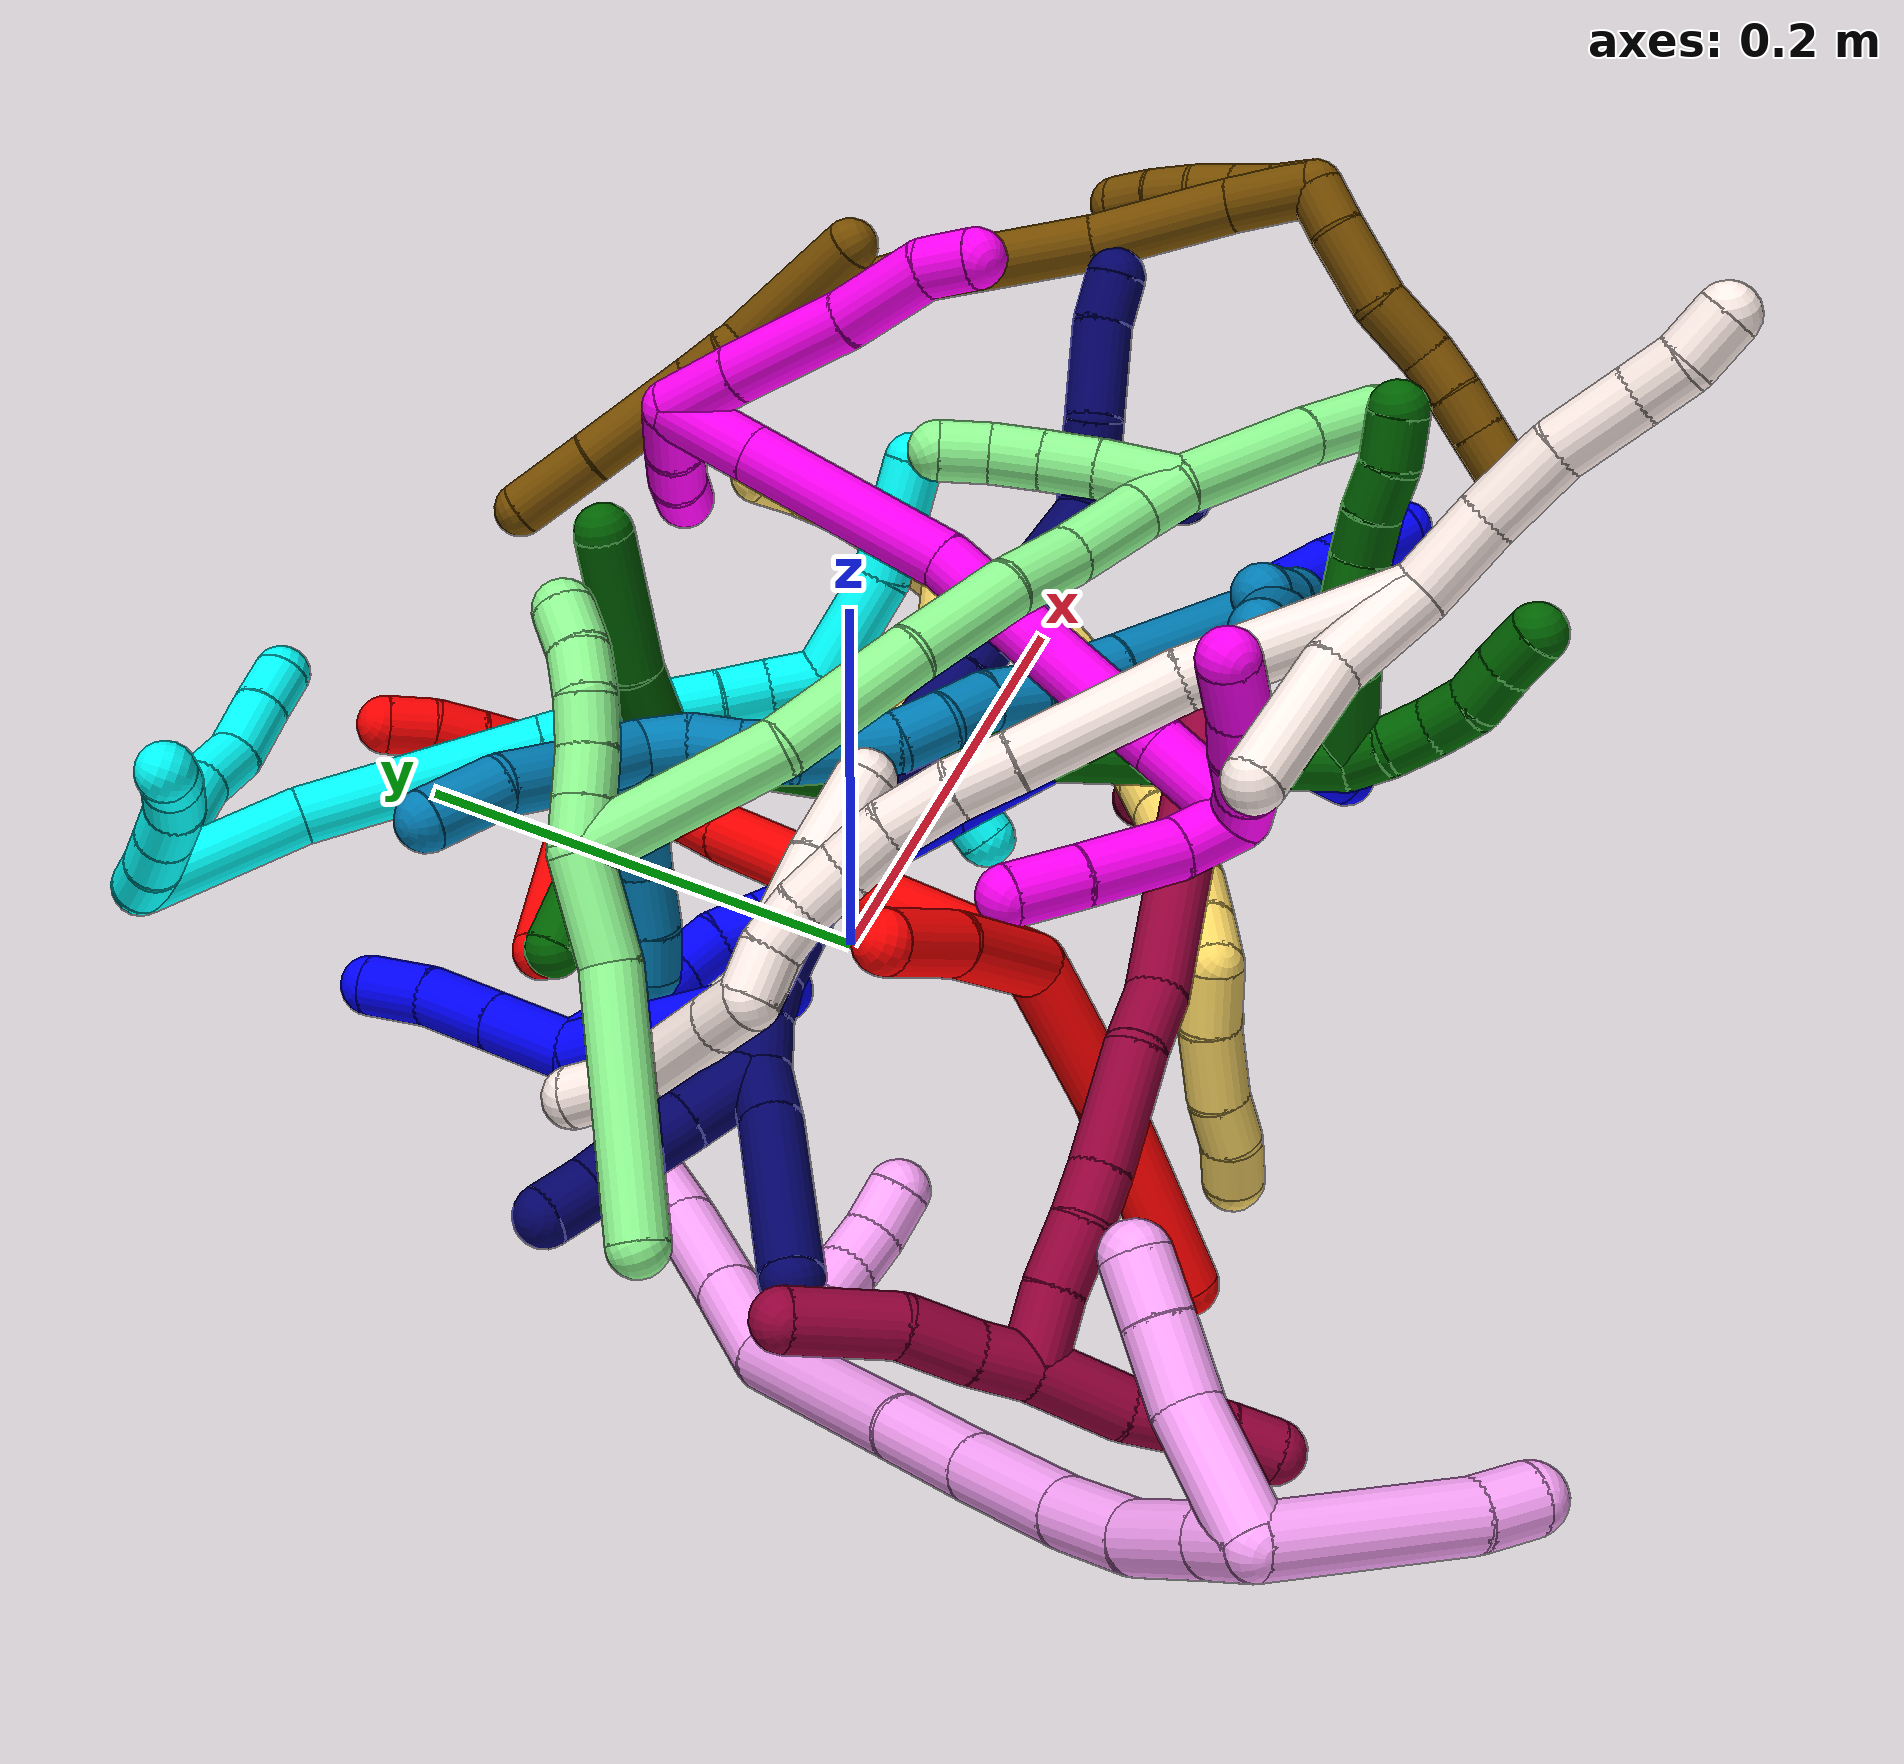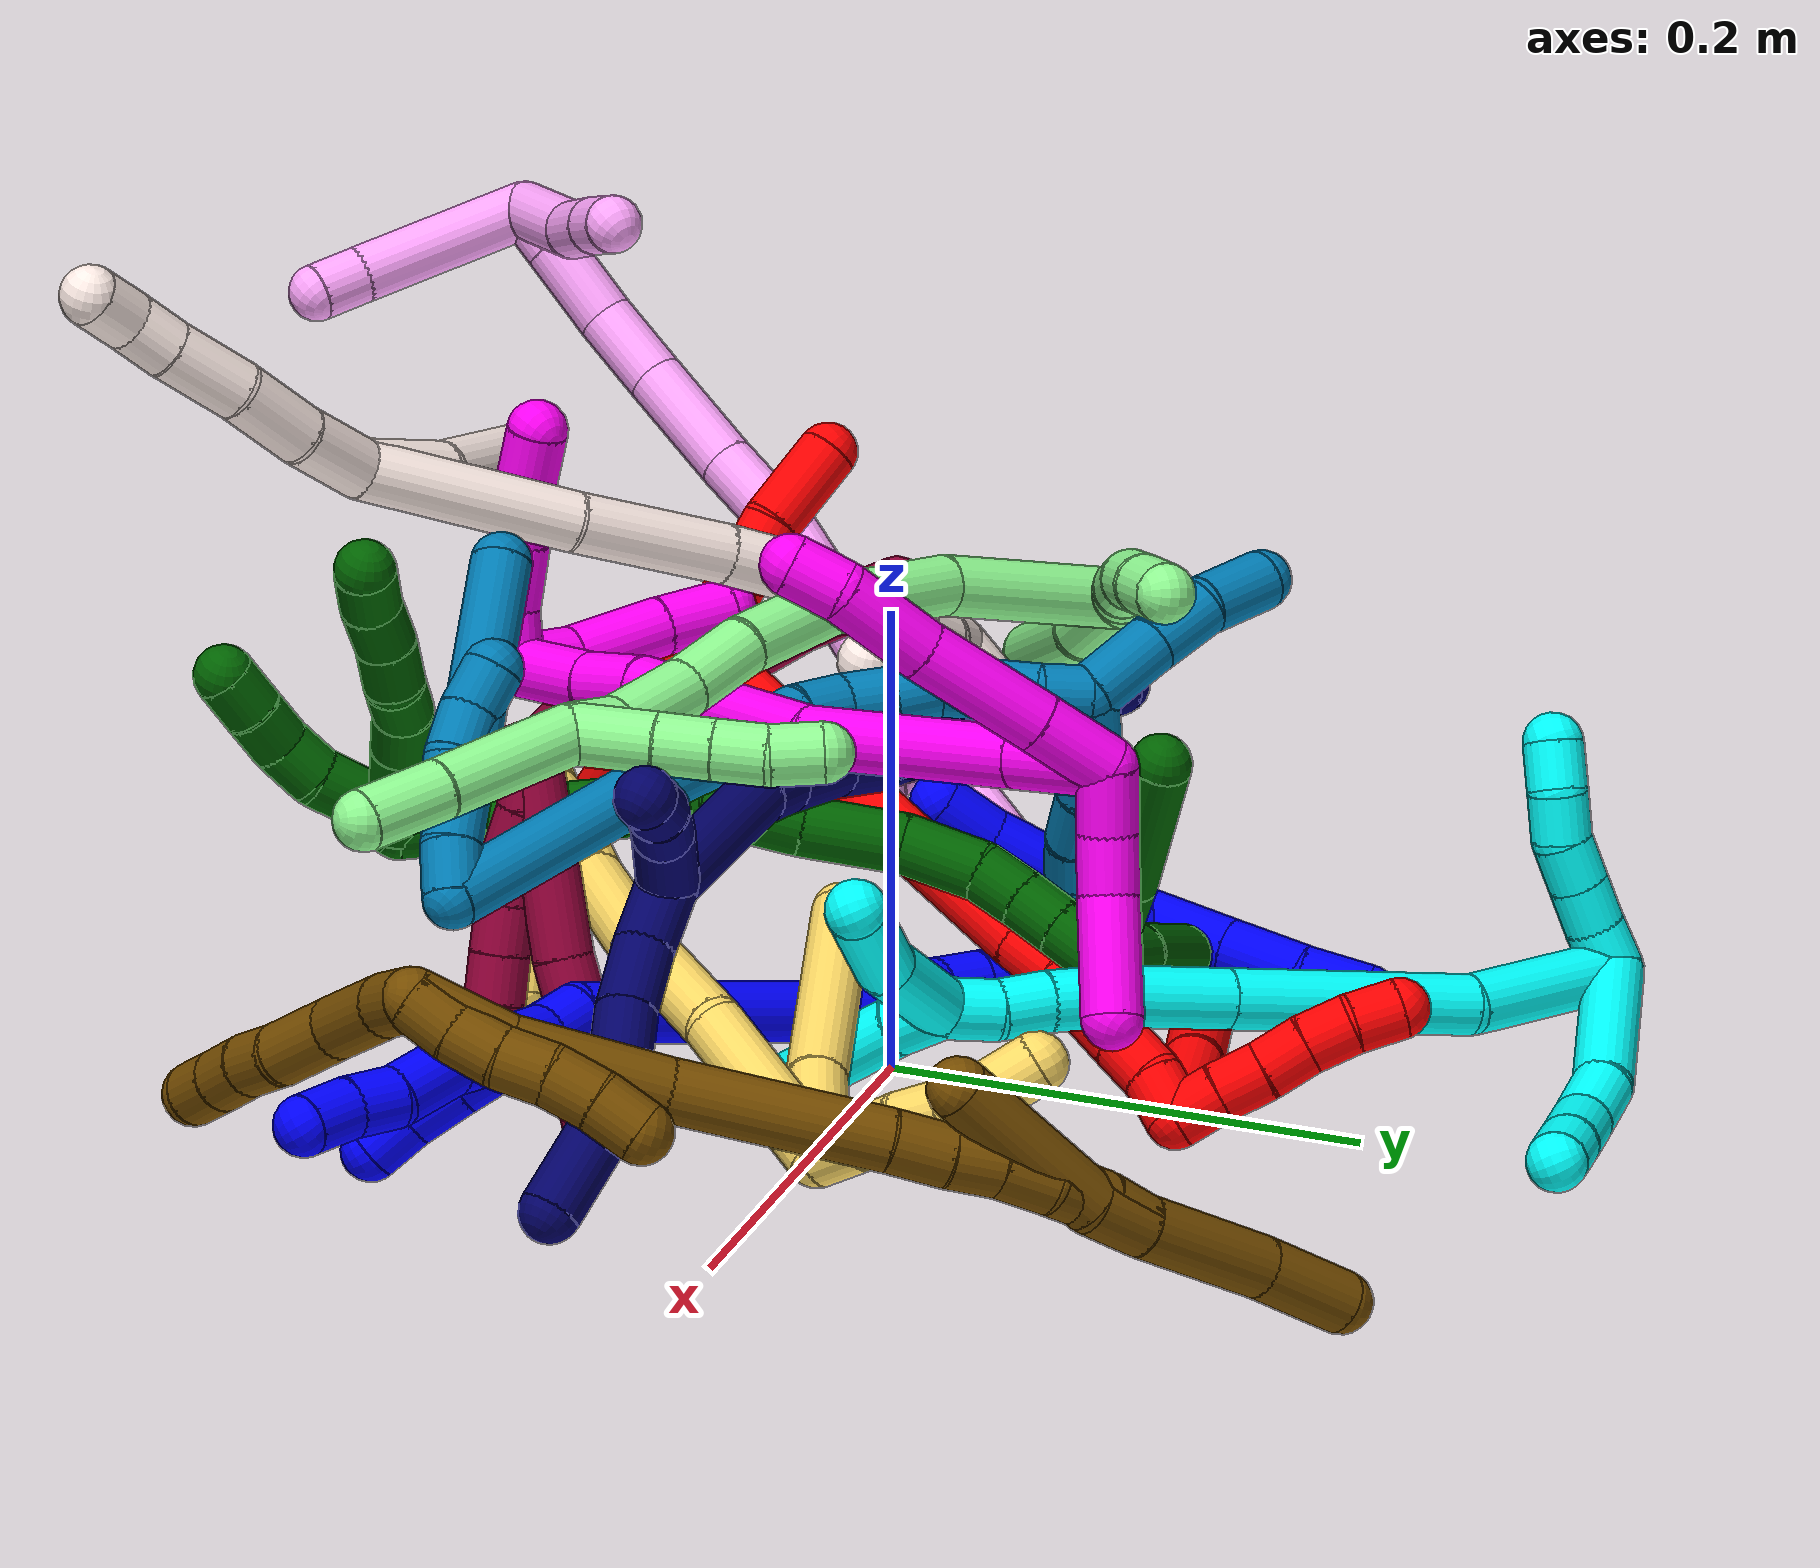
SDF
<sdf version="1.7">
 <world name="default">
  <plugin name="TubeGeneratorPlugin" filename="libtube_generator_plugin.so"/>
  <model name="photoneo_s_sensor">
   <static>1</static>
   <pose>0 0 2 1.57079 1.57079 3.14159</pose>
   <link name="link">
    <inertial><mass>0.1</mass></inertial>
    <sensor name="sensor" type="depth">
     <update_rate>30</update_rate>
     <camera>
      <horizontal_fov>1.22</horizontal_fov>
      <image><width>1920</width><height>1200</height><format>B8G8R8</format></image>
      <clip><near>0.1</near><far>4</far></clip>
      <depth_camera><output>points</output></depth_camera>
     </camera>
     <plugin name="camera_plugin" filename="libgazebo_ros_depth_camera.so">
      <baseline>0.2</baseline>
      <alwaysOn>1</alwaysOn>
      <updateRate>0.0</updateRate>
      <cameraName>camera_ir</cameraName>
      <imageTopicName>/camera/color/image_raw</imageTopicName>
      <cameraInfoTopicName>/camera/color/camera_info</cameraInfoTopicName>
      <depthImageTopicName>/camera/depth/image_raw</depthImageTopicName>
      <depthImageCameraInfoTopicName>/camera/depth/camera_info</depthImageCameraInfoTopicName>
      <pointCloudTopicName>/camera/depth/points</pointCloudTopicName>
      <frameName>fr_optical</frameName>
      <pointCloudCutoff>0.1</pointCloudCutoff>
      <pointCloudCutoffMax>2.0</pointCloudCutoffMax>
      <distortionK1>0</distortionK1>
      <distortionK2>0</distortionK2>
      <distortionK3>0</distortionK3>
      <distortionT1>0</distortionT1>
      <distortionT2>0</distortionT2>
      <CxPrime>0</CxPrime>
      <Cx>0</Cx>
      <Cy>0</Cy>
      <focalLength>0</focalLength>
      <hackBaseline>0</hackBaseline>
     </plugin>
    </sensor>
   </link>
  </model>
  <gravity>0 0 -9.8</gravity>
  <magnetic_field>6e-06 2.3e-05 -4.2e-05</magnetic_field>
  <atmosphere type="adiabatic"/>
  <physics name="default_physics" default="0" type="ode">
   <max_step_size>0.003</max_step_size>
   <real_time_factor>1</real_time_factor>
   <real_time_update_rate>1000</real_time_update_rate>
   <max_contacts>10000</max_contacts>
   <ode>
    <solver>
     <type>quick</type>
     <iters>100</iters>
     <sor>1.3</sor>
     <use_dynamic_moi_rescaling>0</use_dynamic_moi_rescaling>
    </solver>
    <constraints>
     <contact_max_correcting_vel>0</contact_max_correcting_vel>
     <contact_surface_layer>0.001</contact_surface_layer>
     <cfm>0</cfm>
     <erp>0.2</erp>
    </constraints>
   </ode>
  </physics>
  <scene><ambient>0.4 0.4 0.4 1</ambient><background>0.7 0.7 0.7 1</background><shadows>0</shadows></scene>
  <audio><device>default</device></audio>
  <spherical_coordinates>
   <surface_model>EARTH_WGS84</surface_model>
   <latitude_deg>0</latitude_deg>
   <longitude_deg>0</longitude_deg>
   <elevation>0</elevation>
   <heading_deg>0</heading_deg>
  </spherical_coordinates>
  <model name="bin">
   <static>1</static>
   <link name="bottom">
    <collision name="collision-bottom">
     <pose>0 0 -0.01 0 -0 0</pose>
     <geometry><box><size>0.8 0.6 0.02</size></box></geometry>
     <surface>
      <friction><ode><mu>100</mu><mu2>100</mu2></ode></friction>
      <contact><collide_bitmask>65535</collide_bitmask></contact>
     </surface>
    </collision>
   </link>
   <link name="west_wall">
    <collision name="collision-west_wall">
     <pose>-0.41 0 0.1 0 -0 0</pose>
     <geometry><box><size>0.02 0.6 0.2</size></box></geometry>
     <surface>
      <friction><ode><mu>100</mu><mu2>100</mu2></ode></friction>
      <contact><collide_bitmask>65535</collide_bitmask></contact>
     </surface>
    </collision>
   </link>
   <link name="east_wall">
    <collision name="collision-east_wall">
     <pose>0.41 0 0.1 0 -0 0</pose>
     <geometry><box><size>0.02 0.6 0.2</size></box></geometry>
     <surface>
      <friction><ode><mu>100</mu><mu2>100</mu2></ode></friction>
      <contact><collide_bitmask>65535</collide_bitmask></contact>
     </surface>
    </collision>
   </link>
   <link name="south_wall">
    <collision name="collision-south_wall">
     <pose>0 -0.31 0.1 0 -0 0</pose>
     <geometry><box><size>0.8 0.02 0.2</size></box></geometry>
     <surface>
      <friction><ode><mu>100</mu><mu2>100</mu2></ode></friction>
      <contact><collide_bitmask>65535</collide_bitmask></contact>
     </surface>
    </collision>
   </link>
   <link name="north_wall">
    <collision name="collision-north_wall">
     <pose>0 0.31 0.1 0 -0 0</pose>
     <geometry><box><size>0.8 0.02 0.2</size></box></geometry>
     <surface>
      <friction><ode><mu>100</mu><mu2>100</mu2></ode></friction>
      <contact><collide_bitmask>65535</collide_bitmask></contact>
     </surface>
    </collision>
   </link>
  </model>
  <model name="1">
   <static>0</static>
   <link name="1">
    <collision name="collision-cylinder-e_1_2_8">
     <pose>-0.002913 -0.007283 0.00649 0.842965 -0.290211 -0.130851</pose>
     <geometry><cylinder><radius>0.0125</radius><length>0.020362</length></cylinder></geometry>
     <surface>
      <friction><ode><mu>1.16</mu><mu2>1.16</mu2><slip1>0</slip1><slip2>0</slip2></ode></friction>
      <contact><ode><kp>1e+06</kp><kd>1</kd><max_vel>0</max_vel><min_depth>0.001</min_depth></ode></contact>
     </surface>
    </collision>
    <visual name="visual-cylinder-e_1_2_8">
     <pose>-0.002913 -0.007283 0.00649 0.842965 -0.290211 -0.130851</pose>
     <geometry><cylinder><radius>0.0125</radius><length>0.020362</length></cylinder></geometry>
     <material><ambient>0 0 1 1</ambient></material>
    </visual>
    <collision name="collision-cylinder-e_2_8_9">
     <pose>-0.008245 -0.026878 0.019595 1.07772 -0.171363 -0.102616</pose>
     <geometry><cylinder><radius>0.0125</radius><length>0.028367</length></cylinder></geometry>
     <surface>
      <friction><ode><mu>1.16</mu><mu2>1.16</mu2><slip1>0</slip1><slip2>0</slip2></ode></friction>
      <contact><ode><kp>1e+06</kp><kd>1</kd><max_vel>0</max_vel><min_depth>0.001</min_depth></ode></contact>
     </surface>
    </collision>
    <visual name="visual-cylinder-e_2_8_9">
     <pose>-0.008245 -0.026878 0.019595 1.07772 -0.171363 -0.102616</pose>
     <geometry><cylinder><radius>0.0125</radius><length>0.028367</length></cylinder></geometry>
     <material><ambient>0 0 1 1</ambient></material>
    </visual>
    <collision name="collision-cylinder-e_3_9_10">
     <pose>-0.013051 -0.051933 0.032923 1.08597 -0.164203 -0.099238</pose>
     <geometry><cylinder><radius>0.0125</radius><length>0.029202</length></cylinder></geometry>
     <surface>
      <friction><ode><mu>1.16</mu><mu2>1.16</mu2><slip1>0</slip1><slip2>0</slip2></ode></friction>
      <contact><ode><kp>1e+06</kp><kd>1</kd><max_vel>0</max_vel><min_depth>0.001</min_depth></ode></contact>
     </surface>
    </collision>
    <visual name="visual-cylinder-e_3_9_10">
     <pose>-0.013051 -0.051933 0.032923 1.08597 -0.164203 -0.099238</pose>
     <geometry><cylinder><radius>0.0125</radius><length>0.029202</length></cylinder></geometry>
     <material><ambient>0 0 1 1</ambient></material>
    </visual>
    <collision name="collision-cylinder-e_4_10_11">
     <pose>-0.018982 -0.074888 0.049337 0.811005 -0.24657 -0.106291</pose>
     <geometry><cylinder><radius>0.0125</radius><length>0.029046</length></cylinder></geometry>
     <surface>
      <friction><ode><mu>1.16</mu><mu2>1.16</mu2><slip1>0</slip1><slip2>0</slip2></ode></friction>
      <contact><ode><kp>1e+06</kp><kd>1</kd><max_vel>0</max_vel><min_depth>0.001</min_depth></ode></contact>
     </surface>
    </collision>
    <visual name="visual-cylinder-e_4_10_11">
     <pose>-0.018982 -0.074888 0.049337 0.811005 -0.24657 -0.106291</pose>
     <geometry><cylinder><radius>0.0125</radius><length>0.029046</length></cylinder></geometry>
     <material><ambient>0 0 1 1</ambient></material>
    </visual>
    <collision name="collision-cylinder-e_5_11_12">
     <pose>-0.022298 -0.092611 0.066355 0.798497 0.021772 0.009186</pose>
     <geometry><cylinder><radius>0.0125</radius><length>0.020981</length></cylinder></geometry>
     <surface>
      <friction><ode><mu>1.16</mu><mu2>1.16</mu2><slip1>0</slip1><slip2>0</slip2></ode></friction>
      <contact><ode><kp>1e+06</kp><kd>1</kd><max_vel>0</max_vel><min_depth>0.001</min_depth></ode></contact>
     </surface>
    </collision>
    <visual name="visual-cylinder-e_5_11_12">
     <pose>-0.022298 -0.092611 0.066355 0.798497 0.021772 0.009186</pose>
     <geometry><cylinder><radius>0.0125</radius><length>0.020981</length></cylinder></geometry>
     <material><ambient>0 0 1 1</ambient></material>
    </visual>
    <collision name="collision-cylinder-e_6_12_6">
     <pose>-0.023597 -0.108336 0.080864 0.851707 -0.138993 -0.06313</pose>
     <geometry><cylinder><radius>0.0125</radius><length>0.022043</length></cylinder></geometry>
     <surface>
      <friction><ode><mu>1.16</mu><mu2>1.16</mu2><slip1>0</slip1><slip2>0</slip2></ode></friction>
      <contact><ode><kp>1e+06</kp><kd>1</kd><max_vel>0</max_vel><min_depth>0.001</min_depth></ode></contact>
     </surface>
    </collision>
    <visual name="visual-cylinder-e_6_12_6">
     <pose>-0.023597 -0.108336 0.080864 0.851707 -0.138993 -0.06313</pose>
     <geometry><cylinder><radius>0.0125</radius><length>0.022043</length></cylinder></geometry>
     <material><ambient>0 0 1 1</ambient></material>
    </visual>
    <collision name="collision-cylinder-e_1_2_13">
     <pose>-7.9e-05 -0.000566 0.010878 0.051982 -0.007261 -0.000189</pose>
     <geometry><cylinder><radius>0.0125</radius><length>0.021787</length></cylinder></geometry>
     <surface>
      <friction><ode><mu>1.16</mu><mu2>1.16</mu2><slip1>0</slip1><slip2>0</slip2></ode></friction>
      <contact><ode><kp>1e+06</kp><kd>1</kd><max_vel>0</max_vel><min_depth>0.001</min_depth></ode></contact>
     </surface>
    </collision>
    <visual name="visual-cylinder-e_1_2_13">
     <pose>-7.9e-05 -0.000566 0.010878 0.051982 -0.007261 -0.000189</pose>
     <geometry><cylinder><radius>0.0125</radius><length>0.021787</length></cylinder></geometry>
     <material><ambient>0 0 1 1</ambient></material>
    </visual>
    <collision name="collision-cylinder-e_2_13_14">
     <pose>-0.000524 -0.001864 0.038762 0.04301 -0.021492 -0.000462</pose>
     <geometry><cylinder><radius>0.0125</radius><length>0.034051</length></cylinder></geometry>
     <surface>
      <friction><ode><mu>1.16</mu><mu2>1.16</mu2><slip1>0</slip1><slip2>0</slip2></ode></friction>
      <contact><ode><kp>1e+06</kp><kd>1</kd><max_vel>0</max_vel><min_depth>0.001</min_depth></ode></contact>
     </surface>
    </collision>
    <visual name="visual-cylinder-e_2_13_14">
     <pose>-0.000524 -0.001864 0.038762 0.04301 -0.021492 -0.000462</pose>
     <geometry><cylinder><radius>0.0125</radius><length>0.034051</length></cylinder></geometry>
     <material><ambient>0 0 1 1</ambient></material>
    </visual>
    <collision name="collision-cylinder-e_3_14_15">
     <pose>-0.001607 -0.003228 0.067601 0.053406 -0.060424 -0.001614</pose>
     <geometry><cylinder><radius>0.0125</radius><length>0.023743</length></cylinder></geometry>
     <surface>
      <friction><ode><mu>1.16</mu><mu2>1.16</mu2><slip1>0</slip1><slip2>0</slip2></ode></friction>
      <contact><ode><kp>1e+06</kp><kd>1</kd><max_vel>0</max_vel><min_depth>0.001</min_depth></ode></contact>
     </surface>
    </collision>
    <visual name="visual-cylinder-e_3_14_15">
     <pose>-0.001607 -0.003228 0.067601 0.053406 -0.060424 -0.001614</pose>
     <geometry><cylinder><radius>0.0125</radius><length>0.023743</length></cylinder></geometry>
     <material><ambient>0 0 1 1</ambient></material>
    </visual>
    <collision name="collision-cylinder-e_4_15_5">
     <pose>-0.004045 -0.004068 0.089495 0.020628 -0.169349 -0.001751</pose>
     <geometry><cylinder><radius>0.0125</radius><length>0.02042</length></cylinder></geometry>
     <surface>
      <friction><ode><mu>1.16</mu><mu2>1.16</mu2><slip1>0</slip1><slip2>0</slip2></ode></friction>
      <contact><ode><kp>1e+06</kp><kd>1</kd><max_vel>0</max_vel><min_depth>0.001</min_depth></ode></contact>
     </surface>
    </collision>
    <visual name="visual-cylinder-e_4_15_5">
     <pose>-0.004045 -0.004068 0.089495 0.020628 -0.169349 -0.001751</pose>
     <geometry><cylinder><radius>0.0125</radius><length>0.02042</length></cylinder></geometry>
     <material><ambient>0 0 1 1</ambient></material>
    </visual>
    <collision name="collision-cylinder-e_1_2_16">
     <pose>-0.008874 0.040572 -0.030516 -2.21567 -0.173048 0.34412</pose>
     <geometry><cylinder><radius>0.0125</radius><length>0.103074</length></cylinder></geometry>
     <surface>
      <friction><ode><mu>1.16</mu><mu2>1.16</mu2><slip1>0</slip1><slip2>0</slip2></ode></friction>
      <contact><ode><kp>1e+06</kp><kd>1</kd><max_vel>0</max_vel><min_depth>0.001</min_depth></ode></contact>
     </surface>
    </collision>
    <visual name="visual-cylinder-e_1_2_16">
     <pose>-0.008874 0.040572 -0.030516 -2.21567 -0.173048 0.34412</pose>
     <geometry><cylinder><radius>0.0125</radius><length>0.103074</length></cylinder></geometry>
     <material><ambient>0 0 1 1</ambient></material>
    </visual>
    <collision name="collision-cylinder-e_2_16_17">
     <pose>-0.020509 0.094542 -0.071236 -2.22167 -0.162504 0.325836</pose>
     <geometry><cylinder><radius>0.0125</radius><length>0.034132</length></cylinder></geometry>
     <surface>
      <friction><ode><mu>1.16</mu><mu2>1.16</mu2><slip1>0</slip1><slip2>0</slip2></ode></friction>
      <contact><ode><kp>1e+06</kp><kd>1</kd><max_vel>0</max_vel><min_depth>0.001</min_depth></ode></contact>
     </surface>
    </collision>
    <visual name="visual-cylinder-e_2_16_17">
     <pose>-0.020509 0.094542 -0.071236 -2.22167 -0.162504 0.325836</pose>
     <geometry><cylinder><radius>0.0125</radius><length>0.034132</length></cylinder></geometry>
     <material><ambient>0 0 1 1</ambient></material>
    </visual>
    <collision name="collision-cylinder-e_3_17_18">
     <pose>-0.020408 0.125329 -0.09238 -2.13241 0.138449 -0.249782</pose>
     <geometry><cylinder><radius>0.0125</radius><length>0.041485</length></cylinder></geometry>
     <surface>
      <friction><ode><mu>1.16</mu><mu2>1.16</mu2><slip1>0</slip1><slip2>0</slip2></ode></friction>
      <contact><ode><kp>1e+06</kp><kd>1</kd><max_vel>0</max_vel><min_depth>0.001</min_depth></ode></contact>
     </surface>
    </collision>
    <visual name="visual-cylinder-e_3_17_18">
     <pose>-0.020408 0.125329 -0.09238 -2.13241 0.138449 -0.249782</pose>
     <geometry><cylinder><radius>0.0125</radius><length>0.041485</length></cylinder></geometry>
     <material><ambient>0 0 1 1</ambient></material>
    </visual>
    <collision name="collision-cylinder-e_4_18_19">
     <pose>-0.018405 0.149902 -0.110306 -2.34208 -0.085612 0.202063</pose>
     <geometry><cylinder><radius>0.0125</radius><length>0.020116</length></cylinder></geometry>
     <surface>
      <friction><ode><mu>1.16</mu><mu2>1.16</mu2><slip1>0</slip1><slip2>0</slip2></ode></friction>
      <contact><ode><kp>1e+06</kp><kd>1</kd><max_vel>0</max_vel><min_depth>0.001</min_depth></ode></contact>
     </surface>
    </collision>
    <visual name="visual-cylinder-e_4_18_19">
     <pose>-0.018405 0.149902 -0.110306 -2.34208 -0.085612 0.202063</pose>
     <geometry><cylinder><radius>0.0125</radius><length>0.020116</length></cylinder></geometry>
     <material><ambient>0 0 1 1</ambient></material>
    </visual>
    <collision name="collision-cylinder-e_5_19_20">
     <pose>-0.020092 0.164316 -0.124351 -2.34434 -0.081622 0.193301</pose>
     <geometry><cylinder><radius>0.0125</radius><length>0.020275</length></cylinder></geometry>
     <surface>
      <friction><ode><mu>1.16</mu><mu2>1.16</mu2><slip1>0</slip1><slip2>0</slip2></ode></friction>
      <contact><ode><kp>1e+06</kp><kd>1</kd><max_vel>0</max_vel><min_depth>0.001</min_depth></ode></contact>
     </surface>
    </collision>
    <visual name="visual-cylinder-e_5_19_20">
     <pose>-0.020092 0.164316 -0.124351 -2.34434 -0.081622 0.193301</pose>
     <geometry><cylinder><radius>0.0125</radius><length>0.020275</length></cylinder></geometry>
     <material><ambient>0 0 1 1</ambient></material>
    </visual>
    <collision name="collision-cylinder-e_6_20_21">
     <pose>-0.02 0.180172 -0.136541 -2.10732 0.09118 -0.160081</pose>
     <geometry><cylinder><radius>0.0125</radius><length>0.020159</length></cylinder></geometry>
     <surface>
      <friction><ode><mu>1.16</mu><mu2>1.16</mu2><slip1>0</slip1><slip2>0</slip2></ode></friction>
      <contact><ode><kp>1e+06</kp><kd>1</kd><max_vel>0</max_vel><min_depth>0.001</min_depth></ode></contact>
     </surface>
    </collision>
    <visual name="visual-cylinder-e_6_20_21">
     <pose>-0.02 0.180172 -0.136541 -2.10732 0.09118 -0.160081</pose>
     <geometry><cylinder><radius>0.0125</radius><length>0.020159</length></cylinder></geometry>
     <material><ambient>0 0 1 1</ambient></material>
    </visual>
    <collision name="collision-cylinder-e_7_21_22">
     <pose>-0.016714 0.197509 -0.146569 -2.08304 0.232744 -0.3945</pose>
     <geometry><cylinder><radius>0.0125</radius><length>0.020538</length></cylinder></geometry>
     <surface>
      <friction><ode><mu>1.16</mu><mu2>1.16</mu2><slip1>0</slip1><slip2>0</slip2></ode></friction>
      <contact><ode><kp>1e+06</kp><kd>1</kd><max_vel>0</max_vel><min_depth>0.001</min_depth></ode></contact>
     </surface>
    </collision>
    <visual name="visual-cylinder-e_7_21_22">
     <pose>-0.016714 0.197509 -0.146569 -2.08304 0.232744 -0.3945</pose>
     <geometry><cylinder><radius>0.0125</radius><length>0.020538</length></cylinder></geometry>
     <material><ambient>0 0 1 1</ambient></material>
    </visual>
    <collision name="collision-cylinder-e_8_22_23">
     <pose>-0.011712 0.21426 -0.156993 -2.17285 0.263652 -0.49371</pose>
     <geometry><cylinder><radius>0.0125</radius><length>0.020212</length></cylinder></geometry>
     <surface>
      <friction><ode><mu>1.16</mu><mu2>1.16</mu2><slip1>0</slip1><slip2>0</slip2></ode></friction>
      <contact><ode><kp>1e+06</kp><kd>1</kd><max_vel>0</max_vel><min_depth>0.001</min_depth></ode></contact>
     </surface>
    </collision>
    <visual name="visual-cylinder-e_8_22_23">
     <pose>-0.011712 0.21426 -0.156993 -2.17285 0.263652 -0.49371</pose>
     <geometry><cylinder><radius>0.0125</radius><length>0.020212</length></cylinder></geometry>
     <material><ambient>0 0 1 1</ambient></material>
    </visual>
    <collision name="collision-cylinder-e_9_23_1">
     <pose>-0.007127 0.229667 -0.169001 -2.2925 0.196298 -0.42895</pose>
     <geometry><cylinder><radius>0.0125</radius><length>0.020009</length></cylinder></geometry>
     <surface>
      <friction><ode><mu>1.16</mu><mu2>1.16</mu2><slip1>0</slip1><slip2>0</slip2></ode></friction>
      <contact><ode><kp>1e+06</kp><kd>1</kd><max_vel>0</max_vel><min_depth>0.001</min_depth></ode></contact>
     </surface>
    </collision>
    <visual name="visual-cylinder-e_9_23_1">
     <pose>-0.007127 0.229667 -0.169001 -2.2925 0.196298 -0.42895</pose>
     <geometry><cylinder><radius>0.0125</radius><length>0.020009</length></cylinder></geometry>
     <material><ambient>0 0 1 1</ambient></material>
    </visual>
    <collision name="collision-cylinder-e_1_1_24">
     <pose>0.020884 0.217391 -0.157831 0.838706 0.778755 0.361845</pose>
     <geometry><cylinder><radius>0.0125</radius><length>0.074202</length></cylinder></geometry>
     <surface>
      <friction><ode><mu>1.16</mu><mu2>1.16</mu2><slip1>0</slip1><slip2>0</slip2></ode></friction>
      <contact><ode><kp>1e+06</kp><kd>1</kd><max_vel>0</max_vel><min_depth>0.001</min_depth></ode></contact>
     </surface>
    </collision>
    <visual name="visual-cylinder-e_1_1_24">
     <pose>0.020884 0.217391 -0.157831 0.838706 0.778755 0.361845</pose>
     <geometry><cylinder><radius>0.0125</radius><length>0.074202</length></cylinder></geometry>
     <material><ambient>0 0 1 1</ambient></material>
    </visual>
    <collision name="collision-cylinder-e_2_24_4">
     <pose>0.05611 0.189824 -0.13576 1.06211 0.790443 0.480574</pose>
     <geometry><cylinder><radius>0.0125</radius><length>0.025798</length></cylinder></geometry>
     <surface>
      <friction><ode><mu>1.16</mu><mu2>1.16</mu2><slip1>0</slip1><slip2>0</slip2></ode></friction>
      <contact><ode><kp>1e+06</kp><kd>1</kd><max_vel>0</max_vel><min_depth>0.001</min_depth></ode></contact>
     </surface>
    </collision>
    <visual name="visual-cylinder-e_2_24_4">
     <pose>0.05611 0.189824 -0.13576 1.06211 0.790443 0.480574</pose>
     <geometry><cylinder><radius>0.0125</radius><length>0.025798</length></cylinder></geometry>
     <material><ambient>0 0 1 1</ambient></material>
    </visual>
    <collision name="collision-cylinder-e_1_1_25">
     <pose>-0.01978 0.237699 -0.187567 -3.08655 -0.878855 3.02461</pose>
     <geometry><cylinder><radius>0.0125</radius><length>0.037934</length></cylinder></geometry>
     <surface>
      <friction><ode><mu>1.16</mu><mu2>1.16</mu2><slip1>0</slip1><slip2>0</slip2></ode></friction>
      <contact><ode><kp>1e+06</kp><kd>1</kd><max_vel>0</max_vel><min_depth>0.001</min_depth></ode></contact>
     </surface>
    </collision>
    <visual name="visual-cylinder-e_1_1_25">
     <pose>-0.01978 0.237699 -0.187567 -3.08655 -0.878855 3.02461</pose>
     <geometry><cylinder><radius>0.0125</radius><length>0.037934</length></cylinder></geometry>
     <material><ambient>0 0 1 1</ambient></material>
    </visual>
    <collision name="collision-cylinder-e_2_25_26">
     <pose>-0.047359 0.238949 -0.210486 -3.08774 -0.874237 3.02644</pose>
     <geometry><cylinder><radius>0.0125</radius><length>0.033827</length></cylinder></geometry>
     <surface>
      <friction><ode><mu>1.16</mu><mu2>1.16</mu2><slip1>0</slip1><slip2>0</slip2></ode></friction>
      <contact><ode><kp>1e+06</kp><kd>1</kd><max_vel>0</max_vel><min_depth>0.001</min_depth></ode></contact>
     </surface>
    </collision>
    <visual name="visual-cylinder-e_2_25_26">
     <pose>-0.047359 0.238949 -0.210486 -3.08774 -0.874237 3.02644</pose>
     <geometry><cylinder><radius>0.0125</radius><length>0.033827</length></cylinder></geometry>
     <material><ambient>0 0 1 1</ambient></material>
    </visual>
    <collision name="collision-cylinder-e_3_26_3">
     <pose>-0.070276 0.242446 -0.230913 -2.84671 -0.781318 2.44936</pose>
     <geometry><cylinder><radius>0.0125</radius><length>0.028238</length></cylinder></geometry>
     <surface>
      <friction><ode><mu>1.16</mu><mu2>1.16</mu2><slip1>0</slip1><slip2>0</slip2></ode></friction>
      <contact><ode><kp>1e+06</kp><kd>1</kd><max_vel>0</max_vel><min_depth>0.001</min_depth></ode></contact>
     </surface>
    </collision>
    <visual name="visual-cylinder-e_3_26_3">
     <pose>-0.070276 0.242446 -0.230913 -2.84671 -0.781318 2.44936</pose>
     <geometry><cylinder><radius>0.0125</radius><length>0.028238</length></cylinder></geometry>
     <material><ambient>0 0 1 1</ambient></material>
    </visual>
    <collision name="collision-sphere-3">
     <pose>-0.080219 0.245359 -0.240505 0 -0 0</pose>
     <geometry><sphere><radius>0.0125</radius></sphere></geometry>
     <surface>
      <friction><ode><mu>1.16</mu><mu2>1.16</mu2><slip1>0</slip1><slip2>0</slip2></ode></friction>
      <contact><ode><kp>1e+06</kp><kd>1</kd><max_vel>0</max_vel><min_depth>0.001</min_depth></ode></contact>
     </surface>
    </collision>
    <visual name="visual-sphere-3">
     <pose>-0.080219 0.245359 -0.240505 0 -0 0</pose>
     <geometry><sphere><radius>0.0125</radius></sphere></geometry>
     <material><ambient>0 0 1 1</ambient></material>
    </visual>
    <collision name="collision-sphere-26">
     <pose>-0.060333 0.239533 -0.221322 0 -0 0</pose>
     <geometry><sphere><radius>0.0125</radius></sphere></geometry>
     <surface>
      <friction><ode><mu>1.16</mu><mu2>1.16</mu2><slip1>0</slip1><slip2>0</slip2></ode></friction>
      <contact><ode><kp>1e+06</kp><kd>1</kd><max_vel>0</max_vel><min_depth>0.001</min_depth></ode></contact>
     </surface>
    </collision>
    <visual name="visual-sphere-26">
     <pose>-0.060333 0.239533 -0.221322 0 -0 0</pose>
     <geometry><sphere><radius>0.0125</radius></sphere></geometry>
     <material><ambient>0 0 1 1</ambient></material>
    </visual>
    <collision name="collision-sphere-25">
     <pose>-0.034385 0.238365 -0.19965 0 -0 0</pose>
     <geometry><sphere><radius>0.0125</radius></sphere></geometry>
     <surface>
      <friction><ode><mu>1.16</mu><mu2>1.16</mu2><slip1>0</slip1><slip2>0</slip2></ode></friction>
      <contact><ode><kp>1e+06</kp><kd>1</kd><max_vel>0</max_vel><min_depth>0.001</min_depth></ode></contact>
     </surface>
    </collision>
    <visual name="visual-sphere-25">
     <pose>-0.034385 0.238365 -0.19965 0 -0 0</pose>
     <geometry><sphere><radius>0.0125</radius></sphere></geometry>
     <material><ambient>0 0 1 1</ambient></material>
    </visual>
    <collision name="collision-sphere-4">
     <pose>0.065277 0.181898 -0.13134 0 -0 0</pose>
     <geometry><sphere><radius>0.0125</radius></sphere></geometry>
     <surface>
      <friction><ode><mu>1.16</mu><mu2>1.16</mu2><slip1>0</slip1><slip2>0</slip2></ode></friction>
      <contact><ode><kp>1e+06</kp><kd>1</kd><max_vel>0</max_vel><min_depth>0.001</min_depth></ode></contact>
     </surface>
    </collision>
    <visual name="visual-sphere-4">
     <pose>0.065277 0.181898 -0.13134 0 -0 0</pose>
     <geometry><sphere><radius>0.0125</radius></sphere></geometry>
     <material><ambient>0 0 1 1</ambient></material>
    </visual>
    <collision name="collision-sphere-24">
     <pose>0.046943 0.19775 -0.14018 0 -0 0</pose>
     <geometry><sphere><radius>0.0125</radius></sphere></geometry>
     <surface>
      <friction><ode><mu>1.16</mu><mu2>1.16</mu2><slip1>0</slip1><slip2>0</slip2></ode></friction>
      <contact><ode><kp>1e+06</kp><kd>1</kd><max_vel>0</max_vel><min_depth>0.001</min_depth></ode></contact>
     </surface>
    </collision>
    <visual name="visual-sphere-24">
     <pose>0.046943 0.19775 -0.14018 0 -0 0</pose>
     <geometry><sphere><radius>0.0125</radius></sphere></geometry>
     <material><ambient>0 0 1 1</ambient></material>
    </visual>
    <collision name="collision-sphere-1">
     <pose>-0.005175 0.237033 -0.175483 0 -0 0</pose>
     <geometry><sphere><radius>0.0125</radius></sphere></geometry>
     <surface>
      <friction><ode><mu>1.16</mu><mu2>1.16</mu2><slip1>0</slip1><slip2>0</slip2></ode></friction>
      <contact><ode><kp>1e+06</kp><kd>1</kd><max_vel>0</max_vel><min_depth>0.001</min_depth></ode></contact>
     </surface>
    </collision>
    <visual name="visual-sphere-1">
     <pose>-0.005175 0.237033 -0.175483 0 -0 0</pose>
     <geometry><sphere><radius>0.0125</radius></sphere></geometry>
     <material><ambient>0 0 1 1</ambient></material>
    </visual>
    <collision name="collision-sphere-23">
     <pose>-0.009078 0.222301 -0.162518 0 -0 0</pose>
     <geometry><sphere><radius>0.0125</radius></sphere></geometry>
     <surface>
      <friction><ode><mu>1.16</mu><mu2>1.16</mu2><slip1>0</slip1><slip2>0</slip2></ode></friction>
      <contact><ode><kp>1e+06</kp><kd>1</kd><max_vel>0</max_vel><min_depth>0.001</min_depth></ode></contact>
     </surface>
    </collision>
    <visual name="visual-sphere-23">
     <pose>-0.009078 0.222301 -0.162518 0 -0 0</pose>
     <geometry><sphere><radius>0.0125</radius></sphere></geometry>
     <material><ambient>0 0 1 1</ambient></material>
    </visual>
    <collision name="collision-sphere-22">
     <pose>-0.014345 0.206219 -0.151467 0 -0 0</pose>
     <geometry><sphere><radius>0.0125</radius></sphere></geometry>
     <surface>
      <friction><ode><mu>1.16</mu><mu2>1.16</mu2><slip1>0</slip1><slip2>0</slip2></ode></friction>
      <contact><ode><kp>1e+06</kp><kd>1</kd><max_vel>0</max_vel><min_depth>0.001</min_depth></ode></contact>
     </surface>
    </collision>
    <visual name="visual-sphere-22">
     <pose>-0.014345 0.206219 -0.151467 0 -0 0</pose>
     <geometry><sphere><radius>0.0125</radius></sphere></geometry>
     <material><ambient>0 0 1 1</ambient></material>
    </visual>
    <collision name="collision-sphere-21">
     <pose>-0.019082 0.188799 -0.141672 0 -0 0</pose>
     <geometry><sphere><radius>0.0125</radius></sphere></geometry>
     <surface>
      <friction><ode><mu>1.16</mu><mu2>1.16</mu2><slip1>0</slip1><slip2>0</slip2></ode></friction>
      <contact><ode><kp>1e+06</kp><kd>1</kd><max_vel>0</max_vel><min_depth>0.001</min_depth></ode></contact>
     </surface>
    </collision>
    <visual name="visual-sphere-21">
     <pose>-0.019082 0.188799 -0.141672 0 -0 0</pose>
     <geometry><sphere><radius>0.0125</radius></sphere></geometry>
     <material><ambient>0 0 1 1</ambient></material>
    </visual>
    <collision name="collision-sphere-12">
     <pose>-0.02207 -0.100124 0.073674 0 -0 0</pose>
     <geometry><sphere><radius>0.0125</radius></sphere></geometry>
     <surface>
      <friction><ode><mu>1.16</mu><mu2>1.16</mu2><slip1>0</slip1><slip2>0</slip2></ode></friction>
      <contact><ode><kp>1e+06</kp><kd>1</kd><max_vel>0</max_vel><min_depth>0.001</min_depth></ode></contact>
     </surface>
    </collision>
    <visual name="visual-sphere-12">
     <pose>-0.02207 -0.100124 0.073674 0 -0 0</pose>
     <geometry><sphere><radius>0.0125</radius></sphere></geometry>
     <material><ambient>0 0 1 1</ambient></material>
    </visual>
    <collision name="collision-sphere-11">
     <pose>-0.022527 -0.085098 0.059037 0 -0 0</pose>
     <geometry><sphere><radius>0.0125</radius></sphere></geometry>
     <surface>
      <friction><ode><mu>1.16</mu><mu2>1.16</mu2><slip1>0</slip1><slip2>0</slip2></ode></friction>
      <contact><ode><kp>1e+06</kp><kd>1</kd><max_vel>0</max_vel><min_depth>0.001</min_depth></ode></contact>
     </surface>
    </collision>
    <visual name="visual-sphere-11">
     <pose>-0.022527 -0.085098 0.059037 0 -0 0</pose>
     <geometry><sphere><radius>0.0125</radius></sphere></geometry>
     <material><ambient>0 0 1 1</ambient></material>
    </visual>
    <collision name="collision-sphere-10">
     <pose>-0.015437 -0.064678 0.039636 0 -0 0</pose>
     <geometry><sphere><radius>0.0125</radius></sphere></geometry>
     <surface>
      <friction><ode><mu>1.16</mu><mu2>1.16</mu2><slip1>0</slip1><slip2>0</slip2></ode></friction>
      <contact><ode><kp>1e+06</kp><kd>1</kd><max_vel>0</max_vel><min_depth>0.001</min_depth></ode></contact>
     </surface>
    </collision>
    <visual name="visual-sphere-10">
     <pose>-0.015437 -0.064678 0.039636 0 -0 0</pose>
     <geometry><sphere><radius>0.0125</radius></sphere></geometry>
     <material><ambient>0 0 1 1</ambient></material>
    </visual>
    <collision name="collision-sphere-9">
     <pose>-0.010664 -0.039188 0.02621 0 -0 0</pose>
     <geometry><sphere><radius>0.0125</radius></sphere></geometry>
     <surface>
      <friction><ode><mu>1.16</mu><mu2>1.16</mu2><slip1>0</slip1><slip2>0</slip2></ode></friction>
      <contact><ode><kp>1e+06</kp><kd>1</kd><max_vel>0</max_vel><min_depth>0.001</min_depth></ode></contact>
     </surface>
    </collision>
    <visual name="visual-sphere-9">
     <pose>-0.010664 -0.039188 0.02621 0 -0 0</pose>
     <geometry><sphere><radius>0.0125</radius></sphere></geometry>
     <material><ambient>0 0 1 1</ambient></material>
    </visual>
    <collision name="collision-sphere-2">
     <geometry><sphere><radius>0.0125</radius></sphere></geometry>
     <surface>
      <friction><ode><mu>1.16</mu><mu2>1.16</mu2><slip1>0</slip1><slip2>0</slip2></ode></friction>
      <contact><ode><kp>1e+06</kp><kd>1</kd><max_vel>0</max_vel><min_depth>0.001</min_depth></ode></contact>
     </surface>
    </collision>
    <visual name="visual-sphere-2">
     <geometry><sphere><radius>0.0125</radius></sphere></geometry>
     <material><ambient>0 0 1 1</ambient></material>
    </visual>
    <collision name="collision-sphere-19">
     <pose>-0.019265 0.157087 -0.117292 0 -0 0</pose>
     <geometry><sphere><radius>0.0125</radius></sphere></geometry>
     <surface>
      <friction><ode><mu>1.16</mu><mu2>1.16</mu2><slip1>0</slip1><slip2>0</slip2></ode></friction>
      <contact><ode><kp>1e+06</kp><kd>1</kd><max_vel>0</max_vel><min_depth>0.001</min_depth></ode></contact>
     </surface>
    </collision>
    <visual name="visual-sphere-19">
     <pose>-0.019265 0.157087 -0.117292 0 -0 0</pose>
     <geometry><sphere><radius>0.0125</radius></sphere></geometry>
     <material><ambient>0 0 1 1</ambient></material>
    </visual>
    <collision name="collision-sphere-8">
     <pose>-0.005827 -0.014567 0.012979 0 -0 0</pose>
     <geometry><sphere><radius>0.0125</radius></sphere></geometry>
     <surface>
      <friction><ode><mu>1.16</mu><mu2>1.16</mu2><slip1>0</slip1><slip2>0</slip2></ode></friction>
      <contact><ode><kp>1e+06</kp><kd>1</kd><max_vel>0</max_vel><min_depth>0.001</min_depth></ode></contact>
     </surface>
    </collision>
    <visual name="visual-sphere-8">
     <pose>-0.005827 -0.014567 0.012979 0 -0 0</pose>
     <geometry><sphere><radius>0.0125</radius></sphere></geometry>
     <material><ambient>0 0 1 1</ambient></material>
    </visual>
    <collision name="collision-sphere-6">
     <pose>-0.025124 -0.116549 0.088053 0 -0 0</pose>
     <geometry><sphere><radius>0.0125</radius></sphere></geometry>
     <surface>
      <friction><ode><mu>1.16</mu><mu2>1.16</mu2><slip1>0</slip1><slip2>0</slip2></ode></friction>
      <contact><ode><kp>1e+06</kp><kd>1</kd><max_vel>0</max_vel><min_depth>0.001</min_depth></ode></contact>
     </surface>
    </collision>
    <visual name="visual-sphere-6">
     <pose>-0.025124 -0.116549 0.088053 0 -0 0</pose>
     <geometry><sphere><radius>0.0125</radius></sphere></geometry>
     <material><ambient>0 0 1 1</ambient></material>
    </visual>
    <collision name="collision-sphere-13">
     <pose>-0.000158 -0.001132 0.021757 0 -0 0</pose>
     <geometry><sphere><radius>0.0125</radius></sphere></geometry>
     <surface>
      <friction><ode><mu>1.16</mu><mu2>1.16</mu2><slip1>0</slip1><slip2>0</slip2></ode></friction>
      <contact><ode><kp>1e+06</kp><kd>1</kd><max_vel>0</max_vel><min_depth>0.001</min_depth></ode></contact>
     </surface>
    </collision>
    <visual name="visual-sphere-13">
     <pose>-0.000158 -0.001132 0.021757 0 -0 0</pose>
     <geometry><sphere><radius>0.0125</radius></sphere></geometry>
     <material><ambient>0 0 1 1</ambient></material>
    </visual>
    <collision name="collision-sphere-14">
     <pose>-0.00089 -0.002596 0.055768 0 -0 0</pose>
     <geometry><sphere><radius>0.0125</radius></sphere></geometry>
     <surface>
      <friction><ode><mu>1.16</mu><mu2>1.16</mu2><slip1>0</slip1><slip2>0</slip2></ode></friction>
      <contact><ode><kp>1e+06</kp><kd>1</kd><max_vel>0</max_vel><min_depth>0.001</min_depth></ode></contact>
     </surface>
    </collision>
    <visual name="visual-sphere-14">
     <pose>-0.00089 -0.002596 0.055768 0 -0 0</pose>
     <geometry><sphere><radius>0.0125</radius></sphere></geometry>
     <material><ambient>0 0 1 1</ambient></material>
    </visual>
    <collision name="collision-sphere-15">
     <pose>-0.002324 -0.003861 0.079433 0 -0 0</pose>
     <geometry><sphere><radius>0.0125</radius></sphere></geometry>
     <surface>
      <friction><ode><mu>1.16</mu><mu2>1.16</mu2><slip1>0</slip1><slip2>0</slip2></ode></friction>
      <contact><ode><kp>1e+06</kp><kd>1</kd><max_vel>0</max_vel><min_depth>0.001</min_depth></ode></contact>
     </surface>
    </collision>
    <visual name="visual-sphere-15">
     <pose>-0.002324 -0.003861 0.079433 0 -0 0</pose>
     <geometry><sphere><radius>0.0125</radius></sphere></geometry>
     <material><ambient>0 0 1 1</ambient></material>
    </visual>
    <collision name="collision-sphere-5">
     <pose>-0.005765 -0.004276 0.099557 0 -0 0</pose>
     <geometry><sphere><radius>0.0125</radius></sphere></geometry>
     <surface>
      <friction><ode><mu>1.16</mu><mu2>1.16</mu2><slip1>0</slip1><slip2>0</slip2></ode></friction>
      <contact><ode><kp>1e+06</kp><kd>1</kd><max_vel>0</max_vel><min_depth>0.001</min_depth></ode></contact>
     </surface>
    </collision>
    <visual name="visual-sphere-5">
     <pose>-0.005765 -0.004276 0.099557 0 -0 0</pose>
     <geometry><sphere><radius>0.0125</radius></sphere></geometry>
     <material><ambient>0 0 1 1</ambient></material>
    </visual>
    <collision name="collision-sphere-16">
     <pose>-0.017748 0.081144 -0.061032 0 -0 0</pose>
     <geometry><sphere><radius>0.0125</radius></sphere></geometry>
     <surface>
      <friction><ode><mu>1.16</mu><mu2>1.16</mu2><slip1>0</slip1><slip2>0</slip2></ode></friction>
      <contact><ode><kp>1e+06</kp><kd>1</kd><max_vel>0</max_vel><min_depth>0.001</min_depth></ode></contact>
     </surface>
    </collision>
    <visual name="visual-sphere-16">
     <pose>-0.017748 0.081144 -0.061032 0 -0 0</pose>
     <geometry><sphere><radius>0.0125</radius></sphere></geometry>
     <material><ambient>0 0 1 1</ambient></material>
    </visual>
    <collision name="collision-sphere-17">
     <pose>-0.02327 0.107941 -0.08144 0 -0 0</pose>
     <geometry><sphere><radius>0.0125</radius></sphere></geometry>
     <surface>
      <friction><ode><mu>1.16</mu><mu2>1.16</mu2><slip1>0</slip1><slip2>0</slip2></ode></friction>
      <contact><ode><kp>1e+06</kp><kd>1</kd><max_vel>0</max_vel><min_depth>0.001</min_depth></ode></contact>
     </surface>
    </collision>
    <visual name="visual-sphere-17">
     <pose>-0.02327 0.107941 -0.08144 0 -0 0</pose>
     <geometry><sphere><radius>0.0125</radius></sphere></geometry>
     <material><ambient>0 0 1 1</ambient></material>
    </visual>
    <collision name="collision-sphere-18">
     <pose>-0.017545 0.142717 -0.103321 0 -0 0</pose>
     <geometry><sphere><radius>0.0125</radius></sphere></geometry>
     <surface>
      <friction><ode><mu>1.16</mu><mu2>1.16</mu2><slip1>0</slip1><slip2>0</slip2></ode></friction>
      <contact><ode><kp>1e+06</kp><kd>1</kd><max_vel>0</max_vel><min_depth>0.001</min_depth></ode></contact>
     </surface>
    </collision>
    <visual name="visual-sphere-18">
     <pose>-0.017545 0.142717 -0.103321 0 -0 0</pose>
     <geometry><sphere><radius>0.0125</radius></sphere></geometry>
     <material><ambient>0 0 1 1</ambient></material>
    </visual>
    <collision name="collision-sphere-20">
     <pose>-0.020918 0.171545 -0.13141 0 -0 0</pose>
     <geometry><sphere><radius>0.0125</radius></sphere></geometry>
     <surface>
      <friction><ode><mu>1.16</mu><mu2>1.16</mu2><slip1>0</slip1><slip2>0</slip2></ode></friction>
      <contact><ode><kp>1e+06</kp><kd>1</kd><max_vel>0</max_vel><min_depth>0.001</min_depth></ode></contact>
     </surface>
    </collision>
    <visual name="visual-sphere-20">
     <pose>-0.020918 0.171545 -0.13141 0 -0 0</pose>
     <geometry><sphere><radius>0.0125</radius></sphere></geometry>
     <material><ambient>0 0 1 1</ambient></material>
    </visual>
    <inertial>
     <pose>-0.010744 0.095166 -0.068253 0 -0 0</pose>
     <mass>0.75</mass>
     <inertia><ixx>0.000187</ixx><ixy>0</ixy><ixz>0</ixz><iyy>4.9e-05</iyy><iyz>0</iyz><izz>-6e-05</izz></inertia>
    </inertial>
   </link>
   <pose>0.131197 -0.082867 0.06702 -2.34659 -0.677603 -2.19586</pose>
  </model>
  <model name="2">
   <static>0</static>
   <link name="2">
    <collision name="collision-cylinder-e_1_2_8">
     <pose>-0.020184 -0.002382 -0.024292 3.04385 -0.690933 -2.87145</pose>
     <geometry><cylinder><radius>0.0125</radius><length>0.063346</length></cylinder></geometry>
     <surface>
      <friction><ode><mu>1.16</mu><mu2>1.16</mu2><slip1>0</slip1><slip2>0</slip2></ode></friction>
      <contact><ode><kp>1e+06</kp><kd>1</kd><max_vel>0</max_vel><min_depth>0.001</min_depth></ode></contact>
     </surface>
    </collision>
    <visual name="visual-cylinder-e_1_2_8">
     <pose>-0.020184 -0.002382 -0.024292 3.04385 -0.690933 -2.87145</pose>
     <geometry><cylinder><radius>0.0125</radius><length>0.063346</length></cylinder></geometry>
     <material><ambient>1 0 0 1</ambient></material>
    </visual>
    <collision name="collision-cylinder-e_2_8_6">
     <pose>-0.071332 -0.010486 -0.078345 2.95163 -0.796141 -2.69601</pose>
     <geometry><cylinder><radius>0.0125</radius><length>0.086654</length></cylinder></geometry>
     <surface>
      <friction><ode><mu>1.16</mu><mu2>1.16</mu2><slip1>0</slip1><slip2>0</slip2></ode></friction>
      <contact><ode><kp>1e+06</kp><kd>1</kd><max_vel>0</max_vel><min_depth>0.001</min_depth></ode></contact>
     </surface>
    </collision>
    <visual name="visual-cylinder-e_2_8_6">
     <pose>-0.071332 -0.010486 -0.078345 2.95163 -0.796141 -2.69601</pose>
     <geometry><cylinder><radius>0.0125</radius><length>0.086654</length></cylinder></geometry>
     <material><ambient>1 0 0 1</ambient></material>
    </visual>
    <collision name="collision-cylinder-e_1_2_9">
     <pose>0.000333 -0.010667 0.028754 0.35522 0.010859 0.001949</pose>
     <geometry><cylinder><radius>0.0125</radius><length>0.061342</length></cylinder></geometry>
     <surface>
      <friction><ode><mu>1.16</mu><mu2>1.16</mu2><slip1>0</slip1><slip2>0</slip2></ode></friction>
      <contact><ode><kp>1e+06</kp><kd>1</kd><max_vel>0</max_vel><min_depth>0.001</min_depth></ode></contact>
     </surface>
    </collision>
    <visual name="visual-cylinder-e_1_2_9">
     <pose>0.000333 -0.010667 0.028754 0.35522 0.010859 0.001949</pose>
     <geometry><cylinder><radius>0.0125</radius><length>0.061342</length></cylinder></geometry>
     <material><ambient>1 0 0 1</ambient></material>
    </visual>
    <collision name="collision-cylinder-e_2_9_5">
     <pose>-0.002104 -0.026051 0.076047 0.249213 -0.143799 -0.018042</pose>
     <geometry><cylinder><radius>0.0125</radius><length>0.038658</length></cylinder></geometry>
     <surface>
      <friction><ode><mu>1.16</mu><mu2>1.16</mu2><slip1>0</slip1><slip2>0</slip2></ode></friction>
      <contact><ode><kp>1e+06</kp><kd>1</kd><max_vel>0</max_vel><min_depth>0.001</min_depth></ode></contact>
     </surface>
    </collision>
    <visual name="visual-cylinder-e_2_9_5">
     <pose>-0.002104 -0.026051 0.076047 0.249213 -0.143799 -0.018042</pose>
     <geometry><cylinder><radius>0.0125</radius><length>0.038658</length></cylinder></geometry>
     <material><ambient>1 0 0 1</ambient></material>
    </visual>
    <collision name="collision-cylinder-e_1_2_10">
     <pose>0.003849 0.09688 0.00784 -1.49005 0.039582 -0.036509</pose>
     <geometry><cylinder><radius>0.0125</radius><length>0.194546</length></cylinder></geometry>
     <surface>
      <friction><ode><mu>1.16</mu><mu2>1.16</mu2><slip1>0</slip1><slip2>0</slip2></ode></friction>
      <contact><ode><kp>1e+06</kp><kd>1</kd><max_vel>0</max_vel><min_depth>0.001</min_depth></ode></contact>
     </surface>
    </collision>
    <visual name="visual-cylinder-e_1_2_10">
     <pose>0.003849 0.09688 0.00784 -1.49005 0.039582 -0.036509</pose>
     <geometry><cylinder><radius>0.0125</radius><length>0.194546</length></cylinder></geometry>
     <material><ambient>1 0 0 1</ambient></material>
    </visual>
    <collision name="collision-cylinder-e_2_10_11">
     <pose>0.009028 0.205326 0.017463 -1.41776 0.113147 -0.097061</pose>
     <geometry><cylinder><radius>0.0125</radius><length>0.023555</length></cylinder></geometry>
     <surface>
      <friction><ode><mu>1.16</mu><mu2>1.16</mu2><slip1>0</slip1><slip2>0</slip2></ode></friction>
      <contact><ode><kp>1e+06</kp><kd>1</kd><max_vel>0</max_vel><min_depth>0.001</min_depth></ode></contact>
     </surface>
    </collision>
    <visual name="visual-cylinder-e_2_10_11">
     <pose>0.009028 0.205326 0.017463 -1.41776 0.113147 -0.097061</pose>
     <geometry><cylinder><radius>0.0125</radius><length>0.023555</length></cylinder></geometry>
     <material><ambient>1 0 0 1</ambient></material>
    </visual>
    <collision name="collision-cylinder-e_3_11_12">
     <pose>0.010601 0.227085 0.018735 -1.62091 0.023804 -0.025027</pose>
     <geometry><cylinder><radius>0.0125</radius><length>0.020418</length></cylinder></geometry>
     <surface>
      <friction><ode><mu>1.16</mu><mu2>1.16</mu2><slip1>0</slip1><slip2>0</slip2></ode></friction>
      <contact><ode><kp>1e+06</kp><kd>1</kd><max_vel>0</max_vel><min_depth>0.001</min_depth></ode></contact>
     </surface>
    </collision>
    <visual name="visual-cylinder-e_3_11_12">
     <pose>0.010601 0.227085 0.018735 -1.62091 0.023804 -0.025027</pose>
     <geometry><cylinder><radius>0.0125</radius><length>0.020418</length></cylinder></geometry>
     <material><ambient>1 0 0 1</ambient></material>
    </visual>
    <collision name="collision-cylinder-e_4_12_13">
     <pose>0.01174 0.247801 0.018181 -1.57487 0.084912 -0.085258</pose>
     <geometry><cylinder><radius>0.0125</radius><length>0.021123</length></cylinder></geometry>
     <surface>
      <friction><ode><mu>1.16</mu><mu2>1.16</mu2><slip1>0</slip1><slip2>0</slip2></ode></friction>
      <contact><ode><kp>1e+06</kp><kd>1</kd><max_vel>0</max_vel><min_depth>0.001</min_depth></ode></contact>
     </surface>
    </collision>
    <visual name="visual-cylinder-e_4_12_13">
     <pose>0.01174 0.247801 0.018181 -1.57487 0.084912 -0.085258</pose>
     <geometry><cylinder><radius>0.0125</radius><length>0.021123</length></cylinder></geometry>
     <material><ambient>1 0 0 1</ambient></material>
    </visual>
    <collision name="collision-cylinder-e_5_13_14">
     <pose>0.013461 0.268327 0.018213 -1.56331 0.082386 -0.081773</pose>
     <geometry><cylinder><radius>0.0125</radius><length>0.020073</length></cylinder></geometry>
     <surface>
      <friction><ode><mu>1.16</mu><mu2>1.16</mu2><slip1>0</slip1><slip2>0</slip2></ode></friction>
      <contact><ode><kp>1e+06</kp><kd>1</kd><max_vel>0</max_vel><min_depth>0.001</min_depth></ode></contact>
     </surface>
    </collision>
    <visual name="visual-cylinder-e_5_13_14">
     <pose>0.013461 0.268327 0.018213 -1.56331 0.082386 -0.081773</pose>
     <geometry><cylinder><radius>0.0125</radius><length>0.020073</length></cylinder></geometry>
     <material><ambient>1 0 0 1</ambient></material>
    </visual>
    <collision name="collision-cylinder-e_6_14_1">
     <pose>0.014048 0.288218 0.016047 -1.79365 -0.023584 0.029526</pose>
     <geometry><cylinder><radius>0.0125</radius><length>0.020285</length></cylinder></geometry>
     <surface>
      <friction><ode><mu>1.16</mu><mu2>1.16</mu2><slip1>0</slip1><slip2>0</slip2></ode></friction>
      <contact><ode><kp>1e+06</kp><kd>1</kd><max_vel>0</max_vel><min_depth>0.001</min_depth></ode></contact>
     </surface>
    </collision>
    <visual name="visual-cylinder-e_6_14_1">
     <pose>0.014048 0.288218 0.016047 -1.79365 -0.023584 0.029526</pose>
     <geometry><cylinder><radius>0.0125</radius><length>0.020285</length></cylinder></geometry>
     <material><ambient>1 0 0 1</ambient></material>
    </visual>
    <collision name="collision-cylinder-e_1_1_15">
     <pose>0.013866 0.30019 0.023586 -0.209893 0.00567 -0.000597</pose>
     <geometry><cylinder><radius>0.0125</radius><length>0.02</length></cylinder></geometry>
     <surface>
      <friction><ode><mu>1.16</mu><mu2>1.16</mu2><slip1>0</slip1><slip2>0</slip2></ode></friction>
      <contact><ode><kp>1e+06</kp><kd>1</kd><max_vel>0</max_vel><min_depth>0.001</min_depth></ode></contact>
     </surface>
    </collision>
    <visual name="visual-cylinder-e_1_1_15">
     <pose>0.013866 0.30019 0.023586 -0.209893 0.00567 -0.000597</pose>
     <geometry><cylinder><radius>0.0125</radius><length>0.02</length></cylinder></geometry>
     <material><ambient>1 0 0 1</ambient></material>
    </visual>
    <collision name="collision-cylinder-e_2_15_16">
     <pose>0.013654 0.305066 0.042965 -0.283072 -0.026807 0.00382</pose>
     <geometry><cylinder><radius>0.0125</radius><length>0.02</length></cylinder></geometry>
     <surface>
      <friction><ode><mu>1.16</mu><mu2>1.16</mu2><slip1>0</slip1><slip2>0</slip2></ode></friction>
      <contact><ode><kp>1e+06</kp><kd>1</kd><max_vel>0</max_vel><min_depth>0.001</min_depth></ode></contact>
     </surface>
    </collision>
    <visual name="visual-cylinder-e_2_15_16">
     <pose>0.013654 0.305066 0.042965 -0.283072 -0.026807 0.00382</pose>
     <geometry><cylinder><radius>0.0125</radius><length>0.02</length></cylinder></geometry>
     <material><ambient>1 0 0 1</ambient></material>
    </visual>
    <collision name="collision-cylinder-e_3_16_17">
     <pose>0.013212 0.309679 0.062395 -0.183168 -0.017389 0.001597</pose>
     <geometry><cylinder><radius>0.0125</radius><length>0.02</length></cylinder></geometry>
     <surface>
      <friction><ode><mu>1.16</mu><mu2>1.16</mu2><slip1>0</slip1><slip2>0</slip2></ode></friction>
      <contact><ode><kp>1e+06</kp><kd>1</kd><max_vel>0</max_vel><min_depth>0.001</min_depth></ode></contact>
     </surface>
    </collision>
    <visual name="visual-cylinder-e_3_16_17">
     <pose>0.013212 0.309679 0.062395 -0.183168 -0.017389 0.001597</pose>
     <geometry><cylinder><radius>0.0125</radius><length>0.02</length></cylinder></geometry>
     <material><ambient>1 0 0 1</ambient></material>
    </visual>
    <collision name="collision-cylinder-e_4_17_18">
     <pose>0.012602 0.314534 0.081745 -0.308492 -0.043701 0.006796</pose>
     <geometry><cylinder><radius>0.0125</radius><length>0.02</length></cylinder></geometry>
     <surface>
      <friction><ode><mu>1.16</mu><mu2>1.16</mu2><slip1>0</slip1><slip2>0</slip2></ode></friction>
      <contact><ode><kp>1e+06</kp><kd>1</kd><max_vel>0</max_vel><min_depth>0.001</min_depth></ode></contact>
     </surface>
    </collision>
    <visual name="visual-cylinder-e_4_17_18">
     <pose>0.012602 0.314534 0.081745 -0.308492 -0.043701 0.006796</pose>
     <geometry><cylinder><radius>0.0125</radius><length>0.02</length></cylinder></geometry>
     <material><ambient>1 0 0 1</ambient></material>
    </visual>
    <collision name="collision-cylinder-e_5_18_4">
     <pose>0.009853 0.321019 0.10036 -0.362774 -0.233238 0.042965</pose>
     <geometry><cylinder><radius>0.0125</radius><length>0.02</length></cylinder></geometry>
     <surface>
      <friction><ode><mu>1.16</mu><mu2>1.16</mu2><slip1>0</slip1><slip2>0</slip2></ode></friction>
      <contact><ode><kp>1e+06</kp><kd>1</kd><max_vel>0</max_vel><min_depth>0.001</min_depth></ode></contact>
     </surface>
    </collision>
    <visual name="visual-cylinder-e_5_18_4">
     <pose>0.009853 0.321019 0.10036 -0.362774 -0.233238 0.042965</pose>
     <geometry><cylinder><radius>0.0125</radius><length>0.02</length></cylinder></geometry>
     <material><ambient>1 0 0 1</ambient></material>
    </visual>
    <collision name="collision-cylinder-e_1_1_19">
     <pose>-0.003283 0.285153 0.024596 0.87629 -0.792268 -0.387004</pose>
     <geometry><cylinder><radius>0.0125</radius><length>0.048014</length></cylinder></geometry>
     <surface>
      <friction><ode><mu>1.16</mu><mu2>1.16</mu2><slip1>0</slip1><slip2>0</slip2></ode></friction>
      <contact><ode><kp>1e+06</kp><kd>1</kd><max_vel>0</max_vel><min_depth>0.001</min_depth></ode></contact>
     </surface>
    </collision>
    <visual name="visual-cylinder-e_1_1_19">
     <pose>-0.003283 0.285153 0.024596 0.87629 -0.792268 -0.387004</pose>
     <geometry><cylinder><radius>0.0125</radius><length>0.048014</length></cylinder></geometry>
     <material><ambient>1 0 0 1</ambient></material>
    </visual>
    <collision name="collision-cylinder-e_2_19_3">
     <pose>-0.041048 0.258785 0.043648 1.01869 -0.919614 -0.539658</pose>
     <geometry><cylinder><radius>0.0125</radius><length>0.051986</length></cylinder></geometry>
     <surface>
      <friction><ode><mu>1.16</mu><mu2>1.16</mu2><slip1>0</slip1><slip2>0</slip2></ode></friction>
      <contact><ode><kp>1e+06</kp><kd>1</kd><max_vel>0</max_vel><min_depth>0.001</min_depth></ode></contact>
     </surface>
    </collision>
    <visual name="visual-cylinder-e_2_19_3">
     <pose>-0.041048 0.258785 0.043648 1.01869 -0.919614 -0.539658</pose>
     <geometry><cylinder><radius>0.0125</radius><length>0.051986</length></cylinder></geometry>
     <material><ambient>1 0 0 1</ambient></material>
    </visual>
    <collision name="collision-sphere-3">
     <pose>-0.061723 0.245371 0.051912 0 -0 0</pose>
     <geometry><sphere><radius>0.0125</radius></sphere></geometry>
     <surface>
      <friction><ode><mu>1.16</mu><mu2>1.16</mu2><slip1>0</slip1><slip2>0</slip2></ode></friction>
      <contact><ode><kp>1e+06</kp><kd>1</kd><max_vel>0</max_vel><min_depth>0.001</min_depth></ode></contact>
     </surface>
    </collision>
    <visual name="visual-sphere-3">
     <pose>-0.061723 0.245371 0.051912 0 -0 0</pose>
     <geometry><sphere><radius>0.0125</radius></sphere></geometry>
     <material><ambient>1 0 0 1</ambient></material>
    </visual>
    <collision name="collision-sphere-19">
     <pose>-0.020374 0.2722 0.035385 0 -0 0</pose>
     <geometry><sphere><radius>0.0125</radius></sphere></geometry>
     <surface>
      <friction><ode><mu>1.16</mu><mu2>1.16</mu2><slip1>0</slip1><slip2>0</slip2></ode></friction>
      <contact><ode><kp>1e+06</kp><kd>1</kd><max_vel>0</max_vel><min_depth>0.001</min_depth></ode></contact>
     </surface>
    </collision>
    <visual name="visual-sphere-19">
     <pose>-0.020374 0.2722 0.035385 0 -0 0</pose>
     <geometry><sphere><radius>0.0125</radius></sphere></geometry>
     <material><ambient>1 0 0 1</ambient></material>
    </visual>
    <collision name="collision-sphere-10">
     <pose>0.007699 0.19376 0.015679 0 -0 0</pose>
     <geometry><sphere><radius>0.0125</radius></sphere></geometry>
     <surface>
      <friction><ode><mu>1.16</mu><mu2>1.16</mu2><slip1>0</slip1><slip2>0</slip2></ode></friction>
      <contact><ode><kp>1e+06</kp><kd>1</kd><max_vel>0</max_vel><min_depth>0.001</min_depth></ode></contact>
     </surface>
    </collision>
    <visual name="visual-sphere-10">
     <pose>0.007699 0.19376 0.015679 0 -0 0</pose>
     <geometry><sphere><radius>0.0125</radius></sphere></geometry>
     <material><ambient>1 0 0 1</ambient></material>
    </visual>
    <collision name="collision-sphere-5">
     <pose>-0.004874 -0.03077 0.094586 0 -0 0</pose>
     <geometry><sphere><radius>0.0125</radius></sphere></geometry>
     <surface>
      <friction><ode><mu>1.16</mu><mu2>1.16</mu2><slip1>0</slip1><slip2>0</slip2></ode></friction>
      <contact><ode><kp>1e+06</kp><kd>1</kd><max_vel>0</max_vel><min_depth>0.001</min_depth></ode></contact>
     </surface>
    </collision>
    <visual name="visual-sphere-5">
     <pose>-0.004874 -0.03077 0.094586 0 -0 0</pose>
     <geometry><sphere><radius>0.0125</radius></sphere></geometry>
     <material><ambient>1 0 0 1</ambient></material>
    </visual>
    <collision name="collision-sphere-6">
     <pose>-0.102296 -0.016209 -0.108106 0 -0 0</pose>
     <geometry><sphere><radius>0.0125</radius></sphere></geometry>
     <surface>
      <friction><ode><mu>1.16</mu><mu2>1.16</mu2><slip1>0</slip1><slip2>0</slip2></ode></friction>
      <contact><ode><kp>1e+06</kp><kd>1</kd><max_vel>0</max_vel><min_depth>0.001</min_depth></ode></contact>
     </surface>
    </collision>
    <visual name="visual-sphere-6">
     <pose>-0.102296 -0.016209 -0.108106 0 -0 0</pose>
     <geometry><sphere><radius>0.0125</radius></sphere></geometry>
     <material><ambient>1 0 0 1</ambient></material>
    </visual>
    <collision name="collision-sphere-9">
     <pose>0.000666 -0.021333 0.057509 0 -0 0</pose>
     <geometry><sphere><radius>0.0125</radius></sphere></geometry>
     <surface>
      <friction><ode><mu>1.16</mu><mu2>1.16</mu2><slip1>0</slip1><slip2>0</slip2></ode></friction>
      <contact><ode><kp>1e+06</kp><kd>1</kd><max_vel>0</max_vel><min_depth>0.001</min_depth></ode></contact>
     </surface>
    </collision>
    <visual name="visual-sphere-9">
     <pose>0.000666 -0.021333 0.057509 0 -0 0</pose>
     <geometry><sphere><radius>0.0125</radius></sphere></geometry>
     <material><ambient>1 0 0 1</ambient></material>
    </visual>
    <collision name="collision-sphere-2">
     <geometry><sphere><radius>0.0125</radius></sphere></geometry>
     <surface>
      <friction><ode><mu>1.16</mu><mu2>1.16</mu2><slip1>0</slip1><slip2>0</slip2></ode></friction>
      <contact><ode><kp>1e+06</kp><kd>1</kd><max_vel>0</max_vel><min_depth>0.001</min_depth></ode></contact>
     </surface>
    </collision>
    <visual name="visual-sphere-2">
     <geometry><sphere><radius>0.0125</radius></sphere></geometry>
     <material><ambient>1 0 0 1</ambient></material>
    </visual>
    <collision name="collision-sphere-8">
     <pose>-0.040368 -0.004764 -0.048585 0 -0 0</pose>
     <geometry><sphere><radius>0.0125</radius></sphere></geometry>
     <surface>
      <friction><ode><mu>1.16</mu><mu2>1.16</mu2><slip1>0</slip1><slip2>0</slip2></ode></friction>
      <contact><ode><kp>1e+06</kp><kd>1</kd><max_vel>0</max_vel><min_depth>0.001</min_depth></ode></contact>
     </surface>
    </collision>
    <visual name="visual-sphere-8">
     <pose>-0.040368 -0.004764 -0.048585 0 -0 0</pose>
     <geometry><sphere><radius>0.0125</radius></sphere></geometry>
     <material><ambient>1 0 0 1</ambient></material>
    </visual>
    <collision name="collision-sphere-11">
     <pose>0.010358 0.216891 0.019247 0 -0 0</pose>
     <geometry><sphere><radius>0.0125</radius></sphere></geometry>
     <surface>
      <friction><ode><mu>1.16</mu><mu2>1.16</mu2><slip1>0</slip1><slip2>0</slip2></ode></friction>
      <contact><ode><kp>1e+06</kp><kd>1</kd><max_vel>0</max_vel><min_depth>0.001</min_depth></ode></contact>
     </surface>
    </collision>
    <visual name="visual-sphere-11">
     <pose>0.010358 0.216891 0.019247 0 -0 0</pose>
     <geometry><sphere><radius>0.0125</radius></sphere></geometry>
     <material><ambient>1 0 0 1</ambient></material>
    </visual>
    <collision name="collision-sphere-12">
     <pose>0.010844 0.237278 0.018224 0 -0 0</pose>
     <geometry><sphere><radius>0.0125</radius></sphere></geometry>
     <surface>
      <friction><ode><mu>1.16</mu><mu2>1.16</mu2><slip1>0</slip1><slip2>0</slip2></ode></friction>
      <contact><ode><kp>1e+06</kp><kd>1</kd><max_vel>0</max_vel><min_depth>0.001</min_depth></ode></contact>
     </surface>
    </collision>
    <visual name="visual-sphere-12">
     <pose>0.010844 0.237278 0.018224 0 -0 0</pose>
     <geometry><sphere><radius>0.0125</radius></sphere></geometry>
     <material><ambient>1 0 0 1</ambient></material>
    </visual>
    <collision name="collision-sphere-13">
     <pose>0.012635 0.258324 0.018139 0 -0 0</pose>
     <geometry><sphere><radius>0.0125</radius></sphere></geometry>
     <surface>
      <friction><ode><mu>1.16</mu><mu2>1.16</mu2><slip1>0</slip1><slip2>0</slip2></ode></friction>
      <contact><ode><kp>1e+06</kp><kd>1</kd><max_vel>0</max_vel><min_depth>0.001</min_depth></ode></contact>
     </surface>
    </collision>
    <visual name="visual-sphere-13">
     <pose>0.012635 0.258324 0.018139 0 -0 0</pose>
     <geometry><sphere><radius>0.0125</radius></sphere></geometry>
     <material><ambient>1 0 0 1</ambient></material>
    </visual>
    <collision name="collision-sphere-14">
     <pose>0.014287 0.278329 0.018288 0 -0 0</pose>
     <geometry><sphere><radius>0.0125</radius></sphere></geometry>
     <surface>
      <friction><ode><mu>1.16</mu><mu2>1.16</mu2><slip1>0</slip1><slip2>0</slip2></ode></friction>
      <contact><ode><kp>1e+06</kp><kd>1</kd><max_vel>0</max_vel><min_depth>0.001</min_depth></ode></contact>
     </surface>
    </collision>
    <visual name="visual-sphere-14">
     <pose>0.014287 0.278329 0.018288 0 -0 0</pose>
     <geometry><sphere><radius>0.0125</radius></sphere></geometry>
     <material><ambient>1 0 0 1</ambient></material>
    </visual>
    <collision name="collision-sphere-1">
     <pose>0.013809 0.298107 0.013806 0 -0 0</pose>
     <geometry><sphere><radius>0.0125</radius></sphere></geometry>
     <surface>
      <friction><ode><mu>1.16</mu><mu2>1.16</mu2><slip1>0</slip1><slip2>0</slip2></ode></friction>
      <contact><ode><kp>1e+06</kp><kd>1</kd><max_vel>0</max_vel><min_depth>0.001</min_depth></ode></contact>
     </surface>
    </collision>
    <visual name="visual-sphere-1">
     <pose>0.013809 0.298107 0.013806 0 -0 0</pose>
     <geometry><sphere><radius>0.0125</radius></sphere></geometry>
     <material><ambient>1 0 0 1</ambient></material>
    </visual>
    <collision name="collision-sphere-18">
     <pose>0.012165 0.317567 0.091264 0 -0 0</pose>
     <geometry><sphere><radius>0.0125</radius></sphere></geometry>
     <surface>
      <friction><ode><mu>1.16</mu><mu2>1.16</mu2><slip1>0</slip1><slip2>0</slip2></ode></friction>
      <contact><ode><kp>1e+06</kp><kd>1</kd><max_vel>0</max_vel><min_depth>0.001</min_depth></ode></contact>
     </surface>
    </collision>
    <visual name="visual-sphere-18">
     <pose>0.012165 0.317567 0.091264 0 -0 0</pose>
     <geometry><sphere><radius>0.0125</radius></sphere></geometry>
     <material><ambient>1 0 0 1</ambient></material>
    </visual>
    <collision name="collision-sphere-15">
     <pose>0.013922 0.302274 0.033367 0 -0 0</pose>
     <geometry><sphere><radius>0.0125</radius></sphere></geometry>
     <surface>
      <friction><ode><mu>1.16</mu><mu2>1.16</mu2><slip1>0</slip1><slip2>0</slip2></ode></friction>
      <contact><ode><kp>1e+06</kp><kd>1</kd><max_vel>0</max_vel><min_depth>0.001</min_depth></ode></contact>
     </surface>
    </collision>
    <visual name="visual-sphere-15">
     <pose>0.013922 0.302274 0.033367 0 -0 0</pose>
     <geometry><sphere><radius>0.0125</radius></sphere></geometry>
     <material><ambient>1 0 0 1</ambient></material>
    </visual>
    <collision name="collision-sphere-16">
     <pose>0.013386 0.307858 0.052564 0 -0 0</pose>
     <geometry><sphere><radius>0.0125</radius></sphere></geometry>
     <surface>
      <friction><ode><mu>1.16</mu><mu2>1.16</mu2><slip1>0</slip1><slip2>0</slip2></ode></friction>
      <contact><ode><kp>1e+06</kp><kd>1</kd><max_vel>0</max_vel><min_depth>0.001</min_depth></ode></contact>
     </surface>
    </collision>
    <visual name="visual-sphere-16">
     <pose>0.013386 0.307858 0.052564 0 -0 0</pose>
     <geometry><sphere><radius>0.0125</radius></sphere></geometry>
     <material><ambient>1 0 0 1</ambient></material>
    </visual>
    <collision name="collision-sphere-17">
     <pose>0.013039 0.3115 0.072226 0 -0 0</pose>
     <geometry><sphere><radius>0.0125</radius></sphere></geometry>
     <surface>
      <friction><ode><mu>1.16</mu><mu2>1.16</mu2><slip1>0</slip1><slip2>0</slip2></ode></friction>
      <contact><ode><kp>1e+06</kp><kd>1</kd><max_vel>0</max_vel><min_depth>0.001</min_depth></ode></contact>
     </surface>
    </collision>
    <visual name="visual-sphere-17">
     <pose>0.013039 0.3115 0.072226 0 -0 0</pose>
     <geometry><sphere><radius>0.0125</radius></sphere></geometry>
     <material><ambient>1 0 0 1</ambient></material>
    </visual>
    <collision name="collision-sphere-4">
     <pose>0.007542 0.324472 0.109456 0 -0 0</pose>
     <geometry><sphere><radius>0.0125</radius></sphere></geometry>
     <surface>
      <friction><ode><mu>1.16</mu><mu2>1.16</mu2><slip1>0</slip1><slip2>0</slip2></ode></friction>
      <contact><ode><kp>1e+06</kp><kd>1</kd><max_vel>0</max_vel><min_depth>0.001</min_depth></ode></contact>
     </surface>
    </collision>
    <visual name="visual-sphere-4">
     <pose>0.007542 0.324472 0.109456 0 -0 0</pose>
     <geometry><sphere><radius>0.0125</radius></sphere></geometry>
     <material><ambient>1 0 0 1</ambient></material>
    </visual>
    <inertial>
     <pose>-0.008756 0.133628 0.012588 0 -0 0</pose>
     <mass>0.75</mass>
     <inertia>
      <ixx>0.000558</ixx>
      <ixy>0</ixy>
      <ixz>0</ixz>
      <iyy>0.000147</iyy>
      <iyz>0</iyz>
      <izz>-0.000535</izz>
     </inertia>
    </inertial>
   </link>
   <pose>-0.081431 -0.115647 0.135165 -0.662009 -0.705774 0.040305</pose>
  </model>
  <model name="3">
   <static>0</static>
   <link name="3">
    <collision name="collision-cylinder-e_1_2_8">
     <pose>0.03267 0.018188 -0.007579 -1.96563 1.02808 -1.40556</pose>
     <geometry><cylinder><radius>0.0125</radius><length>0.076305</length></cylinder></geometry>
     <surface>
      <friction><ode><mu>1.16</mu><mu2>1.16</mu2><slip1>0</slip1><slip2>0</slip2></ode></friction>
      <contact><ode><kp>1e+06</kp><kd>1</kd><max_vel>0</max_vel><min_depth>0.001</min_depth></ode></contact>
     </surface>
    </collision>
    <visual name="visual-cylinder-e_1_2_8">
     <pose>0.03267 0.018188 -0.007579 -1.96563 1.02808 -1.40556</pose>
     <geometry><cylinder><radius>0.0125</radius><length>0.076305</length></cylinder></geometry>
     <material><ambient>0.003922 1 0.996078 1</ambient></material>
    </visual>
    <collision name="collision-cylinder-e_2_8_9">
     <pose>0.076108 0.040582 -0.020627 -2.48602 1.00099 -2.02909</pose>
     <geometry><cylinder><radius>0.0125</radius><length>0.025576</length></cylinder></geometry>
     <surface>
      <friction><ode><mu>1.16</mu><mu2>1.16</mu2><slip1>0</slip1><slip2>0</slip2></ode></friction>
      <contact><ode><kp>1e+06</kp><kd>1</kd><max_vel>0</max_vel><min_depth>0.001</min_depth></ode></contact>
     </surface>
    </collision>
    <visual name="visual-cylinder-e_2_8_9">
     <pose>0.076108 0.040582 -0.020627 -2.48602 1.00099 -2.02909</pose>
     <geometry><cylinder><radius>0.0125</radius><length>0.025576</length></cylinder></geometry>
     <material><ambient>0.003922 1 0.996078 1</ambient></material>
    </visual>
    <collision name="collision-cylinder-e_3_9_10">
     <pose>0.10026 0.046571 -0.028672 -2.53621 1.34086 -2.39125</pose>
     <geometry><cylinder><radius>0.0125</radius><length>0.027491</length></cylinder></geometry>
     <surface>
      <friction><ode><mu>1.16</mu><mu2>1.16</mu2><slip1>0</slip1><slip2>0</slip2></ode></friction>
      <contact><ode><kp>1e+06</kp><kd>1</kd><max_vel>0</max_vel><min_depth>0.001</min_depth></ode></contact>
     </surface>
    </collision>
    <visual name="visual-cylinder-e_3_9_10">
     <pose>0.10026 0.046571 -0.028672 -2.53621 1.34086 -2.39125</pose>
     <geometry><cylinder><radius>0.0125</radius><length>0.027491</length></cylinder></geometry>
     <material><ambient>0.003922 1 0.996078 1</ambient></material>
    </visual>
    <collision name="collision-cylinder-e_4_10_6">
     <pose>0.1236 0.049793 -0.033524 -2.57752 1.30658 -2.4178</pose>
     <geometry><cylinder><radius>0.0125</radius><length>0.020627</length></cylinder></geometry>
     <surface>
      <friction><ode><mu>1.16</mu><mu2>1.16</mu2><slip1>0</slip1><slip2>0</slip2></ode></friction>
      <contact><ode><kp>1e+06</kp><kd>1</kd><max_vel>0</max_vel><min_depth>0.001</min_depth></ode></contact>
     </surface>
    </collision>
    <visual name="visual-cylinder-e_4_10_6">
     <pose>0.1236 0.049793 -0.033524 -2.57752 1.30658 -2.4178</pose>
     <geometry><cylinder><radius>0.0125</radius><length>0.020627</length></cylinder></geometry>
     <material><ambient>0.003922 1 0.996078 1</ambient></material>
    </visual>
    <collision name="collision-cylinder-e_1_2_11">
     <pose>0.001586 -0.009873 9.8e-05 1.56086 0.159252 0.157683</pose>
     <geometry><cylinder><radius>0.0125</radius><length>0.02</length></cylinder></geometry>
     <surface>
      <friction><ode><mu>1.16</mu><mu2>1.16</mu2><slip1>0</slip1><slip2>0</slip2></ode></friction>
      <contact><ode><kp>1e+06</kp><kd>1</kd><max_vel>0</max_vel><min_depth>0.001</min_depth></ode></contact>
     </surface>
    </collision>
    <visual name="visual-cylinder-e_1_2_11">
     <pose>0.001586 -0.009873 9.8e-05 1.56086 0.159252 0.157683</pose>
     <geometry><cylinder><radius>0.0125</radius><length>0.02</length></cylinder></geometry>
     <material><ambient>0.003922 1 0.996078 1</ambient></material>
    </visual>
    <collision name="collision-cylinder-e_2_11_12">
     <pose>0.006026 -0.029303 0.00091 1.49622 0.289463 0.268902</pose>
     <geometry><cylinder><radius>0.0125</radius><length>0.02</length></cylinder></geometry>
     <surface>
      <friction><ode><mu>1.16</mu><mu2>1.16</mu2><slip1>0</slip1><slip2>0</slip2></ode></friction>
      <contact><ode><kp>1e+06</kp><kd>1</kd><max_vel>0</max_vel><min_depth>0.001</min_depth></ode></contact>
     </surface>
    </collision>
    <visual name="visual-cylinder-e_2_11_12">
     <pose>0.006026 -0.029303 0.00091 1.49622 0.289463 0.268902</pose>
     <geometry><cylinder><radius>0.0125</radius><length>0.02</length></cylinder></geometry>
     <material><ambient>0.003922 1 0.996078 1</ambient></material>
    </visual>
    <collision name="collision-cylinder-e_3_12_13">
     <pose>0.011883 -0.04837 0.002375 1.49205 0.304924 0.28213</pose>
     <geometry><cylinder><radius>0.0125</radius><length>0.02</length></cylinder></geometry>
     <surface>
      <friction><ode><mu>1.16</mu><mu2>1.16</mu2><slip1>0</slip1><slip2>0</slip2></ode></friction>
      <contact><ode><kp>1e+06</kp><kd>1</kd><max_vel>0</max_vel><min_depth>0.001</min_depth></ode></contact>
     </surface>
    </collision>
    <visual name="visual-cylinder-e_3_12_13">
     <pose>0.011883 -0.04837 0.002375 1.49205 0.304924 0.28213</pose>
     <geometry><cylinder><radius>0.0125</radius><length>0.02</length></cylinder></geometry>
     <material><ambient>0.003922 1 0.996078 1</ambient></material>
    </visual>
    <collision name="collision-cylinder-e_4_13_14">
     <pose>0.016248 -0.067248 0.006343 1.24001 0.136766 0.097714</pose>
     <geometry><cylinder><radius>0.0125</radius><length>0.02</length></cylinder></geometry>
     <surface>
      <friction><ode><mu>1.16</mu><mu2>1.16</mu2><slip1>0</slip1><slip2>0</slip2></ode></friction>
      <contact><ode><kp>1e+06</kp><kd>1</kd><max_vel>0</max_vel><min_depth>0.001</min_depth></ode></contact>
     </surface>
    </collision>
    <visual name="visual-cylinder-e_4_13_14">
     <pose>0.016248 -0.067248 0.006343 1.24001 0.136766 0.097714</pose>
     <geometry><cylinder><radius>0.0125</radius><length>0.02</length></cylinder></geometry>
     <material><ambient>0.003922 1 0.996078 1</ambient></material>
    </visual>
    <collision name="collision-cylinder-e_5_14_5">
     <pose>0.015766 -0.08601 0.012457 1.27162 -0.185608 -0.137167</pose>
     <geometry><cylinder><radius>0.0125</radius><length>0.02</length></cylinder></geometry>
     <surface>
      <friction><ode><mu>1.16</mu><mu2>1.16</mu2><slip1>0</slip1><slip2>0</slip2></ode></friction>
      <contact><ode><kp>1e+06</kp><kd>1</kd><max_vel>0</max_vel><min_depth>0.001</min_depth></ode></contact>
     </surface>
    </collision>
    <visual name="visual-cylinder-e_5_14_5">
     <pose>0.015766 -0.08601 0.012457 1.27162 -0.185608 -0.137167</pose>
     <geometry><cylinder><radius>0.0125</radius><length>0.02</length></cylinder></geometry>
     <material><ambient>0.003922 1 0.996078 1</ambient></material>
    </visual>
    <collision name="collision-cylinder-e_1_2_15">
     <pose>0.024187 -0.006352 -0.026642 2.90755 0.72341 2.53909</pose>
     <geometry><cylinder><radius>0.0125</radius><length>0.073079</length></cylinder></geometry>
     <surface>
      <friction><ode><mu>1.16</mu><mu2>1.16</mu2><slip1>0</slip1><slip2>0</slip2></ode></friction>
      <contact><ode><kp>1e+06</kp><kd>1</kd><max_vel>0</max_vel><min_depth>0.001</min_depth></ode></contact>
     </surface>
    </collision>
    <visual name="visual-cylinder-e_1_2_15">
     <pose>0.024187 -0.006352 -0.026642 2.90755 0.72341 2.53909</pose>
     <geometry><cylinder><radius>0.0125</radius><length>0.073079</length></cylinder></geometry>
     <material><ambient>0.003922 1 0.996078 1</ambient></material>
    </visual>
    <collision name="collision-cylinder-e_2_15_16">
     <pose>0.0737 -0.034369 -0.094598 2.65861 0.497368 1.60135</pose>
     <geometry><cylinder><radius>0.0125</radius><length>0.106163</length></cylinder></geometry>
     <surface>
      <friction><ode><mu>1.16</mu><mu2>1.16</mu2><slip1>0</slip1><slip2>0</slip2></ode></friction>
      <contact><ode><kp>1e+06</kp><kd>1</kd><max_vel>0</max_vel><min_depth>0.001</min_depth></ode></contact>
     </surface>
    </collision>
    <visual name="visual-cylinder-e_2_15_16">
     <pose>0.0737 -0.034369 -0.094598 2.65861 0.497368 1.60135</pose>
     <geometry><cylinder><radius>0.0125</radius><length>0.106163</length></cylinder></geometry>
     <material><ambient>0.003922 1 0.996078 1</ambient></material>
    </visual>
    <collision name="collision-cylinder-e_3_16_17">
     <pose>0.110521 -0.065861 -0.154579 2.65705 0.498896 1.60119</pose>
     <geometry><cylinder><radius>0.0125</radius><length>0.048048</length></cylinder></geometry>
     <surface>
      <friction><ode><mu>1.16</mu><mu2>1.16</mu2><slip1>0</slip1><slip2>0</slip2></ode></friction>
      <contact><ode><kp>1e+06</kp><kd>1</kd><max_vel>0</max_vel><min_depth>0.001</min_depth></ode></contact>
     </surface>
    </collision>
    <visual name="visual-cylinder-e_3_16_17">
     <pose>0.110521 -0.065861 -0.154579 2.65705 0.498896 1.60119</pose>
     <geometry><cylinder><radius>0.0125</radius><length>0.048048</length></cylinder></geometry>
     <material><ambient>0.003922 1 0.996078 1</ambient></material>
    </visual>
    <collision name="collision-cylinder-e_4_17_18">
     <pose>0.127995 -0.080283 -0.185315 2.77771 0.433628 1.7499</pose>
     <geometry><cylinder><radius>0.0125</radius><length>0.028462</length></cylinder></geometry>
     <surface>
      <friction><ode><mu>1.16</mu><mu2>1.16</mu2><slip1>0</slip1><slip2>0</slip2></ode></friction>
      <contact><ode><kp>1e+06</kp><kd>1</kd><max_vel>0</max_vel><min_depth>0.001</min_depth></ode></contact>
     </surface>
    </collision>
    <visual name="visual-cylinder-e_4_17_18">
     <pose>0.127995 -0.080283 -0.185315 2.77771 0.433628 1.7499</pose>
     <geometry><cylinder><radius>0.0125</radius><length>0.028462</length></cylinder></geometry>
     <material><ambient>0.003922 1 0.996078 1</ambient></material>
    </visual>
    <collision name="collision-cylinder-e_5_18_19">
     <pose>0.139079 -0.087397 -0.206426 2.87004 0.498088 2.15571</pose>
     <geometry><cylinder><radius>0.0125</radius><length>0.021369</length></cylinder></geometry>
     <surface>
      <friction><ode><mu>1.16</mu><mu2>1.16</mu2><slip1>0</slip1><slip2>0</slip2></ode></friction>
      <contact><ode><kp>1e+06</kp><kd>1</kd><max_vel>0</max_vel><min_depth>0.001</min_depth></ode></contact>
     </surface>
    </collision>
    <visual name="visual-cylinder-e_5_18_19">
     <pose>0.139079 -0.087397 -0.206426 2.87004 0.498088 2.15571</pose>
     <geometry><cylinder><radius>0.0125</radius><length>0.021369</length></cylinder></geometry>
     <material><ambient>0.003922 1 0.996078 1</ambient></material>
    </visual>
    <collision name="collision-cylinder-e_6_19_1">
     <pose>0.148615 -0.094804 -0.224812 2.65951 0.397846 1.37371</pose>
     <geometry><cylinder><radius>0.0125</radius><length>0.022878</length></cylinder></geometry>
     <surface>
      <friction><ode><mu>1.16</mu><mu2>1.16</mu2><slip1>0</slip1><slip2>0</slip2></ode></friction>
      <contact><ode><kp>1e+06</kp><kd>1</kd><max_vel>0</max_vel><min_depth>0.001</min_depth></ode></contact>
     </surface>
    </collision>
    <visual name="visual-cylinder-e_6_19_1">
     <pose>0.148615 -0.094804 -0.224812 2.65951 0.397846 1.37371</pose>
     <geometry><cylinder><radius>0.0125</radius><length>0.022878</length></cylinder></geometry>
     <material><ambient>0.003922 1 0.996078 1</ambient></material>
    </visual>
    <collision name="collision-cylinder-e_1_1_20">
     <pose>0.173311 -0.112872 -0.23778 1.83916 0.977392 1.21833</pose>
     <geometry><cylinder><radius>0.0125</radius><length>0.048886</length></cylinder></geometry>
     <surface>
      <friction><ode><mu>1.16</mu><mu2>1.16</mu2><slip1>0</slip1><slip2>0</slip2></ode></friction>
      <contact><ode><kp>1e+06</kp><kd>1</kd><max_vel>0</max_vel><min_depth>0.001</min_depth></ode></contact>
     </surface>
    </collision>
    <visual name="visual-cylinder-e_1_1_20">
     <pose>0.173311 -0.112872 -0.23778 1.83916 0.977392 1.21833</pose>
     <geometry><cylinder><radius>0.0125</radius><length>0.048886</length></cylinder></geometry>
     <material><ambient>0.003922 1 0.996078 1</ambient></material>
    </visual>
    <collision name="collision-cylinder-e_2_20_4">
     <pose>0.215406 -0.139002 -0.238428 1.34492 1.024 0.841532</pose>
     <geometry><cylinder><radius>0.0125</radius><length>0.051114</length></cylinder></geometry>
     <surface>
      <friction><ode><mu>1.16</mu><mu2>1.16</mu2><slip1>0</slip1><slip2>0</slip2></ode></friction>
      <contact><ode><kp>1e+06</kp><kd>1</kd><max_vel>0</max_vel><min_depth>0.001</min_depth></ode></contact>
     </surface>
    </collision>
    <visual name="visual-cylinder-e_2_20_4">
     <pose>0.215406 -0.139002 -0.238428 1.34492 1.024 0.841532</pose>
     <geometry><cylinder><radius>0.0125</radius><length>0.051114</length></cylinder></geometry>
     <material><ambient>0.003922 1 0.996078 1</ambient></material>
    </visual>
    <collision name="collision-cylinder-e_1_1_21">
     <pose>0.150217 -0.099797 -0.244779 3.1318 -0.260326 -3.06682</pose>
     <geometry><cylinder><radius>0.0125</radius><length>0.021989</length></cylinder></geometry>
     <surface>
      <friction><ode><mu>1.16</mu><mu2>1.16</mu2><slip1>0</slip1><slip2>0</slip2></ode></friction>
      <contact><ode><kp>1e+06</kp><kd>1</kd><max_vel>0</max_vel><min_depth>0.001</min_depth></ode></contact>
     </surface>
    </collision>
    <visual name="visual-cylinder-e_1_1_21">
     <pose>0.150217 -0.099797 -0.244779 3.1318 -0.260326 -3.06682</pose>
     <geometry><cylinder><radius>0.0125</radius><length>0.021989</length></cylinder></geometry>
     <material><ambient>0.003922 1 0.996078 1</ambient></material>
    </visual>
    <collision name="collision-cylinder-e_2_21_22">
     <pose>0.143029 -0.098368 -0.27105 -3.04392 -0.270424 2.45176</pose>
     <geometry><cylinder><radius>0.0125</radius><length>0.032631</length></cylinder></geometry>
     <surface>
      <friction><ode><mu>1.16</mu><mu2>1.16</mu2><slip1>0</slip1><slip2>0</slip2></ode></friction>
      <contact><ode><kp>1e+06</kp><kd>1</kd><max_vel>0</max_vel><min_depth>0.001</min_depth></ode></contact>
     </surface>
    </collision>
    <visual name="visual-cylinder-e_2_21_22">
     <pose>0.143029 -0.098368 -0.27105 -3.04392 -0.270424 2.45176</pose>
     <geometry><cylinder><radius>0.0125</radius><length>0.032631</length></cylinder></geometry>
     <material><ambient>0.003922 1 0.996078 1</ambient></material>
    </visual>
    <collision name="collision-cylinder-e_3_22_3">
     <pose>0.126115 -0.094545 -0.305459 -3.02013 -0.586355 2.74406</pose>
     <geometry><cylinder><radius>0.0125</radius><length>0.04538</length></cylinder></geometry>
     <surface>
      <friction><ode><mu>1.16</mu><mu2>1.16</mu2><slip1>0</slip1><slip2>0</slip2></ode></friction>
      <contact><ode><kp>1e+06</kp><kd>1</kd><max_vel>0</max_vel><min_depth>0.001</min_depth></ode></contact>
     </surface>
    </collision>
    <visual name="visual-cylinder-e_3_22_3">
     <pose>0.126115 -0.094545 -0.305459 -3.02013 -0.586355 2.74406</pose>
     <geometry><cylinder><radius>0.0125</radius><length>0.04538</length></cylinder></geometry>
     <material><ambient>0.003922 1 0.996078 1</ambient></material>
    </visual>
    <collision name="collision-sphere-3">
     <pose>0.11356 -0.092255 -0.324219 0 -0 0</pose>
     <geometry><sphere><radius>0.0125</radius></sphere></geometry>
     <surface>
      <friction><ode><mu>1.16</mu><mu2>1.16</mu2><slip1>0</slip1><slip2>0</slip2></ode></friction>
      <contact><ode><kp>1e+06</kp><kd>1</kd><max_vel>0</max_vel><min_depth>0.001</min_depth></ode></contact>
     </surface>
    </collision>
    <visual name="visual-sphere-3">
     <pose>0.11356 -0.092255 -0.324219 0 -0 0</pose>
     <geometry><sphere><radius>0.0125</radius></sphere></geometry>
     <material><ambient>0.003922 1 0.996078 1</ambient></material>
    </visual>
    <collision name="collision-sphere-22">
     <pose>0.13867 -0.096835 -0.286698 0 -0 0</pose>
     <geometry><sphere><radius>0.0125</radius></sphere></geometry>
     <surface>
      <friction><ode><mu>1.16</mu><mu2>1.16</mu2><slip1>0</slip1><slip2>0</slip2></ode></friction>
      <contact><ode><kp>1e+06</kp><kd>1</kd><max_vel>0</max_vel><min_depth>0.001</min_depth></ode></contact>
     </surface>
    </collision>
    <visual name="visual-sphere-22">
     <pose>0.13867 -0.096835 -0.286698 0 -0 0</pose>
     <geometry><sphere><radius>0.0125</radius></sphere></geometry>
     <material><ambient>0.003922 1 0.996078 1</ambient></material>
    </visual>
    <collision name="collision-sphere-21">
     <pose>0.147387 -0.099901 -0.255403 0 -0 0</pose>
     <geometry><sphere><radius>0.0125</radius></sphere></geometry>
     <surface>
      <friction><ode><mu>1.16</mu><mu2>1.16</mu2><slip1>0</slip1><slip2>0</slip2></ode></friction>
      <contact><ode><kp>1e+06</kp><kd>1</kd><max_vel>0</max_vel><min_depth>0.001</min_depth></ode></contact>
     </surface>
    </collision>
    <visual name="visual-sphere-21">
     <pose>0.147387 -0.099901 -0.255403 0 -0 0</pose>
     <geometry><sphere><radius>0.0125</radius></sphere></geometry>
     <material><ambient>0.003922 1 0.996078 1</ambient></material>
    </visual>
    <collision name="collision-sphere-4">
     <pose>0.237237 -0.151953 -0.235452 0 -0 0</pose>
     <geometry><sphere><radius>0.0125</radius></sphere></geometry>
     <surface>
      <friction><ode><mu>1.16</mu><mu2>1.16</mu2><slip1>0</slip1><slip2>0</slip2></ode></friction>
      <contact><ode><kp>1e+06</kp><kd>1</kd><max_vel>0</max_vel><min_depth>0.001</min_depth></ode></contact>
     </surface>
    </collision>
    <visual name="visual-sphere-4">
     <pose>0.237237 -0.151953 -0.235452 0 -0 0</pose>
     <geometry><sphere><radius>0.0125</radius></sphere></geometry>
     <material><ambient>0.003922 1 0.996078 1</ambient></material>
    </visual>
    <collision name="collision-sphere-20">
     <pose>0.193575 -0.126051 -0.241404 0 -0 0</pose>
     <geometry><sphere><radius>0.0125</radius></sphere></geometry>
     <surface>
      <friction><ode><mu>1.16</mu><mu2>1.16</mu2><slip1>0</slip1><slip2>0</slip2></ode></friction>
      <contact><ode><kp>1e+06</kp><kd>1</kd><max_vel>0</max_vel><min_depth>0.001</min_depth></ode></contact>
     </surface>
    </collision>
    <visual name="visual-sphere-20">
     <pose>0.193575 -0.126051 -0.241404 0 -0 0</pose>
     <geometry><sphere><radius>0.0125</radius></sphere></geometry>
     <material><ambient>0.003922 1 0.996078 1</ambient></material>
    </visual>
    <collision name="collision-sphere-11">
     <pose>0.003172 -0.019746 0.000196 0 -0 0</pose>
     <geometry><sphere><radius>0.0125</radius></sphere></geometry>
     <surface>
      <friction><ode><mu>1.16</mu><mu2>1.16</mu2><slip1>0</slip1><slip2>0</slip2></ode></friction>
      <contact><ode><kp>1e+06</kp><kd>1</kd><max_vel>0</max_vel><min_depth>0.001</min_depth></ode></contact>
     </surface>
    </collision>
    <visual name="visual-sphere-11">
     <pose>0.003172 -0.019746 0.000196 0 -0 0</pose>
     <geometry><sphere><radius>0.0125</radius></sphere></geometry>
     <material><ambient>0.003922 1 0.996078 1</ambient></material>
    </visual>
    <collision name="collision-sphere-6">
     <pose>0.133556 0.051233 -0.0358 0 -0 0</pose>
     <geometry><sphere><radius>0.0125</radius></sphere></geometry>
     <surface>
      <friction><ode><mu>1.16</mu><mu2>1.16</mu2><slip1>0</slip1><slip2>0</slip2></ode></friction>
      <contact><ode><kp>1e+06</kp><kd>1</kd><max_vel>0</max_vel><min_depth>0.001</min_depth></ode></contact>
     </surface>
    </collision>
    <visual name="visual-sphere-6">
     <pose>0.133556 0.051233 -0.0358 0 -0 0</pose>
     <geometry><sphere><radius>0.0125</radius></sphere></geometry>
     <material><ambient>0.003922 1 0.996078 1</ambient></material>
    </visual>
    <collision name="collision-sphere-10">
     <pose>0.113644 0.048353 -0.031248 0 -0 0</pose>
     <geometry><sphere><radius>0.0125</radius></sphere></geometry>
     <surface>
      <friction><ode><mu>1.16</mu><mu2>1.16</mu2><slip1>0</slip1><slip2>0</slip2></ode></friction>
      <contact><ode><kp>1e+06</kp><kd>1</kd><max_vel>0</max_vel><min_depth>0.001</min_depth></ode></contact>
     </surface>
    </collision>
    <visual name="visual-sphere-10">
     <pose>0.113644 0.048353 -0.031248 0 -0 0</pose>
     <geometry><sphere><radius>0.0125</radius></sphere></geometry>
     <material><ambient>0.003922 1 0.996078 1</ambient></material>
    </visual>
    <collision name="collision-sphere-9">
     <pose>0.086876 0.044788 -0.026096 0 -0 0</pose>
     <geometry><sphere><radius>0.0125</radius></sphere></geometry>
     <surface>
      <friction><ode><mu>1.16</mu><mu2>1.16</mu2><slip1>0</slip1><slip2>0</slip2></ode></friction>
      <contact><ode><kp>1e+06</kp><kd>1</kd><max_vel>0</max_vel><min_depth>0.001</min_depth></ode></contact>
     </surface>
    </collision>
    <visual name="visual-sphere-9">
     <pose>0.086876 0.044788 -0.026096 0 -0 0</pose>
     <geometry><sphere><radius>0.0125</radius></sphere></geometry>
     <material><ambient>0.003922 1 0.996078 1</ambient></material>
    </visual>
    <collision name="collision-sphere-2">
     <geometry><sphere><radius>0.0125</radius></sphere></geometry>
     <surface>
      <friction><ode><mu>1.16</mu><mu2>1.16</mu2><slip1>0</slip1><slip2>0</slip2></ode></friction>
      <contact><ode><kp>1e+06</kp><kd>1</kd><max_vel>0</max_vel><min_depth>0.001</min_depth></ode></contact>
     </surface>
    </collision>
    <visual name="visual-sphere-2">
     <geometry><sphere><radius>0.0125</radius></sphere></geometry>
     <material><ambient>0.003922 1 0.996078 1</ambient></material>
    </visual>
    <collision name="collision-sphere-19">
     <pose>0.144183 -0.089915 -0.215468 0 -0 0</pose>
     <geometry><sphere><radius>0.0125</radius></sphere></geometry>
     <surface>
      <friction><ode><mu>1.16</mu><mu2>1.16</mu2><slip1>0</slip1><slip2>0</slip2></ode></friction>
      <contact><ode><kp>1e+06</kp><kd>1</kd><max_vel>0</max_vel><min_depth>0.001</min_depth></ode></contact>
     </surface>
    </collision>
    <visual name="visual-sphere-19">
     <pose>0.144183 -0.089915 -0.215468 0 -0 0</pose>
     <geometry><sphere><radius>0.0125</radius></sphere></geometry>
     <material><ambient>0.003922 1 0.996078 1</ambient></material>
    </visual>
    <collision name="collision-sphere-8">
     <pose>0.065341 0.036376 -0.015159 0 -0 0</pose>
     <geometry><sphere><radius>0.0125</radius></sphere></geometry>
     <surface>
      <friction><ode><mu>1.16</mu><mu2>1.16</mu2><slip1>0</slip1><slip2>0</slip2></ode></friction>
      <contact><ode><kp>1e+06</kp><kd>1</kd><max_vel>0</max_vel><min_depth>0.001</min_depth></ode></contact>
     </surface>
    </collision>
    <visual name="visual-sphere-8">
     <pose>0.065341 0.036376 -0.015159 0 -0 0</pose>
     <geometry><sphere><radius>0.0125</radius></sphere></geometry>
     <material><ambient>0.003922 1 0.996078 1</ambient></material>
    </visual>
    <collision name="collision-sphere-12">
     <pose>0.00888 -0.038861 0.001624 0 -0 0</pose>
     <geometry><sphere><radius>0.0125</radius></sphere></geometry>
     <surface>
      <friction><ode><mu>1.16</mu><mu2>1.16</mu2><slip1>0</slip1><slip2>0</slip2></ode></friction>
      <contact><ode><kp>1e+06</kp><kd>1</kd><max_vel>0</max_vel><min_depth>0.001</min_depth></ode></contact>
     </surface>
    </collision>
    <visual name="visual-sphere-12">
     <pose>0.00888 -0.038861 0.001624 0 -0 0</pose>
     <geometry><sphere><radius>0.0125</radius></sphere></geometry>
     <material><ambient>0.003922 1 0.996078 1</ambient></material>
    </visual>
    <collision name="collision-sphere-13">
     <pose>0.014885 -0.057879 0.003125 0 -0 0</pose>
     <geometry><sphere><radius>0.0125</radius></sphere></geometry>
     <surface>
      <friction><ode><mu>1.16</mu><mu2>1.16</mu2><slip1>0</slip1><slip2>0</slip2></ode></friction>
      <contact><ode><kp>1e+06</kp><kd>1</kd><max_vel>0</max_vel><min_depth>0.001</min_depth></ode></contact>
     </surface>
    </collision>
    <visual name="visual-sphere-13">
     <pose>0.014885 -0.057879 0.003125 0 -0 0</pose>
     <geometry><sphere><radius>0.0125</radius></sphere></geometry>
     <material><ambient>0.003922 1 0.996078 1</ambient></material>
    </visual>
    <collision name="collision-sphere-14">
     <pose>0.017612 -0.076618 0.00956 0 -0 0</pose>
     <geometry><sphere><radius>0.0125</radius></sphere></geometry>
     <surface>
      <friction><ode><mu>1.16</mu><mu2>1.16</mu2><slip1>0</slip1><slip2>0</slip2></ode></friction>
      <contact><ode><kp>1e+06</kp><kd>1</kd><max_vel>0</max_vel><min_depth>0.001</min_depth></ode></contact>
     </surface>
    </collision>
    <visual name="visual-sphere-14">
     <pose>0.017612 -0.076618 0.00956 0 -0 0</pose>
     <geometry><sphere><radius>0.0125</radius></sphere></geometry>
     <material><ambient>0.003922 1 0.996078 1</ambient></material>
    </visual>
    <collision name="collision-sphere-5">
     <pose>0.013921 -0.095401 0.015354 0 -0 0</pose>
     <geometry><sphere><radius>0.0125</radius></sphere></geometry>
     <surface>
      <friction><ode><mu>1.16</mu><mu2>1.16</mu2><slip1>0</slip1><slip2>0</slip2></ode></friction>
      <contact><ode><kp>1e+06</kp><kd>1</kd><max_vel>0</max_vel><min_depth>0.001</min_depth></ode></contact>
     </surface>
    </collision>
    <visual name="visual-sphere-5">
     <pose>0.013921 -0.095401 0.015354 0 -0 0</pose>
     <geometry><sphere><radius>0.0125</radius></sphere></geometry>
     <material><ambient>0.003922 1 0.996078 1</ambient></material>
    </visual>
    <collision name="collision-sphere-15">
     <pose>0.048374 -0.012703 -0.053283 0 -0 0</pose>
     <geometry><sphere><radius>0.0125</radius></sphere></geometry>
     <surface>
      <friction><ode><mu>1.16</mu><mu2>1.16</mu2><slip1>0</slip1><slip2>0</slip2></ode></friction>
      <contact><ode><kp>1e+06</kp><kd>1</kd><max_vel>0</max_vel><min_depth>0.001</min_depth></ode></contact>
     </surface>
    </collision>
    <visual name="visual-sphere-15">
     <pose>0.048374 -0.012703 -0.053283 0 -0 0</pose>
     <geometry><sphere><radius>0.0125</radius></sphere></geometry>
     <material><ambient>0.003922 1 0.996078 1</ambient></material>
    </visual>
    <collision name="collision-sphere-16">
     <pose>0.099027 -0.056034 -0.135912 0 -0 0</pose>
     <geometry><sphere><radius>0.0125</radius></sphere></geometry>
     <surface>
      <friction><ode><mu>1.16</mu><mu2>1.16</mu2><slip1>0</slip1><slip2>0</slip2></ode></friction>
      <contact><ode><kp>1e+06</kp><kd>1</kd><max_vel>0</max_vel><min_depth>0.001</min_depth></ode></contact>
     </surface>
    </collision>
    <visual name="visual-sphere-16">
     <pose>0.099027 -0.056034 -0.135912 0 -0 0</pose>
     <geometry><sphere><radius>0.0125</radius></sphere></geometry>
     <material><ambient>0.003922 1 0.996078 1</ambient></material>
    </visual>
    <collision name="collision-sphere-17">
     <pose>0.122015 -0.075687 -0.173247 0 -0 0</pose>
     <geometry><sphere><radius>0.0125</radius></sphere></geometry>
     <surface>
      <friction><ode><mu>1.16</mu><mu2>1.16</mu2><slip1>0</slip1><slip2>0</slip2></ode></friction>
      <contact><ode><kp>1e+06</kp><kd>1</kd><max_vel>0</max_vel><min_depth>0.001</min_depth></ode></contact>
     </surface>
    </collision>
    <visual name="visual-sphere-17">
     <pose>0.122015 -0.075687 -0.173247 0 -0 0</pose>
     <geometry><sphere><radius>0.0125</radius></sphere></geometry>
     <material><ambient>0.003922 1 0.996078 1</ambient></material>
    </visual>
    <collision name="collision-sphere-18">
     <pose>0.133974 -0.084879 -0.197383 0 -0 0</pose>
     <geometry><sphere><radius>0.0125</radius></sphere></geometry>
     <surface>
      <friction><ode><mu>1.16</mu><mu2>1.16</mu2><slip1>0</slip1><slip2>0</slip2></ode></friction>
      <contact><ode><kp>1e+06</kp><kd>1</kd><max_vel>0</max_vel><min_depth>0.001</min_depth></ode></contact>
     </surface>
    </collision>
    <visual name="visual-sphere-18">
     <pose>0.133974 -0.084879 -0.197383 0 -0 0</pose>
     <geometry><sphere><radius>0.0125</radius></sphere></geometry>
     <material><ambient>0.003922 1 0.996078 1</ambient></material>
    </visual>
    <collision name="collision-sphere-1">
     <pose>0.153047 -0.099693 -0.234156 0 -0 0</pose>
     <geometry><sphere><radius>0.0125</radius></sphere></geometry>
     <surface>
      <friction><ode><mu>1.16</mu><mu2>1.16</mu2><slip1>0</slip1><slip2>0</slip2></ode></friction>
      <contact><ode><kp>1e+06</kp><kd>1</kd><max_vel>0</max_vel><min_depth>0.001</min_depth></ode></contact>
     </surface>
    </collision>
    <visual name="visual-sphere-1">
     <pose>0.153047 -0.099693 -0.234156 0 -0 0</pose>
     <geometry><sphere><radius>0.0125</radius></sphere></geometry>
     <material><ambient>0.003922 1 0.996078 1</ambient></material>
    </visual>
    <inertial>
     <pose>0.091825 -0.047999 -0.117717 0 -0 0</pose>
     <mass>0.75</mass>
     <inertia>
      <ixx>0.000122</ixx>
      <ixy>0</ixy>
      <ixz>0</ixz>
      <iyy>0.000232</iyy>
      <iyz>0</iyz>
      <izz>-0.00011</izz>
     </inertia>
    </inertial>
   </link>
   <pose>-0.123562 0.266845 0.034637 -1.11424 -0.305875 0.214035</pose>
  </model>
  <model name="4">
   <static>0</static>
   <link name="4">
    <collision name="collision-cylinder-e_1_2_8">
     <pose>2.7e-05 0.005183 -0.02058 -2.89486 0.001255 -0.010118</pose>
     <geometry><cylinder><radius>0.0125</radius><length>0.042446</length></cylinder></geometry>
     <surface>
      <friction><ode><mu>1.16</mu><mu2>1.16</mu2><slip1>0</slip1><slip2>0</slip2></ode></friction>
      <contact><ode><kp>1e+06</kp><kd>1</kd><max_vel>0</max_vel><min_depth>0.001</min_depth></ode></contact>
     </surface>
    </collision>
    <visual name="visual-cylinder-e_1_2_8">
     <pose>2.7e-05 0.005183 -0.02058 -2.89486 0.001255 -0.010118</pose>
     <geometry><cylinder><radius>0.0125</radius><length>0.042446</length></cylinder></geometry>
     <material><ambient>1 0.65098 0.996078 1</ambient></material>
    </visual>
    <collision name="collision-cylinder-e_2_8_9">
     <pose>-0.000276 0.015852 -0.063471 -2.90055 -0.014315 0.118068</pose>
     <geometry><cylinder><radius>0.0125</radius><length>0.045955</length></cylinder></geometry>
     <surface>
      <friction><ode><mu>1.16</mu><mu2>1.16</mu2><slip1>0</slip1><slip2>0</slip2></ode></friction>
      <contact><ode><kp>1e+06</kp><kd>1</kd><max_vel>0</max_vel><min_depth>0.001</min_depth></ode></contact>
     </surface>
    </collision>
    <visual name="visual-cylinder-e_2_8_9">
     <pose>-0.000276 0.015852 -0.063471 -2.90055 -0.014315 0.118068</pose>
     <geometry><cylinder><radius>0.0125</radius><length>0.045955</length></cylinder></geometry>
     <material><ambient>1 0.65098 0.996078 1</ambient></material>
    </visual>
    <collision name="collision-cylinder-e_3_9_10">
     <pose>-0.001887 0.025049 -0.101867 -2.91473 -0.077554 0.656467</pose>
     <geometry><cylinder><radius>0.0125</radius><length>0.033116</length></cylinder></geometry>
     <surface>
      <friction><ode><mu>1.16</mu><mu2>1.16</mu2><slip1>0</slip1><slip2>0</slip2></ode></friction>
      <contact><ode><kp>1e+06</kp><kd>1</kd><max_vel>0</max_vel><min_depth>0.001</min_depth></ode></contact>
     </surface>
    </collision>
    <visual name="visual-cylinder-e_3_9_10">
     <pose>-0.001887 0.025049 -0.101867 -2.91473 -0.077554 0.656467</pose>
     <geometry><cylinder><radius>0.0125</radius><length>0.033116</length></cylinder></geometry>
     <material><ambient>1 0.65098 0.996078 1</ambient></material>
    </visual>
    <collision name="collision-cylinder-e_4_10_6">
     <pose>-0.00368 0.03339 -0.131412 -2.81043 -0.03578 0.213319</pose>
     <geometry><cylinder><radius>0.0125</radius><length>0.028483</length></cylinder></geometry>
     <surface>
      <friction><ode><mu>1.16</mu><mu2>1.16</mu2><slip1>0</slip1><slip2>0</slip2></ode></friction>
      <contact><ode><kp>1e+06</kp><kd>1</kd><max_vel>0</max_vel><min_depth>0.001</min_depth></ode></contact>
     </surface>
    </collision>
    <visual name="visual-cylinder-e_4_10_6">
     <pose>-0.00368 0.03339 -0.131412 -2.81043 -0.03578 0.213319</pose>
     <geometry><cylinder><radius>0.0125</radius><length>0.028483</length></cylinder></geometry>
     <material><ambient>1 0.65098 0.996078 1</ambient></material>
    </visual>
    <collision name="collision-cylinder-e_1_2_11">
     <pose>0.007597 0.004076 -0.005067 -2.46426 0.862819 -1.8353</pose>
     <geometry><cylinder><radius>0.0125</radius><length>0.02</length></cylinder></geometry>
     <surface>
      <friction><ode><mu>1.16</mu><mu2>1.16</mu2><slip1>0</slip1><slip2>0</slip2></ode></friction>
      <contact><ode><kp>1e+06</kp><kd>1</kd><max_vel>0</max_vel><min_depth>0.001</min_depth></ode></contact>
     </surface>
    </collision>
    <visual name="visual-cylinder-e_1_2_11">
     <pose>0.007597 0.004076 -0.005067 -2.46426 0.862819 -1.8353</pose>
     <geometry><cylinder><radius>0.0125</radius><length>0.02</length></cylinder></geometry>
     <material><ambient>1 0.65098 0.996078 1</ambient></material>
    </visual>
    <collision name="collision-cylinder-e_2_11_12">
     <pose>0.020565 0.014797 -0.015328 -2.2341 0.567079 -1.07716</pose>
     <geometry><cylinder><radius>0.0125</radius><length>0.02</length></cylinder></geometry>
     <surface>
      <friction><ode><mu>1.16</mu><mu2>1.16</mu2><slip1>0</slip1><slip2>0</slip2></ode></friction>
      <contact><ode><kp>1e+06</kp><kd>1</kd><max_vel>0</max_vel><min_depth>0.001</min_depth></ode></contact>
     </surface>
    </collision>
    <visual name="visual-cylinder-e_2_11_12">
     <pose>0.020565 0.014797 -0.015328 -2.2341 0.567079 -1.07716</pose>
     <geometry><cylinder><radius>0.0125</radius><length>0.02</length></cylinder></geometry>
     <material><ambient>1 0.65098 0.996078 1</ambient></material>
    </visual>
    <collision name="collision-cylinder-e_3_12_13">
     <pose>0.031581 0.028203 -0.025262 -2.18238 0.599649 -1.07255</pose>
     <geometry><cylinder><radius>0.0125</radius><length>0.02</length></cylinder></geometry>
     <surface>
      <friction><ode><mu>1.16</mu><mu2>1.16</mu2><slip1>0</slip1><slip2>0</slip2></ode></friction>
      <contact><ode><kp>1e+06</kp><kd>1</kd><max_vel>0</max_vel><min_depth>0.001</min_depth></ode></contact>
     </surface>
    </collision>
    <visual name="visual-cylinder-e_3_12_13">
     <pose>0.031581 0.028203 -0.025262 -2.18238 0.599649 -1.07255</pose>
     <geometry><cylinder><radius>0.0125</radius><length>0.02</length></cylinder></geometry>
     <material><ambient>1 0.65098 0.996078 1</ambient></material>
    </visual>
    <collision name="collision-cylinder-e_4_13_14">
     <pose>0.042199 0.042729 -0.033864 -2.03223 0.520747 -0.81222</pose>
     <geometry><cylinder><radius>0.0125</radius><length>0.02</length></cylinder></geometry>
     <surface>
      <friction><ode><mu>1.16</mu><mu2>1.16</mu2><slip1>0</slip1><slip2>0</slip2></ode></friction>
      <contact><ode><kp>1e+06</kp><kd>1</kd><max_vel>0</max_vel><min_depth>0.001</min_depth></ode></contact>
     </surface>
    </collision>
    <visual name="visual-cylinder-e_4_13_14">
     <pose>0.042199 0.042729 -0.033864 -2.03223 0.520747 -0.81222</pose>
     <geometry><cylinder><radius>0.0125</radius><length>0.02</length></cylinder></geometry>
     <material><ambient>1 0.65098 0.996078 1</ambient></material>
    </visual>
    <collision name="collision-cylinder-e_5_14_5">
     <pose>0.049772 0.059895 -0.039942 -1.80231 0.262769 -0.33079</pose>
     <geometry><cylinder><radius>0.0125</radius><length>0.02</length></cylinder></geometry>
     <surface>
      <friction><ode><mu>1.16</mu><mu2>1.16</mu2><slip1>0</slip1><slip2>0</slip2></ode></friction>
      <contact><ode><kp>1e+06</kp><kd>1</kd><max_vel>0</max_vel><min_depth>0.001</min_depth></ode></contact>
     </surface>
    </collision>
    <visual name="visual-cylinder-e_5_14_5">
     <pose>0.049772 0.059895 -0.039942 -1.80231 0.262769 -0.33079</pose>
     <geometry><cylinder><radius>0.0125</radius><length>0.02</length></cylinder></geometry>
     <material><ambient>1 0.65098 0.996078 1</ambient></material>
    </visual>
    <collision name="collision-cylinder-e_1_2_15">
     <pose>-0.005922 0.007623 0.05306 -0.142684 -0.110027 0.007871</pose>
     <geometry><cylinder><radius>0.0125</radius><length>0.107861</length></cylinder></geometry>
     <surface>
      <friction><ode><mu>1.16</mu><mu2>1.16</mu2><slip1>0</slip1><slip2>0</slip2></ode></friction>
      <contact><ode><kp>1e+06</kp><kd>1</kd><max_vel>0</max_vel><min_depth>0.001</min_depth></ode></contact>
     </surface>
    </collision>
    <visual name="visual-cylinder-e_1_2_15">
     <pose>-0.005922 0.007623 0.05306 -0.142684 -0.110027 0.007871</pose>
     <geometry><cylinder><radius>0.0125</radius><length>0.107861</length></cylinder></geometry>
     <material><ambient>1 0.65098 0.996078 1</ambient></material>
    </visual>
    <collision name="collision-cylinder-e_2_15_16">
     <pose>-0.010768 0.017857 0.12814 -0.118058 0.048457 -0.002864</pose>
     <geometry><cylinder><radius>0.0125</radius><length>0.044403</length></cylinder></geometry>
     <surface>
      <friction><ode><mu>1.16</mu><mu2>1.16</mu2><slip1>0</slip1><slip2>0</slip2></ode></friction>
      <contact><ode><kp>1e+06</kp><kd>1</kd><max_vel>0</max_vel><min_depth>0.001</min_depth></ode></contact>
     </surface>
    </collision>
    <visual name="visual-cylinder-e_2_15_16">
     <pose>-0.010768 0.017857 0.12814 -0.118058 0.048457 -0.002864</pose>
     <geometry><cylinder><radius>0.0125</radius><length>0.044403</length></cylinder></geometry>
     <material><ambient>1 0.65098 0.996078 1</ambient></material>
    </visual>
    <collision name="collision-cylinder-e_3_16_17">
     <pose>-0.009463 0.024104 0.175829 -0.140678 0.008881 -0.000626</pose>
     <geometry><cylinder><radius>0.0125</radius><length>0.05185</length></cylinder></geometry>
     <surface>
      <friction><ode><mu>1.16</mu><mu2>1.16</mu2><slip1>0</slip1><slip2>0</slip2></ode></friction>
      <contact><ode><kp>1e+06</kp><kd>1</kd><max_vel>0</max_vel><min_depth>0.001</min_depth></ode></contact>
     </surface>
    </collision>
    <visual name="visual-cylinder-e_3_16_17">
     <pose>-0.009463 0.024104 0.175829 -0.140678 0.008881 -0.000626</pose>
     <geometry><cylinder><radius>0.0125</radius><length>0.05185</length></cylinder></geometry>
     <material><ambient>1 0.65098 0.996078 1</ambient></material>
    </visual>
    <collision name="collision-cylinder-e_4_17_18">
     <pose>-0.009357 0.031534 0.219216 -0.210997 -0.006873 0.000728</pose>
     <geometry><cylinder><radius>0.0125</radius><length>0.036243</length></cylinder></geometry>
     <surface>
      <friction><ode><mu>1.16</mu><mu2>1.16</mu2><slip1>0</slip1><slip2>0</slip2></ode></friction>
      <contact><ode><kp>1e+06</kp><kd>1</kd><max_vel>0</max_vel><min_depth>0.001</min_depth></ode></contact>
     </surface>
    </collision>
    <visual name="visual-cylinder-e_4_17_18">
     <pose>-0.009357 0.031534 0.219216 -0.210997 -0.006873 0.000728</pose>
     <geometry><cylinder><radius>0.0125</radius><length>0.036243</length></cylinder></geometry>
     <material><ambient>1 0.65098 0.996078 1</ambient></material>
    </visual>
    <collision name="collision-cylinder-e_5_18_19">
     <pose>-0.010815 0.042907 0.254609 -0.405026 -0.069213 0.014217</pose>
     <geometry><cylinder><radius>0.0125</radius><length>0.038553</length></cylinder></geometry>
     <surface>
      <friction><ode><mu>1.16</mu><mu2>1.16</mu2><slip1>0</slip1><slip2>0</slip2></ode></friction>
      <contact><ode><kp>1e+06</kp><kd>1</kd><max_vel>0</max_vel><min_depth>0.001</min_depth></ode></contact>
     </surface>
    </collision>
    <visual name="visual-cylinder-e_5_18_19">
     <pose>-0.010815 0.042907 0.254609 -0.405026 -0.069213 0.014217</pose>
     <geometry><cylinder><radius>0.0125</radius><length>0.038553</length></cylinder></geometry>
     <material><ambient>1 0.65098 0.996078 1</ambient></material>
    </visual>
    <collision name="collision-cylinder-e_6_19_1">
     <pose>-0.012875 0.054495 0.282009 -0.391174 -0.069009 0.013677</pose>
     <geometry><cylinder><radius>0.0125</radius><length>0.021091</length></cylinder></geometry>
     <surface>
      <friction><ode><mu>1.16</mu><mu2>1.16</mu2><slip1>0</slip1><slip2>0</slip2></ode></friction>
      <contact><ode><kp>1e+06</kp><kd>1</kd><max_vel>0</max_vel><min_depth>0.001</min_depth></ode></contact>
     </surface>
    </collision>
    <visual name="visual-cylinder-e_6_19_1">
     <pose>-0.012875 0.054495 0.282009 -0.391174 -0.069009 0.013677</pose>
     <geometry><cylinder><radius>0.0125</radius><length>0.021091</length></cylinder></geometry>
     <material><ambient>1 0.65098 0.996078 1</ambient></material>
    </visual>
    <collision name="collision-cylinder-e_1_1_20">
     <pose>-0.019963 0.070859 0.271671 -2.58973 -0.263685 0.875997</pose>
     <geometry><cylinder><radius>0.0125</radius><length>0.048812</length></cylinder></geometry>
     <surface>
      <friction><ode><mu>1.16</mu><mu2>1.16</mu2><slip1>0</slip1><slip2>0</slip2></ode></friction>
      <contact><ode><kp>1e+06</kp><kd>1</kd><max_vel>0</max_vel><min_depth>0.001</min_depth></ode></contact>
     </surface>
    </collision>
    <visual name="visual-cylinder-e_1_1_20">
     <pose>-0.019963 0.070859 0.271671 -2.58973 -0.263685 0.875997</pose>
     <geometry><cylinder><radius>0.0125</radius><length>0.048812</length></cylinder></geometry>
     <material><ambient>1 0.65098 0.996078 1</ambient></material>
    </visual>
    <collision name="collision-cylinder-e_2_20_21">
     <pose>-0.031529 0.093004 0.242259 -2.33298 -0.367085 0.818667</pose>
     <geometry><cylinder><radius>0.0125</radius><length>0.029006</length></cylinder></geometry>
     <surface>
      <friction><ode><mu>1.16</mu><mu2>1.16</mu2><slip1>0</slip1><slip2>0</slip2></ode></friction>
      <contact><ode><kp>1e+06</kp><kd>1</kd><max_vel>0</max_vel><min_depth>0.001</min_depth></ode></contact>
     </surface>
    </collision>
    <visual name="visual-cylinder-e_2_20_21">
     <pose>-0.031529 0.093004 0.242259 -2.33298 -0.367085 0.818667</pose>
     <geometry><cylinder><radius>0.0125</radius><length>0.029006</length></cylinder></geometry>
     <material><ambient>1 0.65098 0.996078 1</ambient></material>
    </visual>
    <collision name="collision-cylinder-e_3_21_4">
     <pose>-0.040474 0.110092 0.225443 -2.36787 -0.34394 0.806009</pose>
     <geometry><cylinder><radius>0.0125</radius><length>0.022183</length></cylinder></geometry>
     <surface>
      <friction><ode><mu>1.16</mu><mu2>1.16</mu2><slip1>0</slip1><slip2>0</slip2></ode></friction>
      <contact><ode><kp>1e+06</kp><kd>1</kd><max_vel>0</max_vel><min_depth>0.001</min_depth></ode></contact>
     </surface>
    </collision>
    <visual name="visual-cylinder-e_3_21_4">
     <pose>-0.040474 0.110092 0.225443 -2.36787 -0.34394 0.806009</pose>
     <geometry><cylinder><radius>0.0125</radius><length>0.022183</length></cylinder></geometry>
     <material><ambient>1 0.65098 0.996078 1</ambient></material>
    </visual>
    <collision name="collision-cylinder-e_1_1_22">
     <pose>0.021559 0.074853 0.296529 -1.2855 1.11964 -0.87755</pose>
     <geometry><cylinder><radius>0.0125</radius><length>0.078141</length></cylinder></geometry>
     <surface>
      <friction><ode><mu>1.16</mu><mu2>1.16</mu2><slip1>0</slip1><slip2>0</slip2></ode></friction>
      <contact><ode><kp>1e+06</kp><kd>1</kd><max_vel>0</max_vel><min_depth>0.001</min_depth></ode></contact>
     </surface>
    </collision>
    <visual name="visual-cylinder-e_1_1_22">
     <pose>0.021559 0.074853 0.296529 -1.2855 1.11964 -0.87755</pose>
     <geometry><cylinder><radius>0.0125</radius><length>0.078141</length></cylinder></geometry>
     <material><ambient>1 0.65098 0.996078 1</ambient></material>
    </visual>
    <collision name="collision-cylinder-e_2_22_3">
     <pose>0.066069 0.096849 0.301691 -1.50599 1.02629 -0.971768</pose>
     <geometry><cylinder><radius>0.0125</radius><length>0.021859</length></cylinder></geometry>
     <surface>
      <friction><ode><mu>1.16</mu><mu2>1.16</mu2><slip1>0</slip1><slip2>0</slip2></ode></friction>
      <contact><ode><kp>1e+06</kp><kd>1</kd><max_vel>0</max_vel><min_depth>0.001</min_depth></ode></contact>
     </surface>
    </collision>
    <visual name="visual-cylinder-e_2_22_3">
     <pose>0.066069 0.096849 0.301691 -1.50599 1.02629 -0.971768</pose>
     <geometry><cylinder><radius>0.0125</radius><length>0.021859</length></cylinder></geometry>
     <material><ambient>1 0.65098 0.996078 1</ambient></material>
    </visual>
    <collision name="collision-sphere-3">
     <pose>0.075418 0.102498 0.302057 0 -0 0</pose>
     <geometry><sphere><radius>0.0125</radius></sphere></geometry>
     <surface>
      <friction><ode><mu>1.16</mu><mu2>1.16</mu2><slip1>0</slip1><slip2>0</slip2></ode></friction>
      <contact><ode><kp>1e+06</kp><kd>1</kd><max_vel>0</max_vel><min_depth>0.001</min_depth></ode></contact>
     </surface>
    </collision>
    <visual name="visual-sphere-3">
     <pose>0.075418 0.102498 0.302057 0 -0 0</pose>
     <geometry><sphere><radius>0.0125</radius></sphere></geometry>
     <material><ambient>1 0.65098 0.996078 1</ambient></material>
    </visual>
    <collision name="collision-sphere-22">
     <pose>0.05672 0.091199 0.301324 0 -0 0</pose>
     <geometry><sphere><radius>0.0125</radius></sphere></geometry>
     <surface>
      <friction><ode><mu>1.16</mu><mu2>1.16</mu2><slip1>0</slip1><slip2>0</slip2></ode></friction>
      <contact><ode><kp>1e+06</kp><kd>1</kd><max_vel>0</max_vel><min_depth>0.001</min_depth></ode></contact>
     </surface>
    </collision>
    <visual name="visual-sphere-22">
     <pose>0.05672 0.091199 0.301324 0 -0 0</pose>
     <geometry><sphere><radius>0.0125</radius></sphere></geometry>
     <material><ambient>1 0.65098 0.996078 1</ambient></material>
    </visual>
    <collision name="collision-sphere-4">
     <pose>-0.044214 0.117389 0.217974 0 -0 0</pose>
     <geometry><sphere><radius>0.0125</radius></sphere></geometry>
     <surface>
      <friction><ode><mu>1.16</mu><mu2>1.16</mu2><slip1>0</slip1><slip2>0</slip2></ode></friction>
      <contact><ode><kp>1e+06</kp><kd>1</kd><max_vel>0</max_vel><min_depth>0.001</min_depth></ode></contact>
     </surface>
    </collision>
    <visual name="visual-sphere-4">
     <pose>-0.044214 0.117389 0.217974 0 -0 0</pose>
     <geometry><sphere><radius>0.0125</radius></sphere></geometry>
     <material><ambient>1 0.65098 0.996078 1</ambient></material>
    </visual>
    <collision name="collision-sphere-21">
     <pose>-0.036734 0.102796 0.232912 0 -0 0</pose>
     <geometry><sphere><radius>0.0125</radius></sphere></geometry>
     <surface>
      <friction><ode><mu>1.16</mu><mu2>1.16</mu2><slip1>0</slip1><slip2>0</slip2></ode></friction>
      <contact><ode><kp>1e+06</kp><kd>1</kd><max_vel>0</max_vel><min_depth>0.001</min_depth></ode></contact>
     </surface>
    </collision>
    <visual name="visual-sphere-21">
     <pose>-0.036734 0.102796 0.232912 0 -0 0</pose>
     <geometry><sphere><radius>0.0125</radius></sphere></geometry>
     <material><ambient>1 0.65098 0.996078 1</ambient></material>
    </visual>
    <collision name="collision-sphere-20">
     <pose>-0.026324 0.083213 0.251606 0 -0 0</pose>
     <geometry><sphere><radius>0.0125</radius></sphere></geometry>
     <surface>
      <friction><ode><mu>1.16</mu><mu2>1.16</mu2><slip1>0</slip1><slip2>0</slip2></ode></friction>
      <contact><ode><kp>1e+06</kp><kd>1</kd><max_vel>0</max_vel><min_depth>0.001</min_depth></ode></contact>
     </surface>
    </collision>
    <visual name="visual-sphere-20">
     <pose>-0.026324 0.083213 0.251606 0 -0 0</pose>
     <geometry><sphere><radius>0.0125</radius></sphere></geometry>
     <material><ambient>1 0.65098 0.996078 1</ambient></material>
    </visual>
    <collision name="collision-sphere-11">
     <pose>0.015194 0.008151 -0.010135 0 -0 0</pose>
     <geometry><sphere><radius>0.0125</radius></sphere></geometry>
     <surface>
      <friction><ode><mu>1.16</mu><mu2>1.16</mu2><slip1>0</slip1><slip2>0</slip2></ode></friction>
      <contact><ode><kp>1e+06</kp><kd>1</kd><max_vel>0</max_vel><min_depth>0.001</min_depth></ode></contact>
     </surface>
    </collision>
    <visual name="visual-sphere-11">
     <pose>0.015194 0.008151 -0.010135 0 -0 0</pose>
     <geometry><sphere><radius>0.0125</radius></sphere></geometry>
     <material><ambient>1 0.65098 0.996078 1</ambient></material>
    </visual>
    <collision name="collision-sphere-6">
     <pose>-0.004189 0.038018 -0.144871 0 -0 0</pose>
     <geometry><sphere><radius>0.0125</radius></sphere></geometry>
     <surface>
      <friction><ode><mu>1.16</mu><mu2>1.16</mu2><slip1>0</slip1><slip2>0</slip2></ode></friction>
      <contact><ode><kp>1e+06</kp><kd>1</kd><max_vel>0</max_vel><min_depth>0.001</min_depth></ode></contact>
     </surface>
    </collision>
    <visual name="visual-sphere-6">
     <pose>-0.004189 0.038018 -0.144871 0 -0 0</pose>
     <geometry><sphere><radius>0.0125</radius></sphere></geometry>
     <material><ambient>1 0.65098 0.996078 1</ambient></material>
    </visual>
    <collision name="collision-sphere-10">
     <pose>-0.00317 0.028762 -0.117953 0 -0 0</pose>
     <geometry><sphere><radius>0.0125</radius></sphere></geometry>
     <surface>
      <friction><ode><mu>1.16</mu><mu2>1.16</mu2><slip1>0</slip1><slip2>0</slip2></ode></friction>
      <contact><ode><kp>1e+06</kp><kd>1</kd><max_vel>0</max_vel><min_depth>0.001</min_depth></ode></contact>
     </surface>
    </collision>
    <visual name="visual-sphere-10">
     <pose>-0.00317 0.028762 -0.117953 0 -0 0</pose>
     <geometry><sphere><radius>0.0125</radius></sphere></geometry>
     <material><ambient>1 0.65098 0.996078 1</ambient></material>
    </visual>
    <collision name="collision-sphere-9">
     <pose>-0.000605 0.021336 -0.085782 0 -0 0</pose>
     <geometry><sphere><radius>0.0125</radius></sphere></geometry>
     <surface>
      <friction><ode><mu>1.16</mu><mu2>1.16</mu2><slip1>0</slip1><slip2>0</slip2></ode></friction>
      <contact><ode><kp>1e+06</kp><kd>1</kd><max_vel>0</max_vel><min_depth>0.001</min_depth></ode></contact>
     </surface>
    </collision>
    <visual name="visual-sphere-9">
     <pose>-0.000605 0.021336 -0.085782 0 -0 0</pose>
     <geometry><sphere><radius>0.0125</radius></sphere></geometry>
     <material><ambient>1 0.65098 0.996078 1</ambient></material>
    </visual>
    <collision name="collision-sphere-2">
     <geometry><sphere><radius>0.0125</radius></sphere></geometry>
     <surface>
      <friction><ode><mu>1.16</mu><mu2>1.16</mu2><slip1>0</slip1><slip2>0</slip2></ode></friction>
      <contact><ode><kp>1e+06</kp><kd>1</kd><max_vel>0</max_vel><min_depth>0.001</min_depth></ode></contact>
     </surface>
    </collision>
    <visual name="visual-sphere-2">
     <geometry><sphere><radius>0.0125</radius></sphere></geometry>
     <material><ambient>1 0.65098 0.996078 1</ambient></material>
    </visual>
    <collision name="collision-sphere-19">
     <pose>-0.012148 0.050484 0.272284 0 -0 0</pose>
     <geometry><sphere><radius>0.0125</radius></sphere></geometry>
     <surface>
      <friction><ode><mu>1.16</mu><mu2>1.16</mu2><slip1>0</slip1><slip2>0</slip2></ode></friction>
      <contact><ode><kp>1e+06</kp><kd>1</kd><max_vel>0</max_vel><min_depth>0.001</min_depth></ode></contact>
     </surface>
    </collision>
    <visual name="visual-sphere-19">
     <pose>-0.012148 0.050484 0.272284 0 -0 0</pose>
     <geometry><sphere><radius>0.0125</radius></sphere></geometry>
     <material><ambient>1 0.65098 0.996078 1</ambient></material>
    </visual>
    <collision name="collision-sphere-8">
     <pose>5.3e-05 0.010367 -0.04116 0 -0 0</pose>
     <geometry><sphere><radius>0.0125</radius></sphere></geometry>
     <surface>
      <friction><ode><mu>1.16</mu><mu2>1.16</mu2><slip1>0</slip1><slip2>0</slip2></ode></friction>
      <contact><ode><kp>1e+06</kp><kd>1</kd><max_vel>0</max_vel><min_depth>0.001</min_depth></ode></contact>
     </surface>
    </collision>
    <visual name="visual-sphere-8">
     <pose>5.3e-05 0.010367 -0.04116 0 -0 0</pose>
     <geometry><sphere><radius>0.0125</radius></sphere></geometry>
     <material><ambient>1 0.65098 0.996078 1</ambient></material>
    </visual>
    <collision name="collision-sphere-12">
     <pose>0.025937 0.021444 -0.020522 0 -0 0</pose>
     <geometry><sphere><radius>0.0125</radius></sphere></geometry>
     <surface>
      <friction><ode><mu>1.16</mu><mu2>1.16</mu2><slip1>0</slip1><slip2>0</slip2></ode></friction>
      <contact><ode><kp>1e+06</kp><kd>1</kd><max_vel>0</max_vel><min_depth>0.001</min_depth></ode></contact>
     </surface>
    </collision>
    <visual name="visual-sphere-12">
     <pose>0.025937 0.021444 -0.020522 0 -0 0</pose>
     <geometry><sphere><radius>0.0125</radius></sphere></geometry>
     <material><ambient>1 0.65098 0.996078 1</ambient></material>
    </visual>
    <collision name="collision-sphere-13">
     <pose>0.037224 0.034962 -0.030002 0 -0 0</pose>
     <geometry><sphere><radius>0.0125</radius></sphere></geometry>
     <surface>
      <friction><ode><mu>1.16</mu><mu2>1.16</mu2><slip1>0</slip1><slip2>0</slip2></ode></friction>
      <contact><ode><kp>1e+06</kp><kd>1</kd><max_vel>0</max_vel><min_depth>0.001</min_depth></ode></contact>
     </surface>
    </collision>
    <visual name="visual-sphere-13">
     <pose>0.037224 0.034962 -0.030002 0 -0 0</pose>
     <geometry><sphere><radius>0.0125</radius></sphere></geometry>
     <material><ambient>1 0.65098 0.996078 1</ambient></material>
    </visual>
    <collision name="collision-sphere-14">
     <pose>0.047175 0.050496 -0.037726 0 -0 0</pose>
     <geometry><sphere><radius>0.0125</radius></sphere></geometry>
     <surface>
      <friction><ode><mu>1.16</mu><mu2>1.16</mu2><slip1>0</slip1><slip2>0</slip2></ode></friction>
      <contact><ode><kp>1e+06</kp><kd>1</kd><max_vel>0</max_vel><min_depth>0.001</min_depth></ode></contact>
     </surface>
    </collision>
    <visual name="visual-sphere-14">
     <pose>0.047175 0.050496 -0.037726 0 -0 0</pose>
     <geometry><sphere><radius>0.0125</radius></sphere></geometry>
     <material><ambient>1 0.65098 0.996078 1</ambient></material>
    </visual>
    <collision name="collision-sphere-5">
     <pose>0.05237 0.069294 -0.042157 0 -0 0</pose>
     <geometry><sphere><radius>0.0125</radius></sphere></geometry>
     <surface>
      <friction><ode><mu>1.16</mu><mu2>1.16</mu2><slip1>0</slip1><slip2>0</slip2></ode></friction>
      <contact><ode><kp>1e+06</kp><kd>1</kd><max_vel>0</max_vel><min_depth>0.001</min_depth></ode></contact>
     </surface>
    </collision>
    <visual name="visual-sphere-5">
     <pose>0.05237 0.069294 -0.042157 0 -0 0</pose>
     <geometry><sphere><radius>0.0125</radius></sphere></geometry>
     <material><ambient>1 0.65098 0.996078 1</ambient></material>
    </visual>
    <collision name="collision-sphere-15">
     <pose>-0.011844 0.015245 0.106119 0 -0 0</pose>
     <geometry><sphere><radius>0.0125</radius></sphere></geometry>
     <surface>
      <friction><ode><mu>1.16</mu><mu2>1.16</mu2><slip1>0</slip1><slip2>0</slip2></ode></friction>
      <contact><ode><kp>1e+06</kp><kd>1</kd><max_vel>0</max_vel><min_depth>0.001</min_depth></ode></contact>
     </surface>
    </collision>
    <visual name="visual-sphere-15">
     <pose>-0.011844 0.015245 0.106119 0 -0 0</pose>
     <geometry><sphere><radius>0.0125</radius></sphere></geometry>
     <material><ambient>1 0.65098 0.996078 1</ambient></material>
    </visual>
    <collision name="collision-sphere-16">
     <pose>-0.009693 0.020469 0.150161 0 -0 0</pose>
     <geometry><sphere><radius>0.0125</radius></sphere></geometry>
     <surface>
      <friction><ode><mu>1.16</mu><mu2>1.16</mu2><slip1>0</slip1><slip2>0</slip2></ode></friction>
      <contact><ode><kp>1e+06</kp><kd>1</kd><max_vel>0</max_vel><min_depth>0.001</min_depth></ode></contact>
     </surface>
    </collision>
    <visual name="visual-sphere-16">
     <pose>-0.009693 0.020469 0.150161 0 -0 0</pose>
     <geometry><sphere><radius>0.0125</radius></sphere></geometry>
     <material><ambient>1 0.65098 0.996078 1</ambient></material>
    </visual>
    <collision name="collision-sphere-17">
     <pose>-0.009232 0.027739 0.201496 0 -0 0</pose>
     <geometry><sphere><radius>0.0125</radius></sphere></geometry>
     <surface>
      <friction><ode><mu>1.16</mu><mu2>1.16</mu2><slip1>0</slip1><slip2>0</slip2></ode></friction>
      <contact><ode><kp>1e+06</kp><kd>1</kd><max_vel>0</max_vel><min_depth>0.001</min_depth></ode></contact>
     </surface>
    </collision>
    <visual name="visual-sphere-17">
     <pose>-0.009232 0.027739 0.201496 0 -0 0</pose>
     <geometry><sphere><radius>0.0125</radius></sphere></geometry>
     <material><ambient>1 0.65098 0.996078 1</ambient></material>
    </visual>
    <collision name="collision-sphere-18">
     <pose>-0.009482 0.035329 0.236935 0 -0 0</pose>
     <geometry><sphere><radius>0.0125</radius></sphere></geometry>
     <surface>
      <friction><ode><mu>1.16</mu><mu2>1.16</mu2><slip1>0</slip1><slip2>0</slip2></ode></friction>
      <contact><ode><kp>1e+06</kp><kd>1</kd><max_vel>0</max_vel><min_depth>0.001</min_depth></ode></contact>
     </surface>
    </collision>
    <visual name="visual-sphere-18">
     <pose>-0.009482 0.035329 0.236935 0 -0 0</pose>
     <geometry><sphere><radius>0.0125</radius></sphere></geometry>
     <material><ambient>1 0.65098 0.996078 1</ambient></material>
    </visual>
    <collision name="collision-sphere-1">
     <pose>-0.013602 0.058506 0.291735 0 -0 0</pose>
     <geometry><sphere><radius>0.0125</radius></sphere></geometry>
     <surface>
      <friction><ode><mu>1.16</mu><mu2>1.16</mu2><slip1>0</slip1><slip2>0</slip2></ode></friction>
      <contact><ode><kp>1e+06</kp><kd>1</kd><max_vel>0</max_vel><min_depth>0.001</min_depth></ode></contact>
     </surface>
    </collision>
    <visual name="visual-sphere-1">
     <pose>-0.013602 0.058506 0.291735 0 -0 0</pose>
     <geometry><sphere><radius>0.0125</radius></sphere></geometry>
     <material><ambient>1 0.65098 0.996078 1</ambient></material>
    </visual>
    <inertial>
     <pose>0.00075 0.038799 0.114662 0 -0 0</pose>
     <mass>0.75</mass>
     <inertia>
      <ixx>0.000199</ixx>
      <ixy>0</ixy>
      <ixz>0</ixz>
      <iyy>0.00017</iyy>
      <iyz>0</iyz>
      <izz>-8.5e-05</izz>
     </inertia>
    </inertial>
   </link>
   <pose>-0.229733 -0.075733 0.047499 0.971144 0.69017 -0.968884</pose>
  </model>
  <model name="5">
   <static>0</static>
   <link name="5">
    <collision name="collision-cylinder-e_1_2_8">
     <pose>-0.01885 0.009121 0.007885 -0.857991 -1.00174 0.490709</pose>
     <geometry><cylinder><radius>0.0125</radius><length>0.044751</length></cylinder></geometry>
     <surface>
      <friction><ode><mu>1.16</mu><mu2>1.16</mu2><slip1>0</slip1><slip2>0</slip2></ode></friction>
      <contact><ode><kp>1e+06</kp><kd>1</kd><max_vel>0</max_vel><min_depth>0.001</min_depth></ode></contact>
     </surface>
    </collision>
    <visual name="visual-cylinder-e_1_2_8">
     <pose>-0.01885 0.009121 0.007885 -0.857991 -1.00174 0.490709</pose>
     <geometry><cylinder><radius>0.0125</radius><length>0.044751</length></cylinder></geometry>
     <material><ambient>1 0.858824 0.4 1</ambient></material>
    </visual>
    <collision name="collision-cylinder-e_2_8_6">
     <pose>-0.081 0.044006 0.030953 -1.03824 -0.966385 0.582542</pose>
     <geometry><cylinder><radius>0.0125</radius><length>0.105249</length></cylinder></geometry>
     <surface>
      <friction><ode><mu>1.16</mu><mu2>1.16</mu2><slip1>0</slip1><slip2>0</slip2></ode></friction>
      <contact><ode><kp>1e+06</kp><kd>1</kd><max_vel>0</max_vel><min_depth>0.001</min_depth></ode></contact>
     </surface>
    </collision>
    <visual name="visual-cylinder-e_2_8_6">
     <pose>-0.081 0.044006 0.030953 -1.03824 -0.966385 0.582542</pose>
     <geometry><cylinder><radius>0.0125</radius><length>0.105249</length></cylinder></geometry>
     <material><ambient>1 0.858824 0.4 1</ambient></material>
    </visual>
    <collision name="collision-cylinder-e_1_2_9">
     <pose>0.0064 0.007581 0.001249 -1.40745 0.69455 -0.596051</pose>
     <geometry><cylinder><radius>0.0125</radius><length>0.02</length></cylinder></geometry>
     <surface>
      <friction><ode><mu>1.16</mu><mu2>1.16</mu2><slip1>0</slip1><slip2>0</slip2></ode></friction>
      <contact><ode><kp>1e+06</kp><kd>1</kd><max_vel>0</max_vel><min_depth>0.001</min_depth></ode></contact>
     </surface>
    </collision>
    <visual name="visual-cylinder-e_1_2_9">
     <pose>0.0064 0.007581 0.001249 -1.40745 0.69455 -0.596051</pose>
     <geometry><cylinder><radius>0.0125</radius><length>0.02</length></cylinder></geometry>
     <material><ambient>1 0.858824 0.4 1</ambient></material>
    </visual>
    <collision name="collision-cylinder-e_2_9_10">
     <pose>0.018757 0.023041 0.004062 -1.37494 0.638063 -0.529694</pose>
     <geometry><cylinder><radius>0.0125</radius><length>0.02</length></cylinder></geometry>
     <surface>
      <friction><ode><mu>1.16</mu><mu2>1.16</mu2><slip1>0</slip1><slip2>0</slip2></ode></friction>
      <contact><ode><kp>1e+06</kp><kd>1</kd><max_vel>0</max_vel><min_depth>0.001</min_depth></ode></contact>
     </surface>
    </collision>
    <visual name="visual-cylinder-e_2_9_10">
     <pose>0.018757 0.023041 0.004062 -1.37494 0.638063 -0.529694</pose>
     <geometry><cylinder><radius>0.0125</radius><length>0.02</length></cylinder></geometry>
     <material><ambient>1 0.858824 0.4 1</ambient></material>
    </visual>
    <collision name="collision-cylinder-e_3_10_11">
     <pose>0.030502 0.039069 0.00593 -1.5334 0.617306 -0.595985</pose>
     <geometry><cylinder><radius>0.0125</radius><length>0.02</length></cylinder></geometry>
     <surface>
      <friction><ode><mu>1.16</mu><mu2>1.16</mu2><slip1>0</slip1><slip2>0</slip2></ode></friction>
      <contact><ode><kp>1e+06</kp><kd>1</kd><max_vel>0</max_vel><min_depth>0.001</min_depth></ode></contact>
     </surface>
    </collision>
    <visual name="visual-cylinder-e_3_10_11">
     <pose>0.030502 0.039069 0.00593 -1.5334 0.617306 -0.595985</pose>
     <geometry><cylinder><radius>0.0125</radius><length>0.02</length></cylinder></geometry>
     <material><ambient>1 0.858824 0.4 1</ambient></material>
    </visual>
    <collision name="collision-cylinder-e_4_11_12">
     <pose>0.039955 0.056495 0.006942 -1.49473 0.375188 -0.348254</pose>
     <geometry><cylinder><radius>0.0125</radius><length>0.02</length></cylinder></geometry>
     <surface>
      <friction><ode><mu>1.16</mu><mu2>1.16</mu2><slip1>0</slip1><slip2>0</slip2></ode></friction>
      <contact><ode><kp>1e+06</kp><kd>1</kd><max_vel>0</max_vel><min_depth>0.001</min_depth></ode></contact>
     </surface>
    </collision>
    <visual name="visual-cylinder-e_4_11_12">
     <pose>0.039955 0.056495 0.006942 -1.49473 0.375188 -0.348254</pose>
     <geometry><cylinder><radius>0.0125</radius><length>0.02</length></cylinder></geometry>
     <material><ambient>1 0.858824 0.4 1</ambient></material>
    </visual>
    <collision name="collision-cylinder-e_5_12_5">
     <pose>0.045301 0.075502 0.009233 -1.40939 0.168933 -0.143746</pose>
     <geometry><cylinder><radius>0.0125</radius><length>0.02</length></cylinder></geometry>
     <surface>
      <friction><ode><mu>1.16</mu><mu2>1.16</mu2><slip1>0</slip1><slip2>0</slip2></ode></friction>
      <contact><ode><kp>1e+06</kp><kd>1</kd><max_vel>0</max_vel><min_depth>0.001</min_depth></ode></contact>
     </surface>
    </collision>
    <visual name="visual-cylinder-e_5_12_5">
     <pose>0.045301 0.075502 0.009233 -1.40939 0.168933 -0.143746</pose>
     <geometry><cylinder><radius>0.0125</radius><length>0.02</length></cylinder></geometry>
     <material><ambient>1 0.858824 0.4 1</ambient></material>
    </visual>
    <collision name="collision-cylinder-e_1_2_13">
     <pose>-0.026965 -0.00412 0.024858 0.164226 -0.819265 -0.071436</pose>
     <geometry><cylinder><radius>0.0125</radius><length>0.073811</length></cylinder></geometry>
     <surface>
      <friction><ode><mu>1.16</mu><mu2>1.16</mu2><slip1>0</slip1><slip2>0</slip2></ode></friction>
      <contact><ode><kp>1e+06</kp><kd>1</kd><max_vel>0</max_vel><min_depth>0.001</min_depth></ode></contact>
     </surface>
    </collision>
    <visual name="visual-cylinder-e_1_2_13">
     <pose>-0.026965 -0.00412 0.024858 0.164226 -0.819265 -0.071436</pose>
     <geometry><cylinder><radius>0.0125</radius><length>0.073811</length></cylinder></geometry>
     <material><ambient>1 0.858824 0.4 1</ambient></material>
    </visual>
    <collision name="collision-cylinder-e_2_13_14">
     <pose>-0.081969 -0.010952 0.062217 0.213695 -1.14281 -0.137703</pose>
     <geometry><cylinder><radius>0.0125</radius><length>0.061638</length></cylinder></geometry>
     <surface>
      <friction><ode><mu>1.16</mu><mu2>1.16</mu2><slip1>0</slip1><slip2>0</slip2></ode></friction>
      <contact><ode><kp>1e+06</kp><kd>1</kd><max_vel>0</max_vel><min_depth>0.001</min_depth></ode></contact>
     </surface>
    </collision>
    <visual name="visual-cylinder-e_2_13_14">
     <pose>-0.081969 -0.010952 0.062217 0.213695 -1.14281 -0.137703</pose>
     <geometry><cylinder><radius>0.0125</radius><length>0.061638</length></cylinder></geometry>
     <material><ambient>1 0.858824 0.4 1</ambient></material>
    </visual>
    <collision name="collision-cylinder-e_3_14_15">
     <pose>-0.136819 -0.012477 0.083272 -0.137867 -1.25916 0.100507</pose>
     <geometry><cylinder><radius>0.0125</radius><length>0.056335</length></cylinder></geometry>
     <surface>
      <friction><ode><mu>1.16</mu><mu2>1.16</mu2><slip1>0</slip1><slip2>0</slip2></ode></friction>
      <contact><ode><kp>1e+06</kp><kd>1</kd><max_vel>0</max_vel><min_depth>0.001</min_depth></ode></contact>
     </surface>
    </collision>
    <visual name="visual-cylinder-e_3_14_15">
     <pose>-0.136819 -0.012477 0.083272 -0.137867 -1.25916 0.100507</pose>
     <geometry><cylinder><radius>0.0125</radius><length>0.056335</length></cylinder></geometry>
     <material><ambient>1 0.858824 0.4 1</ambient></material>
    </visual>
    <collision name="collision-cylinder-e_4_15_16">
     <pose>-0.173079 -0.01009 0.096137 -0.271528 -1.12852 0.172486</pose>
     <geometry><cylinder><radius>0.0125</radius><length>0.02091</length></cylinder></geometry>
     <surface>
      <friction><ode><mu>1.16</mu><mu2>1.16</mu2><slip1>0</slip1><slip2>0</slip2></ode></friction>
      <contact><ode><kp>1e+06</kp><kd>1</kd><max_vel>0</max_vel><min_depth>0.001</min_depth></ode></contact>
     </surface>
    </collision>
    <visual name="visual-cylinder-e_4_15_16">
     <pose>-0.173079 -0.01009 0.096137 -0.271528 -1.12852 0.172486</pose>
     <geometry><cylinder><radius>0.0125</radius><length>0.02091</length></cylinder></geometry>
     <material><ambient>1 0.858824 0.4 1</ambient></material>
    </visual>
    <collision name="collision-cylinder-e_5_16_17">
     <pose>-0.202905 -0.006499 0.107565 -0.324116 -1.21779 0.227017</pose>
     <geometry><cylinder><radius>0.0125</radius><length>0.043432</length></cylinder></geometry>
     <surface>
      <friction><ode><mu>1.16</mu><mu2>1.16</mu2><slip1>0</slip1><slip2>0</slip2></ode></friction>
      <contact><ode><kp>1e+06</kp><kd>1</kd><max_vel>0</max_vel><min_depth>0.001</min_depth></ode></contact>
     </surface>
    </collision>
    <visual name="visual-cylinder-e_5_16_17">
     <pose>-0.202905 -0.006499 0.107565 -0.324116 -1.21779 0.227017</pose>
     <geometry><cylinder><radius>0.0125</radius><length>0.043432</length></cylinder></geometry>
     <material><ambient>1 0.858824 0.4 1</ambient></material>
    </visual>
    <collision name="collision-cylinder-e_6_17_18">
     <pose>-0.234099 -0.002241 0.116831 -0.715396 -1.31347 0.561081</pose>
     <geometry><cylinder><radius>0.0125</radius><length>0.022372</length></cylinder></geometry>
     <surface>
      <friction><ode><mu>1.16</mu><mu2>1.16</mu2><slip1>0</slip1><slip2>0</slip2></ode></friction>
      <contact><ode><kp>1e+06</kp><kd>1</kd><max_vel>0</max_vel><min_depth>0.001</min_depth></ode></contact>
     </surface>
    </collision>
    <visual name="visual-cylinder-e_6_17_18">
     <pose>-0.234099 -0.002241 0.116831 -0.715396 -1.31347 0.561081</pose>
     <geometry><cylinder><radius>0.0125</radius><length>0.022372</length></cylinder></geometry>
     <material><ambient>1 0.858824 0.4 1</ambient></material>
    </visual>
    <collision name="collision-cylinder-e_7_18_1">
     <pose>-0.255298 0.001598 0.120958 -0.783814 -1.30792 0.613543</pose>
     <geometry><cylinder><radius>0.0125</radius><length>0.021502</length></cylinder></geometry>
     <surface>
      <friction><ode><mu>1.16</mu><mu2>1.16</mu2><slip1>0</slip1><slip2>0</slip2></ode></friction>
      <contact><ode><kp>1e+06</kp><kd>1</kd><max_vel>0</max_vel><min_depth>0.001</min_depth></ode></contact>
     </surface>
    </collision>
    <visual name="visual-cylinder-e_7_18_1">
     <pose>-0.255298 0.001598 0.120958 -0.783814 -1.30792 0.613543</pose>
     <geometry><cylinder><radius>0.0125</radius><length>0.021502</length></cylinder></geometry>
     <material><ambient>1 0.858824 0.4 1</ambient></material>
    </visual>
    <collision name="collision-cylinder-e_1_1_19">
     <pose>-0.27331 0.001636 0.112852 2.95206 -0.638976 -2.58202</pose>
     <geometry><cylinder><radius>0.0125</radius><length>0.025586</length></cylinder></geometry>
     <surface>
      <friction><ode><mu>1.16</mu><mu2>1.16</mu2><slip1>0</slip1><slip2>0</slip2></ode></friction>
      <contact><ode><kp>1e+06</kp><kd>1</kd><max_vel>0</max_vel><min_depth>0.001</min_depth></ode></contact>
     </surface>
    </collision>
    <visual name="visual-cylinder-e_1_1_19">
     <pose>-0.27331 0.001636 0.112852 2.95206 -0.638976 -2.58202</pose>
     <geometry><cylinder><radius>0.0125</radius><length>0.025586</length></cylinder></geometry>
     <material><ambient>1 0.858824 0.4 1</ambient></material>
    </visual>
    <collision name="collision-cylinder-e_2_19_20">
     <pose>-0.290108 -0.005461 0.090534 2.74222 -0.604392 -1.98998</pose>
     <geometry><cylinder><radius>0.0125</radius><length>0.032271</length></cylinder></geometry>
     <surface>
      <friction><ode><mu>1.16</mu><mu2>1.16</mu2><slip1>0</slip1><slip2>0</slip2></ode></friction>
      <contact><ode><kp>1e+06</kp><kd>1</kd><max_vel>0</max_vel><min_depth>0.001</min_depth></ode></contact>
     </surface>
    </collision>
    <visual name="visual-cylinder-e_2_19_20">
     <pose>-0.290108 -0.005461 0.090534 2.74222 -0.604392 -1.98998</pose>
     <geometry><cylinder><radius>0.0125</radius><length>0.032271</length></cylinder></geometry>
     <material><ambient>1 0.858824 0.4 1</ambient></material>
    </visual>
    <collision name="collision-cylinder-e_3_20_21">
     <pose>-0.304862 -0.015634 0.070615 2.56391 -0.546783 -1.51286</pose>
     <geometry><cylinder><radius>0.0125</radius><length>0.021484</length></cylinder></geometry>
     <surface>
      <friction><ode><mu>1.16</mu><mu2>1.16</mu2><slip1>0</slip1><slip2>0</slip2></ode></friction>
      <contact><ode><kp>1e+06</kp><kd>1</kd><max_vel>0</max_vel><min_depth>0.001</min_depth></ode></contact>
     </surface>
    </collision>
    <visual name="visual-cylinder-e_3_20_21">
     <pose>-0.304862 -0.015634 0.070615 2.56391 -0.546783 -1.51286</pose>
     <geometry><cylinder><radius>0.0125</radius><length>0.021484</length></cylinder></geometry>
     <material><ambient>1 0.858824 0.4 1</ambient></material>
    </visual>
    <collision name="collision-cylinder-e_4_21_4">
     <pose>-0.314707 -0.024135 0.054189 2.76162 -0.425043 -1.68572</pose>
     <geometry><cylinder><radius>0.0125</radius><length>0.02066</length></cylinder></geometry>
     <surface>
      <friction><ode><mu>1.16</mu><mu2>1.16</mu2><slip1>0</slip1><slip2>0</slip2></ode></friction>
      <contact><ode><kp>1e+06</kp><kd>1</kd><max_vel>0</max_vel><min_depth>0.001</min_depth></ode></contact>
     </surface>
    </collision>
    <visual name="visual-cylinder-e_4_21_4">
     <pose>-0.314707 -0.024135 0.054189 2.76162 -0.425043 -1.68572</pose>
     <geometry><cylinder><radius>0.0125</radius><length>0.02066</length></cylinder></geometry>
     <material><ambient>1 0.858824 0.4 1</ambient></material>
    </visual>
    <collision name="collision-cylinder-e_1_1_22">
     <pose>-0.263663 -0.000931 0.113123 2.71149 0.184733 0.802169</pose>
     <geometry><cylinder><radius>0.0125</radius><length>0.021967</length></cylinder></geometry>
     <surface>
      <friction><ode><mu>1.16</mu><mu2>1.16</mu2><slip1>0</slip1><slip2>0</slip2></ode></friction>
      <contact><ode><kp>1e+06</kp><kd>1</kd><max_vel>0</max_vel><min_depth>0.001</min_depth></ode></contact>
     </surface>
    </collision>
    <visual name="visual-cylinder-e_1_1_22">
     <pose>-0.263663 -0.000931 0.113123 2.71149 0.184733 0.802169</pose>
     <geometry><cylinder><radius>0.0125</radius><length>0.021967</length></cylinder></geometry>
     <material><ambient>1 0.858824 0.4 1</ambient></material>
    </visual>
    <collision name="collision-cylinder-e_2_22_23">
     <pose>-0.257202 -0.011466 0.092418 2.63574 0.342755 1.18012</pose>
     <geometry><cylinder><radius>0.0125</radius><length>0.026442</length></cylinder></geometry>
     <surface>
      <friction><ode><mu>1.16</mu><mu2>1.16</mu2><slip1>0</slip1><slip2>0</slip2></ode></friction>
      <contact><ode><kp>1e+06</kp><kd>1</kd><max_vel>0</max_vel><min_depth>0.001</min_depth></ode></contact>
     </surface>
    </collision>
    <visual name="visual-cylinder-e_2_22_23">
     <pose>-0.257202 -0.011466 0.092418 2.63574 0.342755 1.18012</pose>
     <geometry><cylinder><radius>0.0125</radius><length>0.026442</length></cylinder></geometry>
     <material><ambient>1 0.858824 0.4 1</ambient></material>
    </visual>
    <collision name="collision-cylinder-e_3_23_24">
     <pose>-0.249813 -0.025291 0.068791 2.59253 0.194805 0.66788</pose>
     <geometry><cylinder><radius>0.0125</radius><length>0.030431</length></cylinder></geometry>
     <surface>
      <friction><ode><mu>1.16</mu><mu2>1.16</mu2><slip1>0</slip1><slip2>0</slip2></ode></friction>
      <contact><ode><kp>1e+06</kp><kd>1</kd><max_vel>0</max_vel><min_depth>0.001</min_depth></ode></contact>
     </surface>
    </collision>
    <visual name="visual-cylinder-e_3_23_24">
     <pose>-0.249813 -0.025291 0.068791 2.59253 0.194805 0.66788</pose>
     <geometry><cylinder><radius>0.0125</radius><length>0.030431</length></cylinder></geometry>
     <material><ambient>1 0.858824 0.4 1</ambient></material>
    </visual>
    <collision name="collision-cylinder-e_4_24_3">
     <pose>-0.244797 -0.038508 0.047214 2.59124 0.19696 0.673235</pose>
     <geometry><cylinder><radius>0.0125</radius><length>0.02116</length></cylinder></geometry>
     <surface>
      <friction><ode><mu>1.16</mu><mu2>1.16</mu2><slip1>0</slip1><slip2>0</slip2></ode></friction>
      <contact><ode><kp>1e+06</kp><kd>1</kd><max_vel>0</max_vel><min_depth>0.001</min_depth></ode></contact>
     </surface>
    </collision>
    <visual name="visual-cylinder-e_4_24_3">
     <pose>-0.244797 -0.038508 0.047214 2.59124 0.19696 0.673235</pose>
     <geometry><cylinder><radius>0.0125</radius><length>0.02116</length></cylinder></geometry>
     <material><ambient>1 0.858824 0.4 1</ambient></material>
    </visual>
    <collision name="collision-sphere-3">
     <pose>-0.242727 -0.043934 0.038371 0 -0 0</pose>
     <geometry><sphere><radius>0.0125</radius></sphere></geometry>
     <surface>
      <friction><ode><mu>1.16</mu><mu2>1.16</mu2><slip1>0</slip1><slip2>0</slip2></ode></friction>
      <contact><ode><kp>1e+06</kp><kd>1</kd><max_vel>0</max_vel><min_depth>0.001</min_depth></ode></contact>
     </surface>
    </collision>
    <visual name="visual-sphere-3">
     <pose>-0.242727 -0.043934 0.038371 0 -0 0</pose>
     <geometry><sphere><radius>0.0125</radius></sphere></geometry>
     <material><ambient>1 0.858824 0.4 1</ambient></material>
    </visual>
    <collision name="collision-sphere-24">
     <pose>-0.246868 -0.033081 0.056058 0 -0 0</pose>
     <geometry><sphere><radius>0.0125</radius></sphere></geometry>
     <surface>
      <friction><ode><mu>1.16</mu><mu2>1.16</mu2><slip1>0</slip1><slip2>0</slip2></ode></friction>
      <contact><ode><kp>1e+06</kp><kd>1</kd><max_vel>0</max_vel><min_depth>0.001</min_depth></ode></contact>
     </surface>
    </collision>
    <visual name="visual-sphere-24">
     <pose>-0.246868 -0.033081 0.056058 0 -0 0</pose>
     <geometry><sphere><radius>0.0125</radius></sphere></geometry>
     <material><ambient>1 0.858824 0.4 1</ambient></material>
    </visual>
    <collision name="collision-sphere-23">
     <pose>-0.252758 -0.0175 0.081525 0 -0 0</pose>
     <geometry><sphere><radius>0.0125</radius></sphere></geometry>
     <surface>
      <friction><ode><mu>1.16</mu><mu2>1.16</mu2><slip1>0</slip1><slip2>0</slip2></ode></friction>
      <contact><ode><kp>1e+06</kp><kd>1</kd><max_vel>0</max_vel><min_depth>0.001</min_depth></ode></contact>
     </surface>
    </collision>
    <visual name="visual-sphere-23">
     <pose>-0.252758 -0.0175 0.081525 0 -0 0</pose>
     <geometry><sphere><radius>0.0125</radius></sphere></geometry>
     <material><ambient>1 0.858824 0.4 1</ambient></material>
    </visual>
    <collision name="collision-sphere-22">
     <pose>-0.261645 -0.005433 0.10331 0 -0 0</pose>
     <geometry><sphere><radius>0.0125</radius></sphere></geometry>
     <surface>
      <friction><ode><mu>1.16</mu><mu2>1.16</mu2><slip1>0</slip1><slip2>0</slip2></ode></friction>
      <contact><ode><kp>1e+06</kp><kd>1</kd><max_vel>0</max_vel><min_depth>0.001</min_depth></ode></contact>
     </surface>
    </collision>
    <visual name="visual-sphere-22">
     <pose>-0.261645 -0.005433 0.10331 0 -0 0</pose>
     <geometry><sphere><radius>0.0125</radius></sphere></geometry>
     <material><ambient>1 0.858824 0.4 1</ambient></material>
    </visual>
    <collision name="collision-sphere-4">
     <pose>-0.318967 -0.027626 0.04545 0 -0 0</pose>
     <geometry><sphere><radius>0.0125</radius></sphere></geometry>
     <surface>
      <friction><ode><mu>1.16</mu><mu2>1.16</mu2><slip1>0</slip1><slip2>0</slip2></ode></friction>
      <contact><ode><kp>1e+06</kp><kd>1</kd><max_vel>0</max_vel><min_depth>0.001</min_depth></ode></contact>
     </surface>
    </collision>
    <visual name="visual-sphere-4">
     <pose>-0.318967 -0.027626 0.04545 0 -0 0</pose>
     <geometry><sphere><radius>0.0125</radius></sphere></geometry>
     <material><ambient>1 0.858824 0.4 1</ambient></material>
    </visual>
    <collision name="collision-sphere-21">
     <pose>-0.310447 -0.020645 0.062929 0 -0 0</pose>
     <geometry><sphere><radius>0.0125</radius></sphere></geometry>
     <surface>
      <friction><ode><mu>1.16</mu><mu2>1.16</mu2><slip1>0</slip1><slip2>0</slip2></ode></friction>
      <contact><ode><kp>1e+06</kp><kd>1</kd><max_vel>0</max_vel><min_depth>0.001</min_depth></ode></contact>
     </surface>
    </collision>
    <visual name="visual-sphere-21">
     <pose>-0.310447 -0.020645 0.062929 0 -0 0</pose>
     <geometry><sphere><radius>0.0125</radius></sphere></geometry>
     <material><ambient>1 0.858824 0.4 1</ambient></material>
    </visual>
    <collision name="collision-sphere-20">
     <pose>-0.299277 -0.010624 0.078302 0 -0 0</pose>
     <geometry><sphere><radius>0.0125</radius></sphere></geometry>
     <surface>
      <friction><ode><mu>1.16</mu><mu2>1.16</mu2><slip1>0</slip1><slip2>0</slip2></ode></friction>
      <contact><ode><kp>1e+06</kp><kd>1</kd><max_vel>0</max_vel><min_depth>0.001</min_depth></ode></contact>
     </surface>
    </collision>
    <visual name="visual-sphere-20">
     <pose>-0.299277 -0.010624 0.078302 0 -0 0</pose>
     <geometry><sphere><radius>0.0125</radius></sphere></geometry>
     <material><ambient>1 0.858824 0.4 1</ambient></material>
    </visual>
    <collision name="collision-sphere-11">
     <pose>0.03629 0.047218 0.006235 0 -0 0</pose>
     <geometry><sphere><radius>0.0125</radius></sphere></geometry>
     <surface>
      <friction><ode><mu>1.16</mu><mu2>1.16</mu2><slip1>0</slip1><slip2>0</slip2></ode></friction>
      <contact><ode><kp>1e+06</kp><kd>1</kd><max_vel>0</max_vel><min_depth>0.001</min_depth></ode></contact>
     </surface>
    </collision>
    <visual name="visual-sphere-11">
     <pose>0.03629 0.047218 0.006235 0 -0 0</pose>
     <geometry><sphere><radius>0.0125</radius></sphere></geometry>
     <material><ambient>1 0.858824 0.4 1</ambient></material>
    </visual>
    <collision name="collision-sphere-10">
     <pose>0.024714 0.03092 0.005625 0 -0 0</pose>
     <geometry><sphere><radius>0.0125</radius></sphere></geometry>
     <surface>
      <friction><ode><mu>1.16</mu><mu2>1.16</mu2><slip1>0</slip1><slip2>0</slip2></ode></friction>
      <contact><ode><kp>1e+06</kp><kd>1</kd><max_vel>0</max_vel><min_depth>0.001</min_depth></ode></contact>
     </surface>
    </collision>
    <visual name="visual-sphere-10">
     <pose>0.024714 0.03092 0.005625 0 -0 0</pose>
     <geometry><sphere><radius>0.0125</radius></sphere></geometry>
     <material><ambient>1 0.858824 0.4 1</ambient></material>
    </visual>
    <collision name="collision-sphere-6">
     <pose>-0.124301 0.06977 0.046137 0 -0 0</pose>
     <geometry><sphere><radius>0.0125</radius></sphere></geometry>
     <surface>
      <friction><ode><mu>1.16</mu><mu2>1.16</mu2><slip1>0</slip1><slip2>0</slip2></ode></friction>
      <contact><ode><kp>1e+06</kp><kd>1</kd><max_vel>0</max_vel><min_depth>0.001</min_depth></ode></contact>
     </surface>
    </collision>
    <visual name="visual-sphere-6">
     <pose>-0.124301 0.06977 0.046137 0 -0 0</pose>
     <geometry><sphere><radius>0.0125</radius></sphere></geometry>
     <material><ambient>1 0.858824 0.4 1</ambient></material>
    </visual>
    <collision name="collision-sphere-9">
     <pose>0.012801 0.015162 0.002499 0 -0 0</pose>
     <geometry><sphere><radius>0.0125</radius></sphere></geometry>
     <surface>
      <friction><ode><mu>1.16</mu><mu2>1.16</mu2><slip1>0</slip1><slip2>0</slip2></ode></friction>
      <contact><ode><kp>1e+06</kp><kd>1</kd><max_vel>0</max_vel><min_depth>0.001</min_depth></ode></contact>
     </surface>
    </collision>
    <visual name="visual-sphere-9">
     <pose>0.012801 0.015162 0.002499 0 -0 0</pose>
     <geometry><sphere><radius>0.0125</radius></sphere></geometry>
     <material><ambient>1 0.858824 0.4 1</ambient></material>
    </visual>
    <collision name="collision-sphere-2">
     <geometry><sphere><radius>0.0125</radius></sphere></geometry>
     <surface>
      <friction><ode><mu>1.16</mu><mu2>1.16</mu2><slip1>0</slip1><slip2>0</slip2></ode></friction>
      <contact><ode><kp>1e+06</kp><kd>1</kd><max_vel>0</max_vel><min_depth>0.001</min_depth></ode></contact>
     </surface>
    </collision>
    <visual name="visual-sphere-2">
     <geometry><sphere><radius>0.0125</radius></sphere></geometry>
     <material><ambient>1 0.858824 0.4 1</ambient></material>
    </visual>
    <collision name="collision-sphere-19">
     <pose>-0.280939 -0.000299 0.102767 0 -0 0</pose>
     <geometry><sphere><radius>0.0125</radius></sphere></geometry>
     <surface>
      <friction><ode><mu>1.16</mu><mu2>1.16</mu2><slip1>0</slip1><slip2>0</slip2></ode></friction>
      <contact><ode><kp>1e+06</kp><kd>1</kd><max_vel>0</max_vel><min_depth>0.001</min_depth></ode></contact>
     </surface>
    </collision>
    <visual name="visual-sphere-19">
     <pose>-0.280939 -0.000299 0.102767 0 -0 0</pose>
     <geometry><sphere><radius>0.0125</radius></sphere></geometry>
     <material><ambient>1 0.858824 0.4 1</ambient></material>
    </visual>
    <collision name="collision-sphere-8">
     <pose>-0.037699 0.018243 0.015769 0 -0 0</pose>
     <geometry><sphere><radius>0.0125</radius></sphere></geometry>
     <surface>
      <friction><ode><mu>1.16</mu><mu2>1.16</mu2><slip1>0</slip1><slip2>0</slip2></ode></friction>
      <contact><ode><kp>1e+06</kp><kd>1</kd><max_vel>0</max_vel><min_depth>0.001</min_depth></ode></contact>
     </surface>
    </collision>
    <visual name="visual-sphere-8">
     <pose>-0.037699 0.018243 0.015769 0 -0 0</pose>
     <geometry><sphere><radius>0.0125</radius></sphere></geometry>
     <material><ambient>1 0.858824 0.4 1</ambient></material>
    </visual>
    <collision name="collision-sphere-12">
     <pose>0.043619 0.065773 0.007649 0 -0 0</pose>
     <geometry><sphere><radius>0.0125</radius></sphere></geometry>
     <surface>
      <friction><ode><mu>1.16</mu><mu2>1.16</mu2><slip1>0</slip1><slip2>0</slip2></ode></friction>
      <contact><ode><kp>1e+06</kp><kd>1</kd><max_vel>0</max_vel><min_depth>0.001</min_depth></ode></contact>
     </surface>
    </collision>
    <visual name="visual-sphere-12">
     <pose>0.043619 0.065773 0.007649 0 -0 0</pose>
     <geometry><sphere><radius>0.0125</radius></sphere></geometry>
     <material><ambient>1 0.858824 0.4 1</ambient></material>
    </visual>
    <collision name="collision-sphere-5">
     <pose>0.046982 0.085232 0.010818 0 -0 0</pose>
     <geometry><sphere><radius>0.0125</radius></sphere></geometry>
     <surface>
      <friction><ode><mu>1.16</mu><mu2>1.16</mu2><slip1>0</slip1><slip2>0</slip2></ode></friction>
      <contact><ode><kp>1e+06</kp><kd>1</kd><max_vel>0</max_vel><min_depth>0.001</min_depth></ode></contact>
     </surface>
    </collision>
    <visual name="visual-sphere-5">
     <pose>0.046982 0.085232 0.010818 0 -0 0</pose>
     <geometry><sphere><radius>0.0125</radius></sphere></geometry>
     <material><ambient>1 0.858824 0.4 1</ambient></material>
    </visual>
    <collision name="collision-sphere-13">
     <pose>-0.053929 -0.008239 0.049717 0 -0 0</pose>
     <geometry><sphere><radius>0.0125</radius></sphere></geometry>
     <surface>
      <friction><ode><mu>1.16</mu><mu2>1.16</mu2><slip1>0</slip1><slip2>0</slip2></ode></friction>
      <contact><ode><kp>1e+06</kp><kd>1</kd><max_vel>0</max_vel><min_depth>0.001</min_depth></ode></contact>
     </surface>
    </collision>
    <visual name="visual-sphere-13">
     <pose>-0.053929 -0.008239 0.049717 0 -0 0</pose>
     <geometry><sphere><radius>0.0125</radius></sphere></geometry>
     <material><ambient>1 0.858824 0.4 1</ambient></material>
    </visual>
    <collision name="collision-sphere-14">
     <pose>-0.110008 -0.013664 0.074718 0 -0 0</pose>
     <geometry><sphere><radius>0.0125</radius></sphere></geometry>
     <surface>
      <friction><ode><mu>1.16</mu><mu2>1.16</mu2><slip1>0</slip1><slip2>0</slip2></ode></friction>
      <contact><ode><kp>1e+06</kp><kd>1</kd><max_vel>0</max_vel><min_depth>0.001</min_depth></ode></contact>
     </surface>
    </collision>
    <visual name="visual-sphere-14">
     <pose>-0.110008 -0.013664 0.074718 0 -0 0</pose>
     <geometry><sphere><radius>0.0125</radius></sphere></geometry>
     <material><ambient>1 0.858824 0.4 1</ambient></material>
    </visual>
    <collision name="collision-sphere-15">
     <pose>-0.16363 -0.011291 0.091827 0 -0 0</pose>
     <geometry><sphere><radius>0.0125</radius></sphere></geometry>
     <surface>
      <friction><ode><mu>1.16</mu><mu2>1.16</mu2><slip1>0</slip1><slip2>0</slip2></ode></friction>
      <contact><ode><kp>1e+06</kp><kd>1</kd><max_vel>0</max_vel><min_depth>0.001</min_depth></ode></contact>
     </surface>
    </collision>
    <visual name="visual-sphere-15">
     <pose>-0.16363 -0.011291 0.091827 0 -0 0</pose>
     <geometry><sphere><radius>0.0125</radius></sphere></geometry>
     <material><ambient>1 0.858824 0.4 1</ambient></material>
    </visual>
    <collision name="collision-sphere-16">
     <pose>-0.182528 -0.00889 0.100448 0 -0 0</pose>
     <geometry><sphere><radius>0.0125</radius></sphere></geometry>
     <surface>
      <friction><ode><mu>1.16</mu><mu2>1.16</mu2><slip1>0</slip1><slip2>0</slip2></ode></friction>
      <contact><ode><kp>1e+06</kp><kd>1</kd><max_vel>0</max_vel><min_depth>0.001</min_depth></ode></contact>
     </surface>
    </collision>
    <visual name="visual-sphere-16">
     <pose>-0.182528 -0.00889 0.100448 0 -0 0</pose>
     <geometry><sphere><radius>0.0125</radius></sphere></geometry>
     <material><ambient>1 0.858824 0.4 1</ambient></material>
    </visual>
    <collision name="collision-sphere-17">
     <pose>-0.223282 -0.004108 0.114682 0 -0 0</pose>
     <geometry><sphere><radius>0.0125</radius></sphere></geometry>
     <surface>
      <friction><ode><mu>1.16</mu><mu2>1.16</mu2><slip1>0</slip1><slip2>0</slip2></ode></friction>
      <contact><ode><kp>1e+06</kp><kd>1</kd><max_vel>0</max_vel><min_depth>0.001</min_depth></ode></contact>
     </surface>
    </collision>
    <visual name="visual-sphere-17">
     <pose>-0.223282 -0.004108 0.114682 0 -0 0</pose>
     <geometry><sphere><radius>0.0125</radius></sphere></geometry>
     <material><ambient>1 0.858824 0.4 1</ambient></material>
    </visual>
    <collision name="collision-sphere-18">
     <pose>-0.244917 -0.000374 0.118979 0 -0 0</pose>
     <geometry><sphere><radius>0.0125</radius></sphere></geometry>
     <surface>
      <friction><ode><mu>1.16</mu><mu2>1.16</mu2><slip1>0</slip1><slip2>0</slip2></ode></friction>
      <contact><ode><kp>1e+06</kp><kd>1</kd><max_vel>0</max_vel><min_depth>0.001</min_depth></ode></contact>
     </surface>
    </collision>
    <visual name="visual-sphere-18">
     <pose>-0.244917 -0.000374 0.118979 0 -0 0</pose>
     <geometry><sphere><radius>0.0125</radius></sphere></geometry>
     <material><ambient>1 0.858824 0.4 1</ambient></material>
    </visual>
    <collision name="collision-sphere-1">
     <pose>-0.26568 0.003571 0.122937 0 -0 0</pose>
     <geometry><sphere><radius>0.0125</radius></sphere></geometry>
     <surface>
      <friction><ode><mu>1.16</mu><mu2>1.16</mu2><slip1>0</slip1><slip2>0</slip2></ode></friction>
      <contact><ode><kp>1e+06</kp><kd>1</kd><max_vel>0</max_vel><min_depth>0.001</min_depth></ode></contact>
     </surface>
    </collision>
    <visual name="visual-sphere-1">
     <pose>-0.26568 0.003571 0.122937 0 -0 0</pose>
     <geometry><sphere><radius>0.0125</radius></sphere></geometry>
     <material><ambient>1 0.858824 0.4 1</ambient></material>
    </visual>
    <inertial>
     <pose>-0.13232 0.005341 0.057178 0 -0 0</pose>
     <mass>0.75</mass>
     <inertia>
      <ixx>0.000105</ixx>
      <ixy>0</ixy>
      <ixz>0</ixz>
      <iyy>0.000218</iyy>
      <iyz>0</iyz>
      <izz>0.000119</izz>
     </inertia>
    </inertial>
   </link>
   <pose>0.173988 0.03473 0.043036 0.325794 -0.203823 0.661157</pose>
  </model>
  <model name="6">
   <static>0</static>
   <link name="6">
    <collision name="collision-cylinder-e_1_2_8">
     <pose>0.000624 -0.002665 0.020911 0.126756 0.029604 0.001879</pose>
     <geometry><cylinder><radius>0.0125</radius><length>0.042179</length></cylinder></geometry>
     <surface>
      <friction><ode><mu>1.16</mu><mu2>1.16</mu2><slip1>0</slip1><slip2>0</slip2></ode></friction>
      <contact><ode><kp>1e+06</kp><kd>1</kd><max_vel>0</max_vel><min_depth>0.001</min_depth></ode></contact>
     </surface>
    </collision>
    <visual name="visual-cylinder-e_1_2_8">
     <pose>0.000624 -0.002665 0.020911 0.126756 0.029604 0.001879</pose>
     <geometry><cylinder><radius>0.0125</radius><length>0.042179</length></cylinder></geometry>
     <material><ambient>0 0.392157 0.003922 1</ambient></material>
    </visual>
    <collision name="collision-cylinder-e_2_8_9">
     <pose>0.004469 -0.005731 0.053672 0.03389 0.265206 0.004521</pose>
     <geometry><cylinder><radius>0.0125</radius><length>0.024573</length></cylinder></geometry>
     <surface>
      <friction><ode><mu>1.16</mu><mu2>1.16</mu2><slip1>0</slip1><slip2>0</slip2></ode></friction>
      <contact><ode><kp>1e+06</kp><kd>1</kd><max_vel>0</max_vel><min_depth>0.001</min_depth></ode></contact>
     </surface>
    </collision>
    <visual name="visual-cylinder-e_2_8_9">
     <pose>0.004469 -0.005731 0.053672 0.03389 0.265206 0.004521</pose>
     <geometry><cylinder><radius>0.0125</radius><length>0.024573</length></cylinder></geometry>
     <material><ambient>0 0.392157 0.003922 1</ambient></material>
    </visual>
    <collision name="collision-cylinder-e_3_9_10">
     <pose>0.011656 -0.008137 0.074891 0.210648 0.392547 0.042033</pose>
     <geometry><cylinder><radius>0.0125</radius><length>0.020739</length></cylinder></geometry>
     <surface>
      <friction><ode><mu>1.16</mu><mu2>1.16</mu2><slip1>0</slip1><slip2>0</slip2></ode></friction>
      <contact><ode><kp>1e+06</kp><kd>1</kd><max_vel>0</max_vel><min_depth>0.001</min_depth></ode></contact>
     </surface>
    </collision>
    <visual name="visual-cylinder-e_3_9_10">
     <pose>0.011656 -0.008137 0.074891 0.210648 0.392547 0.042033</pose>
     <geometry><cylinder><radius>0.0125</radius><length>0.020739</length></cylinder></geometry>
     <material><ambient>0 0.392157 0.003922 1</ambient></material>
    </visual>
    <collision name="collision-cylinder-e_4_10_11">
     <pose>0.016606 -0.013225 0.094001 0.306715 0.095958 0.014843</pose>
     <geometry><cylinder><radius>0.0125</radius><length>0.020529</length></cylinder></geometry>
     <surface>
      <friction><ode><mu>1.16</mu><mu2>1.16</mu2><slip1>0</slip1><slip2>0</slip2></ode></friction>
      <contact><ode><kp>1e+06</kp><kd>1</kd><max_vel>0</max_vel><min_depth>0.001</min_depth></ode></contact>
     </surface>
    </collision>
    <visual name="visual-cylinder-e_4_10_11">
     <pose>0.016606 -0.013225 0.094001 0.306715 0.095958 0.014843</pose>
     <geometry><cylinder><radius>0.0125</radius><length>0.020529</length></cylinder></geometry>
     <material><ambient>0 0.392157 0.003922 1</ambient></material>
    </visual>
    <collision name="collision-cylinder-e_5_11_12">
     <pose>0.019376 -0.020329 0.113148 0.403819 0.172901 0.035477</pose>
     <geometry><cylinder><radius>0.0125</radius><length>0.020768</length></cylinder></geometry>
     <surface>
      <friction><ode><mu>1.16</mu><mu2>1.16</mu2><slip1>0</slip1><slip2>0</slip2></ode></friction>
      <contact><ode><kp>1e+06</kp><kd>1</kd><max_vel>0</max_vel><min_depth>0.001</min_depth></ode></contact>
     </surface>
    </collision>
    <visual name="visual-cylinder-e_5_11_12">
     <pose>0.019376 -0.020329 0.113148 0.403819 0.172901 0.035477</pose>
     <geometry><cylinder><radius>0.0125</radius><length>0.020768</length></cylinder></geometry>
     <material><ambient>0 0.392157 0.003922 1</ambient></material>
    </visual>
    <collision name="collision-cylinder-e_6_12_6">
     <pose>0.023832 -0.026321 0.132627 0.193389 0.254408 0.024809</pose>
     <geometry><cylinder><radius>0.0125</radius><length>0.021212</length></cylinder></geometry>
     <surface>
      <friction><ode><mu>1.16</mu><mu2>1.16</mu2><slip1>0</slip1><slip2>0</slip2></ode></friction>
      <contact><ode><kp>1e+06</kp><kd>1</kd><max_vel>0</max_vel><min_depth>0.001</min_depth></ode></contact>
     </surface>
    </collision>
    <visual name="visual-cylinder-e_6_12_6">
     <pose>0.023832 -0.026321 0.132627 0.193389 0.254408 0.024809</pose>
     <geometry><cylinder><radius>0.0125</radius><length>0.021212</length></cylinder></geometry>
     <material><ambient>0 0.392157 0.003922 1</ambient></material>
    </visual>
    <collision name="collision-cylinder-e_1_2_13">
     <pose>-0.000319 -0.009182 0.003948 1.1647 -0.031872 -0.02099</pose>
     <geometry><cylinder><radius>0.0125</radius><length>0.02</length></cylinder></geometry>
     <surface>
      <friction><ode><mu>1.16</mu><mu2>1.16</mu2><slip1>0</slip1><slip2>0</slip2></ode></friction>
      <contact><ode><kp>1e+06</kp><kd>1</kd><max_vel>0</max_vel><min_depth>0.001</min_depth></ode></contact>
     </surface>
    </collision>
    <visual name="visual-cylinder-e_1_2_13">
     <pose>-0.000319 -0.009182 0.003948 1.1647 -0.031872 -0.02099</pose>
     <geometry><cylinder><radius>0.0125</radius><length>0.02</length></cylinder></geometry>
     <material><ambient>0 0.392157 0.003922 1</ambient></material>
    </visual>
    <collision name="collision-cylinder-e_2_13_14">
     <pose>0.002159 -0.027186 0.011685 1.1652 0.283388 0.187431</pose>
     <geometry><cylinder><radius>0.0125</radius><length>0.02</length></cylinder></geometry>
     <surface>
      <friction><ode><mu>1.16</mu><mu2>1.16</mu2><slip1>0</slip1><slip2>0</slip2></ode></friction>
      <contact><ode><kp>1e+06</kp><kd>1</kd><max_vel>0</max_vel><min_depth>0.001</min_depth></ode></contact>
     </surface>
    </collision>
    <visual name="visual-cylinder-e_2_13_14">
     <pose>0.002159 -0.027186 0.011685 1.1652 0.283388 0.187431</pose>
     <geometry><cylinder><radius>0.0125</radius><length>0.02</length></cylinder></geometry>
     <material><ambient>0 0.392157 0.003922 1</ambient></material>
    </visual>
    <collision name="collision-cylinder-e_3_14_15">
     <pose>0.005508 -0.044437 0.020826 1.00494 0.055327 0.030408</pose>
     <geometry><cylinder><radius>0.0125</radius><length>0.02</length></cylinder></geometry>
     <surface>
      <friction><ode><mu>1.16</mu><mu2>1.16</mu2><slip1>0</slip1><slip2>0</slip2></ode></friction>
      <contact><ode><kp>1e+06</kp><kd>1</kd><max_vel>0</max_vel><min_depth>0.001</min_depth></ode></contact>
     </surface>
    </collision>
    <visual name="visual-cylinder-e_3_14_15">
     <pose>0.005508 -0.044437 0.020826 1.00494 0.055327 0.030408</pose>
     <geometry><cylinder><radius>0.0125</radius><length>0.02</length></cylinder></geometry>
     <material><ambient>0 0.392157 0.003922 1</ambient></material>
    </visual>
    <collision name="collision-cylinder-e_4_15_16">
     <pose>0.008009 -0.059219 0.033652 0.704705 0.196106 0.072308</pose>
     <geometry><cylinder><radius>0.0125</radius><length>0.02</length></cylinder></geometry>
     <surface>
      <friction><ode><mu>1.16</mu><mu2>1.16</mu2><slip1>0</slip1><slip2>0</slip2></ode></friction>
      <contact><ode><kp>1e+06</kp><kd>1</kd><max_vel>0</max_vel><min_depth>0.001</min_depth></ode></contact>
     </surface>
    </collision>
    <visual name="visual-cylinder-e_4_15_16">
     <pose>0.008009 -0.059219 0.033652 0.704705 0.196106 0.072308</pose>
     <geometry><cylinder><radius>0.0125</radius><length>0.02</length></cylinder></geometry>
     <material><ambient>0 0.392157 0.003922 1</ambient></material>
    </visual>
    <collision name="collision-cylinder-e_5_16_5">
     <pose>0.011112 -0.072424 0.048316 0.761051 0.115667 0.046313</pose>
     <geometry><cylinder><radius>0.0125</radius><length>0.02</length></cylinder></geometry>
     <surface>
      <friction><ode><mu>1.16</mu><mu2>1.16</mu2><slip1>0</slip1><slip2>0</slip2></ode></friction>
      <contact><ode><kp>1e+06</kp><kd>1</kd><max_vel>0</max_vel><min_depth>0.001</min_depth></ode></contact>
     </surface>
    </collision>
    <visual name="visual-cylinder-e_5_16_5">
     <pose>0.011112 -0.072424 0.048316 0.761051 0.115667 0.046313</pose>
     <geometry><cylinder><radius>0.0125</radius><length>0.02</length></cylinder></geometry>
     <material><ambient>0 0.392157 0.003922 1</ambient></material>
    </visual>
    <collision name="collision-cylinder-e_1_2_17">
     <pose>-0.024048 0.053549 0.013067 -1.33145 -0.411383 0.324816</pose>
     <geometry><cylinder><radius>0.0125</radius><length>0.120276</length></cylinder></geometry>
     <surface>
      <friction><ode><mu>1.16</mu><mu2>1.16</mu2><slip1>0</slip1><slip2>0</slip2></ode></friction>
      <contact><ode><kp>1e+06</kp><kd>1</kd><max_vel>0</max_vel><min_depth>0.001</min_depth></ode></contact>
     </surface>
    </collision>
    <visual name="visual-cylinder-e_1_2_17">
     <pose>-0.024048 0.053549 0.013067 -1.33145 -0.411383 0.324816</pose>
     <geometry><cylinder><radius>0.0125</radius><length>0.120276</length></cylinder></geometry>
     <material><ambient>0 0.392157 0.003922 1</ambient></material>
    </visual>
    <collision name="collision-cylinder-e_2_17_18">
     <pose>-0.053879 0.127625 0.024075 -1.67079 -0.273356 0.30174</pose>
     <geometry><cylinder><radius>0.0125</radius><length>0.042849</length></cylinder></geometry>
     <surface>
      <friction><ode><mu>1.16</mu><mu2>1.16</mu2><slip1>0</slip1><slip2>0</slip2></ode></friction>
      <contact><ode><kp>1e+06</kp><kd>1</kd><max_vel>0</max_vel><min_depth>0.001</min_depth></ode></contact>
     </surface>
    </collision>
    <visual name="visual-cylinder-e_2_17_18">
     <pose>-0.053879 0.127625 0.024075 -1.67079 -0.273356 0.30174</pose>
     <geometry><cylinder><radius>0.0125</radius><length>0.042849</length></cylinder></geometry>
     <material><ambient>0 0.392157 0.003922 1</ambient></material>
    </visual>
    <collision name="collision-cylinder-e_3_18_19">
     <pose>-0.064322 0.168829 0.022881 -1.52896 -0.221411 0.212406</pose>
     <geometry><cylinder><radius>0.0125</radius><length>0.042428</length></cylinder></geometry>
     <surface>
      <friction><ode><mu>1.16</mu><mu2>1.16</mu2><slip1>0</slip1><slip2>0</slip2></ode></friction>
      <contact><ode><kp>1e+06</kp><kd>1</kd><max_vel>0</max_vel><min_depth>0.001</min_depth></ode></contact>
     </surface>
    </collision>
    <visual name="visual-cylinder-e_3_18_19">
     <pose>-0.064322 0.168829 0.022881 -1.52896 -0.221411 0.212406</pose>
     <geometry><cylinder><radius>0.0125</radius><length>0.042428</length></cylinder></geometry>
     <material><ambient>0 0.392157 0.003922 1</ambient></material>
    </visual>
    <collision name="collision-cylinder-e_4_19_20">
     <pose>-0.067826 0.206427 0.024638 -1.5182 0.068056 -0.06457</pose>
     <geometry><cylinder><radius>0.0125</radius><length>0.033965</length></cylinder></geometry>
     <surface>
      <friction><ode><mu>1.16</mu><mu2>1.16</mu2><slip1>0</slip1><slip2>0</slip2></ode></friction>
      <contact><ode><kp>1e+06</kp><kd>1</kd><max_vel>0</max_vel><min_depth>0.001</min_depth></ode></contact>
     </surface>
    </collision>
    <visual name="visual-cylinder-e_4_19_20">
     <pose>-0.067826 0.206427 0.024638 -1.5182 0.068056 -0.06457</pose>
     <geometry><cylinder><radius>0.0125</radius><length>0.033965</length></cylinder></geometry>
     <material><ambient>0 0.392157 0.003922 1</ambient></material>
    </visual>
    <collision name="collision-cylinder-e_5_20_21">
     <pose>-0.06393 0.233008 0.024624 -1.6641 0.275279 -0.301852</pose>
     <geometry><cylinder><radius>0.0125</radius><length>0.020166</length></cylinder></geometry>
     <surface>
      <friction><ode><mu>1.16</mu><mu2>1.16</mu2><slip1>0</slip1><slip2>0</slip2></ode></friction>
      <contact><ode><kp>1e+06</kp><kd>1</kd><max_vel>0</max_vel><min_depth>0.001</min_depth></ode></contact>
     </surface>
    </collision>
    <visual name="visual-cylinder-e_5_20_21">
     <pose>-0.06393 0.233008 0.024624 -1.6641 0.275279 -0.301852</pose>
     <geometry><cylinder><radius>0.0125</radius><length>0.020166</length></cylinder></geometry>
     <material><ambient>0 0.392157 0.003922 1</ambient></material>
    </visual>
    <collision name="collision-cylinder-e_6_21_22">
     <pose>-0.057838 0.252068 0.022916 -1.65617 0.341348 -0.371142</pose>
     <geometry><cylinder><radius>0.0125</radius><length>0.020023</length></cylinder></geometry>
     <surface>
      <friction><ode><mu>1.16</mu><mu2>1.16</mu2><slip1>0</slip1><slip2>0</slip2></ode></friction>
      <contact><ode><kp>1e+06</kp><kd>1</kd><max_vel>0</max_vel><min_depth>0.001</min_depth></ode></contact>
     </surface>
    </collision>
    <visual name="visual-cylinder-e_6_21_22">
     <pose>-0.057838 0.252068 0.022916 -1.65617 0.341348 -0.371142</pose>
     <geometry><cylinder><radius>0.0125</radius><length>0.020023</length></cylinder></geometry>
     <material><ambient>0 0.392157 0.003922 1</ambient></material>
    </visual>
    <collision name="collision-cylinder-e_7_22_1">
     <pose>-0.051158 0.271012 0.021226 -1.66328 0.3343 -0.366052</pose>
     <geometry><cylinder><radius>0.0125</radius><length>0.020292</length></cylinder></geometry>
     <surface>
      <friction><ode><mu>1.16</mu><mu2>1.16</mu2><slip1>0</slip1><slip2>0</slip2></ode></friction>
      <contact><ode><kp>1e+06</kp><kd>1</kd><max_vel>0</max_vel><min_depth>0.001</min_depth></ode></contact>
     </surface>
    </collision>
    <visual name="visual-cylinder-e_7_22_1">
     <pose>-0.051158 0.271012 0.021226 -1.66328 0.3343 -0.366052</pose>
     <geometry><cylinder><radius>0.0125</radius><length>0.020292</length></cylinder></geometry>
     <material><ambient>0 0.392157 0.003922 1</ambient></material>
    </visual>
    <collision name="collision-cylinder-e_1_1_23">
     <pose>-0.051015 0.28154 0.038409 -0.054431 -0.174318 0.004757</pose>
     <geometry><cylinder><radius>0.0125</radius><length>0.036747</length></cylinder></geometry>
     <surface>
      <friction><ode><mu>1.16</mu><mu2>1.16</mu2><slip1>0</slip1><slip2>0</slip2></ode></friction>
      <contact><ode><kp>1e+06</kp><kd>1</kd><max_vel>0</max_vel><min_depth>0.001</min_depth></ode></contact>
     </surface>
    </collision>
    <visual name="visual-cylinder-e_1_1_23">
     <pose>-0.051015 0.28154 0.038409 -0.054431 -0.174318 0.004757</pose>
     <geometry><cylinder><radius>0.0125</radius><length>0.036747</length></cylinder></geometry>
     <material><ambient>0 0.392157 0.003922 1</ambient></material>
    </visual>
    <collision name="collision-cylinder-e_2_23_4">
     <pose>-0.053869 0.282939 0.088099 -0.013125 0.010528 -6.9e-05</pose>
     <geometry><cylinder><radius>0.0125</radius><length>0.063253</length></cylinder></geometry>
     <surface>
      <friction><ode><mu>1.16</mu><mu2>1.16</mu2><slip1>0</slip1><slip2>0</slip2></ode></friction>
      <contact><ode><kp>1e+06</kp><kd>1</kd><max_vel>0</max_vel><min_depth>0.001</min_depth></ode></contact>
     </surface>
    </collision>
    <visual name="visual-cylinder-e_2_23_4">
     <pose>-0.053869 0.282939 0.088099 -0.013125 0.010528 -6.9e-05</pose>
     <geometry><cylinder><radius>0.0125</radius><length>0.063253</length></cylinder></geometry>
     <material><ambient>0 0.392157 0.003922 1</ambient></material>
    </visual>
    <collision name="collision-cylinder-e_1_1_24">
     <pose>-0.063525 0.28563 0.011114 -2.63874 -0.97987 2.24388</pose>
     <geometry><cylinder><radius>0.0125</radius><length>0.037804</length></cylinder></geometry>
     <surface>
      <friction><ode><mu>1.16</mu><mu2>1.16</mu2><slip1>0</slip1><slip2>0</slip2></ode></friction>
      <contact><ode><kp>1e+06</kp><kd>1</kd><max_vel>0</max_vel><min_depth>0.001</min_depth></ode></contact>
     </surface>
    </collision>
    <visual name="visual-cylinder-e_1_1_24">
     <pose>-0.063525 0.28563 0.011114 -2.63874 -0.97987 2.24388</pose>
     <geometry><cylinder><radius>0.0125</radius><length>0.037804</length></cylinder></geometry>
     <material><ambient>0 0.392157 0.003922 1</ambient></material>
    </visual>
    <collision name="collision-cylinder-e_2_24_3">
     <pose>-0.104303 0.296689 -0.015498 -2.81012 -0.938254 2.50408</pose>
     <geometry><cylinder><radius>0.0125</radius><length>0.062196</length></cylinder></geometry>
     <surface>
      <friction><ode><mu>1.16</mu><mu2>1.16</mu2><slip1>0</slip1><slip2>0</slip2></ode></friction>
      <contact><ode><kp>1e+06</kp><kd>1</kd><max_vel>0</max_vel><min_depth>0.001</min_depth></ode></contact>
     </surface>
    </collision>
    <visual name="visual-cylinder-e_2_24_3">
     <pose>-0.104303 0.296689 -0.015498 -2.81012 -0.938254 2.50408</pose>
     <geometry><cylinder><radius>0.0125</radius><length>0.062196</length></cylinder></geometry>
     <material><ambient>0 0.392157 0.003922 1</ambient></material>
    </visual>
    <collision name="collision-sphere-3">
     <pose>-0.129385 0.302672 -0.032882 0 -0 0</pose>
     <geometry><sphere><radius>0.0125</radius></sphere></geometry>
     <surface>
      <friction><ode><mu>1.16</mu><mu2>1.16</mu2><slip1>0</slip1><slip2>0</slip2></ode></friction>
      <contact><ode><kp>1e+06</kp><kd>1</kd><max_vel>0</max_vel><min_depth>0.001</min_depth></ode></contact>
     </surface>
    </collision>
    <visual name="visual-sphere-3">
     <pose>-0.129385 0.302672 -0.032882 0 -0 0</pose>
     <geometry><sphere><radius>0.0125</radius></sphere></geometry>
     <material><ambient>0 0.392157 0.003922 1</ambient></material>
    </visual>
    <collision name="collision-sphere-24">
     <pose>-0.079222 0.290705 0.001886 0 -0 0</pose>
     <geometry><sphere><radius>0.0125</radius></sphere></geometry>
     <surface>
      <friction><ode><mu>1.16</mu><mu2>1.16</mu2><slip1>0</slip1><slip2>0</slip2></ode></friction>
      <contact><ode><kp>1e+06</kp><kd>1</kd><max_vel>0</max_vel><min_depth>0.001</min_depth></ode></contact>
     </surface>
    </collision>
    <visual name="visual-sphere-24">
     <pose>-0.079222 0.290705 0.001886 0 -0 0</pose>
     <geometry><sphere><radius>0.0125</radius></sphere></geometry>
     <material><ambient>0 0.392157 0.003922 1</ambient></material>
    </visual>
    <collision name="collision-sphere-4">
     <pose>-0.053536 0.283354 0.119722 0 -0 0</pose>
     <geometry><sphere><radius>0.0125</radius></sphere></geometry>
     <surface>
      <friction><ode><mu>1.16</mu><mu2>1.16</mu2><slip1>0</slip1><slip2>0</slip2></ode></friction>
      <contact><ode><kp>1e+06</kp><kd>1</kd><max_vel>0</max_vel><min_depth>0.001</min_depth></ode></contact>
     </surface>
    </collision>
    <visual name="visual-sphere-4">
     <pose>-0.053536 0.283354 0.119722 0 -0 0</pose>
     <geometry><sphere><radius>0.0125</radius></sphere></geometry>
     <material><ambient>0 0.392157 0.003922 1</ambient></material>
    </visual>
    <collision name="collision-sphere-23">
     <pose>-0.054202 0.282524 0.056477 0 -0 0</pose>
     <geometry><sphere><radius>0.0125</radius></sphere></geometry>
     <surface>
      <friction><ode><mu>1.16</mu><mu2>1.16</mu2><slip1>0</slip1><slip2>0</slip2></ode></friction>
      <contact><ode><kp>1e+06</kp><kd>1</kd><max_vel>0</max_vel><min_depth>0.001</min_depth></ode></contact>
     </surface>
    </collision>
    <visual name="visual-sphere-23">
     <pose>-0.054202 0.282524 0.056477 0 -0 0</pose>
     <geometry><sphere><radius>0.0125</radius></sphere></geometry>
     <material><ambient>0 0.392157 0.003922 1</ambient></material>
    </visual>
    <collision name="collision-sphere-1">
     <pose>-0.047829 0.280555 0.020341 0 -0 0</pose>
     <geometry><sphere><radius>0.0125</radius></sphere></geometry>
     <surface>
      <friction><ode><mu>1.16</mu><mu2>1.16</mu2><slip1>0</slip1><slip2>0</slip2></ode></friction>
      <contact><ode><kp>1e+06</kp><kd>1</kd><max_vel>0</max_vel><min_depth>0.001</min_depth></ode></contact>
     </surface>
    </collision>
    <visual name="visual-sphere-1">
     <pose>-0.047829 0.280555 0.020341 0 -0 0</pose>
     <geometry><sphere><radius>0.0125</radius></sphere></geometry>
     <material><ambient>0 0.392157 0.003922 1</ambient></material>
    </visual>
    <collision name="collision-sphere-22">
     <pose>-0.054487 0.261468 0.022111 0 -0 0</pose>
     <geometry><sphere><radius>0.0125</radius></sphere></geometry>
     <surface>
      <friction><ode><mu>1.16</mu><mu2>1.16</mu2><slip1>0</slip1><slip2>0</slip2></ode></friction>
      <contact><ode><kp>1e+06</kp><kd>1</kd><max_vel>0</max_vel><min_depth>0.001</min_depth></ode></contact>
     </surface>
    </collision>
    <visual name="visual-sphere-22">
     <pose>-0.054487 0.261468 0.022111 0 -0 0</pose>
     <geometry><sphere><radius>0.0125</radius></sphere></geometry>
     <material><ambient>0 0.392157 0.003922 1</ambient></material>
    </visual>
    <collision name="collision-sphere-21">
     <pose>-0.06119 0.242669 0.02372 0 -0 0</pose>
     <geometry><sphere><radius>0.0125</radius></sphere></geometry>
     <surface>
      <friction><ode><mu>1.16</mu><mu2>1.16</mu2><slip1>0</slip1><slip2>0</slip2></ode></friction>
      <contact><ode><kp>1e+06</kp><kd>1</kd><max_vel>0</max_vel><min_depth>0.001</min_depth></ode></contact>
     </surface>
    </collision>
    <visual name="visual-sphere-21">
     <pose>-0.06119 0.242669 0.02372 0 -0 0</pose>
     <geometry><sphere><radius>0.0125</radius></sphere></geometry>
     <material><ambient>0 0.392157 0.003922 1</ambient></material>
    </visual>
    <collision name="collision-sphere-12">
     <pose>0.021163 -0.024348 0.122554 0 -0 0</pose>
     <geometry><sphere><radius>0.0125</radius></sphere></geometry>
     <surface>
      <friction><ode><mu>1.16</mu><mu2>1.16</mu2><slip1>0</slip1><slip2>0</slip2></ode></friction>
      <contact><ode><kp>1e+06</kp><kd>1</kd><max_vel>0</max_vel><min_depth>0.001</min_depth></ode></contact>
     </surface>
    </collision>
    <visual name="visual-sphere-12">
     <pose>0.021163 -0.024348 0.122554 0 -0 0</pose>
     <geometry><sphere><radius>0.0125</radius></sphere></geometry>
     <material><ambient>0 0.392157 0.003922 1</ambient></material>
    </visual>
    <collision name="collision-sphere-11">
     <pose>0.01759 -0.01631 0.103742 0 -0 0</pose>
     <geometry><sphere><radius>0.0125</radius></sphere></geometry>
     <surface>
      <friction><ode><mu>1.16</mu><mu2>1.16</mu2><slip1>0</slip1><slip2>0</slip2></ode></friction>
      <contact><ode><kp>1e+06</kp><kd>1</kd><max_vel>0</max_vel><min_depth>0.001</min_depth></ode></contact>
     </surface>
    </collision>
    <visual name="visual-sphere-11">
     <pose>0.01759 -0.01631 0.103742 0 -0 0</pose>
     <geometry><sphere><radius>0.0125</radius></sphere></geometry>
     <material><ambient>0 0.392157 0.003922 1</ambient></material>
    </visual>
    <collision name="collision-sphere-10">
     <pose>0.015623 -0.01014 0.08426 0 -0 0</pose>
     <geometry><sphere><radius>0.0125</radius></sphere></geometry>
     <surface>
      <friction><ode><mu>1.16</mu><mu2>1.16</mu2><slip1>0</slip1><slip2>0</slip2></ode></friction>
      <contact><ode><kp>1e+06</kp><kd>1</kd><max_vel>0</max_vel><min_depth>0.001</min_depth></ode></contact>
     </surface>
    </collision>
    <visual name="visual-sphere-10">
     <pose>0.015623 -0.01014 0.08426 0 -0 0</pose>
     <geometry><sphere><radius>0.0125</radius></sphere></geometry>
     <material><ambient>0 0.392157 0.003922 1</ambient></material>
    </visual>
    <collision name="collision-sphere-9">
     <pose>0.007689 -0.006133 0.065522 0 -0 0</pose>
     <geometry><sphere><radius>0.0125</radius></sphere></geometry>
     <surface>
      <friction><ode><mu>1.16</mu><mu2>1.16</mu2><slip1>0</slip1><slip2>0</slip2></ode></friction>
      <contact><ode><kp>1e+06</kp><kd>1</kd><max_vel>0</max_vel><min_depth>0.001</min_depth></ode></contact>
     </surface>
    </collision>
    <visual name="visual-sphere-9">
     <pose>0.007689 -0.006133 0.065522 0 -0 0</pose>
     <geometry><sphere><radius>0.0125</radius></sphere></geometry>
     <material><ambient>0 0.392157 0.003922 1</ambient></material>
    </visual>
    <collision name="collision-sphere-2">
     <geometry><sphere><radius>0.0125</radius></sphere></geometry>
     <surface>
      <friction><ode><mu>1.16</mu><mu2>1.16</mu2><slip1>0</slip1><slip2>0</slip2></ode></friction>
      <contact><ode><kp>1e+06</kp><kd>1</kd><max_vel>0</max_vel><min_depth>0.001</min_depth></ode></contact>
     </surface>
    </collision>
    <visual name="visual-sphere-2">
     <geometry><sphere><radius>0.0125</radius></sphere></geometry>
     <material><ambient>0 0.392157 0.003922 1</ambient></material>
    </visual>
    <collision name="collision-sphere-19">
     <pose>-0.068981 0.189507 0.023747 0 -0 0</pose>
     <geometry><sphere><radius>0.0125</radius></sphere></geometry>
     <surface>
      <friction><ode><mu>1.16</mu><mu2>1.16</mu2><slip1>0</slip1><slip2>0</slip2></ode></friction>
      <contact><ode><kp>1e+06</kp><kd>1</kd><max_vel>0</max_vel><min_depth>0.001</min_depth></ode></contact>
     </surface>
    </collision>
    <visual name="visual-sphere-19">
     <pose>-0.068981 0.189507 0.023747 0 -0 0</pose>
     <geometry><sphere><radius>0.0125</radius></sphere></geometry>
     <material><ambient>0 0.392157 0.003922 1</ambient></material>
    </visual>
    <collision name="collision-sphere-8">
     <pose>0.001248 -0.00533 0.041822 0 -0 0</pose>
     <geometry><sphere><radius>0.0125</radius></sphere></geometry>
     <surface>
      <friction><ode><mu>1.16</mu><mu2>1.16</mu2><slip1>0</slip1><slip2>0</slip2></ode></friction>
      <contact><ode><kp>1e+06</kp><kd>1</kd><max_vel>0</max_vel><min_depth>0.001</min_depth></ode></contact>
     </surface>
    </collision>
    <visual name="visual-sphere-8">
     <pose>0.001248 -0.00533 0.041822 0 -0 0</pose>
     <geometry><sphere><radius>0.0125</radius></sphere></geometry>
     <material><ambient>0 0.392157 0.003922 1</ambient></material>
    </visual>
    <collision name="collision-sphere-6">
     <pose>0.026501 -0.028294 0.142701 0 -0 0</pose>
     <geometry><sphere><radius>0.0125</radius></sphere></geometry>
     <surface>
      <friction><ode><mu>1.16</mu><mu2>1.16</mu2><slip1>0</slip1><slip2>0</slip2></ode></friction>
      <contact><ode><kp>1e+06</kp><kd>1</kd><max_vel>0</max_vel><min_depth>0.001</min_depth></ode></contact>
     </surface>
    </collision>
    <visual name="visual-sphere-6">
     <pose>0.026501 -0.028294 0.142701 0 -0 0</pose>
     <geometry><sphere><radius>0.0125</radius></sphere></geometry>
     <material><ambient>0 0.392157 0.003922 1</ambient></material>
    </visual>
    <collision name="collision-sphere-13">
     <pose>-0.000637 -0.018364 0.007897 0 -0 0</pose>
     <geometry><sphere><radius>0.0125</radius></sphere></geometry>
     <surface>
      <friction><ode><mu>1.16</mu><mu2>1.16</mu2><slip1>0</slip1><slip2>0</slip2></ode></friction>
      <contact><ode><kp>1e+06</kp><kd>1</kd><max_vel>0</max_vel><min_depth>0.001</min_depth></ode></contact>
     </surface>
    </collision>
    <visual name="visual-sphere-13">
     <pose>-0.000637 -0.018364 0.007897 0 -0 0</pose>
     <geometry><sphere><radius>0.0125</radius></sphere></geometry>
     <material><ambient>0 0.392157 0.003922 1</ambient></material>
    </visual>
    <collision name="collision-sphere-14">
     <pose>0.004955 -0.036008 0.015473 0 -0 0</pose>
     <geometry><sphere><radius>0.0125</radius></sphere></geometry>
     <surface>
      <friction><ode><mu>1.16</mu><mu2>1.16</mu2><slip1>0</slip1><slip2>0</slip2></ode></friction>
      <contact><ode><kp>1e+06</kp><kd>1</kd><max_vel>0</max_vel><min_depth>0.001</min_depth></ode></contact>
     </surface>
    </collision>
    <visual name="visual-sphere-14">
     <pose>0.004955 -0.036008 0.015473 0 -0 0</pose>
     <geometry><sphere><radius>0.0125</radius></sphere></geometry>
     <material><ambient>0 0.392157 0.003922 1</ambient></material>
    </visual>
    <collision name="collision-sphere-15">
     <pose>0.006061 -0.052865 0.02618 0 -0 0</pose>
     <geometry><sphere><radius>0.0125</radius></sphere></geometry>
     <surface>
      <friction><ode><mu>1.16</mu><mu2>1.16</mu2><slip1>0</slip1><slip2>0</slip2></ode></friction>
      <contact><ode><kp>1e+06</kp><kd>1</kd><max_vel>0</max_vel><min_depth>0.001</min_depth></ode></contact>
     </surface>
    </collision>
    <visual name="visual-sphere-15">
     <pose>0.006061 -0.052865 0.02618 0 -0 0</pose>
     <geometry><sphere><radius>0.0125</radius></sphere></geometry>
     <material><ambient>0 0.392157 0.003922 1</ambient></material>
    </visual>
    <collision name="collision-sphere-16">
     <pose>0.009958 -0.065573 0.041124 0 -0 0</pose>
     <geometry><sphere><radius>0.0125</radius></sphere></geometry>
     <surface>
      <friction><ode><mu>1.16</mu><mu2>1.16</mu2><slip1>0</slip1><slip2>0</slip2></ode></friction>
      <contact><ode><kp>1e+06</kp><kd>1</kd><max_vel>0</max_vel><min_depth>0.001</min_depth></ode></contact>
     </surface>
    </collision>
    <visual name="visual-sphere-16">
     <pose>0.009958 -0.065573 0.041124 0 -0 0</pose>
     <geometry><sphere><radius>0.0125</radius></sphere></geometry>
     <material><ambient>0 0.392157 0.003922 1</ambient></material>
    </visual>
    <collision name="collision-sphere-5">
     <pose>0.012266 -0.079274 0.055509 0 -0 0</pose>
     <geometry><sphere><radius>0.0125</radius></sphere></geometry>
     <surface>
      <friction><ode><mu>1.16</mu><mu2>1.16</mu2><slip1>0</slip1><slip2>0</slip2></ode></friction>
      <contact><ode><kp>1e+06</kp><kd>1</kd><max_vel>0</max_vel><min_depth>0.001</min_depth></ode></contact>
     </surface>
    </collision>
    <visual name="visual-sphere-5">
     <pose>0.012266 -0.079274 0.055509 0 -0 0</pose>
     <geometry><sphere><radius>0.0125</radius></sphere></geometry>
     <material><ambient>0 0.392157 0.003922 1</ambient></material>
    </visual>
    <collision name="collision-sphere-17">
     <pose>-0.048096 0.107099 0.026134 0 -0 0</pose>
     <geometry><sphere><radius>0.0125</radius></sphere></geometry>
     <surface>
      <friction><ode><mu>1.16</mu><mu2>1.16</mu2><slip1>0</slip1><slip2>0</slip2></ode></friction>
      <contact><ode><kp>1e+06</kp><kd>1</kd><max_vel>0</max_vel><min_depth>0.001</min_depth></ode></contact>
     </surface>
    </collision>
    <visual name="visual-sphere-17">
     <pose>-0.048096 0.107099 0.026134 0 -0 0</pose>
     <geometry><sphere><radius>0.0125</radius></sphere></geometry>
     <material><ambient>0 0.392157 0.003922 1</ambient></material>
    </visual>
    <collision name="collision-sphere-18">
     <pose>-0.059663 0.148151 0.022016 0 -0 0</pose>
     <geometry><sphere><radius>0.0125</radius></sphere></geometry>
     <surface>
      <friction><ode><mu>1.16</mu><mu2>1.16</mu2><slip1>0</slip1><slip2>0</slip2></ode></friction>
      <contact><ode><kp>1e+06</kp><kd>1</kd><max_vel>0</max_vel><min_depth>0.001</min_depth></ode></contact>
     </surface>
    </collision>
    <visual name="visual-sphere-18">
     <pose>-0.059663 0.148151 0.022016 0 -0 0</pose>
     <geometry><sphere><radius>0.0125</radius></sphere></geometry>
     <material><ambient>0 0.392157 0.003922 1</ambient></material>
    </visual>
    <collision name="collision-sphere-20">
     <pose>-0.066671 0.223347 0.025528 0 -0 0</pose>
     <geometry><sphere><radius>0.0125</radius></sphere></geometry>
     <surface>
      <friction><ode><mu>1.16</mu><mu2>1.16</mu2><slip1>0</slip1><slip2>0</slip2></ode></friction>
      <contact><ode><kp>1e+06</kp><kd>1</kd><max_vel>0</max_vel><min_depth>0.001</min_depth></ode></contact>
     </surface>
    </collision>
    <visual name="visual-sphere-20">
     <pose>-0.066671 0.223347 0.025528 0 -0 0</pose>
     <geometry><sphere><radius>0.0125</radius></sphere></geometry>
     <material><ambient>0 0.392157 0.003922 1</ambient></material>
    </visual>
    <inertial>
     <pose>-0.034312 0.123866 0.033937 0 -0 0</pose>
     <mass>0.75</mass>
     <inertia>
      <ixx>0.000243</ixx>
      <ixy>0</ixy>
      <ixz>0</ixz>
      <iyy>0.000201</iyy>
      <iyz>0</iyz>
      <izz>-5.2e-05</izz>
     </inertia>
    </inertial>
   </link>
   <pose>0.08619 -0.17873 0.11339 -0.270897 0.230209 0.047082</pose>
  </model>
  <model name="7">
   <static>0</static>
   <link name="7">
    <collision name="collision-cylinder-e_1_2_8">
     <pose>3e-06 0.002511 -0.014051 -2.96478 0.000212 -0.00239</pose>
     <geometry><cylinder><radius>0.0125</radius><length>0.028547</length></cylinder></geometry>
     <surface>
      <friction><ode><mu>1.16</mu><mu2>1.16</mu2><slip1>0</slip1><slip2>0</slip2></ode></friction>
      <contact><ode><kp>1e+06</kp><kd>1</kd><max_vel>0</max_vel><min_depth>0.001</min_depth></ode></contact>
     </surface>
    </collision>
    <visual name="visual-cylinder-e_1_2_8">
     <pose>3e-06 0.002511 -0.014051 -2.96478 0.000212 -0.00239</pose>
     <geometry><cylinder><radius>0.0125</radius><length>0.028547</length></cylinder></geometry>
     <material><ambient>0.003922 0 0.403922 1</ambient></material>
    </visual>
    <collision name="collision-cylinder-e_2_8_9">
     <pose>0.002222 0.009215 -0.042129 -2.8511 0.150239 -0.950382</pose>
     <geometry><cylinder><radius>0.0125</radius><length>0.029614</length></cylinder></geometry>
     <surface>
      <friction><ode><mu>1.16</mu><mu2>1.16</mu2><slip1>0</slip1><slip2>0</slip2></ode></friction>
      <contact><ode><kp>1e+06</kp><kd>1</kd><max_vel>0</max_vel><min_depth>0.001</min_depth></ode></contact>
     </surface>
    </collision>
    <visual name="visual-cylinder-e_2_8_9">
     <pose>0.002222 0.009215 -0.042129 -2.8511 0.150239 -0.950382</pose>
     <geometry><cylinder><radius>0.0125</radius><length>0.029614</length></cylinder></geometry>
     <material><ambient>0.003922 0 0.403922 1</ambient></material>
    </visual>
    <collision name="collision-cylinder-e_3_9_10">
     <pose>0.007814 0.019685 -0.069624 -2.70543 0.223344 -0.936915</pose>
     <geometry><cylinder><radius>0.0125</radius><length>0.030475</length></cylinder></geometry>
     <surface>
      <friction><ode><mu>1.16</mu><mu2>1.16</mu2><slip1>0</slip1><slip2>0</slip2></ode></friction>
      <contact><ode><kp>1e+06</kp><kd>1</kd><max_vel>0</max_vel><min_depth>0.001</min_depth></ode></contact>
     </surface>
    </collision>
    <visual name="visual-cylinder-e_3_9_10">
     <pose>0.007814 0.019685 -0.069624 -2.70543 0.223344 -0.936915</pose>
     <geometry><cylinder><radius>0.0125</radius><length>0.030475</length></cylinder></geometry>
     <material><ambient>0.003922 0 0.403922 1</ambient></material>
    </visual>
    <collision name="collision-cylinder-e_4_10_11">
     <pose>0.011478 0.028424 -0.093317 -2.90541 0.027542 -0.231114</pose>
     <geometry><cylinder><radius>0.0125</radius><length>0.021044</length></cylinder></geometry>
     <surface>
      <friction><ode><mu>1.16</mu><mu2>1.16</mu2><slip1>0</slip1><slip2>0</slip2></ode></friction>
      <contact><ode><kp>1e+06</kp><kd>1</kd><max_vel>0</max_vel><min_depth>0.001</min_depth></ode></contact>
     </surface>
    </collision>
    <visual name="visual-cylinder-e_4_10_11">
     <pose>0.011478 0.028424 -0.093317 -2.90541 0.027542 -0.231114</pose>
     <geometry><cylinder><radius>0.0125</radius><length>0.021044</length></cylinder></geometry>
     <material><ambient>0.003922 0 0.403922 1</ambient></material>
    </visual>
    <collision name="collision-cylinder-e_5_11_6">
     <pose>0.011664 0.030521 -0.1237 3.12355 -0.005181 -0.559165</pose>
     <geometry><cylinder><radius>0.0125</radius><length>0.04032</length></cylinder></geometry>
     <surface>
      <friction><ode><mu>1.16</mu><mu2>1.16</mu2><slip1>0</slip1><slip2>0</slip2></ode></friction>
      <contact><ode><kp>1e+06</kp><kd>1</kd><max_vel>0</max_vel><min_depth>0.001</min_depth></ode></contact>
     </surface>
    </collision>
    <visual name="visual-cylinder-e_5_11_6">
     <pose>0.011664 0.030521 -0.1237 3.12355 -0.005181 -0.559165</pose>
     <geometry><cylinder><radius>0.0125</radius><length>0.04032</length></cylinder></geometry>
     <material><ambient>0.003922 0 0.403922 1</ambient></material>
    </visual>
    <collision name="collision-cylinder-e_1_2_12">
     <pose>0.019493 -0.000398 0.002569 0.153789 1.43821 0.134702</pose>
     <geometry><cylinder><radius>0.0125</radius><length>0.039332</length></cylinder></geometry>
     <surface>
      <friction><ode><mu>1.16</mu><mu2>1.16</mu2><slip1>0</slip1><slip2>0</slip2></ode></friction>
      <contact><ode><kp>1e+06</kp><kd>1</kd><max_vel>0</max_vel><min_depth>0.001</min_depth></ode></contact>
     </surface>
    </collision>
    <visual name="visual-cylinder-e_1_2_12">
     <pose>0.019493 -0.000398 0.002569 0.153789 1.43821 0.134702</pose>
     <geometry><cylinder><radius>0.0125</radius><length>0.039332</length></cylinder></geometry>
     <material><ambient>0.003922 0 0.403922 1</ambient></material>
    </visual>
    <collision name="collision-cylinder-e_2_12_13">
     <pose>0.058702 0.002168 0.001899 -2.40053 1.35164 -2.23922</pose>
     <geometry><cylinder><radius>0.0125</radius><length>0.040396</length></cylinder></geometry>
     <surface>
      <friction><ode><mu>1.16</mu><mu2>1.16</mu2><slip1>0</slip1><slip2>0</slip2></ode></friction>
      <contact><ode><kp>1e+06</kp><kd>1</kd><max_vel>0</max_vel><min_depth>0.001</min_depth></ode></contact>
     </surface>
    </collision>
    <visual name="visual-cylinder-e_2_12_13">
     <pose>0.058702 0.002168 0.001899 -2.40053 1.35164 -2.23922</pose>
     <geometry><cylinder><radius>0.0125</radius><length>0.040396</length></cylinder></geometry>
     <material><ambient>0.003922 0 0.403922 1</ambient></material>
    </visual>
    <collision name="collision-cylinder-e_3_13_5">
     <pose>0.088334 0.00471 -0.003393 2.93859 1.3626 2.89167</pose>
     <geometry><cylinder><radius>0.0125</radius><length>0.020272</length></cylinder></geometry>
     <surface>
      <friction><ode><mu>1.16</mu><mu2>1.16</mu2><slip1>0</slip1><slip2>0</slip2></ode></friction>
      <contact><ode><kp>1e+06</kp><kd>1</kd><max_vel>0</max_vel><min_depth>0.001</min_depth></ode></contact>
     </surface>
    </collision>
    <visual name="visual-cylinder-e_3_13_5">
     <pose>0.088334 0.00471 -0.003393 2.93859 1.3626 2.89167</pose>
     <geometry><cylinder><radius>0.0125</radius><length>0.020272</length></cylinder></geometry>
     <material><ambient>0.003922 0 0.403922 1</ambient></material>
    </visual>
    <collision name="collision-cylinder-e_1_2_14">
     <pose>-0.025386 -0.000984 0.032693 0.03009 -0.660021 -0.010308</pose>
     <geometry><cylinder><radius>0.0125</radius><length>0.082808</length></cylinder></geometry>
     <surface>
      <friction><ode><mu>1.16</mu><mu2>1.16</mu2><slip1>0</slip1><slip2>0</slip2></ode></friction>
      <contact><ode><kp>1e+06</kp><kd>1</kd><max_vel>0</max_vel><min_depth>0.001</min_depth></ode></contact>
     </surface>
    </collision>
    <visual name="visual-cylinder-e_1_2_14">
     <pose>-0.025386 -0.000984 0.032693 0.03009 -0.660021 -0.010308</pose>
     <geometry><cylinder><radius>0.0125</radius><length>0.082808</length></cylinder></geometry>
     <material><ambient>0.003922 0 0.403922 1</ambient></material>
    </visual>
    <collision name="collision-cylinder-e_2_14_15">
     <pose>-0.059521 -0.001096 0.073016 -0.113825 -0.850472 0.051592</pose>
     <geometry><cylinder><radius>0.0125</radius><length>0.023281</length></cylinder></geometry>
     <surface>
      <friction><ode><mu>1.16</mu><mu2>1.16</mu2><slip1>0</slip1><slip2>0</slip2></ode></friction>
      <contact><ode><kp>1e+06</kp><kd>1</kd><max_vel>0</max_vel><min_depth>0.001</min_depth></ode></contact>
     </surface>
    </collision>
    <visual name="visual-cylinder-e_2_14_15">
     <pose>-0.059521 -0.001096 0.073016 -0.113825 -0.850472 0.051592</pose>
     <geometry><cylinder><radius>0.0125</radius><length>0.023281</length></cylinder></geometry>
     <material><ambient>0.003922 0 0.403922 1</ambient></material>
    </visual>
    <collision name="collision-cylinder-e_3_15_16">
     <pose>-0.08417 0.002245 0.093782 -0.185757 -0.871707 0.086707</pose>
     <geometry><cylinder><radius>0.0125</radius><length>0.041544</length></cylinder></geometry>
     <surface>
      <friction><ode><mu>1.16</mu><mu2>1.16</mu2><slip1>0</slip1><slip2>0</slip2></ode></friction>
      <contact><ode><kp>1e+06</kp><kd>1</kd><max_vel>0</max_vel><min_depth>0.001</min_depth></ode></contact>
     </surface>
    </collision>
    <visual name="visual-cylinder-e_3_15_16">
     <pose>-0.08417 0.002245 0.093782 -0.185757 -0.871707 0.086707</pose>
     <geometry><cylinder><radius>0.0125</radius><length>0.041544</length></cylinder></geometry>
     <material><ambient>0.003922 0 0.403922 1</ambient></material>
    </visual>
    <collision name="collision-cylinder-e_4_16_17">
     <pose>-0.112324 0.008687 0.116606 -0.389242 -0.863761 0.181204</pose>
     <geometry><cylinder><radius>0.0125</radius><length>0.032237</length></cylinder></geometry>
     <surface>
      <friction><ode><mu>1.16</mu><mu2>1.16</mu2><slip1>0</slip1><slip2>0</slip2></ode></friction>
      <contact><ode><kp>1e+06</kp><kd>1</kd><max_vel>0</max_vel><min_depth>0.001</min_depth></ode></contact>
     </surface>
    </collision>
    <visual name="visual-cylinder-e_4_16_17">
     <pose>-0.112324 0.008687 0.116606 -0.389242 -0.863761 0.181204</pose>
     <geometry><cylinder><radius>0.0125</radius><length>0.032237</length></cylinder></geometry>
     <material><ambient>0.003922 0 0.403922 1</ambient></material>
    </visual>
    <collision name="collision-cylinder-e_5_17_18">
     <pose>-0.132407 0.013374 0.132477 -0.114844 -0.898973 0.05545</pose>
     <geometry><cylinder><radius>0.0125</radius><length>0.020004</length></cylinder></geometry>
     <surface>
      <friction><ode><mu>1.16</mu><mu2>1.16</mu2><slip1>0</slip1><slip2>0</slip2></ode></friction>
      <contact><ode><kp>1e+06</kp><kd>1</kd><max_vel>0</max_vel><min_depth>0.001</min_depth></ode></contact>
     </surface>
    </collision>
    <visual name="visual-cylinder-e_5_17_18">
     <pose>-0.132407 0.013374 0.132477 -0.114844 -0.898973 0.05545</pose>
     <geometry><cylinder><radius>0.0125</radius><length>0.020004</length></cylinder></geometry>
     <material><ambient>0.003922 0 0.403922 1</ambient></material>
    </visual>
    <collision name="collision-cylinder-e_6_18_19">
     <pose>-0.148874 0.014 0.143709 0.017288 -1.04199 -0.009922</pose>
     <geometry><cylinder><radius>0.0125</radius><length>0.020011</length></cylinder></geometry>
     <surface>
      <friction><ode><mu>1.16</mu><mu2>1.16</mu2><slip1>0</slip1><slip2>0</slip2></ode></friction>
      <contact><ode><kp>1e+06</kp><kd>1</kd><max_vel>0</max_vel><min_depth>0.001</min_depth></ode></contact>
     </surface>
    </collision>
    <visual name="visual-cylinder-e_6_18_19">
     <pose>-0.148874 0.014 0.143709 0.017288 -1.04199 -0.009922</pose>
     <geometry><cylinder><radius>0.0125</radius><length>0.020011</length></cylinder></geometry>
     <material><ambient>0.003922 0 0.403922 1</ambient></material>
    </visual>
    <collision name="collision-cylinder-e_7_19_20">
     <pose>-0.166119 0.013724 0.153938 0.036303 -1.02854 -0.020512</pose>
     <geometry><cylinder><radius>0.0125</radius><length>0.020096</length></cylinder></geometry>
     <surface>
      <friction><ode><mu>1.16</mu><mu2>1.16</mu2><slip1>0</slip1><slip2>0</slip2></ode></friction>
      <contact><ode><kp>1e+06</kp><kd>1</kd><max_vel>0</max_vel><min_depth>0.001</min_depth></ode></contact>
     </surface>
    </collision>
    <visual name="visual-cylinder-e_7_19_20">
     <pose>-0.166119 0.013724 0.153938 0.036303 -1.02854 -0.020512</pose>
     <geometry><cylinder><radius>0.0125</radius><length>0.020096</length></cylinder></geometry>
     <material><ambient>0.003922 0 0.403922 1</ambient></material>
    </visual>
    <collision name="collision-cylinder-e_8_20_21">
     <pose>-0.183289 0.013888 0.164279 -0.068079 -1.02748 0.038426</pose>
     <geometry><cylinder><radius>0.0125</radius><length>0.020008</length></cylinder></geometry>
     <surface>
      <friction><ode><mu>1.16</mu><mu2>1.16</mu2><slip1>0</slip1><slip2>0</slip2></ode></friction>
      <contact><ode><kp>1e+06</kp><kd>1</kd><max_vel>0</max_vel><min_depth>0.001</min_depth></ode></contact>
     </surface>
    </collision>
    <visual name="visual-cylinder-e_8_20_21">
     <pose>-0.183289 0.013888 0.164279 -0.068079 -1.02748 0.038426</pose>
     <geometry><cylinder><radius>0.0125</radius><length>0.020008</length></cylinder></geometry>
     <material><ambient>0.003922 0 0.403922 1</ambient></material>
    </visual>
    <collision name="collision-cylinder-e_9_21_22">
     <pose>-0.199277 0.011524 0.175565 0.417351 -0.836615 -0.187719</pose>
     <geometry><cylinder><radius>0.0125</radius><length>0.020003</length></cylinder></geometry>
     <surface>
      <friction><ode><mu>1.16</mu><mu2>1.16</mu2><slip1>0</slip1><slip2>0</slip2></ode></friction>
      <contact><ode><kp>1e+06</kp><kd>1</kd><max_vel>0</max_vel><min_depth>0.001</min_depth></ode></contact>
     </surface>
    </collision>
    <visual name="visual-cylinder-e_9_21_22">
     <pose>-0.199277 0.011524 0.175565 0.417351 -0.836615 -0.187719</pose>
     <geometry><cylinder><radius>0.0125</radius><length>0.020003</length></cylinder></geometry>
     <material><ambient>0.003922 0 0.403922 1</ambient></material>
    </visual>
    <collision name="collision-cylinder-e_10_22_1">
     <pose>-0.21542 0.005477 0.185295 0.745978 -1.05807 -0.449791</pose>
     <geometry><cylinder><radius>0.0125</radius><length>0.020009</length></cylinder></geometry>
     <surface>
      <friction><ode><mu>1.16</mu><mu2>1.16</mu2><slip1>0</slip1><slip2>0</slip2></ode></friction>
      <contact><ode><kp>1e+06</kp><kd>1</kd><max_vel>0</max_vel><min_depth>0.001</min_depth></ode></contact>
     </surface>
    </collision>
    <visual name="visual-cylinder-e_10_22_1">
     <pose>-0.21542 0.005477 0.185295 0.745978 -1.05807 -0.449791</pose>
     <geometry><cylinder><radius>0.0125</radius><length>0.020009</length></cylinder></geometry>
     <material><ambient>0.003922 0 0.403922 1</ambient></material>
    </visual>
    <collision name="collision-cylinder-e_1_1_23">
     <pose>-0.234313 0.00949 0.200557 -0.562193 -0.636074 0.189545</pose>
     <geometry><cylinder><radius>0.0125</radius><length>0.034257</length></cylinder></geometry>
     <surface>
      <friction><ode><mu>1.16</mu><mu2>1.16</mu2><slip1>0</slip1><slip2>0</slip2></ode></friction>
      <contact><ode><kp>1e+06</kp><kd>1</kd><max_vel>0</max_vel><min_depth>0.001</min_depth></ode></contact>
     </surface>
    </collision>
    <visual name="visual-cylinder-e_1_1_23">
     <pose>-0.234313 0.00949 0.200557 -0.562193 -0.636074 0.189545</pose>
     <geometry><cylinder><radius>0.0125</radius><length>0.034257</length></cylinder></geometry>
     <material><ambient>0.003922 0 0.403922 1</ambient></material>
    </visual>
    <collision name="collision-cylinder-e_2_23_24">
     <pose>-0.251684 0.022094 0.220872 -0.545885 -0.617667 0.178145</pose>
     <geometry><cylinder><radius>0.0125</radius><length>0.02485</length></cylinder></geometry>
     <surface>
      <friction><ode><mu>1.16</mu><mu2>1.16</mu2><slip1>0</slip1><slip2>0</slip2></ode></friction>
      <contact><ode><kp>1e+06</kp><kd>1</kd><max_vel>0</max_vel><min_depth>0.001</min_depth></ode></contact>
     </surface>
    </collision>
    <visual name="visual-cylinder-e_2_23_24">
     <pose>-0.251684 0.022094 0.220872 -0.545885 -0.617667 0.178145</pose>
     <geometry><cylinder><radius>0.0125</radius><length>0.02485</length></cylinder></geometry>
     <material><ambient>0.003922 0 0.403922 1</ambient></material>
    </visual>
    <collision name="collision-cylinder-e_3_24_25">
     <pose>-0.265211 0.031282 0.236328 -0.524075 -0.678552 0.188748</pose>
     <geometry><cylinder><radius>0.0125</radius><length>0.020175</length></cylinder></geometry>
     <surface>
      <friction><ode><mu>1.16</mu><mu2>1.16</mu2><slip1>0</slip1><slip2>0</slip2></ode></friction>
      <contact><ode><kp>1e+06</kp><kd>1</kd><max_vel>0</max_vel><min_depth>0.001</min_depth></ode></contact>
     </surface>
    </collision>
    <visual name="visual-cylinder-e_3_24_25">
     <pose>-0.265211 0.031282 0.236328 -0.524075 -0.678552 0.188748</pose>
     <geometry><cylinder><radius>0.0125</radius><length>0.020175</length></cylinder></geometry>
     <material><ambient>0.003922 0 0.403922 1</ambient></material>
    </visual>
    <collision name="collision-cylinder-e_4_25_4">
     <pose>-0.277 0.038841 0.25115 -0.42477 -0.554851 0.122659</pose>
     <geometry><cylinder><radius>0.0125</radius><length>0.020718</length></cylinder></geometry>
     <surface>
      <friction><ode><mu>1.16</mu><mu2>1.16</mu2><slip1>0</slip1><slip2>0</slip2></ode></friction>
      <contact><ode><kp>1e+06</kp><kd>1</kd><max_vel>0</max_vel><min_depth>0.001</min_depth></ode></contact>
     </surface>
    </collision>
    <visual name="visual-cylinder-e_4_25_4">
     <pose>-0.277 0.038841 0.25115 -0.42477 -0.554851 0.122659</pose>
     <geometry><cylinder><radius>0.0125</radius><length>0.020718</length></cylinder></geometry>
     <material><ambient>0.003922 0 0.403922 1</ambient></material>
    </visual>
    <collision name="collision-cylinder-e_1_1_26">
     <pose>-0.232093 -0.005694 0.1948 0.925625 -0.681219 -0.350064</pose>
     <geometry><cylinder><radius>0.0125</radius><length>0.025264</length></cylinder></geometry>
     <surface>
      <friction><ode><mu>1.16</mu><mu2>1.16</mu2><slip1>0</slip1><slip2>0</slip2></ode></friction>
      <contact><ode><kp>1e+06</kp><kd>1</kd><max_vel>0</max_vel><min_depth>0.001</min_depth></ode></contact>
     </surface>
    </collision>
    <visual name="visual-cylinder-e_1_1_26">
     <pose>-0.232093 -0.005694 0.1948 0.925625 -0.681219 -0.350064</pose>
     <geometry><cylinder><radius>0.0125</radius><length>0.025264</length></cylinder></geometry>
     <material><ambient>0.003922 0 0.403922 1</ambient></material>
    </visual>
    <collision name="collision-cylinder-e_2_26_3">
     <pose>-0.26274 -0.035219 0.220979 0.818894 -0.652605 -0.291628</pose>
     <geometry><cylinder><radius>0.0125</radius><length>0.074736</length></cylinder></geometry>
     <surface>
      <friction><ode><mu>1.16</mu><mu2>1.16</mu2><slip1>0</slip1><slip2>0</slip2></ode></friction>
      <contact><ode><kp>1e+06</kp><kd>1</kd><max_vel>0</max_vel><min_depth>0.001</min_depth></ode></contact>
     </surface>
    </collision>
    <visual name="visual-cylinder-e_2_26_3">
     <pose>-0.26274 -0.035219 0.220979 0.818894 -0.652605 -0.291628</pose>
     <geometry><cylinder><radius>0.0125</radius><length>0.074736</length></cylinder></geometry>
     <material><ambient>0.003922 0 0.403922 1</ambient></material>
    </visual>
    <collision name="collision-sphere-3">
     <pose>-0.285432 -0.056904 0.241258 0 -0 0</pose>
     <geometry><sphere><radius>0.0125</radius></sphere></geometry>
     <surface>
      <friction><ode><mu>1.16</mu><mu2>1.16</mu2><slip1>0</slip1><slip2>0</slip2></ode></friction>
      <contact><ode><kp>1e+06</kp><kd>1</kd><max_vel>0</max_vel><min_depth>0.001</min_depth></ode></contact>
     </surface>
    </collision>
    <visual name="visual-sphere-3">
     <pose>-0.285432 -0.056904 0.241258 0 -0 0</pose>
     <geometry><sphere><radius>0.0125</radius></sphere></geometry>
     <material><ambient>0.003922 0 0.403922 1</ambient></material>
    </visual>
    <collision name="collision-sphere-26">
     <pose>-0.240048 -0.013534 0.2007 0 -0 0</pose>
     <geometry><sphere><radius>0.0125</radius></sphere></geometry>
     <surface>
      <friction><ode><mu>1.16</mu><mu2>1.16</mu2><slip1>0</slip1><slip2>0</slip2></ode></friction>
      <contact><ode><kp>1e+06</kp><kd>1</kd><max_vel>0</max_vel><min_depth>0.001</min_depth></ode></contact>
     </surface>
    </collision>
    <visual name="visual-sphere-26">
     <pose>-0.240048 -0.013534 0.2007 0 -0 0</pose>
     <geometry><sphere><radius>0.0125</radius></sphere></geometry>
     <material><ambient>0.003922 0 0.403922 1</ambient></material>
    </visual>
    <collision name="collision-sphere-4">
     <pose>-0.282458 0.042469 0.259173 0 -0 0</pose>
     <geometry><sphere><radius>0.0125</radius></sphere></geometry>
     <surface>
      <friction><ode><mu>1.16</mu><mu2>1.16</mu2><slip1>0</slip1><slip2>0</slip2></ode></friction>
      <contact><ode><kp>1e+06</kp><kd>1</kd><max_vel>0</max_vel><min_depth>0.001</min_depth></ode></contact>
     </surface>
    </collision>
    <visual name="visual-sphere-4">
     <pose>-0.282458 0.042469 0.259173 0 -0 0</pose>
     <geometry><sphere><radius>0.0125</radius></sphere></geometry>
     <material><ambient>0.003922 0 0.403922 1</ambient></material>
    </visual>
    <collision name="collision-sphere-25">
     <pose>-0.271543 0.035212 0.243128 0 -0 0</pose>
     <geometry><sphere><radius>0.0125</radius></sphere></geometry>
     <surface>
      <friction><ode><mu>1.16</mu><mu2>1.16</mu2><slip1>0</slip1><slip2>0</slip2></ode></friction>
      <contact><ode><kp>1e+06</kp><kd>1</kd><max_vel>0</max_vel><min_depth>0.001</min_depth></ode></contact>
     </surface>
    </collision>
    <visual name="visual-sphere-25">
     <pose>-0.271543 0.035212 0.243128 0 -0 0</pose>
     <geometry><sphere><radius>0.0125</radius></sphere></geometry>
     <material><ambient>0.003922 0 0.403922 1</ambient></material>
    </visual>
    <collision name="collision-sphere-24">
     <pose>-0.25888 0.027353 0.229529 0 -0 0</pose>
     <geometry><sphere><radius>0.0125</radius></sphere></geometry>
     <surface>
      <friction><ode><mu>1.16</mu><mu2>1.16</mu2><slip1>0</slip1><slip2>0</slip2></ode></friction>
      <contact><ode><kp>1e+06</kp><kd>1</kd><max_vel>0</max_vel><min_depth>0.001</min_depth></ode></contact>
     </surface>
    </collision>
    <visual name="visual-sphere-24">
     <pose>-0.25888 0.027353 0.229529 0 -0 0</pose>
     <geometry><sphere><radius>0.0125</radius></sphere></geometry>
     <material><ambient>0.003922 0 0.403922 1</ambient></material>
    </visual>
    <collision name="collision-sphere-23">
     <pose>-0.244488 0.016835 0.212215 0 -0 0</pose>
     <geometry><sphere><radius>0.0125</radius></sphere></geometry>
     <surface>
      <friction><ode><mu>1.16</mu><mu2>1.16</mu2><slip1>0</slip1><slip2>0</slip2></ode></friction>
      <contact><ode><kp>1e+06</kp><kd>1</kd><max_vel>0</max_vel><min_depth>0.001</min_depth></ode></contact>
     </surface>
    </collision>
    <visual name="visual-sphere-23">
     <pose>-0.244488 0.016835 0.212215 0 -0 0</pose>
     <geometry><sphere><radius>0.0125</radius></sphere></geometry>
     <material><ambient>0.003922 0 0.403922 1</ambient></material>
    </visual>
    <collision name="collision-sphere-1">
     <pose>-0.224138 0.002146 0.188899 0 -0 0</pose>
     <geometry><sphere><radius>0.0125</radius></sphere></geometry>
     <surface>
      <friction><ode><mu>1.16</mu><mu2>1.16</mu2><slip1>0</slip1><slip2>0</slip2></ode></friction>
      <contact><ode><kp>1e+06</kp><kd>1</kd><max_vel>0</max_vel><min_depth>0.001</min_depth></ode></contact>
     </surface>
    </collision>
    <visual name="visual-sphere-1">
     <pose>-0.224138 0.002146 0.188899 0 -0 0</pose>
     <geometry><sphere><radius>0.0125</radius></sphere></geometry>
     <material><ambient>0.003922 0 0.403922 1</ambient></material>
    </visual>
    <collision name="collision-sphere-22">
     <pose>-0.206702 0.008808 0.181691 0 -0 0</pose>
     <geometry><sphere><radius>0.0125</radius></sphere></geometry>
     <surface>
      <friction><ode><mu>1.16</mu><mu2>1.16</mu2><slip1>0</slip1><slip2>0</slip2></ode></friction>
      <contact><ode><kp>1e+06</kp><kd>1</kd><max_vel>0</max_vel><min_depth>0.001</min_depth></ode></contact>
     </surface>
    </collision>
    <visual name="visual-sphere-22">
     <pose>-0.206702 0.008808 0.181691 0 -0 0</pose>
     <geometry><sphere><radius>0.0125</radius></sphere></geometry>
     <material><ambient>0.003922 0 0.403922 1</ambient></material>
    </visual>
    <collision name="collision-sphere-21">
     <pose>-0.191852 0.01424 0.169439 0 -0 0</pose>
     <geometry><sphere><radius>0.0125</radius></sphere></geometry>
     <surface>
      <friction><ode><mu>1.16</mu><mu2>1.16</mu2><slip1>0</slip1><slip2>0</slip2></ode></friction>
      <contact><ode><kp>1e+06</kp><kd>1</kd><max_vel>0</max_vel><min_depth>0.001</min_depth></ode></contact>
     </surface>
    </collision>
    <visual name="visual-sphere-21">
     <pose>-0.191852 0.01424 0.169439 0 -0 0</pose>
     <geometry><sphere><radius>0.0125</radius></sphere></geometry>
     <material><ambient>0.003922 0 0.403922 1</ambient></material>
    </visual>
    <collision name="collision-sphere-6">
     <pose>0.011559 0.030158 -0.143856 0 -0 0</pose>
     <geometry><sphere><radius>0.0125</radius></sphere></geometry>
     <surface>
      <friction><ode><mu>1.16</mu><mu2>1.16</mu2><slip1>0</slip1><slip2>0</slip2></ode></friction>
      <contact><ode><kp>1e+06</kp><kd>1</kd><max_vel>0</max_vel><min_depth>0.001</min_depth></ode></contact>
     </surface>
    </collision>
    <visual name="visual-sphere-6">
     <pose>0.011559 0.030158 -0.143856 0 -0 0</pose>
     <geometry><sphere><radius>0.0125</radius></sphere></geometry>
     <material><ambient>0.003922 0 0.403922 1</ambient></material>
    </visual>
    <collision name="collision-sphere-11">
     <pose>0.011768 0.030885 -0.103543 0 -0 0</pose>
     <geometry><sphere><radius>0.0125</radius></sphere></geometry>
     <surface>
      <friction><ode><mu>1.16</mu><mu2>1.16</mu2><slip1>0</slip1><slip2>0</slip2></ode></friction>
      <contact><ode><kp>1e+06</kp><kd>1</kd><max_vel>0</max_vel><min_depth>0.001</min_depth></ode></contact>
     </surface>
    </collision>
    <visual name="visual-sphere-11">
     <pose>0.011768 0.030885 -0.103543 0 -0 0</pose>
     <geometry><sphere><radius>0.0125</radius></sphere></geometry>
     <material><ambient>0.003922 0 0.403922 1</ambient></material>
    </visual>
    <collision name="collision-sphere-10">
     <pose>0.011188 0.025963 -0.083092 0 -0 0</pose>
     <geometry><sphere><radius>0.0125</radius></sphere></geometry>
     <surface>
      <friction><ode><mu>1.16</mu><mu2>1.16</mu2><slip1>0</slip1><slip2>0</slip2></ode></friction>
      <contact><ode><kp>1e+06</kp><kd>1</kd><max_vel>0</max_vel><min_depth>0.001</min_depth></ode></contact>
     </surface>
    </collision>
    <visual name="visual-sphere-10">
     <pose>0.011188 0.025963 -0.083092 0 -0 0</pose>
     <geometry><sphere><radius>0.0125</radius></sphere></geometry>
     <material><ambient>0.003922 0 0.403922 1</ambient></material>
    </visual>
    <collision name="collision-sphere-9">
     <pose>0.004439 0.013408 -0.056156 0 -0 0</pose>
     <geometry><sphere><radius>0.0125</radius></sphere></geometry>
     <surface>
      <friction><ode><mu>1.16</mu><mu2>1.16</mu2><slip1>0</slip1><slip2>0</slip2></ode></friction>
      <contact><ode><kp>1e+06</kp><kd>1</kd><max_vel>0</max_vel><min_depth>0.001</min_depth></ode></contact>
     </surface>
    </collision>
    <visual name="visual-sphere-9">
     <pose>0.004439 0.013408 -0.056156 0 -0 0</pose>
     <geometry><sphere><radius>0.0125</radius></sphere></geometry>
     <material><ambient>0.003922 0 0.403922 1</ambient></material>
    </visual>
    <collision name="collision-sphere-2">
     <geometry><sphere><radius>0.0125</radius></sphere></geometry>
     <surface>
      <friction><ode><mu>1.16</mu><mu2>1.16</mu2><slip1>0</slip1><slip2>0</slip2></ode></friction>
      <contact><ode><kp>1e+06</kp><kd>1</kd><max_vel>0</max_vel><min_depth>0.001</min_depth></ode></contact>
     </surface>
    </collision>
    <visual name="visual-sphere-2">
     <geometry><sphere><radius>0.0125</radius></sphere></geometry>
     <material><ambient>0.003922 0 0.403922 1</ambient></material>
    </visual>
    <collision name="collision-sphere-19">
     <pose>-0.157513 0.013913 0.148756 0 -0 0</pose>
     <geometry><sphere><radius>0.0125</radius></sphere></geometry>
     <surface>
      <friction><ode><mu>1.16</mu><mu2>1.16</mu2><slip1>0</slip1><slip2>0</slip2></ode></friction>
      <contact><ode><kp>1e+06</kp><kd>1</kd><max_vel>0</max_vel><min_depth>0.001</min_depth></ode></contact>
     </surface>
    </collision>
    <visual name="visual-sphere-19">
     <pose>-0.157513 0.013913 0.148756 0 -0 0</pose>
     <geometry><sphere><radius>0.0125</radius></sphere></geometry>
     <material><ambient>0.003922 0 0.403922 1</ambient></material>
    </visual>
    <collision name="collision-sphere-8">
     <pose>6e-06 0.005021 -0.028102 0 -0 0</pose>
     <geometry><sphere><radius>0.0125</radius></sphere></geometry>
     <surface>
      <friction><ode><mu>1.16</mu><mu2>1.16</mu2><slip1>0</slip1><slip2>0</slip2></ode></friction>
      <contact><ode><kp>1e+06</kp><kd>1</kd><max_vel>0</max_vel><min_depth>0.001</min_depth></ode></contact>
     </surface>
    </collision>
    <visual name="visual-sphere-8">
     <pose>6e-06 0.005021 -0.028102 0 -0 0</pose>
     <geometry><sphere><radius>0.0125</radius></sphere></geometry>
     <material><ambient>0.003922 0 0.403922 1</ambient></material>
    </visual>
    <collision name="collision-sphere-12">
     <pose>0.038987 -0.000797 0.005138 0 -0 0</pose>
     <geometry><sphere><radius>0.0125</radius></sphere></geometry>
     <surface>
      <friction><ode><mu>1.16</mu><mu2>1.16</mu2><slip1>0</slip1><slip2>0</slip2></ode></friction>
      <contact><ode><kp>1e+06</kp><kd>1</kd><max_vel>0</max_vel><min_depth>0.001</min_depth></ode></contact>
     </surface>
    </collision>
    <visual name="visual-sphere-12">
     <pose>0.038987 -0.000797 0.005138 0 -0 0</pose>
     <geometry><sphere><radius>0.0125</radius></sphere></geometry>
     <material><ambient>0.003922 0 0.403922 1</ambient></material>
    </visual>
    <collision name="collision-sphere-13">
     <pose>0.078417 0.005132 -0.001341 0 -0 0</pose>
     <geometry><sphere><radius>0.0125</radius></sphere></geometry>
     <surface>
      <friction><ode><mu>1.16</mu><mu2>1.16</mu2><slip1>0</slip1><slip2>0</slip2></ode></friction>
      <contact><ode><kp>1e+06</kp><kd>1</kd><max_vel>0</max_vel><min_depth>0.001</min_depth></ode></contact>
     </surface>
    </collision>
    <visual name="visual-sphere-13">
     <pose>0.078417 0.005132 -0.001341 0 -0 0</pose>
     <geometry><sphere><radius>0.0125</radius></sphere></geometry>
     <material><ambient>0.003922 0 0.403922 1</ambient></material>
    </visual>
    <collision name="collision-sphere-5">
     <pose>0.098251 0.004287 -0.005445 0 -0 0</pose>
     <geometry><sphere><radius>0.0125</radius></sphere></geometry>
     <surface>
      <friction><ode><mu>1.16</mu><mu2>1.16</mu2><slip1>0</slip1><slip2>0</slip2></ode></friction>
      <contact><ode><kp>1e+06</kp><kd>1</kd><max_vel>0</max_vel><min_depth>0.001</min_depth></ode></contact>
     </surface>
    </collision>
    <visual name="visual-sphere-5">
     <pose>0.098251 0.004287 -0.005445 0 -0 0</pose>
     <geometry><sphere><radius>0.0125</radius></sphere></geometry>
     <material><ambient>0.003922 0 0.403922 1</ambient></material>
    </visual>
    <collision name="collision-sphere-14">
     <pose>-0.050772 -0.001968 0.065387 0 -0 0</pose>
     <geometry><sphere><radius>0.0125</radius></sphere></geometry>
     <surface>
      <friction><ode><mu>1.16</mu><mu2>1.16</mu2><slip1>0</slip1><slip2>0</slip2></ode></friction>
      <contact><ode><kp>1e+06</kp><kd>1</kd><max_vel>0</max_vel><min_depth>0.001</min_depth></ode></contact>
     </surface>
    </collision>
    <visual name="visual-sphere-14">
     <pose>-0.050772 -0.001968 0.065387 0 -0 0</pose>
     <geometry><sphere><radius>0.0125</radius></sphere></geometry>
     <material><ambient>0.003922 0 0.403922 1</ambient></material>
    </visual>
    <collision name="collision-sphere-15">
     <pose>-0.06827 -0.000224 0.080644 0 -0 0</pose>
     <geometry><sphere><radius>0.0125</radius></sphere></geometry>
     <surface>
      <friction><ode><mu>1.16</mu><mu2>1.16</mu2><slip1>0</slip1><slip2>0</slip2></ode></friction>
      <contact><ode><kp>1e+06</kp><kd>1</kd><max_vel>0</max_vel><min_depth>0.001</min_depth></ode></contact>
     </surface>
    </collision>
    <visual name="visual-sphere-15">
     <pose>-0.06827 -0.000224 0.080644 0 -0 0</pose>
     <geometry><sphere><radius>0.0125</radius></sphere></geometry>
     <material><ambient>0.003922 0 0.403922 1</ambient></material>
    </visual>
    <collision name="collision-sphere-16">
     <pose>-0.100069 0.004714 0.106919 0 -0 0</pose>
     <geometry><sphere><radius>0.0125</radius></sphere></geometry>
     <surface>
      <friction><ode><mu>1.16</mu><mu2>1.16</mu2><slip1>0</slip1><slip2>0</slip2></ode></friction>
      <contact><ode><kp>1e+06</kp><kd>1</kd><max_vel>0</max_vel><min_depth>0.001</min_depth></ode></contact>
     </surface>
    </collision>
    <visual name="visual-sphere-16">
     <pose>-0.100069 0.004714 0.106919 0 -0 0</pose>
     <geometry><sphere><radius>0.0125</radius></sphere></geometry>
     <material><ambient>0.003922 0 0.403922 1</ambient></material>
    </visual>
    <collision name="collision-sphere-17">
     <pose>-0.124578 0.01266 0.126293 0 -0 0</pose>
     <geometry><sphere><radius>0.0125</radius></sphere></geometry>
     <surface>
      <friction><ode><mu>1.16</mu><mu2>1.16</mu2><slip1>0</slip1><slip2>0</slip2></ode></friction>
      <contact><ode><kp>1e+06</kp><kd>1</kd><max_vel>0</max_vel><min_depth>0.001</min_depth></ode></contact>
     </surface>
    </collision>
    <visual name="visual-sphere-17">
     <pose>-0.124578 0.01266 0.126293 0 -0 0</pose>
     <geometry><sphere><radius>0.0125</radius></sphere></geometry>
     <material><ambient>0.003922 0 0.403922 1</ambient></material>
    </visual>
    <collision name="collision-sphere-18">
     <pose>-0.140235 0.014087 0.138662 0 -0 0</pose>
     <geometry><sphere><radius>0.0125</radius></sphere></geometry>
     <surface>
      <friction><ode><mu>1.16</mu><mu2>1.16</mu2><slip1>0</slip1><slip2>0</slip2></ode></friction>
      <contact><ode><kp>1e+06</kp><kd>1</kd><max_vel>0</max_vel><min_depth>0.001</min_depth></ode></contact>
     </surface>
    </collision>
    <visual name="visual-sphere-18">
     <pose>-0.140235 0.014087 0.138662 0 -0 0</pose>
     <geometry><sphere><radius>0.0125</radius></sphere></geometry>
     <material><ambient>0.003922 0 0.403922 1</ambient></material>
    </visual>
    <collision name="collision-sphere-20">
     <pose>-0.174726 0.013536 0.159119 0 -0 0</pose>
     <geometry><sphere><radius>0.0125</radius></sphere></geometry>
     <surface>
      <friction><ode><mu>1.16</mu><mu2>1.16</mu2><slip1>0</slip1><slip2>0</slip2></ode></friction>
      <contact><ode><kp>1e+06</kp><kd>1</kd><max_vel>0</max_vel><min_depth>0.001</min_depth></ode></contact>
     </surface>
    </collision>
    <visual name="visual-sphere-20">
     <pose>-0.174726 0.013536 0.159119 0 -0 0</pose>
     <geometry><sphere><radius>0.0125</radius></sphere></geometry>
     <material><ambient>0.003922 0 0.403922 1</ambient></material>
    </visual>
    <inertial>
     <pose>-0.101948 0.005576 0.085789 0 -0 0</pose>
     <mass>0.75</mass>
     <inertia><ixx>6.9e-05</ixx><ixy>0</ixy><ixz>0</ixz><iyy>9.7e-05</iyy><iyz>0</iyz><izz>9e-05</izz></inertia>
    </inertial>
   </link>
   <pose>0.148966 -0.036922 0.137394 -0.419772 -0.816352 0.248723</pose>
  </model>
  <model name="8">
   <static>0</static>
   <link name="8">
    <collision name="collision-cylinder-e_1_2_8">
     <pose>-0.008227 -0.019031 -0.034343 2.63557 -0.206536 -0.762451</pose>
     <geometry><cylinder><radius>0.0125</radius><length>0.080233</length></cylinder></geometry>
     <surface>
      <friction><ode><mu>1.16</mu><mu2>1.16</mu2><slip1>0</slip1><slip2>0</slip2></ode></friction>
      <contact><ode><kp>1e+06</kp><kd>1</kd><max_vel>0</max_vel><min_depth>0.001</min_depth></ode></contact>
     </surface>
    </collision>
    <visual name="visual-cylinder-e_1_2_8">
     <pose>-0.008227 -0.019031 -0.034343 2.63557 -0.206536 -0.762451</pose>
     <geometry><cylinder><radius>0.0125</radius><length>0.080233</length></cylinder></geometry>
     <material><ambient>0.584314 0 0.227451 1</ambient></material>
    </visual>
    <collision name="collision-cylinder-e_2_8_9">
     <pose>-0.019561 -0.04265 -0.079596 2.74353 -0.256778 -1.1387</pose>
     <geometry><cylinder><radius>0.0125</radius><length>0.02447</length></cylinder></geometry>
     <surface>
      <friction><ode><mu>1.16</mu><mu2>1.16</mu2><slip1>0</slip1><slip2>0</slip2></ode></friction>
      <contact><ode><kp>1e+06</kp><kd>1</kd><max_vel>0</max_vel><min_depth>0.001</min_depth></ode></contact>
     </surface>
    </collision>
    <visual name="visual-cylinder-e_2_8_9">
     <pose>-0.019561 -0.04265 -0.079596 2.74353 -0.256778 -1.1387</pose>
     <geometry><cylinder><radius>0.0125</radius><length>0.02447</length></cylinder></geometry>
     <material><ambient>0.584314 0 0.227451 1</ambient></material>
    </visual>
    <collision name="collision-cylinder-e_3_9_10">
     <pose>-0.024497 -0.053873 -0.100066 2.53494 -0.155873 -0.489044</pose>
     <geometry><cylinder><radius>0.0125</radius><length>0.023563</length></cylinder></geometry>
     <surface>
      <friction><ode><mu>1.16</mu><mu2>1.16</mu2><slip1>0</slip1><slip2>0</slip2></ode></friction>
      <contact><ode><kp>1e+06</kp><kd>1</kd><max_vel>0</max_vel><min_depth>0.001</min_depth></ode></contact>
     </surface>
    </collision>
    <visual name="visual-cylinder-e_3_9_10">
     <pose>-0.024497 -0.053873 -0.100066 2.53494 -0.155873 -0.489044</pose>
     <geometry><cylinder><radius>0.0125</radius><length>0.023563</length></cylinder></geometry>
     <material><ambient>0.584314 0 0.227451 1</ambient></material>
    </visual>
    <collision name="collision-cylinder-e_4_10_6">
     <pose>-0.028505 -0.064876 -0.119337 2.71879 -0.201888 -0.881945</pose>
     <geometry><cylinder><radius>0.0125</radius><length>0.021734</length></cylinder></geometry>
     <surface>
      <friction><ode><mu>1.16</mu><mu2>1.16</mu2><slip1>0</slip1><slip2>0</slip2></ode></friction>
      <contact><ode><kp>1e+06</kp><kd>1</kd><max_vel>0</max_vel><min_depth>0.001</min_depth></ode></contact>
     </surface>
    </collision>
    <visual name="visual-cylinder-e_4_10_6">
     <pose>-0.028505 -0.064876 -0.119337 2.71879 -0.201888 -0.881945</pose>
     <geometry><cylinder><radius>0.0125</radius><length>0.021734</length></cylinder></geometry>
     <material><ambient>0.584314 0 0.227451 1</ambient></material>
    </visual>
    <collision name="collision-cylinder-e_1_2_11">
     <pose>-0.001114 -0.006595 -0.007434 2.41593 -0.111667 -0.292347</pose>
     <geometry><cylinder><radius>0.0125</radius><length>0.02</length></cylinder></geometry>
     <surface>
      <friction><ode><mu>1.16</mu><mu2>1.16</mu2><slip1>0</slip1><slip2>0</slip2></ode></friction>
      <contact><ode><kp>1e+06</kp><kd>1</kd><max_vel>0</max_vel><min_depth>0.001</min_depth></ode></contact>
     </surface>
    </collision>
    <visual name="visual-cylinder-e_1_2_11">
     <pose>-0.001114 -0.006595 -0.007434 2.41593 -0.111667 -0.292347</pose>
     <geometry><cylinder><radius>0.0125</radius><length>0.02</length></cylinder></geometry>
     <material><ambient>0.584314 0 0.227451 1</ambient></material>
    </visual>
    <collision name="collision-cylinder-e_2_11_12">
     <pose>-0.003083 -0.021761 -0.019948 2.10583 -0.085571 -0.149999</pose>
     <geometry><cylinder><radius>0.0125</radius><length>0.02</length></cylinder></geometry>
     <surface>
      <friction><ode><mu>1.16</mu><mu2>1.16</mu2><slip1>0</slip1><slip2>0</slip2></ode></friction>
      <contact><ode><kp>1e+06</kp><kd>1</kd><max_vel>0</max_vel><min_depth>0.001</min_depth></ode></contact>
     </surface>
    </collision>
    <visual name="visual-cylinder-e_2_11_12">
     <pose>-0.003083 -0.021761 -0.019948 2.10583 -0.085571 -0.149999</pose>
     <geometry><cylinder><radius>0.0125</radius><length>0.02</length></cylinder></geometry>
     <material><ambient>0.584314 0 0.227451 1</ambient></material>
    </visual>
    <collision name="collision-cylinder-e_3_12_13">
     <pose>-0.004554 -0.037167 -0.032301 2.38724 -0.061633 -0.155321</pose>
     <geometry><cylinder><radius>0.0125</radius><length>0.02</length></cylinder></geometry>
     <surface>
      <friction><ode><mu>1.16</mu><mu2>1.16</mu2><slip1>0</slip1><slip2>0</slip2></ode></friction>
      <contact><ode><kp>1e+06</kp><kd>1</kd><max_vel>0</max_vel><min_depth>0.001</min_depth></ode></contact>
     </surface>
    </collision>
    <visual name="visual-cylinder-e_3_12_13">
     <pose>-0.004554 -0.037167 -0.032301 2.38724 -0.061633 -0.155321</pose>
     <geometry><cylinder><radius>0.0125</radius><length>0.02</length></cylinder></geometry>
     <material><ambient>0.584314 0 0.227451 1</ambient></material>
    </visual>
    <collision name="collision-cylinder-e_4_13_14">
     <pose>-0.00547 -0.050819 -0.046886 2.39119 -0.030015 -0.076177</pose>
     <geometry><cylinder><radius>0.0125</radius><length>0.02</length></cylinder></geometry>
     <surface>
      <friction><ode><mu>1.16</mu><mu2>1.16</mu2><slip1>0</slip1><slip2>0</slip2></ode></friction>
      <contact><ode><kp>1e+06</kp><kd>1</kd><max_vel>0</max_vel><min_depth>0.001</min_depth></ode></contact>
     </surface>
    </collision>
    <visual name="visual-cylinder-e_4_13_14">
     <pose>-0.00547 -0.050819 -0.046886 2.39119 -0.030015 -0.076177</pose>
     <geometry><cylinder><radius>0.0125</radius><length>0.02</length></cylinder></geometry>
     <material><ambient>0.584314 0 0.227451 1</ambient></material>
    </visual>
    <collision name="collision-cylinder-e_5_14_5">
     <pose>-0.006284 -0.064286 -0.061646 2.41276 -0.051423 -0.134634</pose>
     <geometry><cylinder><radius>0.0125</radius><length>0.02</length></cylinder></geometry>
     <surface>
      <friction><ode><mu>1.16</mu><mu2>1.16</mu2><slip1>0</slip1><slip2>0</slip2></ode></friction>
      <contact><ode><kp>1e+06</kp><kd>1</kd><max_vel>0</max_vel><min_depth>0.001</min_depth></ode></contact>
     </surface>
    </collision>
    <visual name="visual-cylinder-e_5_14_5">
     <pose>-0.006284 -0.064286 -0.061646 2.41276 -0.051423 -0.134634</pose>
     <geometry><cylinder><radius>0.0125</radius><length>0.02</length></cylinder></geometry>
     <material><ambient>0.584314 0 0.227451 1</ambient></material>
    </visual>
    <collision name="collision-cylinder-e_1_2_15">
     <pose>-0.05948 -0.02289 0.035293 0.575358 -0.955237 -0.303934</pose>
     <geometry><cylinder><radius>0.0125</radius><length>0.145705</length></cylinder></geometry>
     <surface>
      <friction><ode><mu>1.16</mu><mu2>1.16</mu2><slip1>0</slip1><slip2>0</slip2></ode></friction>
      <contact><ode><kp>1e+06</kp><kd>1</kd><max_vel>0</max_vel><min_depth>0.001</min_depth></ode></contact>
     </surface>
    </collision>
    <visual name="visual-cylinder-e_1_2_15">
     <pose>-0.05948 -0.02289 0.035293 0.575358 -0.955237 -0.303934</pose>
     <geometry><cylinder><radius>0.0125</radius><length>0.145705</length></cylinder></geometry>
     <material><ambient>0.584314 0 0.227451 1</ambient></material>
    </visual>
    <collision name="collision-cylinder-e_2_15_16">
     <pose>-0.130042 -0.04695 0.077871 0.159308 -0.9834 -0.08545</pose>
     <geometry><cylinder><radius>0.0125</radius><length>0.026625</length></cylinder></geometry>
     <surface>
      <friction><ode><mu>1.16</mu><mu2>1.16</mu2><slip1>0</slip1><slip2>0</slip2></ode></friction>
      <contact><ode><kp>1e+06</kp><kd>1</kd><max_vel>0</max_vel><min_depth>0.001</min_depth></ode></contact>
     </surface>
    </collision>
    <visual name="visual-cylinder-e_2_15_16">
     <pose>-0.130042 -0.04695 0.077871 0.159308 -0.9834 -0.08545</pose>
     <geometry><cylinder><radius>0.0125</radius><length>0.026625</length></cylinder></geometry>
     <material><ambient>0.584314 0 0.227451 1</ambient></material>
    </visual>
    <collision name="collision-cylinder-e_3_16_17">
     <pose>-0.16307 -0.055819 0.093956 0.718737 -1.08128 -0.443621</pose>
     <geometry><cylinder><radius>0.0125</radius><length>0.049736</length></cylinder></geometry>
     <surface>
      <friction><ode><mu>1.16</mu><mu2>1.16</mu2><slip1>0</slip1><slip2>0</slip2></ode></friction>
      <contact><ode><kp>1e+06</kp><kd>1</kd><max_vel>0</max_vel><min_depth>0.001</min_depth></ode></contact>
     </surface>
    </collision>
    <visual name="visual-cylinder-e_3_16_17">
     <pose>-0.16307 -0.055819 0.093956 0.718737 -1.08128 -0.443621</pose>
     <geometry><cylinder><radius>0.0125</radius><length>0.049736</length></cylinder></geometry>
     <material><ambient>0.584314 0 0.227451 1</ambient></material>
    </visual>
    <collision name="collision-cylinder-e_4_17_18">
     <pose>-0.194404 -0.066119 0.106537 0.602616 -1.11602 -0.383195</pose>
     <geometry><cylinder><radius>0.0125</radius><length>0.020896</length></cylinder></geometry>
     <surface>
      <friction><ode><mu>1.16</mu><mu2>1.16</mu2><slip1>0</slip1><slip2>0</slip2></ode></friction>
      <contact><ode><kp>1e+06</kp><kd>1</kd><max_vel>0</max_vel><min_depth>0.001</min_depth></ode></contact>
     </surface>
    </collision>
    <visual name="visual-cylinder-e_4_17_18">
     <pose>-0.194404 -0.066119 0.106537 0.602616 -1.11602 -0.383195</pose>
     <geometry><cylinder><radius>0.0125</radius><length>0.020896</length></cylinder></geometry>
     <material><ambient>0.584314 0 0.227451 1</ambient></material>
    </visual>
    <collision name="collision-cylinder-e_5_18_19">
     <pose>-0.216542 -0.072841 0.112897 1.01162 -1.20659 -0.729101</pose>
     <geometry><cylinder><radius>0.0125</radius><length>0.027294</length></cylinder></geometry>
     <surface>
      <friction><ode><mu>1.16</mu><mu2>1.16</mu2><slip1>0</slip1><slip2>0</slip2></ode></friction>
      <contact><ode><kp>1e+06</kp><kd>1</kd><max_vel>0</max_vel><min_depth>0.001</min_depth></ode></contact>
     </surface>
    </collision>
    <visual name="visual-cylinder-e_5_18_19">
     <pose>-0.216542 -0.072841 0.112897 1.01162 -1.20659 -0.729101</pose>
     <geometry><cylinder><radius>0.0125</radius><length>0.027294</length></cylinder></geometry>
     <material><ambient>0.584314 0 0.227451 1</ambient></material>
    </visual>
    <collision name="collision-cylinder-e_6_19_1">
     <pose>-0.24248 -0.082656 0.119334 0.975275 -1.09001 -0.622181</pose>
     <geometry><cylinder><radius>0.0125</radius><length>0.029744</length></cylinder></geometry>
     <surface>
      <friction><ode><mu>1.16</mu><mu2>1.16</mu2><slip1>0</slip1><slip2>0</slip2></ode></friction>
      <contact><ode><kp>1e+06</kp><kd>1</kd><max_vel>0</max_vel><min_depth>0.001</min_depth></ode></contact>
     </surface>
    </collision>
    <visual name="visual-cylinder-e_6_19_1">
     <pose>-0.24248 -0.082656 0.119334 0.975275 -1.09001 -0.622181</pose>
     <geometry><cylinder><radius>0.0125</radius><length>0.029744</length></cylinder></geometry>
     <material><ambient>0.584314 0 0.227451 1</ambient></material>
    </visual>
    <collision name="collision-cylinder-e_1_1_20">
     <pose>-0.261476 -0.077528 0.122651 -1.62082 -0.492186 0.516362</pose>
     <geometry><cylinder><radius>0.0125</radius><length>0.024591</length></cylinder></geometry>
     <surface>
      <friction><ode><mu>1.16</mu><mu2>1.16</mu2><slip1>0</slip1><slip2>0</slip2></ode></friction>
      <contact><ode><kp>1e+06</kp><kd>1</kd><max_vel>0</max_vel><min_depth>0.001</min_depth></ode></contact>
     </surface>
    </collision>
    <visual name="visual-cylinder-e_1_1_20">
     <pose>-0.261476 -0.077528 0.122651 -1.62082 -0.492186 0.516362</pose>
     <geometry><cylinder><radius>0.0125</radius><length>0.024591</length></cylinder></geometry>
     <material><ambient>0.584314 0 0.227451 1</ambient></material>
    </visual>
    <collision name="collision-cylinder-e_2_20_21">
     <pose>-0.273227 -0.052509 0.122062 -1.5741 -0.396316 0.397592</pose>
     <geometry><cylinder><radius>0.0125</radius><length>0.030779</length></cylinder></geometry>
     <surface>
      <friction><ode><mu>1.16</mu><mu2>1.16</mu2><slip1>0</slip1><slip2>0</slip2></ode></friction>
      <contact><ode><kp>1e+06</kp><kd>1</kd><max_vel>0</max_vel><min_depth>0.001</min_depth></ode></contact>
     </surface>
    </collision>
    <visual name="visual-cylinder-e_2_20_21">
     <pose>-0.273227 -0.052509 0.122062 -1.5741 -0.396316 0.397592</pose>
     <geometry><cylinder><radius>0.0125</radius><length>0.030779</length></cylinder></geometry>
     <material><ambient>0.584314 0 0.227451 1</ambient></material>
    </visual>
    <collision name="collision-cylinder-e_3_21_4">
     <pose>-0.293274 -0.021029 0.121511 -1.59996 -0.684317 0.702961</pose>
     <geometry><cylinder><radius>0.0125</radius><length>0.04463</length></cylinder></geometry>
     <surface>
      <friction><ode><mu>1.16</mu><mu2>1.16</mu2><slip1>0</slip1><slip2>0</slip2></ode></friction>
      <contact><ode><kp>1e+06</kp><kd>1</kd><max_vel>0</max_vel><min_depth>0.001</min_depth></ode></contact>
     </surface>
    </collision>
    <visual name="visual-cylinder-e_3_21_4">
     <pose>-0.293274 -0.021029 0.121511 -1.59996 -0.684317 0.702961</pose>
     <geometry><cylinder><radius>0.0125</radius><length>0.04463</length></cylinder></geometry>
     <material><ambient>0.584314 0 0.227451 1</ambient></material>
    </visual>
    <collision name="collision-cylinder-e_1_1_22">
     <pose>-0.248823 -0.106736 0.125125 1.46606 0.354517 0.319833</pose>
     <geometry><cylinder><radius>0.0125</radius><length>0.039426</length></cylinder></geometry>
     <surface>
      <friction><ode><mu>1.16</mu><mu2>1.16</mu2><slip1>0</slip1><slip2>0</slip2></ode></friction>
      <contact><ode><kp>1e+06</kp><kd>1</kd><max_vel>0</max_vel><min_depth>0.001</min_depth></ode></contact>
     </surface>
    </collision>
    <visual name="visual-cylinder-e_1_1_22">
     <pose>-0.248823 -0.106736 0.125125 1.46606 0.354517 0.319833</pose>
     <geometry><cylinder><radius>0.0125</radius><length>0.039426</length></cylinder></geometry>
     <material><ambient>0.584314 0 0.227451 1</ambient></material>
    </visual>
    <collision name="collision-cylinder-e_2_22_23">
     <pose>-0.236643 -0.133553 0.128593 1.39067 0.556984 0.468362</pose>
     <geometry><cylinder><radius>0.0125</radius><length>0.020191</length></cylinder></geometry>
     <surface>
      <friction><ode><mu>1.16</mu><mu2>1.16</mu2><slip1>0</slip1><slip2>0</slip2></ode></friction>
      <contact><ode><kp>1e+06</kp><kd>1</kd><max_vel>0</max_vel><min_depth>0.001</min_depth></ode></contact>
     </surface>
    </collision>
    <visual name="visual-cylinder-e_2_22_23">
     <pose>-0.236643 -0.133553 0.128593 1.39067 0.556984 0.468362</pose>
     <geometry><cylinder><radius>0.0125</radius><length>0.020191</length></cylinder></geometry>
     <material><ambient>0.584314 0 0.227451 1</ambient></material>
    </visual>
    <collision name="collision-cylinder-e_3_23_24">
     <pose>-0.226707 -0.150851 0.131892 1.37451 0.470588 0.388552</pose>
     <geometry><cylinder><radius>0.0125</radius><length>0.020286</length></cylinder></geometry>
     <surface>
      <friction><ode><mu>1.16</mu><mu2>1.16</mu2><slip1>0</slip1><slip2>0</slip2></ode></friction>
      <contact><ode><kp>1e+06</kp><kd>1</kd><max_vel>0</max_vel><min_depth>0.001</min_depth></ode></contact>
     </surface>
    </collision>
    <visual name="visual-cylinder-e_3_23_24">
     <pose>-0.226707 -0.150851 0.131892 1.37451 0.470588 0.388552</pose>
     <geometry><cylinder><radius>0.0125</radius><length>0.020286</length></cylinder></geometry>
     <material><ambient>0.584314 0 0.227451 1</ambient></material>
    </visual>
    <collision name="collision-cylinder-e_4_24_3">
     <pose>-0.217975 -0.168711 0.135389 1.38031 0.423955 0.351685</pose>
     <geometry><cylinder><radius>0.0125</radius><length>0.020097</length></cylinder></geometry>
     <surface>
      <friction><ode><mu>1.16</mu><mu2>1.16</mu2><slip1>0</slip1><slip2>0</slip2></ode></friction>
      <contact><ode><kp>1e+06</kp><kd>1</kd><max_vel>0</max_vel><min_depth>0.001</min_depth></ode></contact>
     </surface>
    </collision>
    <visual name="visual-cylinder-e_4_24_3">
     <pose>-0.217975 -0.168711 0.135389 1.38031 0.423955 0.351685</pose>
     <geometry><cylinder><radius>0.0125</radius><length>0.020097</length></cylinder></geometry>
     <material><ambient>0.584314 0 0.227451 1</ambient></material>
    </visual>
    <collision name="collision-sphere-3">
     <pose>-0.213841 -0.177704 0.137123 0 -0 0</pose>
     <geometry><sphere><radius>0.0125</radius></sphere></geometry>
     <surface>
      <friction><ode><mu>1.16</mu><mu2>1.16</mu2><slip1>0</slip1><slip2>0</slip2></ode></friction>
      <contact><ode><kp>1e+06</kp><kd>1</kd><max_vel>0</max_vel><min_depth>0.001</min_depth></ode></contact>
     </surface>
    </collision>
    <visual name="visual-sphere-3">
     <pose>-0.213841 -0.177704 0.137123 0 -0 0</pose>
     <geometry><sphere><radius>0.0125</radius></sphere></geometry>
     <material><ambient>0.584314 0 0.227451 1</ambient></material>
    </visual>
    <collision name="collision-sphere-24">
     <pose>-0.222108 -0.159718 0.133655 0 -0 0</pose>
     <geometry><sphere><radius>0.0125</radius></sphere></geometry>
     <surface>
      <friction><ode><mu>1.16</mu><mu2>1.16</mu2><slip1>0</slip1><slip2>0</slip2></ode></friction>
      <contact><ode><kp>1e+06</kp><kd>1</kd><max_vel>0</max_vel><min_depth>0.001</min_depth></ode></contact>
     </surface>
    </collision>
    <visual name="visual-sphere-24">
     <pose>-0.222108 -0.159718 0.133655 0 -0 0</pose>
     <geometry><sphere><radius>0.0125</radius></sphere></geometry>
     <material><ambient>0.584314 0 0.227451 1</ambient></material>
    </visual>
    <collision name="collision-sphere-23">
     <pose>-0.231306 -0.141984 0.130129 0 -0 0</pose>
     <geometry><sphere><radius>0.0125</radius></sphere></geometry>
     <surface>
      <friction><ode><mu>1.16</mu><mu2>1.16</mu2><slip1>0</slip1><slip2>0</slip2></ode></friction>
      <contact><ode><kp>1e+06</kp><kd>1</kd><max_vel>0</max_vel><min_depth>0.001</min_depth></ode></contact>
     </surface>
    </collision>
    <visual name="visual-sphere-23">
     <pose>-0.231306 -0.141984 0.130129 0 -0 0</pose>
     <geometry><sphere><radius>0.0125</radius></sphere></geometry>
     <material><ambient>0.584314 0 0.227451 1</ambient></material>
    </visual>
    <collision name="collision-sphere-22">
     <pose>-0.24198 -0.125122 0.127058 0 -0 0</pose>
     <geometry><sphere><radius>0.0125</radius></sphere></geometry>
     <surface>
      <friction><ode><mu>1.16</mu><mu2>1.16</mu2><slip1>0</slip1><slip2>0</slip2></ode></friction>
      <contact><ode><kp>1e+06</kp><kd>1</kd><max_vel>0</max_vel><min_depth>0.001</min_depth></ode></contact>
     </surface>
    </collision>
    <visual name="visual-sphere-22">
     <pose>-0.24198 -0.125122 0.127058 0 -0 0</pose>
     <geometry><sphere><radius>0.0125</radius></sphere></geometry>
     <material><ambient>0.584314 0 0.227451 1</ambient></material>
    </visual>
    <collision name="collision-sphere-4">
     <pose>-0.307381 -0.003745 0.121007 0 -0 0</pose>
     <geometry><sphere><radius>0.0125</radius></sphere></geometry>
     <surface>
      <friction><ode><mu>1.16</mu><mu2>1.16</mu2><slip1>0</slip1><slip2>0</slip2></ode></friction>
      <contact><ode><kp>1e+06</kp><kd>1</kd><max_vel>0</max_vel><min_depth>0.001</min_depth></ode></contact>
     </surface>
    </collision>
    <visual name="visual-sphere-4">
     <pose>-0.307381 -0.003745 0.121007 0 -0 0</pose>
     <geometry><sphere><radius>0.0125</radius></sphere></geometry>
     <material><ambient>0.584314 0 0.227451 1</ambient></material>
    </visual>
    <collision name="collision-sphere-21">
     <pose>-0.279168 -0.038312 0.122015 0 -0 0</pose>
     <geometry><sphere><radius>0.0125</radius></sphere></geometry>
     <surface>
      <friction><ode><mu>1.16</mu><mu2>1.16</mu2><slip1>0</slip1><slip2>0</slip2></ode></friction>
      <contact><ode><kp>1e+06</kp><kd>1</kd><max_vel>0</max_vel><min_depth>0.001</min_depth></ode></contact>
     </surface>
    </collision>
    <visual name="visual-sphere-21">
     <pose>-0.279168 -0.038312 0.122015 0 -0 0</pose>
     <geometry><sphere><radius>0.0125</radius></sphere></geometry>
     <material><ambient>0.584314 0 0.227451 1</ambient></material>
    </visual>
    <collision name="collision-sphere-20">
     <pose>-0.267287 -0.066705 0.122109 0 -0 0</pose>
     <geometry><sphere><radius>0.0125</radius></sphere></geometry>
     <surface>
      <friction><ode><mu>1.16</mu><mu2>1.16</mu2><slip1>0</slip1><slip2>0</slip2></ode></friction>
      <contact><ode><kp>1e+06</kp><kd>1</kd><max_vel>0</max_vel><min_depth>0.001</min_depth></ode></contact>
     </surface>
    </collision>
    <visual name="visual-sphere-20">
     <pose>-0.267287 -0.066705 0.122109 0 -0 0</pose>
     <geometry><sphere><radius>0.0125</radius></sphere></geometry>
     <material><ambient>0.584314 0 0.227451 1</ambient></material>
    </visual>
    <collision name="collision-sphere-11">
     <pose>-0.002229 -0.01319 -0.014868 0 -0 0</pose>
     <geometry><sphere><radius>0.0125</radius></sphere></geometry>
     <surface>
      <friction><ode><mu>1.16</mu><mu2>1.16</mu2><slip1>0</slip1><slip2>0</slip2></ode></friction>
      <contact><ode><kp>1e+06</kp><kd>1</kd><max_vel>0</max_vel><min_depth>0.001</min_depth></ode></contact>
     </surface>
    </collision>
    <visual name="visual-sphere-11">
     <pose>-0.002229 -0.01319 -0.014868 0 -0 0</pose>
     <geometry><sphere><radius>0.0125</radius></sphere></geometry>
     <material><ambient>0.584314 0 0.227451 1</ambient></material>
    </visual>
    <collision name="collision-sphere-6">
     <pose>-0.030684 -0.069245 -0.129045 0 -0 0</pose>
     <geometry><sphere><radius>0.0125</radius></sphere></geometry>
     <surface>
      <friction><ode><mu>1.16</mu><mu2>1.16</mu2><slip1>0</slip1><slip2>0</slip2></ode></friction>
      <contact><ode><kp>1e+06</kp><kd>1</kd><max_vel>0</max_vel><min_depth>0.001</min_depth></ode></contact>
     </surface>
    </collision>
    <visual name="visual-sphere-6">
     <pose>-0.030684 -0.069245 -0.129045 0 -0 0</pose>
     <geometry><sphere><radius>0.0125</radius></sphere></geometry>
     <material><ambient>0.584314 0 0.227451 1</ambient></material>
    </visual>
    <collision name="collision-sphere-10">
     <pose>-0.026326 -0.060508 -0.109628 0 -0 0</pose>
     <geometry><sphere><radius>0.0125</radius></sphere></geometry>
     <surface>
      <friction><ode><mu>1.16</mu><mu2>1.16</mu2><slip1>0</slip1><slip2>0</slip2></ode></friction>
      <contact><ode><kp>1e+06</kp><kd>1</kd><max_vel>0</max_vel><min_depth>0.001</min_depth></ode></contact>
     </surface>
    </collision>
    <visual name="visual-sphere-10">
     <pose>-0.026326 -0.060508 -0.109628 0 -0 0</pose>
     <geometry><sphere><radius>0.0125</radius></sphere></geometry>
     <material><ambient>0.584314 0 0.227451 1</ambient></material>
    </visual>
    <collision name="collision-sphere-9">
     <pose>-0.022668 -0.047237 -0.090504 0 -0 0</pose>
     <geometry><sphere><radius>0.0125</radius></sphere></geometry>
     <surface>
      <friction><ode><mu>1.16</mu><mu2>1.16</mu2><slip1>0</slip1><slip2>0</slip2></ode></friction>
      <contact><ode><kp>1e+06</kp><kd>1</kd><max_vel>0</max_vel><min_depth>0.001</min_depth></ode></contact>
     </surface>
    </collision>
    <visual name="visual-sphere-9">
     <pose>-0.022668 -0.047237 -0.090504 0 -0 0</pose>
     <geometry><sphere><radius>0.0125</radius></sphere></geometry>
     <material><ambient>0.584314 0 0.227451 1</ambient></material>
    </visual>
    <collision name="collision-sphere-2">
     <geometry><sphere><radius>0.0125</radius></sphere></geometry>
     <surface>
      <friction><ode><mu>1.16</mu><mu2>1.16</mu2><slip1>0</slip1><slip2>0</slip2></ode></friction>
      <contact><ode><kp>1e+06</kp><kd>1</kd><max_vel>0</max_vel><min_depth>0.001</min_depth></ode></contact>
     </surface>
    </collision>
    <visual name="visual-sphere-2">
     <geometry><sphere><radius>0.0125</radius></sphere></geometry>
     <material><ambient>0.584314 0 0.227451 1</ambient></material>
    </visual>
    <collision name="collision-sphere-19">
     <pose>-0.229294 -0.076962 0.115476 0 -0 0</pose>
     <geometry><sphere><radius>0.0125</radius></sphere></geometry>
     <surface>
      <friction><ode><mu>1.16</mu><mu2>1.16</mu2><slip1>0</slip1><slip2>0</slip2></ode></friction>
      <contact><ode><kp>1e+06</kp><kd>1</kd><max_vel>0</max_vel><min_depth>0.001</min_depth></ode></contact>
     </surface>
    </collision>
    <visual name="visual-sphere-19">
     <pose>-0.229294 -0.076962 0.115476 0 -0 0</pose>
     <geometry><sphere><radius>0.0125</radius></sphere></geometry>
     <material><ambient>0.584314 0 0.227451 1</ambient></material>
    </visual>
    <collision name="collision-sphere-8">
     <pose>-0.016453 -0.038063 -0.068687 0 -0 0</pose>
     <geometry><sphere><radius>0.0125</radius></sphere></geometry>
     <surface>
      <friction><ode><mu>1.16</mu><mu2>1.16</mu2><slip1>0</slip1><slip2>0</slip2></ode></friction>
      <contact><ode><kp>1e+06</kp><kd>1</kd><max_vel>0</max_vel><min_depth>0.001</min_depth></ode></contact>
     </surface>
    </collision>
    <visual name="visual-sphere-8">
     <pose>-0.016453 -0.038063 -0.068687 0 -0 0</pose>
     <geometry><sphere><radius>0.0125</radius></sphere></geometry>
     <material><ambient>0.584314 0 0.227451 1</ambient></material>
    </visual>
    <collision name="collision-sphere-12">
     <pose>-0.003938 -0.030332 -0.025028 0 -0 0</pose>
     <geometry><sphere><radius>0.0125</radius></sphere></geometry>
     <surface>
      <friction><ode><mu>1.16</mu><mu2>1.16</mu2><slip1>0</slip1><slip2>0</slip2></ode></friction>
      <contact><ode><kp>1e+06</kp><kd>1</kd><max_vel>0</max_vel><min_depth>0.001</min_depth></ode></contact>
     </surface>
    </collision>
    <visual name="visual-sphere-12">
     <pose>-0.003938 -0.030332 -0.025028 0 -0 0</pose>
     <geometry><sphere><radius>0.0125</radius></sphere></geometry>
     <material><ambient>0.584314 0 0.227451 1</ambient></material>
    </visual>
    <collision name="collision-sphere-13">
     <pose>-0.00517 -0.044002 -0.039575 0 -0 0</pose>
     <geometry><sphere><radius>0.0125</radius></sphere></geometry>
     <surface>
      <friction><ode><mu>1.16</mu><mu2>1.16</mu2><slip1>0</slip1><slip2>0</slip2></ode></friction>
      <contact><ode><kp>1e+06</kp><kd>1</kd><max_vel>0</max_vel><min_depth>0.001</min_depth></ode></contact>
     </surface>
    </collision>
    <visual name="visual-sphere-13">
     <pose>-0.00517 -0.044002 -0.039575 0 -0 0</pose>
     <geometry><sphere><radius>0.0125</radius></sphere></geometry>
     <material><ambient>0.584314 0 0.227451 1</ambient></material>
    </visual>
    <collision name="collision-sphere-14">
     <pose>-0.00577 -0.057635 -0.054196 0 -0 0</pose>
     <geometry><sphere><radius>0.0125</radius></sphere></geometry>
     <surface>
      <friction><ode><mu>1.16</mu><mu2>1.16</mu2><slip1>0</slip1><slip2>0</slip2></ode></friction>
      <contact><ode><kp>1e+06</kp><kd>1</kd><max_vel>0</max_vel><min_depth>0.001</min_depth></ode></contact>
     </surface>
    </collision>
    <visual name="visual-sphere-14">
     <pose>-0.00577 -0.057635 -0.054196 0 -0 0</pose>
     <geometry><sphere><radius>0.0125</radius></sphere></geometry>
     <material><ambient>0.584314 0 0.227451 1</ambient></material>
    </visual>
    <collision name="collision-sphere-5">
     <pose>-0.006798 -0.070937 -0.069096 0 -0 0</pose>
     <geometry><sphere><radius>0.0125</radius></sphere></geometry>
     <surface>
      <friction><ode><mu>1.16</mu><mu2>1.16</mu2><slip1>0</slip1><slip2>0</slip2></ode></friction>
      <contact><ode><kp>1e+06</kp><kd>1</kd><max_vel>0</max_vel><min_depth>0.001</min_depth></ode></contact>
     </surface>
    </collision>
    <visual name="visual-sphere-5">
     <pose>-0.006798 -0.070937 -0.069096 0 -0 0</pose>
     <geometry><sphere><radius>0.0125</radius></sphere></geometry>
     <material><ambient>0.584314 0 0.227451 1</ambient></material>
    </visual>
    <collision name="collision-sphere-15">
     <pose>-0.118961 -0.045779 0.070587 0 -0 0</pose>
     <geometry><sphere><radius>0.0125</radius></sphere></geometry>
     <surface>
      <friction><ode><mu>1.16</mu><mu2>1.16</mu2><slip1>0</slip1><slip2>0</slip2></ode></friction>
      <contact><ode><kp>1e+06</kp><kd>1</kd><max_vel>0</max_vel><min_depth>0.001</min_depth></ode></contact>
     </surface>
    </collision>
    <visual name="visual-sphere-15">
     <pose>-0.118961 -0.045779 0.070587 0 -0 0</pose>
     <geometry><sphere><radius>0.0125</radius></sphere></geometry>
     <material><ambient>0.584314 0 0.227451 1</ambient></material>
    </visual>
    <collision name="collision-sphere-16">
     <pose>-0.141123 -0.04812 0.085155 0 -0 0</pose>
     <geometry><sphere><radius>0.0125</radius></sphere></geometry>
     <surface>
      <friction><ode><mu>1.16</mu><mu2>1.16</mu2><slip1>0</slip1><slip2>0</slip2></ode></friction>
      <contact><ode><kp>1e+06</kp><kd>1</kd><max_vel>0</max_vel><min_depth>0.001</min_depth></ode></contact>
     </surface>
    </collision>
    <visual name="visual-sphere-16">
     <pose>-0.141123 -0.04812 0.085155 0 -0 0</pose>
     <geometry><sphere><radius>0.0125</radius></sphere></geometry>
     <material><ambient>0.584314 0 0.227451 1</ambient></material>
    </visual>
    <collision name="collision-sphere-17">
     <pose>-0.185018 -0.063518 0.102756 0 -0 0</pose>
     <geometry><sphere><radius>0.0125</radius></sphere></geometry>
     <surface>
      <friction><ode><mu>1.16</mu><mu2>1.16</mu2><slip1>0</slip1><slip2>0</slip2></ode></friction>
      <contact><ode><kp>1e+06</kp><kd>1</kd><max_vel>0</max_vel><min_depth>0.001</min_depth></ode></contact>
     </surface>
    </collision>
    <visual name="visual-sphere-17">
     <pose>-0.185018 -0.063518 0.102756 0 -0 0</pose>
     <geometry><sphere><radius>0.0125</radius></sphere></geometry>
     <material><ambient>0.584314 0 0.227451 1</ambient></material>
    </visual>
    <collision name="collision-sphere-18">
     <pose>-0.20379 -0.068721 0.110318 0 -0 0</pose>
     <geometry><sphere><radius>0.0125</radius></sphere></geometry>
     <surface>
      <friction><ode><mu>1.16</mu><mu2>1.16</mu2><slip1>0</slip1><slip2>0</slip2></ode></friction>
      <contact><ode><kp>1e+06</kp><kd>1</kd><max_vel>0</max_vel><min_depth>0.001</min_depth></ode></contact>
     </surface>
    </collision>
    <visual name="visual-sphere-18">
     <pose>-0.20379 -0.068721 0.110318 0 -0 0</pose>
     <geometry><sphere><radius>0.0125</radius></sphere></geometry>
     <material><ambient>0.584314 0 0.227451 1</ambient></material>
    </visual>
    <collision name="collision-sphere-1">
     <pose>-0.255666 -0.08835 0.123192 0 -0 0</pose>
     <geometry><sphere><radius>0.0125</radius></sphere></geometry>
     <surface>
      <friction><ode><mu>1.16</mu><mu2>1.16</mu2><slip1>0</slip1><slip2>0</slip2></ode></friction>
      <contact><ode><kp>1e+06</kp><kd>1</kd><max_vel>0</max_vel><min_depth>0.001</min_depth></ode></contact>
     </surface>
    </collision>
    <visual name="visual-sphere-1">
     <pose>-0.255666 -0.08835 0.123192 0 -0 0</pose>
     <geometry><sphere><radius>0.0125</radius></sphere></geometry>
     <material><ambient>0.584314 0 0.227451 1</ambient></material>
    </visual>
    <inertial>
     <pose>-0.122222 -0.053158 0.043799 0 -0 0</pose>
     <mass>0.75</mass>
     <inertia>
      <ixx>0.000118</ixx>
      <ixy>0</ixy>
      <ixz>0</ixz>
      <iyy>0.000146</iyy>
      <iyz>0</iyz>
      <izz>0.000362</izz>
     </inertia>
    </inertial>
   </link>
   <pose>0.078654 -0.123701 0.149007 0.875828 -0.37818 -0.393624</pose>
  </model>
  <model name="9">
   <static>0</static>
   <link name="9">
    <collision name="collision-cylinder-e_1_2_8">
     <pose>0.006383 -0.004992 0.007567 0.583192 0.613483 0.189569</pose>
     <geometry><cylinder><radius>0.0125</radius><length>0.022175</length></cylinder></geometry>
     <surface>
      <friction><ode><mu>1.16</mu><mu2>1.16</mu2><slip1>0</slip1><slip2>0</slip2></ode></friction>
      <contact><ode><kp>1e+06</kp><kd>1</kd><max_vel>0</max_vel><min_depth>0.001</min_depth></ode></contact>
     </surface>
    </collision>
    <visual name="visual-cylinder-e_1_2_8">
     <pose>0.006383 -0.004992 0.007567 0.583192 0.613483 0.189569</pose>
     <geometry><cylinder><radius>0.0125</radius><length>0.022175</length></cylinder></geometry>
     <material><ambient>0 0.490196 0.709804 1</ambient></material>
    </visual>
    <collision name="collision-cylinder-e_2_8_9">
     <pose>0.02064 -0.015294 0.028456 0.37921 0.5021 0.098356</pose>
     <geometry><cylinder><radius>0.0125</radius><length>0.032719</length></cylinder></geometry>
     <surface>
      <friction><ode><mu>1.16</mu><mu2>1.16</mu2><slip1>0</slip1><slip2>0</slip2></ode></friction>
      <contact><ode><kp>1e+06</kp><kd>1</kd><max_vel>0</max_vel><min_depth>0.001</min_depth></ode></contact>
     </surface>
    </collision>
    <visual name="visual-cylinder-e_2_8_9">
     <pose>0.02064 -0.015294 0.028456 0.37921 0.5021 0.098356</pose>
     <geometry><cylinder><radius>0.0125</radius><length>0.032719</length></cylinder></geometry>
     <material><ambient>0 0.490196 0.709804 1</ambient></material>
    </visual>
    <collision name="collision-cylinder-e_3_9_6">
     <pose>0.048416 -0.038534 0.081067 0.428161 0.431827 0.095299</pose>
     <geometry><cylinder><radius>0.0125</radius><length>0.095106</length></cylinder></geometry>
     <surface>
      <friction><ode><mu>1.16</mu><mu2>1.16</mu2><slip1>0</slip1><slip2>0</slip2></ode></friction>
      <contact><ode><kp>1e+06</kp><kd>1</kd><max_vel>0</max_vel><min_depth>0.001</min_depth></ode></contact>
     </surface>
    </collision>
    <visual name="visual-cylinder-e_3_9_6">
     <pose>0.048416 -0.038534 0.081067 0.428161 0.431827 0.095299</pose>
     <geometry><cylinder><radius>0.0125</radius><length>0.095106</length></cylinder></geometry>
     <material><ambient>0 0.490196 0.709804 1</ambient></material>
    </visual>
    <collision name="collision-cylinder-e_1_2_10">
     <pose>0.004242 -0.005418 0.007257 0.641294 0.438038 0.147579</pose>
     <geometry><cylinder><radius>0.0125</radius><length>0.02</length></cylinder></geometry>
     <surface>
      <friction><ode><mu>1.16</mu><mu2>1.16</mu2><slip1>0</slip1><slip2>0</slip2></ode></friction>
      <contact><ode><kp>1e+06</kp><kd>1</kd><max_vel>0</max_vel><min_depth>0.001</min_depth></ode></contact>
     </surface>
    </collision>
    <visual name="visual-cylinder-e_1_2_10">
     <pose>0.004242 -0.005418 0.007257 0.641294 0.438038 0.147579</pose>
     <geometry><cylinder><radius>0.0125</radius><length>0.02</length></cylinder></geometry>
     <material><ambient>0 0.490196 0.709804 1</ambient></material>
    </visual>
    <collision name="collision-cylinder-e_2_10_11">
     <pose>0.015087 -0.01426 0.021196 0.473594 0.72138 0.181551</pose>
     <geometry><cylinder><radius>0.0125</radius><length>0.02</length></cylinder></geometry>
     <surface>
      <friction><ode><mu>1.16</mu><mu2>1.16</mu2><slip1>0</slip1><slip2>0</slip2></ode></friction>
      <contact><ode><kp>1e+06</kp><kd>1</kd><max_vel>0</max_vel><min_depth>0.001</min_depth></ode></contact>
     </surface>
    </collision>
    <visual name="visual-cylinder-e_2_10_11">
     <pose>0.015087 -0.01426 0.021196 0.473594 0.72138 0.181551</pose>
     <geometry><cylinder><radius>0.0125</radius><length>0.02</length></cylinder></geometry>
     <material><ambient>0 0.490196 0.709804 1</ambient></material>
    </visual>
    <collision name="collision-cylinder-e_3_11_12">
     <pose>0.028 -0.020844 0.034965 0.419364 0.682635 0.150902</pose>
     <geometry><cylinder><radius>0.0125</radius><length>0.02</length></cylinder></geometry>
     <surface>
      <friction><ode><mu>1.16</mu><mu2>1.16</mu2><slip1>0</slip1><slip2>0</slip2></ode></friction>
      <contact><ode><kp>1e+06</kp><kd>1</kd><max_vel>0</max_vel><min_depth>0.001</min_depth></ode></contact>
     </surface>
    </collision>
    <visual name="visual-cylinder-e_3_11_12">
     <pose>0.028 -0.020844 0.034965 0.419364 0.682635 0.150902</pose>
     <geometry><cylinder><radius>0.0125</radius><length>0.02</length></cylinder></geometry>
     <material><ambient>0 0.490196 0.709804 1</ambient></material>
    </visual>
    <collision name="collision-cylinder-e_4_12_13">
     <pose>0.038381 -0.026382 0.05087 0.263479 0.419429 0.056392</pose>
     <geometry><cylinder><radius>0.0125</radius><length>0.02</length></cylinder></geometry>
     <surface>
      <friction><ode><mu>1.16</mu><mu2>1.16</mu2><slip1>0</slip1><slip2>0</slip2></ode></friction>
      <contact><ode><kp>1e+06</kp><kd>1</kd><max_vel>0</max_vel><min_depth>0.001</min_depth></ode></contact>
     </surface>
    </collision>
    <visual name="visual-cylinder-e_4_12_13">
     <pose>0.038381 -0.026382 0.05087 0.263479 0.419429 0.056392</pose>
     <geometry><cylinder><radius>0.0125</radius><length>0.02</length></cylinder></geometry>
     <material><ambient>0 0.490196 0.709804 1</ambient></material>
    </visual>
    <collision name="collision-cylinder-e_5_13_5">
     <pose>0.046755 -0.028673 0.068715 -0.009746 0.444706 -0.002204</pose>
     <geometry><cylinder><radius>0.0125</radius><length>0.02</length></cylinder></geometry>
     <surface>
      <friction><ode><mu>1.16</mu><mu2>1.16</mu2><slip1>0</slip1><slip2>0</slip2></ode></friction>
      <contact><ode><kp>1e+06</kp><kd>1</kd><max_vel>0</max_vel><min_depth>0.001</min_depth></ode></contact>
     </surface>
    </collision>
    <visual name="visual-cylinder-e_5_13_5">
     <pose>0.046755 -0.028673 0.068715 -0.009746 0.444706 -0.002204</pose>
     <geometry><cylinder><radius>0.0125</radius><length>0.02</length></cylinder></geometry>
     <material><ambient>0 0.490196 0.709804 1</ambient></material>
    </visual>
    <collision name="collision-cylinder-e_1_2_14">
     <pose>-0.00608 0.005064 0.045615 -0.110557 -0.131715 0.007299</pose>
     <geometry><cylinder><radius>0.0125</radius><length>0.092591</length></cylinder></geometry>
     <surface>
      <friction><ode><mu>1.16</mu><mu2>1.16</mu2><slip1>0</slip1><slip2>0</slip2></ode></friction>
      <contact><ode><kp>1e+06</kp><kd>1</kd><max_vel>0</max_vel><min_depth>0.001</min_depth></ode></contact>
     </surface>
    </collision>
    <visual name="visual-cylinder-e_1_2_14">
     <pose>-0.00608 0.005064 0.045615 -0.110557 -0.131715 0.007299</pose>
     <geometry><cylinder><radius>0.0125</radius><length>0.092591</length></cylinder></geometry>
     <material><ambient>0 0.490196 0.709804 1</ambient></material>
    </visual>
    <collision name="collision-cylinder-e_2_14_15">
     <pose>-0.015711 0.013105 0.110682 -0.151895 -0.178512 0.01362</pose>
     <geometry><cylinder><radius>0.0125</radius><length>0.039994</length></cylinder></geometry>
     <surface>
      <friction><ode><mu>1.16</mu><mu2>1.16</mu2><slip1>0</slip1><slip2>0</slip2></ode></friction>
      <contact><ode><kp>1e+06</kp><kd>1</kd><max_vel>0</max_vel><min_depth>0.001</min_depth></ode></contact>
     </surface>
    </collision>
    <visual name="visual-cylinder-e_2_14_15">
     <pose>-0.015711 0.013105 0.110682 -0.151895 -0.178512 0.01362</pose>
     <geometry><cylinder><radius>0.0125</radius><length>0.039994</length></cylinder></geometry>
     <material><ambient>0 0.490196 0.709804 1</ambient></material>
    </visual>
    <collision name="collision-cylinder-e_3_15_16">
     <pose>-0.020461 0.019604 0.140619 -0.323979 -0.108028 0.017671</pose>
     <geometry><cylinder><radius>0.0125</radius><length>0.02225</length></cylinder></geometry>
     <surface>
      <friction><ode><mu>1.16</mu><mu2>1.16</mu2><slip1>0</slip1><slip2>0</slip2></ode></friction>
      <contact><ode><kp>1e+06</kp><kd>1</kd><max_vel>0</max_vel><min_depth>0.001</min_depth></ode></contact>
     </surface>
    </collision>
    <visual name="visual-cylinder-e_3_15_16">
     <pose>-0.020461 0.019604 0.140619 -0.323979 -0.108028 0.017671</pose>
     <geometry><cylinder><radius>0.0125</radius><length>0.02225</length></cylinder></geometry>
     <material><ambient>0 0.490196 0.709804 1</ambient></material>
    </visual>
    <collision name="collision-cylinder-e_4_16_17">
     <pose>-0.023645 0.023701 0.161799 -0.05385 -0.183192 0.004947</pose>
     <geometry><cylinder><radius>0.0125</radius><length>0.021787</length></cylinder></geometry>
     <surface>
      <friction><ode><mu>1.16</mu><mu2>1.16</mu2><slip1>0</slip1><slip2>0</slip2></ode></friction>
      <contact><ode><kp>1e+06</kp><kd>1</kd><max_vel>0</max_vel><min_depth>0.001</min_depth></ode></contact>
     </surface>
    </collision>
    <visual name="visual-cylinder-e_4_16_17">
     <pose>-0.023645 0.023701 0.161799 -0.05385 -0.183192 0.004947</pose>
     <geometry><cylinder><radius>0.0125</radius><length>0.021787</length></cylinder></geometry>
     <material><ambient>0 0.490196 0.709804 1</ambient></material>
    </visual>
    <collision name="collision-cylinder-e_5_17_18">
     <pose>-0.029568 0.02644 0.18255 -0.211799 -0.365708 0.039308</pose>
     <geometry><cylinder><radius>0.0125</radius><length>0.022026</length></cylinder></geometry>
     <surface>
      <friction><ode><mu>1.16</mu><mu2>1.16</mu2><slip1>0</slip1><slip2>0</slip2></ode></friction>
      <contact><ode><kp>1e+06</kp><kd>1</kd><max_vel>0</max_vel><min_depth>0.001</min_depth></ode></contact>
     </surface>
    </collision>
    <visual name="visual-cylinder-e_5_17_18">
     <pose>-0.029568 0.02644 0.18255 -0.211799 -0.365708 0.039308</pose>
     <geometry><cylinder><radius>0.0125</radius><length>0.022026</length></cylinder></geometry>
     <material><ambient>0 0.490196 0.709804 1</ambient></material>
    </visual>
    <collision name="collision-cylinder-e_6_18_19">
     <pose>-0.036487 0.033612 0.200995 -0.538328 -0.296052 0.082224</pose>
     <geometry><cylinder><radius>0.0125</radius><length>0.020434</length></cylinder></geometry>
     <surface>
      <friction><ode><mu>1.16</mu><mu2>1.16</mu2><slip1>0</slip1><slip2>0</slip2></ode></friction>
      <contact><ode><kp>1e+06</kp><kd>1</kd><max_vel>0</max_vel><min_depth>0.001</min_depth></ode></contact>
     </surface>
    </collision>
    <visual name="visual-cylinder-e_6_18_19">
     <pose>-0.036487 0.033612 0.200995 -0.538328 -0.296052 0.082224</pose>
     <geometry><cylinder><radius>0.0125</radius><length>0.020434</length></cylinder></geometry>
     <material><ambient>0 0.490196 0.709804 1</ambient></material>
    </visual>
    <collision name="collision-cylinder-e_7_19_20">
     <pose>-0.041637 0.043722 0.217753 -0.547332 -0.217876 0.061383</pose>
     <geometry><cylinder><radius>0.0125</radius><length>0.020072</length></cylinder></geometry>
     <surface>
      <friction><ode><mu>1.16</mu><mu2>1.16</mu2><slip1>0</slip1><slip2>0</slip2></ode></friction>
      <contact><ode><kp>1e+06</kp><kd>1</kd><max_vel>0</max_vel><min_depth>0.001</min_depth></ode></contact>
     </surface>
    </collision>
    <visual name="visual-cylinder-e_7_19_20">
     <pose>-0.041637 0.043722 0.217753 -0.547332 -0.217876 0.061383</pose>
     <geometry><cylinder><radius>0.0125</radius><length>0.020072</length></cylinder></geometry>
     <material><ambient>0 0.490196 0.709804 1</ambient></material>
    </visual>
    <collision name="collision-cylinder-e_8_20_21">
     <pose>-0.047234 0.056129 0.232296 -0.869176 -0.343957 0.160905</pose>
     <geometry><cylinder><radius>0.0125</radius><length>0.020327</length></cylinder></geometry>
     <surface>
      <friction><ode><mu>1.16</mu><mu2>1.16</mu2><slip1>0</slip1><slip2>0</slip2></ode></friction>
      <contact><ode><kp>1e+06</kp><kd>1</kd><max_vel>0</max_vel><min_depth>0.001</min_depth></ode></contact>
     </surface>
    </collision>
    <visual name="visual-cylinder-e_8_20_21">
     <pose>-0.047234 0.056129 0.232296 -0.869176 -0.343957 0.160905</pose>
     <geometry><cylinder><radius>0.0125</radius><length>0.020327</length></cylinder></geometry>
     <material><ambient>0 0.490196 0.709804 1</ambient></material>
    </visual>
    <collision name="collision-cylinder-e_9_21_22">
     <pose>-0.053725 0.07167 0.243744 -1.00119 -0.303658 0.167022</pose>
     <geometry><cylinder><radius>0.0125</radius><length>0.02049</length></cylinder></geometry>
     <surface>
      <friction><ode><mu>1.16</mu><mu2>1.16</mu2><slip1>0</slip1><slip2>0</slip2></ode></friction>
      <contact><ode><kp>1e+06</kp><kd>1</kd><max_vel>0</max_vel><min_depth>0.001</min_depth></ode></contact>
     </surface>
    </collision>
    <visual name="visual-cylinder-e_9_21_22">
     <pose>-0.053725 0.07167 0.243744 -1.00119 -0.303658 0.167022</pose>
     <geometry><cylinder><radius>0.0125</radius><length>0.02049</length></cylinder></geometry>
     <material><ambient>0 0.490196 0.709804 1</ambient></material>
    </visual>
    <collision name="collision-cylinder-e_10_22_1">
     <pose>-0.060855 0.085827 0.255992 -0.704133 -0.418179 0.155591</pose>
     <geometry><cylinder><radius>0.0125</radius><length>0.020029</length></cylinder></geometry>
     <surface>
      <friction><ode><mu>1.16</mu><mu2>1.16</mu2><slip1>0</slip1><slip2>0</slip2></ode></friction>
      <contact><ode><kp>1e+06</kp><kd>1</kd><max_vel>0</max_vel><min_depth>0.001</min_depth></ode></contact>
     </surface>
    </collision>
    <visual name="visual-cylinder-e_10_22_1">
     <pose>-0.060855 0.085827 0.255992 -0.704133 -0.418179 0.155591</pose>
     <geometry><cylinder><radius>0.0125</radius><length>0.020029</length></cylinder></geometry>
     <material><ambient>0 0.490196 0.709804 1</ambient></material>
    </visual>
    <collision name="collision-cylinder-e_1_1_23">
     <pose>-0.064933 0.093052 0.281789 -0.069008 -0.000609 2.1e-05</pose>
     <geometry><cylinder><radius>0.0125</radius><length>0.037734</length></cylinder></geometry>
     <surface>
      <friction><ode><mu>1.16</mu><mu2>1.16</mu2><slip1>0</slip1><slip2>0</slip2></ode></friction>
      <contact><ode><kp>1e+06</kp><kd>1</kd><max_vel>0</max_vel><min_depth>0.001</min_depth></ode></contact>
     </surface>
    </collision>
    <visual name="visual-cylinder-e_1_1_23">
     <pose>-0.064933 0.093052 0.281789 -0.069008 -0.000609 2.1e-05</pose>
     <geometry><cylinder><radius>0.0125</radius><length>0.037734</length></cylinder></geometry>
     <material><ambient>0 0.490196 0.709804 1</ambient></material>
    </visual>
    <collision name="collision-cylinder-e_2_23_24">
     <pose>-0.064811 0.096552 0.315259 -0.148965 0.009036 -0.000674</pose>
     <geometry><cylinder><radius>0.0125</radius><length>0.029626</length></cylinder></geometry>
     <surface>
      <friction><ode><mu>1.16</mu><mu2>1.16</mu2><slip1>0</slip1><slip2>0</slip2></ode></friction>
      <contact><ode><kp>1e+06</kp><kd>1</kd><max_vel>0</max_vel><min_depth>0.001</min_depth></ode></contact>
     </surface>
    </collision>
    <visual name="visual-cylinder-e_2_23_24">
     <pose>-0.064811 0.096552 0.315259 -0.148965 0.009036 -0.000674</pose>
     <geometry><cylinder><radius>0.0125</radius><length>0.029626</length></cylinder></geometry>
     <material><ambient>0 0.490196 0.709804 1</ambient></material>
    </visual>
    <collision name="collision-cylinder-e_3_24_4">
     <pose>-0.068756 0.10004 0.345657 -0.081748 -0.252639 0.010387</pose>
     <geometry><cylinder><radius>0.0125</radius><length>0.03264</length></cylinder></geometry>
     <surface>
      <friction><ode><mu>1.16</mu><mu2>1.16</mu2><slip1>0</slip1><slip2>0</slip2></ode></friction>
      <contact><ode><kp>1e+06</kp><kd>1</kd><max_vel>0</max_vel><min_depth>0.001</min_depth></ode></contact>
     </surface>
    </collision>
    <visual name="visual-cylinder-e_3_24_4">
     <pose>-0.068756 0.10004 0.345657 -0.081748 -0.252639 0.010387</pose>
     <geometry><cylinder><radius>0.0125</radius><length>0.03264</length></cylinder></geometry>
     <material><ambient>0 0.490196 0.709804 1</ambient></material>
    </visual>
    <collision name="collision-cylinder-e_1_1_25">
     <pose>-0.077994 0.087846 0.262874 1.59449 -1.28039 -1.30316</pose>
     <geometry><cylinder><radius>0.0125</radius><length>0.027286</length></cylinder></geometry>
     <surface>
      <friction><ode><mu>1.16</mu><mu2>1.16</mu2><slip1>0</slip1><slip2>0</slip2></ode></friction>
      <contact><ode><kp>1e+06</kp><kd>1</kd><max_vel>0</max_vel><min_depth>0.001</min_depth></ode></contact>
     </surface>
    </collision>
    <visual name="visual-cylinder-e_1_1_25">
     <pose>-0.077994 0.087846 0.262874 1.59449 -1.28039 -1.30316</pose>
     <geometry><cylinder><radius>0.0125</radius><length>0.027286</length></cylinder></geometry>
     <material><ambient>0 0.490196 0.709804 1</ambient></material>
    </visual>
    <collision name="collision-cylinder-e_2_25_26">
     <pose>-0.103004 0.079918 0.260409 2.1037 -1.19795 -1.74815</pose>
     <geometry><cylinder><radius>0.0125</radius><length>0.025638</length></cylinder></geometry>
     <surface>
      <friction><ode><mu>1.16</mu><mu2>1.16</mu2><slip1>0</slip1><slip2>0</slip2></ode></friction>
      <contact><ode><kp>1e+06</kp><kd>1</kd><max_vel>0</max_vel><min_depth>0.001</min_depth></ode></contact>
     </surface>
    </collision>
    <visual name="visual-cylinder-e_2_25_26">
     <pose>-0.103004 0.079918 0.260409 2.1037 -1.19795 -1.74815</pose>
     <geometry><cylinder><radius>0.0125</radius><length>0.025638</length></cylinder></geometry>
     <material><ambient>0 0.490196 0.709804 1</ambient></material>
    </visual>
    <collision name="collision-cylinder-e_3_26_27">
     <pose>-0.126591 0.069387 0.256679 1.77646 -1.05214 -1.24049</pose>
     <geometry><cylinder><radius>0.0125</radius><length>0.026827</length></cylinder></geometry>
     <surface>
      <friction><ode><mu>1.16</mu><mu2>1.16</mu2><slip1>0</slip1><slip2>0</slip2></ode></friction>
      <contact><ode><kp>1e+06</kp><kd>1</kd><max_vel>0</max_vel><min_depth>0.001</min_depth></ode></contact>
     </surface>
    </collision>
    <visual name="visual-cylinder-e_3_26_27">
     <pose>-0.126591 0.069387 0.256679 1.77646 -1.05214 -1.24049</pose>
     <geometry><cylinder><radius>0.0125</radius><length>0.026827</length></cylinder></geometry>
     <material><ambient>0 0.490196 0.709804 1</ambient></material>
    </visual>
    <collision name="collision-cylinder-e_4_27_3">
     <pose>-0.147619 0.059064 0.255377 1.55614 -1.18451 -1.17098</pose>
     <geometry><cylinder><radius>0.0125</radius><length>0.020249</length></cylinder></geometry>
     <surface>
      <friction><ode><mu>1.16</mu><mu2>1.16</mu2><slip1>0</slip1><slip2>0</slip2></ode></friction>
      <contact><ode><kp>1e+06</kp><kd>1</kd><max_vel>0</max_vel><min_depth>0.001</min_depth></ode></contact>
     </surface>
    </collision>
    <visual name="visual-cylinder-e_4_27_3">
     <pose>-0.147619 0.059064 0.255377 1.55614 -1.18451 -1.17098</pose>
     <geometry><cylinder><radius>0.0125</radius><length>0.020249</length></cylinder></geometry>
     <material><ambient>0 0.490196 0.709804 1</ambient></material>
    </visual>
    <collision name="collision-sphere-3">
     <pose>-0.156998 0.05525 0.255433 0 -0 0</pose>
     <geometry><sphere><radius>0.0125</radius></sphere></geometry>
     <surface>
      <friction><ode><mu>1.16</mu><mu2>1.16</mu2><slip1>0</slip1><slip2>0</slip2></ode></friction>
      <contact><ode><kp>1e+06</kp><kd>1</kd><max_vel>0</max_vel><min_depth>0.001</min_depth></ode></contact>
     </surface>
    </collision>
    <visual name="visual-sphere-3">
     <pose>-0.156998 0.05525 0.255433 0 -0 0</pose>
     <geometry><sphere><radius>0.0125</radius></sphere></geometry>
     <material><ambient>0 0.490196 0.709804 1</ambient></material>
    </visual>
    <collision name="collision-sphere-27">
     <pose>-0.138241 0.062878 0.255321 0 -0 0</pose>
     <geometry><sphere><radius>0.0125</radius></sphere></geometry>
     <surface>
      <friction><ode><mu>1.16</mu><mu2>1.16</mu2><slip1>0</slip1><slip2>0</slip2></ode></friction>
      <contact><ode><kp>1e+06</kp><kd>1</kd><max_vel>0</max_vel><min_depth>0.001</min_depth></ode></contact>
     </surface>
    </collision>
    <visual name="visual-sphere-27">
     <pose>-0.138241 0.062878 0.255321 0 -0 0</pose>
     <geometry><sphere><radius>0.0125</radius></sphere></geometry>
     <material><ambient>0 0.490196 0.709804 1</ambient></material>
    </visual>
    <collision name="collision-sphere-26">
     <pose>-0.114942 0.075896 0.258037 0 -0 0</pose>
     <geometry><sphere><radius>0.0125</radius></sphere></geometry>
     <surface>
      <friction><ode><mu>1.16</mu><mu2>1.16</mu2><slip1>0</slip1><slip2>0</slip2></ode></friction>
      <contact><ode><kp>1e+06</kp><kd>1</kd><max_vel>0</max_vel><min_depth>0.001</min_depth></ode></contact>
     </surface>
    </collision>
    <visual name="visual-sphere-26">
     <pose>-0.114942 0.075896 0.258037 0 -0 0</pose>
     <geometry><sphere><radius>0.0125</radius></sphere></geometry>
     <material><ambient>0 0.490196 0.709804 1</ambient></material>
    </visual>
    <collision name="collision-sphere-25">
     <pose>-0.091065 0.08394 0.262782 0 -0 0</pose>
     <geometry><sphere><radius>0.0125</radius></sphere></geometry>
     <surface>
      <friction><ode><mu>1.16</mu><mu2>1.16</mu2><slip1>0</slip1><slip2>0</slip2></ode></friction>
      <contact><ode><kp>1e+06</kp><kd>1</kd><max_vel>0</max_vel><min_depth>0.001</min_depth></ode></contact>
     </surface>
    </collision>
    <visual name="visual-sphere-25">
     <pose>-0.091065 0.08394 0.262782 0 -0 0</pose>
     <geometry><sphere><radius>0.0125</radius></sphere></geometry>
     <material><ambient>0 0.490196 0.709804 1</ambient></material>
    </visual>
    <collision name="collision-sphere-4">
     <pose>-0.072836 0.101331 0.361406 0 -0 0</pose>
     <geometry><sphere><radius>0.0125</radius></sphere></geometry>
     <surface>
      <friction><ode><mu>1.16</mu><mu2>1.16</mu2><slip1>0</slip1><slip2>0</slip2></ode></friction>
      <contact><ode><kp>1e+06</kp><kd>1</kd><max_vel>0</max_vel><min_depth>0.001</min_depth></ode></contact>
     </surface>
    </collision>
    <visual name="visual-sphere-4">
     <pose>-0.072836 0.101331 0.361406 0 -0 0</pose>
     <geometry><sphere><radius>0.0125</radius></sphere></geometry>
     <material><ambient>0 0.490196 0.709804 1</ambient></material>
    </visual>
    <collision name="collision-sphere-24">
     <pose>-0.064677 0.09875 0.329907 0 -0 0</pose>
     <geometry><sphere><radius>0.0125</radius></sphere></geometry>
     <surface>
      <friction><ode><mu>1.16</mu><mu2>1.16</mu2><slip1>0</slip1><slip2>0</slip2></ode></friction>
      <contact><ode><kp>1e+06</kp><kd>1</kd><max_vel>0</max_vel><min_depth>0.001</min_depth></ode></contact>
     </surface>
    </collision>
    <visual name="visual-sphere-24">
     <pose>-0.064677 0.09875 0.329907 0 -0 0</pose>
     <geometry><sphere><radius>0.0125</radius></sphere></geometry>
     <material><ambient>0 0.490196 0.709804 1</ambient></material>
    </visual>
    <collision name="collision-sphere-23">
     <pose>-0.064945 0.094353 0.300611 0 -0 0</pose>
     <geometry><sphere><radius>0.0125</radius></sphere></geometry>
     <surface>
      <friction><ode><mu>1.16</mu><mu2>1.16</mu2><slip1>0</slip1><slip2>0</slip2></ode></friction>
      <contact><ode><kp>1e+06</kp><kd>1</kd><max_vel>0</max_vel><min_depth>0.001</min_depth></ode></contact>
     </surface>
    </collision>
    <visual name="visual-sphere-23">
     <pose>-0.064945 0.094353 0.300611 0 -0 0</pose>
     <geometry><sphere><radius>0.0125</radius></sphere></geometry>
     <material><ambient>0 0.490196 0.709804 1</ambient></material>
    </visual>
    <collision name="collision-sphere-1">
     <pose>-0.064922 0.091752 0.262967 0 -0 0</pose>
     <geometry><sphere><radius>0.0125</radius></sphere></geometry>
     <surface>
      <friction><ode><mu>1.16</mu><mu2>1.16</mu2><slip1>0</slip1><slip2>0</slip2></ode></friction>
      <contact><ode><kp>1e+06</kp><kd>1</kd><max_vel>0</max_vel><min_depth>0.001</min_depth></ode></contact>
     </surface>
    </collision>
    <visual name="visual-sphere-1">
     <pose>-0.064922 0.091752 0.262967 0 -0 0</pose>
     <geometry><sphere><radius>0.0125</radius></sphere></geometry>
     <material><ambient>0 0.490196 0.709804 1</ambient></material>
    </visual>
    <collision name="collision-sphere-22">
     <pose>-0.056788 0.079902 0.249016 0 -0 0</pose>
     <geometry><sphere><radius>0.0125</radius></sphere></geometry>
     <surface>
      <friction><ode><mu>1.16</mu><mu2>1.16</mu2><slip1>0</slip1><slip2>0</slip2></ode></friction>
      <contact><ode><kp>1e+06</kp><kd>1</kd><max_vel>0</max_vel><min_depth>0.001</min_depth></ode></contact>
     </surface>
    </collision>
    <visual name="visual-sphere-22">
     <pose>-0.056788 0.079902 0.249016 0 -0 0</pose>
     <geometry><sphere><radius>0.0125</radius></sphere></geometry>
     <material><ambient>0 0.490196 0.709804 1</ambient></material>
    </visual>
    <collision name="collision-sphere-21">
     <pose>-0.050661 0.063437 0.238472 0 -0 0</pose>
     <geometry><sphere><radius>0.0125</radius></sphere></geometry>
     <surface>
      <friction><ode><mu>1.16</mu><mu2>1.16</mu2><slip1>0</slip1><slip2>0</slip2></ode></friction>
      <contact><ode><kp>1e+06</kp><kd>1</kd><max_vel>0</max_vel><min_depth>0.001</min_depth></ode></contact>
     </surface>
    </collision>
    <visual name="visual-sphere-21">
     <pose>-0.050661 0.063437 0.238472 0 -0 0</pose>
     <geometry><sphere><radius>0.0125</radius></sphere></geometry>
     <material><ambient>0 0.490196 0.709804 1</ambient></material>
    </visual>
    <collision name="collision-sphere-11">
     <pose>0.021692 -0.017685 0.027878 0 -0 0</pose>
     <geometry><sphere><radius>0.0125</radius></sphere></geometry>
     <surface>
      <friction><ode><mu>1.16</mu><mu2>1.16</mu2><slip1>0</slip1><slip2>0</slip2></ode></friction>
      <contact><ode><kp>1e+06</kp><kd>1</kd><max_vel>0</max_vel><min_depth>0.001</min_depth></ode></contact>
     </surface>
    </collision>
    <visual name="visual-sphere-11">
     <pose>0.021692 -0.017685 0.027878 0 -0 0</pose>
     <geometry><sphere><radius>0.0125</radius></sphere></geometry>
     <material><ambient>0 0.490196 0.709804 1</ambient></material>
    </visual>
    <collision name="collision-sphere-10">
     <pose>0.008483 -0.010835 0.014513 0 -0 0</pose>
     <geometry><sphere><radius>0.0125</radius></sphere></geometry>
     <surface>
      <friction><ode><mu>1.16</mu><mu2>1.16</mu2><slip1>0</slip1><slip2>0</slip2></ode></friction>
      <contact><ode><kp>1e+06</kp><kd>1</kd><max_vel>0</max_vel><min_depth>0.001</min_depth></ode></contact>
     </surface>
    </collision>
    <visual name="visual-sphere-10">
     <pose>0.008483 -0.010835 0.014513 0 -0 0</pose>
     <geometry><sphere><radius>0.0125</radius></sphere></geometry>
     <material><ambient>0 0.490196 0.709804 1</ambient></material>
    </visual>
    <collision name="collision-sphere-6">
     <pose>0.068318 -0.056465 0.120356 0 -0 0</pose>
     <geometry><sphere><radius>0.0125</radius></sphere></geometry>
     <surface>
      <friction><ode><mu>1.16</mu><mu2>1.16</mu2><slip1>0</slip1><slip2>0</slip2></ode></friction>
      <contact><ode><kp>1e+06</kp><kd>1</kd><max_vel>0</max_vel><min_depth>0.001</min_depth></ode></contact>
     </surface>
    </collision>
    <visual name="visual-sphere-6">
     <pose>0.068318 -0.056465 0.120356 0 -0 0</pose>
     <geometry><sphere><radius>0.0125</radius></sphere></geometry>
     <material><ambient>0 0.490196 0.709804 1</ambient></material>
    </visual>
    <collision name="collision-sphere-9">
     <pose>0.028513 -0.020602 0.041778 0 -0 0</pose>
     <geometry><sphere><radius>0.0125</radius></sphere></geometry>
     <surface>
      <friction><ode><mu>1.16</mu><mu2>1.16</mu2><slip1>0</slip1><slip2>0</slip2></ode></friction>
      <contact><ode><kp>1e+06</kp><kd>1</kd><max_vel>0</max_vel><min_depth>0.001</min_depth></ode></contact>
     </surface>
    </collision>
    <visual name="visual-sphere-9">
     <pose>0.028513 -0.020602 0.041778 0 -0 0</pose>
     <geometry><sphere><radius>0.0125</radius></sphere></geometry>
     <material><ambient>0 0.490196 0.709804 1</ambient></material>
    </visual>
    <collision name="collision-sphere-2">
     <geometry><sphere><radius>0.0125</radius></sphere></geometry>
     <surface>
      <friction><ode><mu>1.16</mu><mu2>1.16</mu2><slip1>0</slip1><slip2>0</slip2></ode></friction>
      <contact><ode><kp>1e+06</kp><kd>1</kd><max_vel>0</max_vel><min_depth>0.001</min_depth></ode></contact>
     </surface>
    </collision>
    <visual name="visual-sphere-2">
     <geometry><sphere><radius>0.0125</radius></sphere></geometry>
     <material><ambient>0 0.490196 0.709804 1</ambient></material>
    </visual>
    <collision name="collision-sphere-19">
     <pose>-0.039468 0.038622 0.209385 0 -0 0</pose>
     <geometry><sphere><radius>0.0125</radius></sphere></geometry>
     <surface>
      <friction><ode><mu>1.16</mu><mu2>1.16</mu2><slip1>0</slip1><slip2>0</slip2></ode></friction>
      <contact><ode><kp>1e+06</kp><kd>1</kd><max_vel>0</max_vel><min_depth>0.001</min_depth></ode></contact>
     </surface>
    </collision>
    <visual name="visual-sphere-19">
     <pose>-0.039468 0.038622 0.209385 0 -0 0</pose>
     <geometry><sphere><radius>0.0125</radius></sphere></geometry>
     <material><ambient>0 0.490196 0.709804 1</ambient></material>
    </visual>
    <collision name="collision-sphere-8">
     <pose>0.012767 -0.009985 0.015135 0 -0 0</pose>
     <geometry><sphere><radius>0.0125</radius></sphere></geometry>
     <surface>
      <friction><ode><mu>1.16</mu><mu2>1.16</mu2><slip1>0</slip1><slip2>0</slip2></ode></friction>
      <contact><ode><kp>1e+06</kp><kd>1</kd><max_vel>0</max_vel><min_depth>0.001</min_depth></ode></contact>
     </surface>
    </collision>
    <visual name="visual-sphere-8">
     <pose>0.012767 -0.009985 0.015135 0 -0 0</pose>
     <geometry><sphere><radius>0.0125</radius></sphere></geometry>
     <material><ambient>0 0.490196 0.709804 1</ambient></material>
    </visual>
    <collision name="collision-sphere-12">
     <pose>0.034308 -0.024003 0.042052 0 -0 0</pose>
     <geometry><sphere><radius>0.0125</radius></sphere></geometry>
     <surface>
      <friction><ode><mu>1.16</mu><mu2>1.16</mu2><slip1>0</slip1><slip2>0</slip2></ode></friction>
      <contact><ode><kp>1e+06</kp><kd>1</kd><max_vel>0</max_vel><min_depth>0.001</min_depth></ode></contact>
     </surface>
    </collision>
    <visual name="visual-sphere-12">
     <pose>0.034308 -0.024003 0.042052 0 -0 0</pose>
     <geometry><sphere><radius>0.0125</radius></sphere></geometry>
     <material><ambient>0 0.490196 0.709804 1</ambient></material>
    </visual>
    <collision name="collision-sphere-13">
     <pose>0.042453 -0.028761 0.059688 0 -0 0</pose>
     <geometry><sphere><radius>0.0125</radius></sphere></geometry>
     <surface>
      <friction><ode><mu>1.16</mu><mu2>1.16</mu2><slip1>0</slip1><slip2>0</slip2></ode></friction>
      <contact><ode><kp>1e+06</kp><kd>1</kd><max_vel>0</max_vel><min_depth>0.001</min_depth></ode></contact>
     </surface>
    </collision>
    <visual name="visual-sphere-13">
     <pose>0.042453 -0.028761 0.059688 0 -0 0</pose>
     <geometry><sphere><radius>0.0125</radius></sphere></geometry>
     <material><ambient>0 0.490196 0.709804 1</ambient></material>
    </visual>
    <collision name="collision-sphere-5">
     <pose>0.051057 -0.028585 0.077742 0 -0 0</pose>
     <geometry><sphere><radius>0.0125</radius></sphere></geometry>
     <surface>
      <friction><ode><mu>1.16</mu><mu2>1.16</mu2><slip1>0</slip1><slip2>0</slip2></ode></friction>
      <contact><ode><kp>1e+06</kp><kd>1</kd><max_vel>0</max_vel><min_depth>0.001</min_depth></ode></contact>
     </surface>
    </collision>
    <visual name="visual-sphere-5">
     <pose>0.051057 -0.028585 0.077742 0 -0 0</pose>
     <geometry><sphere><radius>0.0125</radius></sphere></geometry>
     <material><ambient>0 0.490196 0.709804 1</ambient></material>
    </visual>
    <collision name="collision-sphere-14">
     <pose>-0.01216 0.010127 0.091229 0 -0 0</pose>
     <geometry><sphere><radius>0.0125</radius></sphere></geometry>
     <surface>
      <friction><ode><mu>1.16</mu><mu2>1.16</mu2><slip1>0</slip1><slip2>0</slip2></ode></friction>
      <contact><ode><kp>1e+06</kp><kd>1</kd><max_vel>0</max_vel><min_depth>0.001</min_depth></ode></contact>
     </surface>
    </collision>
    <visual name="visual-sphere-14">
     <pose>-0.01216 0.010127 0.091229 0 -0 0</pose>
     <geometry><sphere><radius>0.0125</radius></sphere></geometry>
     <material><ambient>0 0.490196 0.709804 1</ambient></material>
    </visual>
    <collision name="collision-sphere-15">
     <pose>-0.019262 0.016083 0.130134 0 -0 0</pose>
     <geometry><sphere><radius>0.0125</radius></sphere></geometry>
     <surface>
      <friction><ode><mu>1.16</mu><mu2>1.16</mu2><slip1>0</slip1><slip2>0</slip2></ode></friction>
      <contact><ode><kp>1e+06</kp><kd>1</kd><max_vel>0</max_vel><min_depth>0.001</min_depth></ode></contact>
     </surface>
    </collision>
    <visual name="visual-sphere-15">
     <pose>-0.019262 0.016083 0.130134 0 -0 0</pose>
     <geometry><sphere><radius>0.0125</radius></sphere></geometry>
     <material><ambient>0 0.490196 0.709804 1</ambient></material>
    </visual>
    <collision name="collision-sphere-16">
     <pose>-0.021661 0.023124 0.151104 0 -0 0</pose>
     <geometry><sphere><radius>0.0125</radius></sphere></geometry>
     <surface>
      <friction><ode><mu>1.16</mu><mu2>1.16</mu2><slip1>0</slip1><slip2>0</slip2></ode></friction>
      <contact><ode><kp>1e+06</kp><kd>1</kd><max_vel>0</max_vel><min_depth>0.001</min_depth></ode></contact>
     </surface>
    </collision>
    <visual name="visual-sphere-16">
     <pose>-0.021661 0.023124 0.151104 0 -0 0</pose>
     <geometry><sphere><radius>0.0125</radius></sphere></geometry>
     <material><ambient>0 0.490196 0.709804 1</ambient></material>
    </visual>
    <collision name="collision-sphere-17">
     <pose>-0.02563 0.024277 0.172495 0 -0 0</pose>
     <geometry><sphere><radius>0.0125</radius></sphere></geometry>
     <surface>
      <friction><ode><mu>1.16</mu><mu2>1.16</mu2><slip1>0</slip1><slip2>0</slip2></ode></friction>
      <contact><ode><kp>1e+06</kp><kd>1</kd><max_vel>0</max_vel><min_depth>0.001</min_depth></ode></contact>
     </surface>
    </collision>
    <visual name="visual-sphere-17">
     <pose>-0.02563 0.024277 0.172495 0 -0 0</pose>
     <geometry><sphere><radius>0.0125</radius></sphere></geometry>
     <material><ambient>0 0.490196 0.709804 1</ambient></material>
    </visual>
    <collision name="collision-sphere-18">
     <pose>-0.033507 0.028602 0.192605 0 -0 0</pose>
     <geometry><sphere><radius>0.0125</radius></sphere></geometry>
     <surface>
      <friction><ode><mu>1.16</mu><mu2>1.16</mu2><slip1>0</slip1><slip2>0</slip2></ode></friction>
      <contact><ode><kp>1e+06</kp><kd>1</kd><max_vel>0</max_vel><min_depth>0.001</min_depth></ode></contact>
     </surface>
    </collision>
    <visual name="visual-sphere-18">
     <pose>-0.033507 0.028602 0.192605 0 -0 0</pose>
     <geometry><sphere><radius>0.0125</radius></sphere></geometry>
     <material><ambient>0 0.490196 0.709804 1</ambient></material>
    </visual>
    <collision name="collision-sphere-20">
     <pose>-0.043807 0.048821 0.22612 0 -0 0</pose>
     <geometry><sphere><radius>0.0125</radius></sphere></geometry>
     <surface>
      <friction><ode><mu>1.16</mu><mu2>1.16</mu2><slip1>0</slip1><slip2>0</slip2></ode></friction>
      <contact><ode><kp>1e+06</kp><kd>1</kd><max_vel>0</max_vel><min_depth>0.001</min_depth></ode></contact>
     </surface>
    </collision>
    <visual name="visual-sphere-20">
     <pose>-0.043807 0.048821 0.22612 0 -0 0</pose>
     <geometry><sphere><radius>0.0125</radius></sphere></geometry>
     <material><ambient>0 0.490196 0.709804 1</ambient></material>
    </visual>
    <inertial>
     <pose>-0.023163 0.025832 0.149702 0 -0 0</pose>
     <mass>0.75</mass>
     <inertia>
      <ixx>0.000184</ixx>
      <ixy>0</ixy>
      <ixz>0</ixz>
      <iyy>0.000194</iyy>
      <iyz>0</iyz>
      <izz>4.9e-05</izz>
     </inertia>
    </inertial>
   </link>
   <pose>0.153842 -0.125923 0.119028 0.309648 -1.23395 -0.696316</pose>
  </model>
  <model name="10">
   <static>0</static>
   <link name="10">
    <collision name="collision-cylinder-e_1_2_8">
     <pose>0.006727 -0.011286 0.010217 0.835084 0.416091 0.186755</pose>
     <geometry><cylinder><radius>0.0125</radius><length>0.033287</length></cylinder></geometry>
     <surface>
      <friction><ode><mu>1.16</mu><mu2>1.16</mu2><slip1>0</slip1><slip2>0</slip2></ode></friction>
      <contact><ode><kp>1e+06</kp><kd>1</kd><max_vel>0</max_vel><min_depth>0.001</min_depth></ode></contact>
     </surface>
    </collision>
    <visual name="visual-cylinder-e_1_2_8">
     <pose>0.006727 -0.011286 0.010217 0.835084 0.416091 0.186755</pose>
     <geometry><cylinder><radius>0.0125</radius><length>0.033287</length></cylinder></geometry>
     <material><ambient>1 0 0.964706 1</ambient></material>
    </visual>
    <collision name="collision-cylinder-e_2_8_9">
     <pose>0.023867 -0.040824 0.037593 0.81622 0.393929 0.172141</pose>
     <geometry><cylinder><radius>0.0125</radius><length>0.054259</length></cylinder></geometry>
     <surface>
      <friction><ode><mu>1.16</mu><mu2>1.16</mu2><slip1>0</slip1><slip2>0</slip2></ode></friction>
      <contact><ode><kp>1e+06</kp><kd>1</kd><max_vel>0</max_vel><min_depth>0.001</min_depth></ode></contact>
     </surface>
    </collision>
    <visual name="visual-cylinder-e_2_8_9">
     <pose>0.023867 -0.040824 0.037593 0.81622 0.393929 0.172141</pose>
     <geometry><cylinder><radius>0.0125</radius><length>0.054259</length></cylinder></geometry>
     <material><ambient>1 0 0.964706 1</ambient></material>
    </visual>
    <collision name="collision-cylinder-e_3_9_10">
     <pose>0.043711 -0.07253 0.066474 0.854139 0.486184 0.224765</pose>
     <geometry><cylinder><radius>0.0125</radius><length>0.040366</length></cylinder></geometry>
     <surface>
      <friction><ode><mu>1.16</mu><mu2>1.16</mu2><slip1>0</slip1><slip2>0</slip2></ode></friction>
      <contact><ode><kp>1e+06</kp><kd>1</kd><max_vel>0</max_vel><min_depth>0.001</min_depth></ode></contact>
     </surface>
    </collision>
    <visual name="visual-cylinder-e_3_9_10">
     <pose>0.043711 -0.07253 0.066474 0.854139 0.486184 0.224765</pose>
     <geometry><cylinder><radius>0.0125</radius><length>0.040366</length></cylinder></geometry>
     <material><ambient>1 0 0.964706 1</ambient></material>
    </visual>
    <collision name="collision-cylinder-e_4_10_6">
     <pose>0.055431 -0.092437 0.086861 0.64005 0.208886 0.069453</pose>
     <geometry><cylinder><radius>0.0125</radius><length>0.022088</length></cylinder></geometry>
     <surface>
      <friction><ode><mu>1.16</mu><mu2>1.16</mu2><slip1>0</slip1><slip2>0</slip2></ode></friction>
      <contact><ode><kp>1e+06</kp><kd>1</kd><max_vel>0</max_vel><min_depth>0.001</min_depth></ode></contact>
     </surface>
    </collision>
    <visual name="visual-cylinder-e_4_10_6">
     <pose>0.055431 -0.092437 0.086861 0.64005 0.208886 0.069453</pose>
     <geometry><cylinder><radius>0.0125</radius><length>0.022088</length></cylinder></geometry>
     <material><ambient>1 0 0.964706 1</ambient></material>
    </visual>
    <collision name="collision-cylinder-e_1_2_11">
     <pose>-0.012537 -0.000306 -0.004674 3.07621 -1.21322 -3.0474</pose>
     <geometry><cylinder><radius>0.0125</radius><length>0.026768</length></cylinder></geometry>
     <surface>
      <friction><ode><mu>1.16</mu><mu2>1.16</mu2><slip1>0</slip1><slip2>0</slip2></ode></friction>
      <contact><ode><kp>1e+06</kp><kd>1</kd><max_vel>0</max_vel><min_depth>0.001</min_depth></ode></contact>
     </surface>
    </collision>
    <visual name="visual-cylinder-e_1_2_11">
     <pose>-0.012537 -0.000306 -0.004674 3.07621 -1.21322 -3.0474</pose>
     <geometry><cylinder><radius>0.0125</radius><length>0.026768</length></cylinder></geometry>
     <material><ambient>1 0 0.964706 1</ambient></material>
    </visual>
    <collision name="collision-cylinder-e_2_11_12">
     <pose>-0.035888 -0.002221 -0.015131 2.87027 -1.0641 -2.6859</pose>
     <geometry><cylinder><radius>0.0125</radius><length>0.024734</length></cylinder></geometry>
     <surface>
      <friction><ode><mu>1.16</mu><mu2>1.16</mu2><slip1>0</slip1><slip2>0</slip2></ode></friction>
      <contact><ode><kp>1e+06</kp><kd>1</kd><max_vel>0</max_vel><min_depth>0.001</min_depth></ode></contact>
     </surface>
    </collision>
    <visual name="visual-cylinder-e_2_11_12">
     <pose>-0.035888 -0.002221 -0.015131 2.87027 -1.0641 -2.6859</pose>
     <geometry><cylinder><radius>0.0125</radius><length>0.024734</length></cylinder></geometry>
     <material><ambient>1 0 0.964706 1</ambient></material>
    </visual>
    <collision name="collision-cylinder-e_3_12_5">
     <pose>-0.063656 -0.011492 -0.036464 2.68377 -0.774262 -2.10323</pose>
     <geometry><cylinder><radius>0.0125</radius><length>0.048498</length></cylinder></geometry>
     <surface>
      <friction><ode><mu>1.16</mu><mu2>1.16</mu2><slip1>0</slip1><slip2>0</slip2></ode></friction>
      <contact><ode><kp>1e+06</kp><kd>1</kd><max_vel>0</max_vel><min_depth>0.001</min_depth></ode></contact>
     </surface>
    </collision>
    <visual name="visual-cylinder-e_3_12_5">
     <pose>-0.063656 -0.011492 -0.036464 2.68377 -0.774262 -2.10323</pose>
     <geometry><cylinder><radius>0.0125</radius><length>0.048498</length></cylinder></geometry>
     <material><ambient>1 0 0.964706 1</ambient></material>
    </visual>
    <collision name="collision-cylinder-e_1_2_13">
     <pose>-0.007142 -0.006464 0.017814 0.348085 -0.360421 -0.064043</pose>
     <geometry><cylinder><radius>0.0125</radius><length>0.040504</length></cylinder></geometry>
     <surface>
      <friction><ode><mu>1.16</mu><mu2>1.16</mu2><slip1>0</slip1><slip2>0</slip2></ode></friction>
      <contact><ode><kp>1e+06</kp><kd>1</kd><max_vel>0</max_vel><min_depth>0.001</min_depth></ode></contact>
     </surface>
    </collision>
    <visual name="visual-cylinder-e_1_2_13">
     <pose>-0.007142 -0.006464 0.017814 0.348085 -0.360421 -0.064043</pose>
     <geometry><cylinder><radius>0.0125</radius><length>0.040504</length></cylinder></geometry>
     <material><ambient>1 0 0.964706 1</ambient></material>
    </visual>
    <collision name="collision-cylinder-e_2_13_14">
     <pose>-0.030628 -0.027935 0.076793 0.349587 -0.357024 -0.063706</pose>
     <geometry><cylinder><radius>0.0125</radius><length>0.093528</length></cylinder></geometry>
     <surface>
      <friction><ode><mu>1.16</mu><mu2>1.16</mu2><slip1>0</slip1><slip2>0</slip2></ode></friction>
      <contact><ode><kp>1e+06</kp><kd>1</kd><max_vel>0</max_vel><min_depth>0.001</min_depth></ode></contact>
     </surface>
    </collision>
    <visual name="visual-cylinder-e_2_13_14">
     <pose>-0.030628 -0.027935 0.076793 0.349587 -0.357024 -0.063706</pose>
     <geometry><cylinder><radius>0.0125</radius><length>0.093528</length></cylinder></geometry>
     <material><ambient>1 0 0.964706 1</ambient></material>
    </visual>
    <collision name="collision-cylinder-e_3_14_15">
     <pose>-0.061237 -0.045774 0.162706 0.063199 -0.308043 -0.009815</pose>
     <geometry><cylinder><radius>0.0125</radius><length>0.094106</length></cylinder></geometry>
     <surface>
      <friction><ode><mu>1.16</mu><mu2>1.16</mu2><slip1>0</slip1><slip2>0</slip2></ode></friction>
      <contact><ode><kp>1e+06</kp><kd>1</kd><max_vel>0</max_vel><min_depth>0.001</min_depth></ode></contact>
     </surface>
    </collision>
    <visual name="visual-cylinder-e_3_14_15">
     <pose>-0.061237 -0.045774 0.162706 0.063199 -0.308043 -0.009815</pose>
     <geometry><cylinder><radius>0.0125</radius><length>0.094106</length></cylinder></geometry>
     <material><ambient>1 0 0.964706 1</ambient></material>
    </visual>
    <collision name="collision-cylinder-e_4_15_16">
     <pose>-0.08157 -0.050737 0.219991 0.168429 -0.44515 -0.038205</pose>
     <geometry><cylinder><radius>0.0125</radius><length>0.028177</length></cylinder></geometry>
     <surface>
      <friction><ode><mu>1.16</mu><mu2>1.16</mu2><slip1>0</slip1><slip2>0</slip2></ode></friction>
      <contact><ode><kp>1e+06</kp><kd>1</kd><max_vel>0</max_vel><min_depth>0.001</min_depth></ode></contact>
     </surface>
    </collision>
    <visual name="visual-cylinder-e_4_15_16">
     <pose>-0.08157 -0.050737 0.219991 0.168429 -0.44515 -0.038205</pose>
     <geometry><cylinder><radius>0.0125</radius><length>0.028177</length></cylinder></geometry>
     <material><ambient>1 0 0.964706 1</ambient></material>
    </visual>
    <collision name="collision-cylinder-e_5_16_1">
     <pose>-0.095268 -0.054795 0.252902 0.094255 -0.356929 -0.017014</pose>
     <geometry><cylinder><radius>0.0125</radius><length>0.043685</length></cylinder></geometry>
     <surface>
      <friction><ode><mu>1.16</mu><mu2>1.16</mu2><slip1>0</slip1><slip2>0</slip2></ode></friction>
      <contact><ode><kp>1e+06</kp><kd>1</kd><max_vel>0</max_vel><min_depth>0.001</min_depth></ode></contact>
     </surface>
    </collision>
    <visual name="visual-cylinder-e_5_16_1">
     <pose>-0.095268 -0.054795 0.252902 0.094255 -0.356929 -0.017014</pose>
     <geometry><cylinder><radius>0.0125</radius><length>0.043685</length></cylinder></geometry>
     <material><ambient>1 0 0.964706 1</ambient></material>
    </visual>
    <collision name="collision-cylinder-e_1_1_17">
     <pose>-0.092635 -0.056018 0.278579 -0.131914 1.09043 -0.080084</pose>
     <geometry><cylinder><radius>0.0125</radius><length>0.02315</length></cylinder></geometry>
     <surface>
      <friction><ode><mu>1.16</mu><mu2>1.16</mu2><slip1>0</slip1><slip2>0</slip2></ode></friction>
      <contact><ode><kp>1e+06</kp><kd>1</kd><max_vel>0</max_vel><min_depth>0.001</min_depth></ode></contact>
     </surface>
    </collision>
    <visual name="visual-cylinder-e_1_1_17">
     <pose>-0.092635 -0.056018 0.278579 -0.131914 1.09043 -0.080084</pose>
     <geometry><cylinder><radius>0.0125</radius><length>0.02315</length></cylinder></geometry>
     <material><ambient>1 0 0.964706 1</ambient></material>
    </visual>
    <collision name="collision-cylinder-e_2_17_18">
     <pose>-0.069402 -0.052582 0.287939 -0.592617 1.21012 -0.416165</pose>
     <geometry><cylinder><radius>0.0125</radius><length>0.027719</length></cylinder></geometry>
     <surface>
      <friction><ode><mu>1.16</mu><mu2>1.16</mu2><slip1>0</slip1><slip2>0</slip2></ode></friction>
      <contact><ode><kp>1e+06</kp><kd>1</kd><max_vel>0</max_vel><min_depth>0.001</min_depth></ode></contact>
     </surface>
    </collision>
    <visual name="visual-cylinder-e_2_17_18">
     <pose>-0.069402 -0.052582 0.287939 -0.592617 1.21012 -0.416165</pose>
     <geometry><cylinder><radius>0.0125</radius><length>0.027719</length></cylinder></geometry>
     <material><ambient>1 0 0.964706 1</ambient></material>
    </visual>
    <collision name="collision-cylinder-e_3_18_19">
     <pose>-0.045693 -0.049857 0.293883 0.003255 1.3969 0.002733</pose>
     <geometry><cylinder><radius>0.0125</radius><length>0.021811</length></cylinder></geometry>
     <surface>
      <friction><ode><mu>1.16</mu><mu2>1.16</mu2><slip1>0</slip1><slip2>0</slip2></ode></friction>
      <contact><ode><kp>1e+06</kp><kd>1</kd><max_vel>0</max_vel><min_depth>0.001</min_depth></ode></contact>
     </surface>
    </collision>
    <visual name="visual-cylinder-e_3_18_19">
     <pose>-0.045693 -0.049857 0.293883 0.003255 1.3969 0.002733</pose>
     <geometry><cylinder><radius>0.0125</radius><length>0.021811</length></cylinder></geometry>
     <material><ambient>1 0 0.964706 1</ambient></material>
    </visual>
    <collision name="collision-cylinder-e_4_19_4">
     <pose>-0.021405 -0.048712 0.297094 -0.715538 1.44203 -0.634918</pose>
     <geometry><cylinder><radius>0.0125</radius><length>0.02732</length></cylinder></geometry>
     <surface>
      <friction><ode><mu>1.16</mu><mu2>1.16</mu2><slip1>0</slip1><slip2>0</slip2></ode></friction>
      <contact><ode><kp>1e+06</kp><kd>1</kd><max_vel>0</max_vel><min_depth>0.001</min_depth></ode></contact>
     </surface>
    </collision>
    <visual name="visual-cylinder-e_4_19_4">
     <pose>-0.021405 -0.048712 0.297094 -0.715538 1.44203 -0.634918</pose>
     <geometry><cylinder><radius>0.0125</radius><length>0.02732</length></cylinder></geometry>
     <material><ambient>1 0 0.964706 1</ambient></material>
    </visual>
    <collision name="collision-cylinder-e_1_1_20">
     <pose>-0.102819 -0.042786 0.271385 -1.70573 0.005773 -0.00661</pose>
     <geometry><cylinder><radius>0.0125</radius><length>0.028127</length></cylinder></geometry>
     <surface>
      <friction><ode><mu>1.16</mu><mu2>1.16</mu2><slip1>0</slip1><slip2>0</slip2></ode></friction>
      <contact><ode><kp>1e+06</kp><kd>1</kd><max_vel>0</max_vel><min_depth>0.001</min_depth></ode></contact>
     </surface>
    </collision>
    <visual name="visual-cylinder-e_1_1_20">
     <pose>-0.102819 -0.042786 0.271385 -1.70573 0.005773 -0.00661</pose>
     <geometry><cylinder><radius>0.0125</radius><length>0.028127</length></cylinder></geometry>
     <material><ambient>1 0 0.964706 1</ambient></material>
    </visual>
    <collision name="collision-cylinder-e_2_20_21">
     <pose>-0.098191 -0.008657 0.26636 -1.72472 0.218945 -0.255167</pose>
     <geometry><cylinder><radius>0.0125</radius><length>0.04187</length></cylinder></geometry>
     <surface>
      <friction><ode><mu>1.16</mu><mu2>1.16</mu2><slip1>0</slip1><slip2>0</slip2></ode></friction>
      <contact><ode><kp>1e+06</kp><kd>1</kd><max_vel>0</max_vel><min_depth>0.001</min_depth></ode></contact>
     </surface>
    </collision>
    <visual name="visual-cylinder-e_2_20_21">
     <pose>-0.098191 -0.008657 0.26636 -1.72472 0.218945 -0.255167</pose>
     <geometry><cylinder><radius>0.0125</radius><length>0.04187</length></cylinder></geometry>
     <material><ambient>1 0 0.964706 1</ambient></material>
    </visual>
    <collision name="collision-cylinder-e_3_21_3">
     <pose>-0.090779 0.02593 0.260115 -1.78371 0.192124 -0.237707</pose>
     <geometry><cylinder><radius>0.0125</radius><length>0.030003</length></cylinder></geometry>
     <surface>
      <friction><ode><mu>1.16</mu><mu2>1.16</mu2><slip1>0</slip1><slip2>0</slip2></ode></friction>
      <contact><ode><kp>1e+06</kp><kd>1</kd><max_vel>0</max_vel><min_depth>0.001</min_depth></ode></contact>
     </surface>
    </collision>
    <visual name="visual-cylinder-e_3_21_3">
     <pose>-0.090779 0.02593 0.260115 -1.78371 0.192124 -0.237707</pose>
     <geometry><cylinder><radius>0.0125</radius><length>0.030003</length></cylinder></geometry>
     <material><ambient>1 0 0.964706 1</ambient></material>
    </visual>
    <collision name="collision-sphere-3">
     <pose>-0.087915 0.040323 0.257004 0 -0 0</pose>
     <geometry><sphere><radius>0.0125</radius></sphere></geometry>
     <surface>
      <friction><ode><mu>1.16</mu><mu2>1.16</mu2><slip1>0</slip1><slip2>0</slip2></ode></friction>
      <contact><ode><kp>1e+06</kp><kd>1</kd><max_vel>0</max_vel><min_depth>0.001</min_depth></ode></contact>
     </surface>
    </collision>
    <visual name="visual-sphere-3">
     <pose>-0.087915 0.040323 0.257004 0 -0 0</pose>
     <geometry><sphere><radius>0.0125</radius></sphere></geometry>
     <material><ambient>1 0 0.964706 1</ambient></material>
    </visual>
    <collision name="collision-sphere-21">
     <pose>-0.093644 0.011536 0.263227 0 -0 0</pose>
     <geometry><sphere><radius>0.0125</radius></sphere></geometry>
     <surface>
      <friction><ode><mu>1.16</mu><mu2>1.16</mu2><slip1>0</slip1><slip2>0</slip2></ode></friction>
      <contact><ode><kp>1e+06</kp><kd>1</kd><max_vel>0</max_vel><min_depth>0.001</min_depth></ode></contact>
     </surface>
    </collision>
    <visual name="visual-sphere-21">
     <pose>-0.093644 0.011536 0.263227 0 -0 0</pose>
     <geometry><sphere><radius>0.0125</radius></sphere></geometry>
     <material><ambient>1 0 0.964706 1</ambient></material>
    </visual>
    <collision name="collision-sphere-20">
     <pose>-0.102738 -0.02885 0.269493 0 -0 0</pose>
     <geometry><sphere><radius>0.0125</radius></sphere></geometry>
     <surface>
      <friction><ode><mu>1.16</mu><mu2>1.16</mu2><slip1>0</slip1><slip2>0</slip2></ode></friction>
      <contact><ode><kp>1e+06</kp><kd>1</kd><max_vel>0</max_vel><min_depth>0.001</min_depth></ode></contact>
     </surface>
    </collision>
    <visual name="visual-sphere-20">
     <pose>-0.102738 -0.02885 0.269493 0 -0 0</pose>
     <geometry><sphere><radius>0.0125</radius></sphere></geometry>
     <material><ambient>1 0 0.964706 1</ambient></material>
    </visual>
    <collision name="collision-sphere-4">
     <pose>-0.007859 -0.047562 0.298417 0 -0 0</pose>
     <geometry><sphere><radius>0.0125</radius></sphere></geometry>
     <surface>
      <friction><ode><mu>1.16</mu><mu2>1.16</mu2><slip1>0</slip1><slip2>0</slip2></ode></friction>
      <contact><ode><kp>1e+06</kp><kd>1</kd><max_vel>0</max_vel><min_depth>0.001</min_depth></ode></contact>
     </surface>
    </collision>
    <visual name="visual-sphere-4">
     <pose>-0.007859 -0.047562 0.298417 0 -0 0</pose>
     <geometry><sphere><radius>0.0125</radius></sphere></geometry>
     <material><ambient>1 0 0.964706 1</ambient></material>
    </visual>
    <collision name="collision-sphere-11">
     <pose>-0.025075 -0.000612 -0.009349 0 -0 0</pose>
     <geometry><sphere><radius>0.0125</radius></sphere></geometry>
     <surface>
      <friction><ode><mu>1.16</mu><mu2>1.16</mu2><slip1>0</slip1><slip2>0</slip2></ode></friction>
      <contact><ode><kp>1e+06</kp><kd>1</kd><max_vel>0</max_vel><min_depth>0.001</min_depth></ode></contact>
     </surface>
    </collision>
    <visual name="visual-sphere-11">
     <pose>-0.025075 -0.000612 -0.009349 0 -0 0</pose>
     <geometry><sphere><radius>0.0125</radius></sphere></geometry>
     <material><ambient>1 0 0.964706 1</ambient></material>
    </visual>
    <collision name="collision-sphere-6">
     <pose>0.057722 -0.098889 0.095527 0 -0 0</pose>
     <geometry><sphere><radius>0.0125</radius></sphere></geometry>
     <surface>
      <friction><ode><mu>1.16</mu><mu2>1.16</mu2><slip1>0</slip1><slip2>0</slip2></ode></friction>
      <contact><ode><kp>1e+06</kp><kd>1</kd><max_vel>0</max_vel><min_depth>0.001</min_depth></ode></contact>
     </surface>
    </collision>
    <visual name="visual-sphere-6">
     <pose>0.057722 -0.098889 0.095527 0 -0 0</pose>
     <geometry><sphere><radius>0.0125</radius></sphere></geometry>
     <material><ambient>1 0 0.964706 1</ambient></material>
    </visual>
    <collision name="collision-sphere-10">
     <pose>0.053141 -0.085985 0.078196 0 -0 0</pose>
     <geometry><sphere><radius>0.0125</radius></sphere></geometry>
     <surface>
      <friction><ode><mu>1.16</mu><mu2>1.16</mu2><slip1>0</slip1><slip2>0</slip2></ode></friction>
      <contact><ode><kp>1e+06</kp><kd>1</kd><max_vel>0</max_vel><min_depth>0.001</min_depth></ode></contact>
     </surface>
    </collision>
    <visual name="visual-sphere-10">
     <pose>0.053141 -0.085985 0.078196 0 -0 0</pose>
     <geometry><sphere><radius>0.0125</radius></sphere></geometry>
     <material><ambient>1 0 0.964706 1</ambient></material>
    </visual>
    <collision name="collision-sphere-9">
     <pose>0.03428 -0.059075 0.054753 0 -0 0</pose>
     <geometry><sphere><radius>0.0125</radius></sphere></geometry>
     <surface>
      <friction><ode><mu>1.16</mu><mu2>1.16</mu2><slip1>0</slip1><slip2>0</slip2></ode></friction>
      <contact><ode><kp>1e+06</kp><kd>1</kd><max_vel>0</max_vel><min_depth>0.001</min_depth></ode></contact>
     </surface>
    </collision>
    <visual name="visual-sphere-9">
     <pose>0.03428 -0.059075 0.054753 0 -0 0</pose>
     <geometry><sphere><radius>0.0125</radius></sphere></geometry>
     <material><ambient>1 0 0.964706 1</ambient></material>
    </visual>
    <collision name="collision-sphere-2">
     <geometry><sphere><radius>0.0125</radius></sphere></geometry>
     <surface>
      <friction><ode><mu>1.16</mu><mu2>1.16</mu2><slip1>0</slip1><slip2>0</slip2></ode></friction>
      <contact><ode><kp>1e+06</kp><kd>1</kd><max_vel>0</max_vel><min_depth>0.001</min_depth></ode></contact>
     </surface>
    </collision>
    <visual name="visual-sphere-2">
     <geometry><sphere><radius>0.0125</radius></sphere></geometry>
     <material><ambient>1 0 0.964706 1</ambient></material>
    </visual>
    <collision name="collision-sphere-19">
     <pose>-0.034952 -0.049863 0.29577 0 -0 0</pose>
     <geometry><sphere><radius>0.0125</radius></sphere></geometry>
     <surface>
      <friction><ode><mu>1.16</mu><mu2>1.16</mu2><slip1>0</slip1><slip2>0</slip2></ode></friction>
      <contact><ode><kp>1e+06</kp><kd>1</kd><max_vel>0</max_vel><min_depth>0.001</min_depth></ode></contact>
     </surface>
    </collision>
    <visual name="visual-sphere-19">
     <pose>-0.034952 -0.049863 0.29577 0 -0 0</pose>
     <geometry><sphere><radius>0.0125</radius></sphere></geometry>
     <material><ambient>1 0 0.964706 1</ambient></material>
    </visual>
    <collision name="collision-sphere-8">
     <pose>0.013454 -0.022572 0.020434 0 -0 0</pose>
     <geometry><sphere><radius>0.0125</radius></sphere></geometry>
     <surface>
      <friction><ode><mu>1.16</mu><mu2>1.16</mu2><slip1>0</slip1><slip2>0</slip2></ode></friction>
      <contact><ode><kp>1e+06</kp><kd>1</kd><max_vel>0</max_vel><min_depth>0.001</min_depth></ode></contact>
     </surface>
    </collision>
    <visual name="visual-sphere-8">
     <pose>0.013454 -0.022572 0.020434 0 -0 0</pose>
     <geometry><sphere><radius>0.0125</radius></sphere></geometry>
     <material><ambient>1 0 0.964706 1</ambient></material>
    </visual>
    <collision name="collision-sphere-12">
     <pose>-0.046701 -0.003829 -0.020913 0 -0 0</pose>
     <geometry><sphere><radius>0.0125</radius></sphere></geometry>
     <surface>
      <friction><ode><mu>1.16</mu><mu2>1.16</mu2><slip1>0</slip1><slip2>0</slip2></ode></friction>
      <contact><ode><kp>1e+06</kp><kd>1</kd><max_vel>0</max_vel><min_depth>0.001</min_depth></ode></contact>
     </surface>
    </collision>
    <visual name="visual-sphere-12">
     <pose>-0.046701 -0.003829 -0.020913 0 -0 0</pose>
     <geometry><sphere><radius>0.0125</radius></sphere></geometry>
     <material><ambient>1 0 0.964706 1</ambient></material>
    </visual>
    <collision name="collision-sphere-5">
     <pose>-0.08061 -0.019154 -0.052015 0 -0 0</pose>
     <geometry><sphere><radius>0.0125</radius></sphere></geometry>
     <surface>
      <friction><ode><mu>1.16</mu><mu2>1.16</mu2><slip1>0</slip1><slip2>0</slip2></ode></friction>
      <contact><ode><kp>1e+06</kp><kd>1</kd><max_vel>0</max_vel><min_depth>0.001</min_depth></ode></contact>
     </surface>
    </collision>
    <visual name="visual-sphere-5">
     <pose>-0.08061 -0.019154 -0.052015 0 -0 0</pose>
     <geometry><sphere><radius>0.0125</radius></sphere></geometry>
     <material><ambient>1 0 0.964706 1</ambient></material>
    </visual>
    <collision name="collision-sphere-13">
     <pose>-0.014284 -0.012928 0.035628 0 -0 0</pose>
     <geometry><sphere><radius>0.0125</radius></sphere></geometry>
     <surface>
      <friction><ode><mu>1.16</mu><mu2>1.16</mu2><slip1>0</slip1><slip2>0</slip2></ode></friction>
      <contact><ode><kp>1e+06</kp><kd>1</kd><max_vel>0</max_vel><min_depth>0.001</min_depth></ode></contact>
     </surface>
    </collision>
    <visual name="visual-sphere-13">
     <pose>-0.014284 -0.012928 0.035628 0 -0 0</pose>
     <geometry><sphere><radius>0.0125</radius></sphere></geometry>
     <material><ambient>1 0 0.964706 1</ambient></material>
    </visual>
    <collision name="collision-sphere-14">
     <pose>-0.046971 -0.042942 0.117958 0 -0 0</pose>
     <geometry><sphere><radius>0.0125</radius></sphere></geometry>
     <surface>
      <friction><ode><mu>1.16</mu><mu2>1.16</mu2><slip1>0</slip1><slip2>0</slip2></ode></friction>
      <contact><ode><kp>1e+06</kp><kd>1</kd><max_vel>0</max_vel><min_depth>0.001</min_depth></ode></contact>
     </surface>
    </collision>
    <visual name="visual-sphere-14">
     <pose>-0.046971 -0.042942 0.117958 0 -0 0</pose>
     <geometry><sphere><radius>0.0125</radius></sphere></geometry>
     <material><ambient>1 0 0.964706 1</ambient></material>
    </visual>
    <collision name="collision-sphere-15">
     <pose>-0.075503 -0.048606 0.207455 0 -0 0</pose>
     <geometry><sphere><radius>0.0125</radius></sphere></geometry>
     <surface>
      <friction><ode><mu>1.16</mu><mu2>1.16</mu2><slip1>0</slip1><slip2>0</slip2></ode></friction>
      <contact><ode><kp>1e+06</kp><kd>1</kd><max_vel>0</max_vel><min_depth>0.001</min_depth></ode></contact>
     </surface>
    </collision>
    <visual name="visual-sphere-15">
     <pose>-0.075503 -0.048606 0.207455 0 -0 0</pose>
     <geometry><sphere><radius>0.0125</radius></sphere></geometry>
     <material><ambient>1 0 0.964706 1</ambient></material>
    </visual>
    <collision name="collision-sphere-16">
     <pose>-0.087636 -0.052869 0.232526 0 -0 0</pose>
     <geometry><sphere><radius>0.0125</radius></sphere></geometry>
     <surface>
      <friction><ode><mu>1.16</mu><mu2>1.16</mu2><slip1>0</slip1><slip2>0</slip2></ode></friction>
      <contact><ode><kp>1e+06</kp><kd>1</kd><max_vel>0</max_vel><min_depth>0.001</min_depth></ode></contact>
     </surface>
    </collision>
    <visual name="visual-sphere-16">
     <pose>-0.087636 -0.052869 0.232526 0 -0 0</pose>
     <geometry><sphere><radius>0.0125</radius></sphere></geometry>
     <material><ambient>1 0 0.964706 1</ambient></material>
    </visual>
    <collision name="collision-sphere-1">
     <pose>-0.1029 -0.056721 0.273277 0 -0 0</pose>
     <geometry><sphere><radius>0.0125</radius></sphere></geometry>
     <surface>
      <friction><ode><mu>1.16</mu><mu2>1.16</mu2><slip1>0</slip1><slip2>0</slip2></ode></friction>
      <contact><ode><kp>1e+06</kp><kd>1</kd><max_vel>0</max_vel><min_depth>0.001</min_depth></ode></contact>
     </surface>
    </collision>
    <visual name="visual-sphere-1">
     <pose>-0.1029 -0.056721 0.273277 0 -0 0</pose>
     <geometry><sphere><radius>0.0125</radius></sphere></geometry>
     <material><ambient>1 0 0.964706 1</ambient></material>
    </visual>
    <collision name="collision-sphere-18">
     <pose>-0.056435 -0.049851 0.291996 0 -0 0</pose>
     <geometry><sphere><radius>0.0125</radius></sphere></geometry>
     <surface>
      <friction><ode><mu>1.16</mu><mu2>1.16</mu2><slip1>0</slip1><slip2>0</slip2></ode></friction>
      <contact><ode><kp>1e+06</kp><kd>1</kd><max_vel>0</max_vel><min_depth>0.001</min_depth></ode></contact>
     </surface>
    </collision>
    <visual name="visual-sphere-18">
     <pose>-0.056435 -0.049851 0.291996 0 -0 0</pose>
     <geometry><sphere><radius>0.0125</radius></sphere></geometry>
     <material><ambient>1 0 0.964706 1</ambient></material>
    </visual>
    <collision name="collision-sphere-17">
     <pose>-0.08237 -0.055314 0.283882 0 -0 0</pose>
     <geometry><sphere><radius>0.0125</radius></sphere></geometry>
     <surface>
      <friction><ode><mu>1.16</mu><mu2>1.16</mu2><slip1>0</slip1><slip2>0</slip2></ode></friction>
      <contact><ode><kp>1e+06</kp><kd>1</kd><max_vel>0</max_vel><min_depth>0.001</min_depth></ode></contact>
     </surface>
    </collision>
    <visual name="visual-sphere-17">
     <pose>-0.08237 -0.055314 0.283882 0 -0 0</pose>
     <geometry><sphere><radius>0.0125</radius></sphere></geometry>
     <material><ambient>1 0 0.964706 1</ambient></material>
    </visual>
    <inertial>
     <pose>-0.040742 -0.033529 0.134298 0 -0 0</pose>
     <mass>0.75</mass>
     <inertia>
      <ixx>0.000177</ixx>
      <ixy>0</ixy>
      <ixz>0</ixz>
      <iyy>0.000183</iyy>
      <iyz>0</iyz>
      <izz>0.000109</izz>
     </inertia>
    </inertial>
   </link>
   <pose>0.085926 0.12177 0.185655 -0.277763 -1.32082 1.36009</pose>
  </model>
  <model name="11">
   <static>0</static>
   <link name="11">
    <collision name="collision-cylinder-e_1_2_8">
     <pose>0.014692 -0.003849 0.010128 0.363204 0.935382 0.184956</pose>
     <geometry><cylinder><radius>0.0125</radius><length>0.03651</length></cylinder></geometry>
     <surface>
      <friction><ode><mu>1.16</mu><mu2>1.16</mu2><slip1>0</slip1><slip2>0</slip2></ode></friction>
      <contact><ode><kp>1e+06</kp><kd>1</kd><max_vel>0</max_vel><min_depth>0.001</min_depth></ode></contact>
     </surface>
    </collision>
    <visual name="visual-cylinder-e_1_2_8">
     <pose>0.014692 -0.003849 0.010128 0.363204 0.935382 0.184956</pose>
     <geometry><cylinder><radius>0.0125</radius><length>0.03651</length></cylinder></geometry>
     <material><ambient>1 0.933333 0.909804 1</ambient></material>
    </visual>
    <collision name="collision-cylinder-e_2_8_9">
     <pose>0.042519 -0.01383 0.030831 0.525419 0.821285 0.233116</pose>
     <geometry><cylinder><radius>0.0125</radius><length>0.035887</length></cylinder></geometry>
     <surface>
      <friction><ode><mu>1.16</mu><mu2>1.16</mu2><slip1>0</slip1><slip2>0</slip2></ode></friction>
      <contact><ode><kp>1e+06</kp><kd>1</kd><max_vel>0</max_vel><min_depth>0.001</min_depth></ode></contact>
     </surface>
    </collision>
    <visual name="visual-cylinder-e_2_8_9">
     <pose>0.042519 -0.01383 0.030831 0.525419 0.821285 0.233116</pose>
     <geometry><cylinder><radius>0.0125</radius><length>0.035887</length></cylinder></geometry>
     <material><ambient>1 0.933333 0.909804 1</ambient></material>
    </visual>
    <collision name="collision-cylinder-e_3_9_10">
     <pose>0.06836 -0.028302 0.049844 0.779652 0.819669 0.353256</pose>
     <geometry><cylinder><radius>0.0125</radius><length>0.034768</length></cylinder></geometry>
     <surface>
      <friction><ode><mu>1.16</mu><mu2>1.16</mu2><slip1>0</slip1><slip2>0</slip2></ode></friction>
      <contact><ode><kp>1e+06</kp><kd>1</kd><max_vel>0</max_vel><min_depth>0.001</min_depth></ode></contact>
     </surface>
    </collision>
    <visual name="visual-cylinder-e_3_9_10">
     <pose>0.06836 -0.028302 0.049844 0.779652 0.819669 0.353256</pose>
     <geometry><cylinder><radius>0.0125</radius><length>0.034768</length></cylinder></geometry>
     <material><ambient>1 0.933333 0.909804 1</ambient></material>
    </visual>
    <collision name="collision-cylinder-e_4_10_11">
     <pose>0.088011 -0.041954 0.06365 0.779945 0.743498 0.317795</pose>
     <geometry><cylinder><radius>0.0125</radius><length>0.020519</length></cylinder></geometry>
     <surface>
      <friction><ode><mu>1.16</mu><mu2>1.16</mu2><slip1>0</slip1><slip2>0</slip2></ode></friction>
      <contact><ode><kp>1e+06</kp><kd>1</kd><max_vel>0</max_vel><min_depth>0.001</min_depth></ode></contact>
     </surface>
    </collision>
    <visual name="visual-cylinder-e_4_10_11">
     <pose>0.088011 -0.041954 0.06365 0.779945 0.743498 0.317795</pose>
     <geometry><cylinder><radius>0.0125</radius><length>0.020519</length></cylinder></geometry>
     <material><ambient>1 0.933333 0.909804 1</ambient></material>
    </visual>
    <collision name="collision-cylinder-e_5_11_6">
     <pose>0.103568 -0.049886 0.075611 0.378486 0.881839 0.180283</pose>
     <geometry><cylinder><radius>0.0125</radius><length>0.022316</length></cylinder></geometry>
     <surface>
      <friction><ode><mu>1.16</mu><mu2>1.16</mu2><slip1>0</slip1><slip2>0</slip2></ode></friction>
      <contact><ode><kp>1e+06</kp><kd>1</kd><max_vel>0</max_vel><min_depth>0.001</min_depth></ode></contact>
     </surface>
    </collision>
    <visual name="visual-cylinder-e_5_11_6">
     <pose>0.103568 -0.049886 0.075611 0.378486 0.881839 0.180283</pose>
     <geometry><cylinder><radius>0.0125</radius><length>0.022316</length></cylinder></geometry>
     <material><ambient>1 0.933333 0.909804 1</ambient></material>
    </visual>
    <collision name="collision-cylinder-e_1_2_12">
     <pose>-0.021098 0.001455 -0.005857 -2.89812 -1.29219 2.81991</pose>
     <geometry><cylinder><radius>0.0125</radius><length>0.043888</length></cylinder></geometry>
     <surface>
      <friction><ode><mu>1.16</mu><mu2>1.16</mu2><slip1>0</slip1><slip2>0</slip2></ode></friction>
      <contact><ode><kp>1e+06</kp><kd>1</kd><max_vel>0</max_vel><min_depth>0.001</min_depth></ode></contact>
     </surface>
    </collision>
    <visual name="visual-cylinder-e_1_2_12">
     <pose>-0.021098 0.001455 -0.005857 -2.89812 -1.29219 2.81991</pose>
     <geometry><cylinder><radius>0.0125</radius><length>0.043888</length></cylinder></geometry>
     <material><ambient>1 0.933333 0.909804 1</ambient></material>
    </visual>
    <collision name="collision-cylinder-e_2_12_5">
     <pose>-0.068412 -0.003614 -0.019281 2.43004 -1.2067 -2.15246</pose>
     <geometry><cylinder><radius>0.0125</radius><length>0.056112</length></cylinder></geometry>
     <surface>
      <friction><ode><mu>1.16</mu><mu2>1.16</mu2><slip1>0</slip1><slip2>0</slip2></ode></friction>
      <contact><ode><kp>1e+06</kp><kd>1</kd><max_vel>0</max_vel><min_depth>0.001</min_depth></ode></contact>
     </surface>
    </collision>
    <visual name="visual-cylinder-e_2_12_5">
     <pose>-0.068412 -0.003614 -0.019281 2.43004 -1.2067 -2.15246</pose>
     <geometry><cylinder><radius>0.0125</radius><length>0.056112</length></cylinder></geometry>
     <material><ambient>1 0.933333 0.909804 1</ambient></material>
    </visual>
    <collision name="collision-cylinder-e_1_2_13">
     <pose>-0.038065 0.0243 -0.009098 -1.92904 -0.972498 1.30267</pose>
     <geometry><cylinder><radius>0.0125</radius><length>0.092134</length></cylinder></geometry>
     <surface>
      <friction><ode><mu>1.16</mu><mu2>1.16</mu2><slip1>0</slip1><slip2>0</slip2></ode></friction>
      <contact><ode><kp>1e+06</kp><kd>1</kd><max_vel>0</max_vel><min_depth>0.001</min_depth></ode></contact>
     </surface>
    </collision>
    <visual name="visual-cylinder-e_1_2_13">
     <pose>-0.038065 0.0243 -0.009098 -1.92904 -0.972498 1.30267</pose>
     <geometry><cylinder><radius>0.0125</radius><length>0.092134</length></cylinder></geometry>
     <material><ambient>1 0.933333 0.909804 1</ambient></material>
    </visual>
    <collision name="collision-cylinder-e_2_13_14">
     <pose>-0.106497 0.062756 -0.026338 -2.09277 -1.07737 1.60346</pose>
     <geometry><cylinder><radius>0.0125</radius><length>0.06896</length></cylinder></geometry>
     <surface>
      <friction><ode><mu>1.16</mu><mu2>1.16</mu2><slip1>0</slip1><slip2>0</slip2></ode></friction>
      <contact><ode><kp>1e+06</kp><kd>1</kd><max_vel>0</max_vel><min_depth>0.001</min_depth></ode></contact>
     </surface>
    </collision>
    <visual name="visual-cylinder-e_2_13_14">
     <pose>-0.106497 0.062756 -0.026338 -2.09277 -1.07737 1.60346</pose>
     <geometry><cylinder><radius>0.0125</radius><length>0.06896</length></cylinder></geometry>
     <material><ambient>1 0.933333 0.909804 1</ambient></material>
    </visual>
    <collision name="collision-cylinder-e_3_14_15">
     <pose>-0.147452 0.082773 -0.03764 -2.06516 -1.00944 1.49331</pose>
     <geometry><cylinder><radius>0.0125</radius><length>0.025014</length></cylinder></geometry>
     <surface>
      <friction><ode><mu>1.16</mu><mu2>1.16</mu2><slip1>0</slip1><slip2>0</slip2></ode></friction>
      <contact><ode><kp>1e+06</kp><kd>1</kd><max_vel>0</max_vel><min_depth>0.001</min_depth></ode></contact>
     </surface>
    </collision>
    <visual name="visual-cylinder-e_3_14_15">
     <pose>-0.147452 0.082773 -0.03764 -2.06516 -1.00944 1.49331</pose>
     <geometry><cylinder><radius>0.0125</radius><length>0.025014</length></cylinder></geometry>
     <material><ambient>1 0.933333 0.909804 1</ambient></material>
    </visual>
    <collision name="collision-cylinder-e_4_15_16">
     <pose>-0.169835 0.094985 -0.046163 -2.27209 -0.956846 1.68101</pose>
     <geometry><cylinder><radius>0.0125</radius><length>0.028862</length></cylinder></geometry>
     <surface>
      <friction><ode><mu>1.16</mu><mu2>1.16</mu2><slip1>0</slip1><slip2>0</slip2></ode></friction>
      <contact><ode><kp>1e+06</kp><kd>1</kd><max_vel>0</max_vel><min_depth>0.001</min_depth></ode></contact>
     </surface>
    </collision>
    <visual name="visual-cylinder-e_4_15_16">
     <pose>-0.169835 0.094985 -0.046163 -2.27209 -0.956846 1.68101</pose>
     <geometry><cylinder><radius>0.0125</radius><length>0.028862</length></cylinder></geometry>
     <material><ambient>1 0.933333 0.909804 1</ambient></material>
    </visual>
    <collision name="collision-cylinder-e_5_16_17">
     <pose>-0.190899 0.104696 -0.05703 -2.59362 -0.963044 2.15464</pose>
     <geometry><cylinder><radius>0.0125</radius><length>0.022581</length></cylinder></geometry>
     <surface>
      <friction><ode><mu>1.16</mu><mu2>1.16</mu2><slip1>0</slip1><slip2>0</slip2></ode></friction>
      <contact><ode><kp>1e+06</kp><kd>1</kd><max_vel>0</max_vel><min_depth>0.001</min_depth></ode></contact>
     </surface>
    </collision>
    <visual name="visual-cylinder-e_5_16_17">
     <pose>-0.190899 0.104696 -0.05703 -2.59362 -0.963044 2.15464</pose>
     <geometry><cylinder><radius>0.0125</radius><length>0.022581</length></cylinder></geometry>
     <material><ambient>1 0.933333 0.909804 1</ambient></material>
    </visual>
    <collision name="collision-cylinder-e_6_17_18">
     <pose>-0.209367 0.110736 -0.067666 -2.66014 -1.0089 2.30481</pose>
     <geometry><cylinder><radius>0.0125</radius><length>0.021739</length></cylinder></geometry>
     <surface>
      <friction><ode><mu>1.16</mu><mu2>1.16</mu2><slip1>0</slip1><slip2>0</slip2></ode></friction>
      <contact><ode><kp>1e+06</kp><kd>1</kd><max_vel>0</max_vel><min_depth>0.001</min_depth></ode></contact>
     </surface>
    </collision>
    <visual name="visual-cylinder-e_6_17_18">
     <pose>-0.209367 0.110736 -0.067666 -2.66014 -1.0089 2.30481</pose>
     <geometry><cylinder><radius>0.0125</radius><length>0.021739</length></cylinder></geometry>
     <material><ambient>1 0.933333 0.909804 1</ambient></material>
    </visual>
    <collision name="collision-cylinder-e_7_18_19">
     <pose>-0.227122 0.113944 -0.07799 -3.04061 -1.02324 2.96208</pose>
     <geometry><cylinder><radius>0.0125</radius><length>0.020044</length></cylinder></geometry>
     <surface>
      <friction><ode><mu>1.16</mu><mu2>1.16</mu2><slip1>0</slip1><slip2>0</slip2></ode></friction>
      <contact><ode><kp>1e+06</kp><kd>1</kd><max_vel>0</max_vel><min_depth>0.001</min_depth></ode></contact>
     </surface>
    </collision>
    <visual name="visual-cylinder-e_7_18_19">
     <pose>-0.227122 0.113944 -0.07799 -3.04061 -1.02324 2.96208</pose>
     <geometry><cylinder><radius>0.0125</radius><length>0.020044</length></cylinder></geometry>
     <material><ambient>1 0.933333 0.909804 1</ambient></material>
    </visual>
    <collision name="collision-cylinder-e_8_19_1">
     <pose>-0.243915 0.111748 -0.088795 2.6902 -0.922485 -2.27603</pose>
     <geometry><cylinder><radius>0.0125</radius><length>0.020665</length></cylinder></geometry>
     <surface>
      <friction><ode><mu>1.16</mu><mu2>1.16</mu2><slip1>0</slip1><slip2>0</slip2></ode></friction>
      <contact><ode><kp>1e+06</kp><kd>1</kd><max_vel>0</max_vel><min_depth>0.001</min_depth></ode></contact>
     </surface>
    </collision>
    <visual name="visual-cylinder-e_8_19_1">
     <pose>-0.243915 0.111748 -0.088795 2.6902 -0.922485 -2.27603</pose>
     <geometry><cylinder><radius>0.0125</radius><length>0.020665</length></cylinder></geometry>
     <material><ambient>1 0.933333 0.909804 1</ambient></material>
    </visual>
    <collision name="collision-cylinder-e_1_1_20">
     <pose>-0.256406 0.115791 -0.100822 -2.32949 -0.42826 0.936547</pose>
     <geometry><cylinder><radius>0.0125</radius><length>0.020492</length></cylinder></geometry>
     <surface>
      <friction><ode><mu>1.16</mu><mu2>1.16</mu2><slip1>0</slip1><slip2>0</slip2></ode></friction>
      <contact><ode><kp>1e+06</kp><kd>1</kd><max_vel>0</max_vel><min_depth>0.001</min_depth></ode></contact>
     </surface>
    </collision>
    <visual name="visual-cylinder-e_1_1_20">
     <pose>-0.256406 0.115791 -0.100822 -2.32949 -0.42826 0.936547</pose>
     <geometry><cylinder><radius>0.0125</radius><length>0.020492</length></cylinder></geometry>
     <material><ambient>1 0.933333 0.909804 1</ambient></material>
    </visual>
    <collision name="collision-cylinder-e_2_20_21">
     <pose>-0.269617 0.134989 -0.119418 -2.34602 -0.475167 1.04564</pose>
     <geometry><cylinder><radius>0.0125</radius><length>0.039154</length></cylinder></geometry>
     <surface>
      <friction><ode><mu>1.16</mu><mu2>1.16</mu2><slip1>0</slip1><slip2>0</slip2></ode></friction>
      <contact><ode><kp>1e+06</kp><kd>1</kd><max_vel>0</max_vel><min_depth>0.001</min_depth></ode></contact>
     </surface>
    </collision>
    <visual name="visual-cylinder-e_2_20_21">
     <pose>-0.269617 0.134989 -0.119418 -2.34602 -0.475167 1.04564</pose>
     <geometry><cylinder><radius>0.0125</radius><length>0.039154</length></cylinder></geometry>
     <material><ambient>1 0.933333 0.909804 1</ambient></material>
    </visual>
    <collision name="collision-cylinder-e_3_21_22">
     <pose>-0.284148 0.154148 -0.13654 -2.20419 -0.588995 1.07944</pose>
     <geometry><cylinder><radius>0.0125</radius><length>0.020069</length></cylinder></geometry>
     <surface>
      <friction><ode><mu>1.16</mu><mu2>1.16</mu2><slip1>0</slip1><slip2>0</slip2></ode></friction>
      <contact><ode><kp>1e+06</kp><kd>1</kd><max_vel>0</max_vel><min_depth>0.001</min_depth></ode></contact>
     </surface>
    </collision>
    <visual name="visual-cylinder-e_3_21_22">
     <pose>-0.284148 0.154148 -0.13654 -2.20419 -0.588995 1.07944</pose>
     <geometry><cylinder><radius>0.0125</radius><length>0.020069</length></cylinder></geometry>
     <material><ambient>1 0.933333 0.909804 1</ambient></material>
    </visual>
    <collision name="collision-cylinder-e_4_22_4">
     <pose>-0.296076 0.168169 -0.144523 -1.96619 -0.677037 0.972293</pose>
     <geometry><cylinder><radius>0.0125</radius><length>0.020286</length></cylinder></geometry>
     <surface>
      <friction><ode><mu>1.16</mu><mu2>1.16</mu2><slip1>0</slip1><slip2>0</slip2></ode></friction>
      <contact><ode><kp>1e+06</kp><kd>1</kd><max_vel>0</max_vel><min_depth>0.001</min_depth></ode></contact>
     </surface>
    </collision>
    <visual name="visual-cylinder-e_4_22_4">
     <pose>-0.296076 0.168169 -0.144523 -1.96619 -0.677037 0.972293</pose>
     <geometry><cylinder><radius>0.0125</radius><length>0.020286</length></cylinder></geometry>
     <material><ambient>1 0.933333 0.909804 1</ambient></material>
    </visual>
    <collision name="collision-cylinder-e_1_1_23">
     <pose>-0.225453 0.119314 -0.082192 -0.699796 1.03166 -0.408081</pose>
     <geometry><cylinder><radius>0.0125</radius><length>0.062222</length></cylinder></geometry>
     <surface>
      <friction><ode><mu>1.16</mu><mu2>1.16</mu2><slip1>0</slip1><slip2>0</slip2></ode></friction>
      <contact><ode><kp>1e+06</kp><kd>1</kd><max_vel>0</max_vel><min_depth>0.001</min_depth></ode></contact>
     </surface>
    </collision>
    <visual name="visual-cylinder-e_1_1_23">
     <pose>-0.225453 0.119314 -0.082192 -0.699796 1.03166 -0.408081</pose>
     <geometry><cylinder><radius>0.0125</radius><length>0.062222</length></cylinder></geometry>
     <material><ambient>1 0.933333 0.909804 1</ambient></material>
    </visual>
    <collision name="collision-cylinder-e_2_23_3">
     <pose>-0.181853 0.134849 -0.063373 -0.67179 1.10801 -0.425423</pose>
     <geometry><cylinder><radius>0.0125</radius><length>0.037778</length></cylinder></geometry>
     <surface>
      <friction><ode><mu>1.16</mu><mu2>1.16</mu2><slip1>0</slip1><slip2>0</slip2></ode></friction>
      <contact><ode><kp>1e+06</kp><kd>1</kd><max_vel>0</max_vel><min_depth>0.001</min_depth></ode></contact>
     </surface>
    </collision>
    <visual name="visual-cylinder-e_2_23_3">
     <pose>-0.181853 0.134849 -0.063373 -0.67179 1.10801 -0.425423</pose>
     <geometry><cylinder><radius>0.0125</radius><length>0.037778</length></cylinder></geometry>
     <material><ambient>1 0.933333 0.909804 1</ambient></material>
    </visual>
    <collision name="collision-sphere-3">
     <pose>-0.164951 0.140098 -0.056772 0 -0 0</pose>
     <geometry><sphere><radius>0.0125</radius></sphere></geometry>
     <surface>
      <friction><ode><mu>1.16</mu><mu2>1.16</mu2><slip1>0</slip1><slip2>0</slip2></ode></friction>
      <contact><ode><kp>1e+06</kp><kd>1</kd><max_vel>0</max_vel><min_depth>0.001</min_depth></ode></contact>
     </surface>
    </collision>
    <visual name="visual-sphere-3">
     <pose>-0.164951 0.140098 -0.056772 0 -0 0</pose>
     <geometry><sphere><radius>0.0125</radius></sphere></geometry>
     <material><ambient>1 0.933333 0.909804 1</ambient></material>
    </visual>
    <collision name="collision-sphere-23">
     <pose>-0.198755 0.129601 -0.069973 0 -0 0</pose>
     <geometry><sphere><radius>0.0125</radius></sphere></geometry>
     <surface>
      <friction><ode><mu>1.16</mu><mu2>1.16</mu2><slip1>0</slip1><slip2>0</slip2></ode></friction>
      <contact><ode><kp>1e+06</kp><kd>1</kd><max_vel>0</max_vel><min_depth>0.001</min_depth></ode></contact>
     </surface>
    </collision>
    <visual name="visual-sphere-23">
     <pose>-0.198755 0.129601 -0.069973 0 -0 0</pose>
     <geometry><sphere><radius>0.0125</radius></sphere></geometry>
     <material><ambient>1 0.933333 0.909804 1</ambient></material>
    </visual>
    <collision name="collision-sphere-4">
     <pose>-0.302431 0.175465 -0.147568 0 -0 0</pose>
     <geometry><sphere><radius>0.0125</radius></sphere></geometry>
     <surface>
      <friction><ode><mu>1.16</mu><mu2>1.16</mu2><slip1>0</slip1><slip2>0</slip2></ode></friction>
      <contact><ode><kp>1e+06</kp><kd>1</kd><max_vel>0</max_vel><min_depth>0.001</min_depth></ode></contact>
     </surface>
    </collision>
    <visual name="visual-sphere-4">
     <pose>-0.302431 0.175465 -0.147568 0 -0 0</pose>
     <geometry><sphere><radius>0.0125</radius></sphere></geometry>
     <material><ambient>1 0.933333 0.909804 1</ambient></material>
    </visual>
    <collision name="collision-sphere-22">
     <pose>-0.289722 0.160873 -0.141478 0 -0 0</pose>
     <geometry><sphere><radius>0.0125</radius></sphere></geometry>
     <surface>
      <friction><ode><mu>1.16</mu><mu2>1.16</mu2><slip1>0</slip1><slip2>0</slip2></ode></friction>
      <contact><ode><kp>1e+06</kp><kd>1</kd><max_vel>0</max_vel><min_depth>0.001</min_depth></ode></contact>
     </surface>
    </collision>
    <visual name="visual-sphere-22">
     <pose>-0.289722 0.160873 -0.141478 0 -0 0</pose>
     <geometry><sphere><radius>0.0125</radius></sphere></geometry>
     <material><ambient>1 0.933333 0.909804 1</ambient></material>
    </visual>
    <collision name="collision-sphere-21">
     <pose>-0.278573 0.147423 -0.131601 0 -0 0</pose>
     <geometry><sphere><radius>0.0125</radius></sphere></geometry>
     <surface>
      <friction><ode><mu>1.16</mu><mu2>1.16</mu2><slip1>0</slip1><slip2>0</slip2></ode></friction>
      <contact><ode><kp>1e+06</kp><kd>1</kd><max_vel>0</max_vel><min_depth>0.001</min_depth></ode></contact>
     </surface>
    </collision>
    <visual name="visual-sphere-21">
     <pose>-0.278573 0.147423 -0.131601 0 -0 0</pose>
     <geometry><sphere><radius>0.0125</radius></sphere></geometry>
     <material><ambient>1 0.933333 0.909804 1</ambient></material>
    </visual>
    <collision name="collision-sphere-20">
     <pose>-0.260661 0.122555 -0.107235 0 -0 0</pose>
     <geometry><sphere><radius>0.0125</radius></sphere></geometry>
     <surface>
      <friction><ode><mu>1.16</mu><mu2>1.16</mu2><slip1>0</slip1><slip2>0</slip2></ode></friction>
      <contact><ode><kp>1e+06</kp><kd>1</kd><max_vel>0</max_vel><min_depth>0.001</min_depth></ode></contact>
     </surface>
    </collision>
    <visual name="visual-sphere-20">
     <pose>-0.260661 0.122555 -0.107235 0 -0 0</pose>
     <geometry><sphere><radius>0.0125</radius></sphere></geometry>
     <material><ambient>1 0.933333 0.909804 1</ambient></material>
    </visual>
    <collision name="collision-sphere-6">
     <pose>0.112181 -0.052507 0.082202 0 -0 0</pose>
     <geometry><sphere><radius>0.0125</radius></sphere></geometry>
     <surface>
      <friction><ode><mu>1.16</mu><mu2>1.16</mu2><slip1>0</slip1><slip2>0</slip2></ode></friction>
      <contact><ode><kp>1e+06</kp><kd>1</kd><max_vel>0</max_vel><min_depth>0.001</min_depth></ode></contact>
     </surface>
    </collision>
    <visual name="visual-sphere-6">
     <pose>0.112181 -0.052507 0.082202 0 -0 0</pose>
     <geometry><sphere><radius>0.0125</radius></sphere></geometry>
     <material><ambient>1 0.933333 0.909804 1</ambient></material>
    </visual>
    <collision name="collision-sphere-11">
     <pose>0.094955 -0.047265 0.069019 0 -0 0</pose>
     <geometry><sphere><radius>0.0125</radius></sphere></geometry>
     <surface>
      <friction><ode><mu>1.16</mu><mu2>1.16</mu2><slip1>0</slip1><slip2>0</slip2></ode></friction>
      <contact><ode><kp>1e+06</kp><kd>1</kd><max_vel>0</max_vel><min_depth>0.001</min_depth></ode></contact>
     </surface>
    </collision>
    <visual name="visual-sphere-11">
     <pose>0.094955 -0.047265 0.069019 0 -0 0</pose>
     <geometry><sphere><radius>0.0125</radius></sphere></geometry>
     <material><ambient>1 0.933333 0.909804 1</ambient></material>
    </visual>
    <collision name="collision-sphere-10">
     <pose>0.081066 -0.036643 0.058281 0 -0 0</pose>
     <geometry><sphere><radius>0.0125</radius></sphere></geometry>
     <surface>
      <friction><ode><mu>1.16</mu><mu2>1.16</mu2><slip1>0</slip1><slip2>0</slip2></ode></friction>
      <contact><ode><kp>1e+06</kp><kd>1</kd><max_vel>0</max_vel><min_depth>0.001</min_depth></ode></contact>
     </surface>
    </collision>
    <visual name="visual-sphere-10">
     <pose>0.081066 -0.036643 0.058281 0 -0 0</pose>
     <geometry><sphere><radius>0.0125</radius></sphere></geometry>
     <material><ambient>1 0.933333 0.909804 1</ambient></material>
    </visual>
    <collision name="collision-sphere-9">
     <pose>0.055654 -0.019961 0.041407 0 -0 0</pose>
     <geometry><sphere><radius>0.0125</radius></sphere></geometry>
     <surface>
      <friction><ode><mu>1.16</mu><mu2>1.16</mu2><slip1>0</slip1><slip2>0</slip2></ode></friction>
      <contact><ode><kp>1e+06</kp><kd>1</kd><max_vel>0</max_vel><min_depth>0.001</min_depth></ode></contact>
     </surface>
    </collision>
    <visual name="visual-sphere-9">
     <pose>0.055654 -0.019961 0.041407 0 -0 0</pose>
     <geometry><sphere><radius>0.0125</radius></sphere></geometry>
     <material><ambient>1 0.933333 0.909804 1</ambient></material>
    </visual>
    <collision name="collision-sphere-2">
     <geometry><sphere><radius>0.0125</radius></sphere></geometry>
     <surface>
      <friction><ode><mu>1.16</mu><mu2>1.16</mu2><slip1>0</slip1><slip2>0</slip2></ode></friction>
      <contact><ode><kp>1e+06</kp><kd>1</kd><max_vel>0</max_vel><min_depth>0.001</min_depth></ode></contact>
     </surface>
    </collision>
    <visual name="visual-sphere-2">
     <geometry><sphere><radius>0.0125</radius></sphere></geometry>
     <material><ambient>1 0.933333 0.909804 1</ambient></material>
    </visual>
    <collision name="collision-sphere-19">
     <pose>-0.235679 0.11447 -0.083181 0 -0 0</pose>
     <geometry><sphere><radius>0.0125</radius></sphere></geometry>
     <surface>
      <friction><ode><mu>1.16</mu><mu2>1.16</mu2><slip1>0</slip1><slip2>0</slip2></ode></friction>
      <contact><ode><kp>1e+06</kp><kd>1</kd><max_vel>0</max_vel><min_depth>0.001</min_depth></ode></contact>
     </surface>
    </collision>
    <visual name="visual-sphere-19">
     <pose>-0.235679 0.11447 -0.083181 0 -0 0</pose>
     <geometry><sphere><radius>0.0125</radius></sphere></geometry>
     <material><ambient>1 0.933333 0.909804 1</ambient></material>
    </visual>
    <collision name="collision-sphere-8">
     <pose>0.029384 -0.007698 0.020255 0 -0 0</pose>
     <geometry><sphere><radius>0.0125</radius></sphere></geometry>
     <surface>
      <friction><ode><mu>1.16</mu><mu2>1.16</mu2><slip1>0</slip1><slip2>0</slip2></ode></friction>
      <contact><ode><kp>1e+06</kp><kd>1</kd><max_vel>0</max_vel><min_depth>0.001</min_depth></ode></contact>
     </surface>
    </collision>
    <visual name="visual-sphere-8">
     <pose>0.029384 -0.007698 0.020255 0 -0 0</pose>
     <geometry><sphere><radius>0.0125</radius></sphere></geometry>
     <material><ambient>1 0.933333 0.909804 1</ambient></material>
    </visual>
    <collision name="collision-sphere-12">
     <pose>-0.042196 0.00291 -0.011714 0 -0 0</pose>
     <geometry><sphere><radius>0.0125</radius></sphere></geometry>
     <surface>
      <friction><ode><mu>1.16</mu><mu2>1.16</mu2><slip1>0</slip1><slip2>0</slip2></ode></friction>
      <contact><ode><kp>1e+06</kp><kd>1</kd><max_vel>0</max_vel><min_depth>0.001</min_depth></ode></contact>
     </surface>
    </collision>
    <visual name="visual-sphere-12">
     <pose>-0.042196 0.00291 -0.011714 0 -0 0</pose>
     <geometry><sphere><radius>0.0125</radius></sphere></geometry>
     <material><ambient>1 0.933333 0.909804 1</ambient></material>
    </visual>
    <collision name="collision-sphere-5">
     <pose>-0.094629 -0.010138 -0.026847 0 -0 0</pose>
     <geometry><sphere><radius>0.0125</radius></sphere></geometry>
     <surface>
      <friction><ode><mu>1.16</mu><mu2>1.16</mu2><slip1>0</slip1><slip2>0</slip2></ode></friction>
      <contact><ode><kp>1e+06</kp><kd>1</kd><max_vel>0</max_vel><min_depth>0.001</min_depth></ode></contact>
     </surface>
    </collision>
    <visual name="visual-sphere-5">
     <pose>-0.094629 -0.010138 -0.026847 0 -0 0</pose>
     <geometry><sphere><radius>0.0125</radius></sphere></geometry>
     <material><ambient>1 0.933333 0.909804 1</ambient></material>
    </visual>
    <collision name="collision-sphere-13">
     <pose>-0.07613 0.048599 -0.018196 0 -0 0</pose>
     <geometry><sphere><radius>0.0125</radius></sphere></geometry>
     <surface>
      <friction><ode><mu>1.16</mu><mu2>1.16</mu2><slip1>0</slip1><slip2>0</slip2></ode></friction>
      <contact><ode><kp>1e+06</kp><kd>1</kd><max_vel>0</max_vel><min_depth>0.001</min_depth></ode></contact>
     </surface>
    </collision>
    <visual name="visual-sphere-13">
     <pose>-0.07613 0.048599 -0.018196 0 -0 0</pose>
     <geometry><sphere><radius>0.0125</radius></sphere></geometry>
     <material><ambient>1 0.933333 0.909804 1</ambient></material>
    </visual>
    <collision name="collision-sphere-14">
     <pose>-0.136864 0.076912 -0.034481 0 -0 0</pose>
     <geometry><sphere><radius>0.0125</radius></sphere></geometry>
     <surface>
      <friction><ode><mu>1.16</mu><mu2>1.16</mu2><slip1>0</slip1><slip2>0</slip2></ode></friction>
      <contact><ode><kp>1e+06</kp><kd>1</kd><max_vel>0</max_vel><min_depth>0.001</min_depth></ode></contact>
     </surface>
    </collision>
    <visual name="visual-sphere-14">
     <pose>-0.136864 0.076912 -0.034481 0 -0 0</pose>
     <geometry><sphere><radius>0.0125</radius></sphere></geometry>
     <material><ambient>1 0.933333 0.909804 1</ambient></material>
    </visual>
    <collision name="collision-sphere-15">
     <pose>-0.158039 0.088633 -0.040799 0 -0 0</pose>
     <geometry><sphere><radius>0.0125</radius></sphere></geometry>
     <surface>
      <friction><ode><mu>1.16</mu><mu2>1.16</mu2><slip1>0</slip1><slip2>0</slip2></ode></friction>
      <contact><ode><kp>1e+06</kp><kd>1</kd><max_vel>0</max_vel><min_depth>0.001</min_depth></ode></contact>
     </surface>
    </collision>
    <visual name="visual-sphere-15">
     <pose>-0.158039 0.088633 -0.040799 0 -0 0</pose>
     <geometry><sphere><radius>0.0125</radius></sphere></geometry>
     <material><ambient>1 0.933333 0.909804 1</ambient></material>
    </visual>
    <collision name="collision-sphere-16">
     <pose>-0.181631 0.101337 -0.051527 0 -0 0</pose>
     <geometry><sphere><radius>0.0125</radius></sphere></geometry>
     <surface>
      <friction><ode><mu>1.16</mu><mu2>1.16</mu2><slip1>0</slip1><slip2>0</slip2></ode></friction>
      <contact><ode><kp>1e+06</kp><kd>1</kd><max_vel>0</max_vel><min_depth>0.001</min_depth></ode></contact>
     </surface>
    </collision>
    <visual name="visual-sphere-16">
     <pose>-0.181631 0.101337 -0.051527 0 -0 0</pose>
     <geometry><sphere><radius>0.0125</radius></sphere></geometry>
     <material><ambient>1 0.933333 0.909804 1</ambient></material>
    </visual>
    <collision name="collision-sphere-17">
     <pose>-0.200168 0.108054 -0.062533 0 -0 0</pose>
     <geometry><sphere><radius>0.0125</radius></sphere></geometry>
     <surface>
      <friction><ode><mu>1.16</mu><mu2>1.16</mu2><slip1>0</slip1><slip2>0</slip2></ode></friction>
      <contact><ode><kp>1e+06</kp><kd>1</kd><max_vel>0</max_vel><min_depth>0.001</min_depth></ode></contact>
     </surface>
    </collision>
    <visual name="visual-sphere-17">
     <pose>-0.200168 0.108054 -0.062533 0 -0 0</pose>
     <geometry><sphere><radius>0.0125</radius></sphere></geometry>
     <material><ambient>1 0.933333 0.909804 1</ambient></material>
    </visual>
    <collision name="collision-sphere-18">
     <pose>-0.218565 0.113418 -0.072799 0 -0 0</pose>
     <geometry><sphere><radius>0.0125</radius></sphere></geometry>
     <surface>
      <friction><ode><mu>1.16</mu><mu2>1.16</mu2><slip1>0</slip1><slip2>0</slip2></ode></friction>
      <contact><ode><kp>1e+06</kp><kd>1</kd><max_vel>0</max_vel><min_depth>0.001</min_depth></ode></contact>
     </surface>
    </collision>
    <visual name="visual-sphere-18">
     <pose>-0.218565 0.113418 -0.072799 0 -0 0</pose>
     <geometry><sphere><radius>0.0125</radius></sphere></geometry>
     <material><ambient>1 0.933333 0.909804 1</ambient></material>
    </visual>
    <collision name="collision-sphere-1">
     <pose>-0.252151 0.109027 -0.09441 0 -0 0</pose>
     <geometry><sphere><radius>0.0125</radius></sphere></geometry>
     <surface>
      <friction><ode><mu>1.16</mu><mu2>1.16</mu2><slip1>0</slip1><slip2>0</slip2></ode></friction>
      <contact><ode><kp>1e+06</kp><kd>1</kd><max_vel>0</max_vel><min_depth>0.001</min_depth></ode></contact>
     </surface>
    </collision>
    <visual name="visual-sphere-1">
     <pose>-0.252151 0.109027 -0.09441 0 -0 0</pose>
     <geometry><sphere><radius>0.0125</radius></sphere></geometry>
     <material><ambient>1 0.933333 0.909804 1</ambient></material>
    </visual>
    <inertial>
     <pose>-0.11003 0.058254 -0.034858 0 -0 0</pose>
     <mass>0.75</mass>
     <inertia><ixx>7.3e-05</ixx><ixy>0</ixy><ixz>0</ixz><iyy>0.000214</iyy><iyz>0</iyz><izz>2.1e-05</izz></inertia>
    </inertial>
   </link>
   <pose>0.05179 -0.207028 0.251391 -0.270139 -0.007206 -0.456865</pose>
  </model>
  <model name="12">
   <static>0</static>
   <link name="12">
    <collision name="collision-cylinder-e_1_2_8">
     <pose>0.005767 -0.008968 9.7e-05 1.55998 0.571506 0.565684</pose>
     <geometry><cylinder><radius>0.0125</radius><length>0.021325</length></cylinder></geometry>
     <surface>
      <friction><ode><mu>1.16</mu><mu2>1.16</mu2><slip1>0</slip1><slip2>0</slip2></ode></friction>
      <contact><ode><kp>1e+06</kp><kd>1</kd><max_vel>0</max_vel><min_depth>0.001</min_depth></ode></contact>
     </surface>
    </collision>
    <visual name="visual-cylinder-e_1_2_8">
     <pose>0.005767 -0.008968 9.7e-05 1.55998 0.571506 0.565684</pose>
     <geometry><cylinder><radius>0.0125</radius><length>0.021325</length></cylinder></geometry>
     <material><ambient>0.466667 0.301961 0 1</ambient></material>
    </visual>
    <collision name="collision-cylinder-e_2_8_9">
     <pose>0.023657 -0.031764 0.001216 1.49703 0.718386 0.671135</pose>
     <geometry><cylinder><radius>0.0125</radius><length>0.036835</length></cylinder></geometry>
     <surface>
      <friction><ode><mu>1.16</mu><mu2>1.16</mu2><slip1>0</slip1><slip2>0</slip2></ode></friction>
      <contact><ode><kp>1e+06</kp><kd>1</kd><max_vel>0</max_vel><min_depth>0.001</min_depth></ode></contact>
     </surface>
    </collision>
    <visual name="visual-cylinder-e_2_8_9">
     <pose>0.023657 -0.031764 0.001216 1.49703 0.718386 0.671135</pose>
     <geometry><cylinder><radius>0.0125</radius><length>0.036835</length></cylinder></geometry>
     <material><ambient>0.466667 0.301961 0 1</ambient></material>
    </visual>
    <collision name="collision-cylinder-e_3_9_10">
     <pose>0.047618 -0.054922 0.00616 1.17282 0.863491 0.594086</pose>
     <geometry><cylinder><radius>0.0125</radius><length>0.031151</length></cylinder></geometry>
     <surface>
      <friction><ode><mu>1.16</mu><mu2>1.16</mu2><slip1>0</slip1><slip2>0</slip2></ode></friction>
      <contact><ode><kp>1e+06</kp><kd>1</kd><max_vel>0</max_vel><min_depth>0.001</min_depth></ode></contact>
     </surface>
    </collision>
    <visual name="visual-cylinder-e_3_9_10">
     <pose>0.047618 -0.054922 0.00616 1.17282 0.863491 0.594086</pose>
     <geometry><cylinder><radius>0.0125</radius><length>0.031151</length></cylinder></geometry>
     <material><ambient>0.466667 0.301961 0 1</ambient></material>
    </visual>
    <collision name="collision-cylinder-e_4_10_11">
     <pose>0.066131 -0.072013 0.011551 1.38378 0.701573 0.588726</pose>
     <geometry><cylinder><radius>0.0125</radius><length>0.020682</length></cylinder></geometry>
     <surface>
      <friction><ode><mu>1.16</mu><mu2>1.16</mu2><slip1>0</slip1><slip2>0</slip2></ode></friction>
      <contact><ode><kp>1e+06</kp><kd>1</kd><max_vel>0</max_vel><min_depth>0.001</min_depth></ode></contact>
     </surface>
    </collision>
    <visual name="visual-cylinder-e_4_10_11">
     <pose>0.066131 -0.072013 0.011551 1.38378 0.701573 0.588726</pose>
     <geometry><cylinder><radius>0.0125</radius><length>0.020682</length></cylinder></geometry>
     <material><ambient>0.466667 0.301961 0 1</ambient></material>
    </visual>
    <collision name="collision-cylinder-e_5_11_12">
     <pose>0.079919 -0.086761 0.013788 1.46124 0.79131 0.716239</pose>
     <geometry><cylinder><radius>0.0125</radius><length>0.020002</length></cylinder></geometry>
     <surface>
      <friction><ode><mu>1.16</mu><mu2>1.16</mu2><slip1>0</slip1><slip2>0</slip2></ode></friction>
      <contact><ode><kp>1e+06</kp><kd>1</kd><max_vel>0</max_vel><min_depth>0.001</min_depth></ode></contact>
     </surface>
    </collision>
    <visual name="visual-cylinder-e_5_11_12">
     <pose>0.079919 -0.086761 0.013788 1.46124 0.79131 0.716239</pose>
     <geometry><cylinder><radius>0.0125</radius><length>0.020002</length></cylinder></geometry>
     <material><ambient>0.466667 0.301961 0 1</ambient></material>
    </visual>
    <collision name="collision-cylinder-e_6_12_6">
     <pose>0.094032 -0.100846 0.015393 1.45349 0.775042 0.696213</pose>
     <geometry><cylinder><radius>0.0125</radius><length>0.020004</length></cylinder></geometry>
     <surface>
      <friction><ode><mu>1.16</mu><mu2>1.16</mu2><slip1>0</slip1><slip2>0</slip2></ode></friction>
      <contact><ode><kp>1e+06</kp><kd>1</kd><max_vel>0</max_vel><min_depth>0.001</min_depth></ode></contact>
     </surface>
    </collision>
    <visual name="visual-cylinder-e_6_12_6">
     <pose>0.094032 -0.100846 0.015393 1.45349 0.775042 0.696213</pose>
     <geometry><cylinder><radius>0.0125</radius><length>0.020004</length></cylinder></geometry>
     <material><ambient>0.466667 0.301961 0 1</ambient></material>
    </visual>
    <collision name="collision-cylinder-e_1_2_13">
     <pose>0.001466 0.006149 -0.007749 -2.47085 0.147107 -0.416695</pose>
     <geometry><cylinder><radius>0.0125</radius><length>0.02</length></cylinder></geometry>
     <surface>
      <friction><ode><mu>1.16</mu><mu2>1.16</mu2><slip1>0</slip1><slip2>0</slip2></ode></friction>
      <contact><ode><kp>1e+06</kp><kd>1</kd><max_vel>0</max_vel><min_depth>0.001</min_depth></ode></contact>
     </surface>
    </collision>
    <visual name="visual-cylinder-e_1_2_13">
     <pose>0.001466 0.006149 -0.007749 -2.47085 0.147107 -0.416695</pose>
     <geometry><cylinder><radius>0.0125</radius><length>0.02</length></cylinder></geometry>
     <material><ambient>0.466667 0.301961 0 1</ambient></material>
    </visual>
    <collision name="collision-cylinder-e_2_13_14">
     <pose>0.002936 0.018525 -0.023322 -2.46926 0.000486 -0.00139</pose>
     <geometry><cylinder><radius>0.0125</radius><length>0.02</length></cylinder></geometry>
     <surface>
      <friction><ode><mu>1.16</mu><mu2>1.16</mu2><slip1>0</slip1><slip2>0</slip2></ode></friction>
      <contact><ode><kp>1e+06</kp><kd>1</kd><max_vel>0</max_vel><min_depth>0.001</min_depth></ode></contact>
     </surface>
    </collision>
    <visual name="visual-cylinder-e_2_13_14">
     <pose>0.002936 0.018525 -0.023322 -2.46926 0.000486 -0.00139</pose>
     <geometry><cylinder><radius>0.0125</radius><length>0.02</length></cylinder></geometry>
     <material><ambient>0.466667 0.301961 0 1</ambient></material>
    </visual>
    <collision name="collision-cylinder-e_3_14_15">
     <pose>0.001586 0.029974 -0.039566 -2.58657 -0.135902 0.469023</pose>
     <geometry><cylinder><radius>0.0125</radius><length>0.02</length></cylinder></geometry>
     <surface>
      <friction><ode><mu>1.16</mu><mu2>1.16</mu2><slip1>0</slip1><slip2>0</slip2></ode></friction>
      <contact><ode><kp>1e+06</kp><kd>1</kd><max_vel>0</max_vel><min_depth>0.001</min_depth></ode></contact>
     </surface>
    </collision>
    <visual name="visual-cylinder-e_3_14_15">
     <pose>0.001586 0.029974 -0.039566 -2.58657 -0.135902 0.469023</pose>
     <geometry><cylinder><radius>0.0125</radius><length>0.02</length></cylinder></geometry>
     <material><ambient>0.466667 0.301961 0 1</ambient></material>
    </visual>
    <collision name="collision-cylinder-e_4_15_16">
     <pose>0.000449 0.040632 -0.056377 -2.5667 0.021788 -0.073669</pose>
     <geometry><cylinder><radius>0.0125</radius><length>0.02</length></cylinder></geometry>
     <surface>
      <friction><ode><mu>1.16</mu><mu2>1.16</mu2><slip1>0</slip1><slip2>0</slip2></ode></friction>
      <contact><ode><kp>1e+06</kp><kd>1</kd><max_vel>0</max_vel><min_depth>0.001</min_depth></ode></contact>
     </surface>
    </collision>
    <visual name="visual-cylinder-e_4_15_16">
     <pose>0.000449 0.040632 -0.056377 -2.5667 0.021788 -0.073669</pose>
     <geometry><cylinder><radius>0.0125</radius><length>0.02</length></cylinder></geometry>
     <material><ambient>0.466667 0.301961 0 1</ambient></material>
    </visual>
    <collision name="collision-cylinder-e_5_16_5">
     <pose>0.0021 0.051508 -0.073035 -2.55955 0.143794 -0.471942</pose>
     <geometry><cylinder><radius>0.0125</radius><length>0.02</length></cylinder></geometry>
     <surface>
      <friction><ode><mu>1.16</mu><mu2>1.16</mu2><slip1>0</slip1><slip2>0</slip2></ode></friction>
      <contact><ode><kp>1e+06</kp><kd>1</kd><max_vel>0</max_vel><min_depth>0.001</min_depth></ode></contact>
     </surface>
    </collision>
    <visual name="visual-cylinder-e_5_16_5">
     <pose>0.0021 0.051508 -0.073035 -2.55955 0.143794 -0.471942</pose>
     <geometry><cylinder><radius>0.0125</radius><length>0.02</length></cylinder></geometry>
     <material><ambient>0.466667 0.301961 0 1</ambient></material>
    </visual>
    <collision name="collision-cylinder-e_1_2_17">
     <pose>0.000491 0.008259 -0.017767 -2.70647 0.025071 -0.113299</pose>
     <geometry><cylinder><radius>0.0125</radius><length>0.039198</length></cylinder></geometry>
     <surface>
      <friction><ode><mu>1.16</mu><mu2>1.16</mu2><slip1>0</slip1><slip2>0</slip2></ode></friction>
      <contact><ode><kp>1e+06</kp><kd>1</kd><max_vel>0</max_vel><min_depth>0.001</min_depth></ode></contact>
     </surface>
    </collision>
    <visual name="visual-cylinder-e_1_2_17">
     <pose>0.000491 0.008259 -0.017767 -2.70647 0.025071 -0.113299</pose>
     <geometry><cylinder><radius>0.0125</radius><length>0.039198</length></cylinder></geometry>
     <material><ambient>0.466667 0.301961 0 1</ambient></material>
    </visual>
    <collision name="collision-cylinder-e_2_17_18">
     <pose>-0.002413 0.023231 -0.06625 -2.92642 -0.107577 0.924905</pose>
     <geometry><cylinder><radius>0.0125</radius><length>0.063247</length></cylinder></geometry>
     <surface>
      <friction><ode><mu>1.16</mu><mu2>1.16</mu2><slip1>0</slip1><slip2>0</slip2></ode></friction>
      <contact><ode><kp>1e+06</kp><kd>1</kd><max_vel>0</max_vel><min_depth>0.001</min_depth></ode></contact>
     </surface>
    </collision>
    <visual name="visual-cylinder-e_2_17_18">
     <pose>-0.002413 0.023231 -0.06625 -2.92642 -0.107577 0.924905</pose>
     <geometry><cylinder><radius>0.0125</radius><length>0.063247</length></cylinder></geometry>
     <material><ambient>0.466667 0.301961 0 1</ambient></material>
    </visual>
    <collision name="collision-cylinder-e_3_18_19">
     <pose>-0.013011 0.041315 -0.137753 -2.86971 -0.168504 1.10625</pose>
     <geometry><cylinder><radius>0.0125</radius><length>0.0859</length></cylinder></geometry>
     <surface>
      <friction><ode><mu>1.16</mu><mu2>1.16</mu2><slip1>0</slip1><slip2>0</slip2></ode></friction>
      <contact><ode><kp>1e+06</kp><kd>1</kd><max_vel>0</max_vel><min_depth>0.001</min_depth></ode></contact>
     </surface>
    </collision>
    <visual name="visual-cylinder-e_3_18_19">
     <pose>-0.013011 0.041315 -0.137753 -2.86971 -0.168504 1.10625</pose>
     <geometry><cylinder><radius>0.0125</radius><length>0.0859</length></cylinder></geometry>
     <material><ambient>0.466667 0.301961 0 1</ambient></material>
    </visual>
    <collision name="collision-cylinder-e_4_19_20">
     <pose>-0.021394 0.05493 -0.190101 -2.94982 -0.099788 0.957724</pose>
     <geometry><cylinder><radius>0.0125</radius><length>0.023672</length></cylinder></geometry>
     <surface>
      <friction><ode><mu>1.16</mu><mu2>1.16</mu2><slip1>0</slip1><slip2>0</slip2></ode></friction>
      <contact><ode><kp>1e+06</kp><kd>1</kd><max_vel>0</max_vel><min_depth>0.001</min_depth></ode></contact>
     </surface>
    </collision>
    <visual name="visual-cylinder-e_4_19_20">
     <pose>-0.021394 0.05493 -0.190101 -2.94982 -0.099788 0.957724</pose>
     <geometry><cylinder><radius>0.0125</radius><length>0.023672</length></cylinder></geometry>
     <material><ambient>0.466667 0.301961 0 1</ambient></material>
    </visual>
    <collision name="collision-cylinder-e_5_20_21">
     <pose>-0.024078 0.058378 -0.211539 -3.02041 -0.15015 1.78419</pose>
     <geometry><cylinder><radius>0.0125</radius><length>0.020127</length></cylinder></geometry>
     <surface>
      <friction><ode><mu>1.16</mu><mu2>1.16</mu2><slip1>0</slip1><slip2>0</slip2></ode></friction>
      <contact><ode><kp>1e+06</kp><kd>1</kd><max_vel>0</max_vel><min_depth>0.001</min_depth></ode></contact>
     </surface>
    </collision>
    <visual name="visual-cylinder-e_5_20_21">
     <pose>-0.024078 0.058378 -0.211539 -3.02041 -0.15015 1.78419</pose>
     <geometry><cylinder><radius>0.0125</radius><length>0.020127</length></cylinder></geometry>
     <material><ambient>0.466667 0.301961 0 1</ambient></material>
    </visual>
    <collision name="collision-cylinder-e_6_21_22">
     <pose>-0.02572 0.060827 -0.232581 -3.03039 -0.012166 0.217716</pose>
     <geometry><cylinder><radius>0.0125</radius><length>0.022471</length></cylinder></geometry>
     <surface>
      <friction><ode><mu>1.16</mu><mu2>1.16</mu2><slip1>0</slip1><slip2>0</slip2></ode></friction>
      <contact><ode><kp>1e+06</kp><kd>1</kd><max_vel>0</max_vel><min_depth>0.001</min_depth></ode></contact>
     </surface>
    </collision>
    <visual name="visual-cylinder-e_6_21_22">
     <pose>-0.02572 0.060827 -0.232581 -3.03039 -0.012166 0.217716</pose>
     <geometry><cylinder><radius>0.0125</radius><length>0.022471</length></cylinder></geometry>
     <material><ambient>0.466667 0.301961 0 1</ambient></material>
    </visual>
    <collision name="collision-cylinder-e_7_22_23">
     <pose>-0.02481 0.060853 -0.25607 3.04285 0.084359 1.41379</pose>
     <geometry><cylinder><radius>0.0125</radius><length>0.024856</length></cylinder></geometry>
     <surface>
      <friction><ode><mu>1.16</mu><mu2>1.16</mu2><slip1>0</slip1><slip2>0</slip2></ode></friction>
      <contact><ode><kp>1e+06</kp><kd>1</kd><max_vel>0</max_vel><min_depth>0.001</min_depth></ode></contact>
     </surface>
    </collision>
    <visual name="visual-cylinder-e_7_22_23">
     <pose>-0.02481 0.060853 -0.25607 3.04285 0.084359 1.41379</pose>
     <geometry><cylinder><radius>0.0125</radius><length>0.024856</length></cylinder></geometry>
     <material><ambient>0.466667 0.301961 0 1</ambient></material>
    </visual>
    <collision name="collision-cylinder-e_8_23_1">
     <pose>-0.021617 0.059678 -0.278431 -3.137 0.210556 -3.09813</pose>
     <geometry><cylinder><radius>0.0125</radius><length>0.020528</length></cylinder></geometry>
     <surface>
      <friction><ode><mu>1.16</mu><mu2>1.16</mu2><slip1>0</slip1><slip2>0</slip2></ode></friction>
      <contact><ode><kp>1e+06</kp><kd>1</kd><max_vel>0</max_vel><min_depth>0.001</min_depth></ode></contact>
     </surface>
    </collision>
    <visual name="visual-cylinder-e_8_23_1">
     <pose>-0.021617 0.059678 -0.278431 -3.137 0.210556 -3.09813</pose>
     <geometry><cylinder><radius>0.0125</radius><length>0.020528</length></cylinder></geometry>
     <material><ambient>0.466667 0.301961 0 1</ambient></material>
    </visual>
    <collision name="collision-cylinder-e_1_1_24">
     <pose>-0.01705 0.055931 -0.317517 3.01175 0.08249 1.1312</pose>
     <geometry><cylinder><radius>0.0125</radius><length>0.058791</length></cylinder></geometry>
     <surface>
      <friction><ode><mu>1.16</mu><mu2>1.16</mu2><slip1>0</slip1><slip2>0</slip2></ode></friction>
      <contact><ode><kp>1e+06</kp><kd>1</kd><max_vel>0</max_vel><min_depth>0.001</min_depth></ode></contact>
     </surface>
    </collision>
    <visual name="visual-cylinder-e_1_1_24">
     <pose>-0.01705 0.055931 -0.317517 3.01175 0.08249 1.1312</pose>
     <geometry><cylinder><radius>0.0125</radius><length>0.058791</length></cylinder></geometry>
     <material><ambient>0.466667 0.301961 0 1</ambient></material>
    </visual>
    <collision name="collision-cylinder-e_2_24_4">
     <pose>-0.012069 0.050732 -0.366963 3.07274 0.124498 2.13202</pose>
     <geometry><cylinder><radius>0.0125</radius><length>0.041209</length></cylinder></geometry>
     <surface>
      <friction><ode><mu>1.16</mu><mu2>1.16</mu2><slip1>0</slip1><slip2>0</slip2></ode></friction>
      <contact><ode><kp>1e+06</kp><kd>1</kd><max_vel>0</max_vel><min_depth>0.001</min_depth></ode></contact>
     </surface>
    </collision>
    <visual name="visual-cylinder-e_2_24_4">
     <pose>-0.012069 0.050732 -0.366963 3.07274 0.124498 2.13202</pose>
     <geometry><cylinder><radius>0.0125</radius><length>0.041209</length></cylinder></geometry>
     <material><ambient>0.466667 0.301961 0 1</ambient></material>
    </visual>
    <collision name="collision-cylinder-e_1_1_25">
     <pose>-0.021257 0.060802 -0.275503 -0.082939 -0.136364 0.005667</pose>
     <geometry><cylinder><radius>0.0125</radius><length>0.026263</length></cylinder></geometry>
     <surface>
      <friction><ode><mu>1.16</mu><mu2>1.16</mu2><slip1>0</slip1><slip2>0</slip2></ode></friction>
      <contact><ode><kp>1e+06</kp><kd>1</kd><max_vel>0</max_vel><min_depth>0.001</min_depth></ode></contact>
     </surface>
    </collision>
    <visual name="visual-cylinder-e_1_1_25">
     <pose>-0.021257 0.060802 -0.275503 -0.082939 -0.136364 0.005667</pose>
     <geometry><cylinder><radius>0.0125</radius><length>0.026263</length></cylinder></geometry>
     <material><ambient>0.466667 0.301961 0 1</ambient></material>
    </visual>
    <collision name="collision-cylinder-e_2_25_3">
     <pose>-0.035996 0.058964 -0.228144 0.084573 -0.359018 -0.015356</pose>
     <geometry><cylinder><radius>0.0125</radius><length>0.073737</length></cylinder></geometry>
     <surface>
      <friction><ode><mu>1.16</mu><mu2>1.16</mu2><slip1>0</slip1><slip2>0</slip2></ode></friction>
      <contact><ode><kp>1e+06</kp><kd>1</kd><max_vel>0</max_vel><min_depth>0.001</min_depth></ode></contact>
     </surface>
    </collision>
    <visual name="visual-cylinder-e_2_25_3">
     <pose>-0.035996 0.058964 -0.228144 0.084573 -0.359018 -0.015356</pose>
     <geometry><cylinder><radius>0.0125</radius><length>0.073737</length></cylinder></geometry>
     <material><ambient>0.466667 0.301961 0 1</ambient></material>
    </visual>
    <collision name="collision-sphere-3">
     <pose>-0.04895 0.056048 -0.193749 0 -0 0</pose>
     <geometry><sphere><radius>0.0125</radius></sphere></geometry>
     <surface>
      <friction><ode><mu>1.16</mu><mu2>1.16</mu2><slip1>0</slip1><slip2>0</slip2></ode></friction>
      <contact><ode><kp>1e+06</kp><kd>1</kd><max_vel>0</max_vel><min_depth>0.001</min_depth></ode></contact>
     </surface>
    </collision>
    <visual name="visual-sphere-3">
     <pose>-0.04895 0.056048 -0.193749 0 -0 0</pose>
     <geometry><sphere><radius>0.0125</radius></sphere></geometry>
     <material><ambient>0.466667 0.301961 0 1</ambient></material>
    </visual>
    <collision name="collision-sphere-25">
     <pose>-0.023042 0.06188 -0.262538 0 -0 0</pose>
     <geometry><sphere><radius>0.0125</radius></sphere></geometry>
     <surface>
      <friction><ode><mu>1.16</mu><mu2>1.16</mu2><slip1>0</slip1><slip2>0</slip2></ode></friction>
      <contact><ode><kp>1e+06</kp><kd>1</kd><max_vel>0</max_vel><min_depth>0.001</min_depth></ode></contact>
     </surface>
    </collision>
    <visual name="visual-sphere-25">
     <pose>-0.023042 0.06188 -0.262538 0 -0 0</pose>
     <geometry><sphere><radius>0.0125</radius></sphere></geometry>
     <material><ambient>0.466667 0.301961 0 1</ambient></material>
    </visual>
    <collision name="collision-sphere-4">
     <pose>-0.00951 0.049325 -0.387359 0 -0 0</pose>
     <geometry><sphere><radius>0.0125</radius></sphere></geometry>
     <surface>
      <friction><ode><mu>1.16</mu><mu2>1.16</mu2><slip1>0</slip1><slip2>0</slip2></ode></friction>
      <contact><ode><kp>1e+06</kp><kd>1</kd><max_vel>0</max_vel><min_depth>0.001</min_depth></ode></contact>
     </surface>
    </collision>
    <visual name="visual-sphere-4">
     <pose>-0.00951 0.049325 -0.387359 0 -0 0</pose>
     <geometry><sphere><radius>0.0125</radius></sphere></geometry>
     <material><ambient>0.466667 0.301961 0 1</ambient></material>
    </visual>
    <collision name="collision-sphere-24">
     <pose>-0.014628 0.052138 -0.346566 0 -0 0</pose>
     <geometry><sphere><radius>0.0125</radius></sphere></geometry>
     <surface>
      <friction><ode><mu>1.16</mu><mu2>1.16</mu2><slip1>0</slip1><slip2>0</slip2></ode></friction>
      <contact><ode><kp>1e+06</kp><kd>1</kd><max_vel>0</max_vel><min_depth>0.001</min_depth></ode></contact>
     </surface>
    </collision>
    <visual name="visual-sphere-24">
     <pose>-0.014628 0.052138 -0.346566 0 -0 0</pose>
     <geometry><sphere><radius>0.0125</radius></sphere></geometry>
     <material><ambient>0.466667 0.301961 0 1</ambient></material>
    </visual>
    <collision name="collision-sphere-1">
     <pose>-0.019472 0.059725 -0.288468 0 -0 0</pose>
     <geometry><sphere><radius>0.0125</radius></sphere></geometry>
     <surface>
      <friction><ode><mu>1.16</mu><mu2>1.16</mu2><slip1>0</slip1><slip2>0</slip2></ode></friction>
      <contact><ode><kp>1e+06</kp><kd>1</kd><max_vel>0</max_vel><min_depth>0.001</min_depth></ode></contact>
     </surface>
    </collision>
    <visual name="visual-sphere-1">
     <pose>-0.019472 0.059725 -0.288468 0 -0 0</pose>
     <geometry><sphere><radius>0.0125</radius></sphere></geometry>
     <material><ambient>0.466667 0.301961 0 1</ambient></material>
    </visual>
    <collision name="collision-sphere-23">
     <pose>-0.023762 0.059632 -0.268394 0 -0 0</pose>
     <geometry><sphere><radius>0.0125</radius></sphere></geometry>
     <surface>
      <friction><ode><mu>1.16</mu><mu2>1.16</mu2><slip1>0</slip1><slip2>0</slip2></ode></friction>
      <contact><ode><kp>1e+06</kp><kd>1</kd><max_vel>0</max_vel><min_depth>0.001</min_depth></ode></contact>
     </surface>
    </collision>
    <visual name="visual-sphere-23">
     <pose>-0.023762 0.059632 -0.268394 0 -0 0</pose>
     <geometry><sphere><radius>0.0125</radius></sphere></geometry>
     <material><ambient>0.466667 0.301961 0 1</ambient></material>
    </visual>
    <collision name="collision-sphere-22">
     <pose>-0.025857 0.062074 -0.243747 0 -0 0</pose>
     <geometry><sphere><radius>0.0125</radius></sphere></geometry>
     <surface>
      <friction><ode><mu>1.16</mu><mu2>1.16</mu2><slip1>0</slip1><slip2>0</slip2></ode></friction>
      <contact><ode><kp>1e+06</kp><kd>1</kd><max_vel>0</max_vel><min_depth>0.001</min_depth></ode></contact>
     </surface>
    </collision>
    <visual name="visual-sphere-22">
     <pose>-0.025857 0.062074 -0.243747 0 -0 0</pose>
     <geometry><sphere><radius>0.0125</radius></sphere></geometry>
     <material><ambient>0.466667 0.301961 0 1</ambient></material>
    </visual>
    <collision name="collision-sphere-21">
     <pose>-0.025583 0.059581 -0.221416 0 -0 0</pose>
     <geometry><sphere><radius>0.0125</radius></sphere></geometry>
     <surface>
      <friction><ode><mu>1.16</mu><mu2>1.16</mu2><slip1>0</slip1><slip2>0</slip2></ode></friction>
      <contact><ode><kp>1e+06</kp><kd>1</kd><max_vel>0</max_vel><min_depth>0.001</min_depth></ode></contact>
     </surface>
    </collision>
    <visual name="visual-sphere-21">
     <pose>-0.025583 0.059581 -0.221416 0 -0 0</pose>
     <geometry><sphere><radius>0.0125</radius></sphere></geometry>
     <material><ambient>0.466667 0.301961 0 1</ambient></material>
    </visual>
    <collision name="collision-sphere-12">
     <pose>0.087033 -0.093749 0.014557 0 -0 0</pose>
     <geometry><sphere><radius>0.0125</radius></sphere></geometry>
     <surface>
      <friction><ode><mu>1.16</mu><mu2>1.16</mu2><slip1>0</slip1><slip2>0</slip2></ode></friction>
      <contact><ode><kp>1e+06</kp><kd>1</kd><max_vel>0</max_vel><min_depth>0.001</min_depth></ode></contact>
     </surface>
    </collision>
    <visual name="visual-sphere-12">
     <pose>0.087033 -0.093749 0.014557 0 -0 0</pose>
     <geometry><sphere><radius>0.0125</radius></sphere></geometry>
     <material><ambient>0.466667 0.301961 0 1</ambient></material>
    </visual>
    <collision name="collision-sphere-11">
     <pose>0.072806 -0.079774 0.01302 0 -0 0</pose>
     <geometry><sphere><radius>0.0125</radius></sphere></geometry>
     <surface>
      <friction><ode><mu>1.16</mu><mu2>1.16</mu2><slip1>0</slip1><slip2>0</slip2></ode></friction>
      <contact><ode><kp>1e+06</kp><kd>1</kd><max_vel>0</max_vel><min_depth>0.001</min_depth></ode></contact>
     </surface>
    </collision>
    <visual name="visual-sphere-11">
     <pose>0.072806 -0.079774 0.01302 0 -0 0</pose>
     <geometry><sphere><radius>0.0125</radius></sphere></geometry>
     <material><ambient>0.466667 0.301961 0 1</ambient></material>
    </visual>
    <collision name="collision-sphere-10">
     <pose>0.059457 -0.064251 0.010082 0 -0 0</pose>
     <geometry><sphere><radius>0.0125</radius></sphere></geometry>
     <surface>
      <friction><ode><mu>1.16</mu><mu2>1.16</mu2><slip1>0</slip1><slip2>0</slip2></ode></friction>
      <contact><ode><kp>1e+06</kp><kd>1</kd><max_vel>0</max_vel><min_depth>0.001</min_depth></ode></contact>
     </surface>
    </collision>
    <visual name="visual-sphere-10">
     <pose>0.059457 -0.064251 0.010082 0 -0 0</pose>
     <geometry><sphere><radius>0.0125</radius></sphere></geometry>
     <material><ambient>0.466667 0.301961 0 1</ambient></material>
    </visual>
    <collision name="collision-sphere-9">
     <pose>0.035779 -0.045592 0.002238 0 -0 0</pose>
     <geometry><sphere><radius>0.0125</radius></sphere></geometry>
     <surface>
      <friction><ode><mu>1.16</mu><mu2>1.16</mu2><slip1>0</slip1><slip2>0</slip2></ode></friction>
      <contact><ode><kp>1e+06</kp><kd>1</kd><max_vel>0</max_vel><min_depth>0.001</min_depth></ode></contact>
     </surface>
    </collision>
    <visual name="visual-sphere-9">
     <pose>0.035779 -0.045592 0.002238 0 -0 0</pose>
     <geometry><sphere><radius>0.0125</radius></sphere></geometry>
     <material><ambient>0.466667 0.301961 0 1</ambient></material>
    </visual>
    <collision name="collision-sphere-2">
     <geometry><sphere><radius>0.0125</radius></sphere></geometry>
     <surface>
      <friction><ode><mu>1.16</mu><mu2>1.16</mu2><slip1>0</slip1><slip2>0</slip2></ode></friction>
      <contact><ode><kp>1e+06</kp><kd>1</kd><max_vel>0</max_vel><min_depth>0.001</min_depth></ode></contact>
     </surface>
    </collision>
    <visual name="visual-sphere-2">
     <geometry><sphere><radius>0.0125</radius></sphere></geometry>
     <material><ambient>0.466667 0.301961 0 1</ambient></material>
    </visual>
    <collision name="collision-sphere-19">
     <pose>-0.020214 0.052685 -0.178539 0 -0 0</pose>
     <geometry><sphere><radius>0.0125</radius></sphere></geometry>
     <surface>
      <friction><ode><mu>1.16</mu><mu2>1.16</mu2><slip1>0</slip1><slip2>0</slip2></ode></friction>
      <contact><ode><kp>1e+06</kp><kd>1</kd><max_vel>0</max_vel><min_depth>0.001</min_depth></ode></contact>
     </surface>
    </collision>
    <visual name="visual-sphere-19">
     <pose>-0.020214 0.052685 -0.178539 0 -0 0</pose>
     <geometry><sphere><radius>0.0125</radius></sphere></geometry>
     <material><ambient>0.466667 0.301961 0 1</ambient></material>
    </visual>
    <collision name="collision-sphere-8">
     <pose>0.011535 -0.017935 0.000194 0 -0 0</pose>
     <geometry><sphere><radius>0.0125</radius></sphere></geometry>
     <surface>
      <friction><ode><mu>1.16</mu><mu2>1.16</mu2><slip1>0</slip1><slip2>0</slip2></ode></friction>
      <contact><ode><kp>1e+06</kp><kd>1</kd><max_vel>0</max_vel><min_depth>0.001</min_depth></ode></contact>
     </surface>
    </collision>
    <visual name="visual-sphere-8">
     <pose>0.011535 -0.017935 0.000194 0 -0 0</pose>
     <geometry><sphere><radius>0.0125</radius></sphere></geometry>
     <material><ambient>0.466667 0.301961 0 1</ambient></material>
    </visual>
    <collision name="collision-sphere-6">
     <pose>0.101031 -0.107942 0.016229 0 -0 0</pose>
     <geometry><sphere><radius>0.0125</radius></sphere></geometry>
     <surface>
      <friction><ode><mu>1.16</mu><mu2>1.16</mu2><slip1>0</slip1><slip2>0</slip2></ode></friction>
      <contact><ode><kp>1e+06</kp><kd>1</kd><max_vel>0</max_vel><min_depth>0.001</min_depth></ode></contact>
     </surface>
    </collision>
    <visual name="visual-sphere-6">
     <pose>0.101031 -0.107942 0.016229 0 -0 0</pose>
     <geometry><sphere><radius>0.0125</radius></sphere></geometry>
     <material><ambient>0.466667 0.301961 0 1</ambient></material>
    </visual>
    <collision name="collision-sphere-13">
     <pose>0.002932 0.012297 -0.015498 0 -0 0</pose>
     <geometry><sphere><radius>0.0125</radius></sphere></geometry>
     <surface>
      <friction><ode><mu>1.16</mu><mu2>1.16</mu2><slip1>0</slip1><slip2>0</slip2></ode></friction>
      <contact><ode><kp>1e+06</kp><kd>1</kd><max_vel>0</max_vel><min_depth>0.001</min_depth></ode></contact>
     </surface>
    </collision>
    <visual name="visual-sphere-13">
     <pose>0.002932 0.012297 -0.015498 0 -0 0</pose>
     <geometry><sphere><radius>0.0125</radius></sphere></geometry>
     <material><ambient>0.466667 0.301961 0 1</ambient></material>
    </visual>
    <collision name="collision-sphere-14">
     <pose>0.002941 0.024753 -0.031145 0 -0 0</pose>
     <geometry><sphere><radius>0.0125</radius></sphere></geometry>
     <surface>
      <friction><ode><mu>1.16</mu><mu2>1.16</mu2><slip1>0</slip1><slip2>0</slip2></ode></friction>
      <contact><ode><kp>1e+06</kp><kd>1</kd><max_vel>0</max_vel><min_depth>0.001</min_depth></ode></contact>
     </surface>
    </collision>
    <visual name="visual-sphere-14">
     <pose>0.002941 0.024753 -0.031145 0 -0 0</pose>
     <geometry><sphere><radius>0.0125</radius></sphere></geometry>
     <material><ambient>0.466667 0.301961 0 1</ambient></material>
    </visual>
    <collision name="collision-sphere-15">
     <pose>0.000232 0.035195 -0.047986 0 -0 0</pose>
     <geometry><sphere><radius>0.0125</radius></sphere></geometry>
     <surface>
      <friction><ode><mu>1.16</mu><mu2>1.16</mu2><slip1>0</slip1><slip2>0</slip2></ode></friction>
      <contact><ode><kp>1e+06</kp><kd>1</kd><max_vel>0</max_vel><min_depth>0.001</min_depth></ode></contact>
     </surface>
    </collision>
    <visual name="visual-sphere-15">
     <pose>0.000232 0.035195 -0.047986 0 -0 0</pose>
     <geometry><sphere><radius>0.0125</radius></sphere></geometry>
     <material><ambient>0.466667 0.301961 0 1</ambient></material>
    </visual>
    <collision name="collision-sphere-16">
     <pose>0.000667 0.046068 -0.064767 0 -0 0</pose>
     <geometry><sphere><radius>0.0125</radius></sphere></geometry>
     <surface>
      <friction><ode><mu>1.16</mu><mu2>1.16</mu2><slip1>0</slip1><slip2>0</slip2></ode></friction>
      <contact><ode><kp>1e+06</kp><kd>1</kd><max_vel>0</max_vel><min_depth>0.001</min_depth></ode></contact>
     </surface>
    </collision>
    <visual name="visual-sphere-16">
     <pose>0.000667 0.046068 -0.064767 0 -0 0</pose>
     <geometry><sphere><radius>0.0125</radius></sphere></geometry>
     <material><ambient>0.466667 0.301961 0 1</ambient></material>
    </visual>
    <collision name="collision-sphere-5">
     <pose>0.003533 0.056949 -0.081302 0 -0 0</pose>
     <geometry><sphere><radius>0.0125</radius></sphere></geometry>
     <surface>
      <friction><ode><mu>1.16</mu><mu2>1.16</mu2><slip1>0</slip1><slip2>0</slip2></ode></friction>
      <contact><ode><kp>1e+06</kp><kd>1</kd><max_vel>0</max_vel><min_depth>0.001</min_depth></ode></contact>
     </surface>
    </collision>
    <visual name="visual-sphere-5">
     <pose>0.003533 0.056949 -0.081302 0 -0 0</pose>
     <geometry><sphere><radius>0.0125</radius></sphere></geometry>
     <material><ambient>0.466667 0.301961 0 1</ambient></material>
    </visual>
    <collision name="collision-sphere-17">
     <pose>0.000983 0.016518 -0.035535 0 -0 0</pose>
     <geometry><sphere><radius>0.0125</radius></sphere></geometry>
     <surface>
      <friction><ode><mu>1.16</mu><mu2>1.16</mu2><slip1>0</slip1><slip2>0</slip2></ode></friction>
      <contact><ode><kp>1e+06</kp><kd>1</kd><max_vel>0</max_vel><min_depth>0.001</min_depth></ode></contact>
     </surface>
    </collision>
    <visual name="visual-sphere-17">
     <pose>0.000983 0.016518 -0.035535 0 -0 0</pose>
     <geometry><sphere><radius>0.0125</radius></sphere></geometry>
     <material><ambient>0.466667 0.301961 0 1</ambient></material>
    </visual>
    <collision name="collision-sphere-18">
     <pose>-0.005808 0.029944 -0.096966 0 -0 0</pose>
     <geometry><sphere><radius>0.0125</radius></sphere></geometry>
     <surface>
      <friction><ode><mu>1.16</mu><mu2>1.16</mu2><slip1>0</slip1><slip2>0</slip2></ode></friction>
      <contact><ode><kp>1e+06</kp><kd>1</kd><max_vel>0</max_vel><min_depth>0.001</min_depth></ode></contact>
     </surface>
    </collision>
    <visual name="visual-sphere-18">
     <pose>-0.005808 0.029944 -0.096966 0 -0 0</pose>
     <geometry><sphere><radius>0.0125</radius></sphere></geometry>
     <material><ambient>0.466667 0.301961 0 1</ambient></material>
    </visual>
    <collision name="collision-sphere-20">
     <pose>-0.022573 0.057175 -0.201662 0 -0 0</pose>
     <geometry><sphere><radius>0.0125</radius></sphere></geometry>
     <surface>
      <friction><ode><mu>1.16</mu><mu2>1.16</mu2><slip1>0</slip1><slip2>0</slip2></ode></friction>
      <contact><ode><kp>1e+06</kp><kd>1</kd><max_vel>0</max_vel><min_depth>0.001</min_depth></ode></contact>
     </surface>
    </collision>
    <visual name="visual-sphere-20">
     <pose>-0.022573 0.057175 -0.201662 0 -0 0</pose>
     <geometry><sphere><radius>0.0125</radius></sphere></geometry>
     <material><ambient>0.466667 0.301961 0 1</ambient></material>
    </visual>
    <inertial>
     <pose>-0.001462 0.023822 -0.138095 0 -0 0</pose>
     <mass>0.75</mass>
     <inertia>
      <ixx>0.000211</ixx>
      <ixy>0</ixy>
      <ixz>0</ixz>
      <iyy>9.7e-05</iyy>
      <iyz>0</iyz>
      <izz>-2.7e-05</izz>
     </inertia>
    </inertial>
   </link>
   <pose>0.349997 -0.058051 0.169443 -0.100029 1.12998 -0.988886</pose>
  </model>
  <model name="13">
   <static>0</static>
   <link name="13">
    <collision name="collision-cylinder-e_1_2_8">
     <pose>-0.009724 -0.019543 -0.002862 1.71622 -0.457466 -0.526282</pose>
     <geometry><cylinder><radius>0.0125</radius><length>0.04403</length></cylinder></geometry>
     <surface>
      <friction><ode><mu>1.16</mu><mu2>1.16</mu2><slip1>0</slip1><slip2>0</slip2></ode></friction>
      <contact><ode><kp>1e+06</kp><kd>1</kd><max_vel>0</max_vel><min_depth>0.001</min_depth></ode></contact>
     </surface>
    </collision>
    <visual name="visual-cylinder-e_1_2_8">
     <pose>-0.009724 -0.019543 -0.002862 1.71622 -0.457466 -0.526282</pose>
     <geometry><cylinder><radius>0.0125</radius><length>0.04403</length></cylinder></geometry>
     <material><ambient>0.564706 0.984314 0.572549 1</ambient></material>
    </visual>
    <collision name="collision-cylinder-e_2_8_6">
     <pose>-0.050899 -0.078493 -0.022011 1.96271 -0.635517 -0.914163</pose>
     <geometry><cylinder><radius>0.0125</radius><length>0.10597</length></cylinder></geometry>
     <surface>
      <friction><ode><mu>1.16</mu><mu2>1.16</mu2><slip1>0</slip1><slip2>0</slip2></ode></friction>
      <contact><ode><kp>1e+06</kp><kd>1</kd><max_vel>0</max_vel><min_depth>0.001</min_depth></ode></contact>
     </surface>
    </collision>
    <visual name="visual-cylinder-e_2_8_6">
     <pose>-0.050899 -0.078493 -0.022011 1.96271 -0.635517 -0.914163</pose>
     <geometry><cylinder><radius>0.0125</radius><length>0.10597</length></cylinder></geometry>
     <material><ambient>0.564706 0.984314 0.572549 1</ambient></material>
    </visual>
    <collision name="collision-cylinder-e_1_2_9">
     <pose>0.005245 0.007094 0.004709 -0.984765 0.552075 -0.301614</pose>
     <geometry><cylinder><radius>0.0125</radius><length>0.02</length></cylinder></geometry>
     <surface>
      <friction><ode><mu>1.16</mu><mu2>1.16</mu2><slip1>0</slip1><slip2>0</slip2></ode></friction>
      <contact><ode><kp>1e+06</kp><kd>1</kd><max_vel>0</max_vel><min_depth>0.001</min_depth></ode></contact>
     </surface>
    </collision>
    <visual name="visual-cylinder-e_1_2_9">
     <pose>0.005245 0.007094 0.004709 -0.984765 0.552075 -0.301614</pose>
     <geometry><cylinder><radius>0.0125</radius><length>0.02</length></cylinder></geometry>
     <material><ambient>0.564706 0.984314 0.572549 1</ambient></material>
    </visual>
    <collision name="collision-cylinder-e_2_9_10">
     <pose>0.015773 0.021294 0.014062 -0.992004 0.556758 -0.306875</pose>
     <geometry><cylinder><radius>0.0125</radius><length>0.02</length></cylinder></geometry>
     <surface>
      <friction><ode><mu>1.16</mu><mu2>1.16</mu2><slip1>0</slip1><slip2>0</slip2></ode></friction>
      <contact><ode><kp>1e+06</kp><kd>1</kd><max_vel>0</max_vel><min_depth>0.001</min_depth></ode></contact>
     </surface>
    </collision>
    <visual name="visual-cylinder-e_2_9_10">
     <pose>0.015773 0.021294 0.014062 -0.992004 0.556758 -0.306875</pose>
     <geometry><cylinder><radius>0.0125</radius><length>0.02</length></cylinder></geometry>
     <material><ambient>0.564706 0.984314 0.572549 1</ambient></material>
    </visual>
    <collision name="collision-cylinder-e_3_10_11">
     <pose>0.026222 0.036188 0.02227 -1.14151 0.542634 -0.353471</pose>
     <geometry><cylinder><radius>0.0125</radius><length>0.02</length></cylinder></geometry>
     <surface>
      <friction><ode><mu>1.16</mu><mu2>1.16</mu2><slip1>0</slip1><slip2>0</slip2></ode></friction>
      <contact><ode><kp>1e+06</kp><kd>1</kd><max_vel>0</max_vel><min_depth>0.001</min_depth></ode></contact>
     </surface>
    </collision>
    <visual name="visual-cylinder-e_3_10_11">
     <pose>0.026222 0.036188 0.02227 -1.14151 0.542634 -0.353471</pose>
     <geometry><cylinder><radius>0.0125</radius><length>0.02</length></cylinder></geometry>
     <material><ambient>0.564706 0.984314 0.572549 1</ambient></material>
    </visual>
    <collision name="collision-cylinder-e_4_11_12">
     <pose>0.038776 0.050204 0.028399 -1.18024 0.831632 -0.575064</pose>
     <geometry><cylinder><radius>0.0125</radius><length>0.02</length></cylinder></geometry>
     <surface>
      <friction><ode><mu>1.16</mu><mu2>1.16</mu2><slip1>0</slip1><slip2>0</slip2></ode></friction>
      <contact><ode><kp>1e+06</kp><kd>1</kd><max_vel>0</max_vel><min_depth>0.001</min_depth></ode></contact>
     </surface>
    </collision>
    <visual name="visual-cylinder-e_4_11_12">
     <pose>0.038776 0.050204 0.028399 -1.18024 0.831632 -0.575064</pose>
     <geometry><cylinder><radius>0.0125</radius><length>0.02</length></cylinder></geometry>
     <material><ambient>0.564706 0.984314 0.572549 1</ambient></material>
    </visual>
    <collision name="collision-cylinder-e_5_12_5">
     <pose>0.054302 0.062188 0.031796 -1.42726 0.950238 -0.838074</pose>
     <geometry><cylinder><radius>0.0125</radius><length>0.02</length></cylinder></geometry>
     <surface>
      <friction><ode><mu>1.16</mu><mu2>1.16</mu2><slip1>0</slip1><slip2>0</slip2></ode></friction>
      <contact><ode><kp>1e+06</kp><kd>1</kd><max_vel>0</max_vel><min_depth>0.001</min_depth></ode></contact>
     </surface>
    </collision>
    <visual name="visual-cylinder-e_5_12_5">
     <pose>0.054302 0.062188 0.031796 -1.42726 0.950238 -0.838074</pose>
     <geometry><cylinder><radius>0.0125</radius><length>0.02</length></cylinder></geometry>
     <material><ambient>0.564706 0.984314 0.572549 1</ambient></material>
    </visual>
    <collision name="collision-cylinder-e_1_2_13">
     <pose>-0.000997 0.00406 0.042318 -0.095643 -0.023436 0.001122</pose>
     <geometry><cylinder><radius>0.0125</radius><length>0.085048</length></cylinder></geometry>
     <surface>
      <friction><ode><mu>1.16</mu><mu2>1.16</mu2><slip1>0</slip1><slip2>0</slip2></ode></friction>
      <contact><ode><kp>1e+06</kp><kd>1</kd><max_vel>0</max_vel><min_depth>0.001</min_depth></ode></contact>
     </surface>
    </collision>
    <visual name="visual-cylinder-e_1_2_13">
     <pose>-0.000997 0.00406 0.042318 -0.095643 -0.023436 0.001122</pose>
     <geometry><cylinder><radius>0.0125</radius><length>0.085048</length></cylinder></geometry>
     <material><ambient>0.564706 0.984314 0.572549 1</ambient></material>
    </visual>
    <collision name="collision-cylinder-e_2_13_14">
     <pose>0.006502 0.011764 0.115798 -0.116431 0.264413 -0.0155</pose>
     <geometry><cylinder><radius>0.0125</radius><length>0.065008</length></cylinder></geometry>
     <surface>
      <friction><ode><mu>1.16</mu><mu2>1.16</mu2><slip1>0</slip1><slip2>0</slip2></ode></friction>
      <contact><ode><kp>1e+06</kp><kd>1</kd><max_vel>0</max_vel><min_depth>0.001</min_depth></ode></contact>
     </surface>
    </collision>
    <visual name="visual-cylinder-e_2_13_14">
     <pose>0.006502 0.011764 0.115798 -0.116431 0.264413 -0.0155</pose>
     <geometry><cylinder><radius>0.0125</radius><length>0.065008</length></cylinder></geometry>
     <material><ambient>0.564706 0.984314 0.572549 1</ambient></material>
    </visual>
    <collision name="collision-cylinder-e_3_14_15">
     <pose>0.025688 0.0155 0.170713 -0.003825 0.422936 -0.000821</pose>
     <geometry><cylinder><radius>0.0125</radius><length>0.052098</length></cylinder></geometry>
     <surface>
      <friction><ode><mu>1.16</mu><mu2>1.16</mu2><slip1>0</slip1><slip2>0</slip2></ode></friction>
      <contact><ode><kp>1e+06</kp><kd>1</kd><max_vel>0</max_vel><min_depth>0.001</min_depth></ode></contact>
     </surface>
    </collision>
    <visual name="visual-cylinder-e_3_14_15">
     <pose>0.025688 0.0155 0.170713 -0.003825 0.422936 -0.000821</pose>
     <geometry><cylinder><radius>0.0125</radius><length>0.052098</length></cylinder></geometry>
     <material><ambient>0.564706 0.984314 0.572549 1</ambient></material>
    </visual>
    <collision name="collision-cylinder-e_4_15_16">
     <pose>0.045071 0.013233 0.209942 0.15121 0.506851 0.039232</pose>
     <geometry><cylinder><radius>0.0125</radius><length>0.035811</length></cylinder></geometry>
     <surface>
      <friction><ode><mu>1.16</mu><mu2>1.16</mu2><slip1>0</slip1><slip2>0</slip2></ode></friction>
      <contact><ode><kp>1e+06</kp><kd>1</kd><max_vel>0</max_vel><min_depth>0.001</min_depth></ode></contact>
     </surface>
    </collision>
    <visual name="visual-cylinder-e_4_15_16">
     <pose>0.045071 0.013233 0.209942 0.15121 0.506851 0.039232</pose>
     <geometry><cylinder><radius>0.0125</radius><length>0.035811</length></cylinder></geometry>
     <material><ambient>0.564706 0.984314 0.572549 1</ambient></material>
    </visual>
    <collision name="collision-cylinder-e_5_16_17">
     <pose>0.062795 0.009995 0.243528 0.048549 0.462186 0.011426</pose>
     <geometry><cylinder><radius>0.0125</radius><length>0.040514</length></cylinder></geometry>
     <surface>
      <friction><ode><mu>1.16</mu><mu2>1.16</mu2><slip1>0</slip1><slip2>0</slip2></ode></friction>
      <contact><ode><kp>1e+06</kp><kd>1</kd><max_vel>0</max_vel><min_depth>0.001</min_depth></ode></contact>
     </surface>
    </collision>
    <visual name="visual-cylinder-e_5_16_17">
     <pose>0.062795 0.009995 0.243528 0.048549 0.462186 0.011426</pose>
     <geometry><cylinder><radius>0.0125</radius><length>0.040514</length></cylinder></geometry>
     <material><ambient>0.564706 0.984314 0.572549 1</ambient></material>
    </visual>
    <collision name="collision-cylinder-e_6_17_1">
     <pose>0.073925 0.009822 0.272169 -0.067092 0.196089 -0.006602</pose>
     <geometry><cylinder><radius>0.0125</radius><length>0.021522</length></cylinder></geometry>
     <surface>
      <friction><ode><mu>1.16</mu><mu2>1.16</mu2><slip1>0</slip1><slip2>0</slip2></ode></friction>
      <contact><ode><kp>1e+06</kp><kd>1</kd><max_vel>0</max_vel><min_depth>0.001</min_depth></ode></contact>
     </surface>
    </collision>
    <visual name="visual-cylinder-e_6_17_1">
     <pose>0.073925 0.009822 0.272169 -0.067092 0.196089 -0.006602</pose>
     <geometry><cylinder><radius>0.0125</radius><length>0.021522</length></cylinder></geometry>
     <material><ambient>0.564706 0.984314 0.572549 1</ambient></material>
    </visual>
    <collision name="collision-cylinder-e_1_1_18">
     <pose>0.085459 0.005927 0.313184 0.149872 0.297072 0.022468</pose>
     <geometry><cylinder><radius>0.0125</radius><length>0.064483</length></cylinder></geometry>
     <surface>
      <friction><ode><mu>1.16</mu><mu2>1.16</mu2><slip1>0</slip1><slip2>0</slip2></ode></friction>
      <contact><ode><kp>1e+06</kp><kd>1</kd><max_vel>0</max_vel><min_depth>0.001</min_depth></ode></contact>
     </surface>
    </collision>
    <visual name="visual-cylinder-e_1_1_18">
     <pose>0.085459 0.005927 0.313184 0.149872 0.297072 0.022468</pose>
     <geometry><cylinder><radius>0.0125</radius><length>0.064483</length></cylinder></geometry>
     <material><ambient>0.564706 0.984314 0.572549 1</ambient></material>
    </visual>
    <collision name="collision-cylinder-e_2_18_4">
     <pose>0.099182 -0.001982 0.360582 0.192998 0.243682 0.023705</pose>
     <geometry><cylinder><radius>0.0125</radius><length>0.035517</length></cylinder></geometry>
     <surface>
      <friction><ode><mu>1.16</mu><mu2>1.16</mu2><slip1>0</slip1><slip2>0</slip2></ode></friction>
      <contact><ode><kp>1e+06</kp><kd>1</kd><max_vel>0</max_vel><min_depth>0.001</min_depth></ode></contact>
     </surface>
    </collision>
    <visual name="visual-cylinder-e_2_18_4">
     <pose>0.099182 -0.001982 0.360582 0.192998 0.243682 0.023705</pose>
     <geometry><cylinder><radius>0.0125</radius><length>0.035517</length></cylinder></geometry>
     <material><ambient>0.564706 0.984314 0.572549 1</ambient></material>
    </visual>
    <collision name="collision-cylinder-e_1_1_19">
     <pose>0.085324 0.017109 0.269946 -2.66537 0.575089 -1.76712</pose>
     <geometry><cylinder><radius>0.0125</radius><length>0.034205</length></cylinder></geometry>
     <surface>
      <friction><ode><mu>1.16</mu><mu2>1.16</mu2><slip1>0</slip1><slip2>0</slip2></ode></friction>
      <contact><ode><kp>1e+06</kp><kd>1</kd><max_vel>0</max_vel><min_depth>0.001</min_depth></ode></contact>
     </surface>
    </collision>
    <visual name="visual-cylinder-e_1_1_19">
     <pose>0.085324 0.017109 0.269946 -2.66537 0.575089 -1.76712</pose>
     <geometry><cylinder><radius>0.0125</radius><length>0.034205</length></cylinder></geometry>
     <material><ambient>0.564706 0.984314 0.572549 1</ambient></material>
    </visual>
    <collision name="collision-cylinder-e_2_19_20">
     <pose>0.100534 0.027655 0.24822 -2.72523 0.542106 -1.84165</pose>
     <geometry><cylinder><radius>0.0125</radius><length>0.022903</length></cylinder></geometry>
     <surface>
      <friction><ode><mu>1.16</mu><mu2>1.16</mu2><slip1>0</slip1><slip2>0</slip2></ode></friction>
      <contact><ode><kp>1e+06</kp><kd>1</kd><max_vel>0</max_vel><min_depth>0.001</min_depth></ode></contact>
     </surface>
    </collision>
    <visual name="visual-cylinder-e_2_19_20">
     <pose>0.100534 0.027655 0.24822 -2.72523 0.542106 -1.84165</pose>
     <geometry><cylinder><radius>0.0125</radius><length>0.022903</length></cylinder></geometry>
     <material><ambient>0.564706 0.984314 0.572549 1</ambient></material>
    </visual>
    <collision name="collision-cylinder-e_3_20_21">
     <pose>0.111773 0.035268 0.230614 -2.74213 0.517129 -1.83506</pose>
     <geometry><cylinder><radius>0.0125</radius><length>0.021564</length></cylinder></geometry>
     <surface>
      <friction><ode><mu>1.16</mu><mu2>1.16</mu2><slip1>0</slip1><slip2>0</slip2></ode></friction>
      <contact><ode><kp>1e+06</kp><kd>1</kd><max_vel>0</max_vel><min_depth>0.001</min_depth></ode></contact>
     </surface>
    </collision>
    <visual name="visual-cylinder-e_3_20_21">
     <pose>0.111773 0.035268 0.230614 -2.74213 0.517129 -1.83506</pose>
     <geometry><cylinder><radius>0.0125</radius><length>0.021564</length></cylinder></geometry>
     <material><ambient>0.564706 0.984314 0.572549 1</ambient></material>
    </visual>
    <collision name="collision-cylinder-e_4_21_3">
     <pose>0.120237 0.042635 0.21249 -2.76778 0.298303 -1.34287</pose>
     <geometry><cylinder><radius>0.0125</radius><length>0.021328</length></cylinder></geometry>
     <surface>
      <friction><ode><mu>1.16</mu><mu2>1.16</mu2><slip1>0</slip1><slip2>0</slip2></ode></friction>
      <contact><ode><kp>1e+06</kp><kd>1</kd><max_vel>0</max_vel><min_depth>0.001</min_depth></ode></contact>
     </surface>
    </collision>
    <visual name="visual-cylinder-e_4_21_3">
     <pose>0.120237 0.042635 0.21249 -2.76778 0.298303 -1.34287</pose>
     <geometry><cylinder><radius>0.0125</radius><length>0.021328</length></cylinder></geometry>
     <material><ambient>0.564706 0.984314 0.572549 1</ambient></material>
    </visual>
    <collision name="collision-sphere-3">
     <pose>0.123372 0.046357 0.203001 0 -0 0</pose>
     <geometry><sphere><radius>0.0125</radius></sphere></geometry>
     <surface>
      <friction><ode><mu>1.16</mu><mu2>1.16</mu2><slip1>0</slip1><slip2>0</slip2></ode></friction>
      <contact><ode><kp>1e+06</kp><kd>1</kd><max_vel>0</max_vel><min_depth>0.001</min_depth></ode></contact>
     </surface>
    </collision>
    <visual name="visual-sphere-3">
     <pose>0.123372 0.046357 0.203001 0 -0 0</pose>
     <geometry><sphere><radius>0.0125</radius></sphere></geometry>
     <material><ambient>0.564706 0.984314 0.572549 1</ambient></material>
    </visual>
    <collision name="collision-sphere-21">
     <pose>0.117103 0.038913 0.221979 0 -0 0</pose>
     <geometry><sphere><radius>0.0125</radius></sphere></geometry>
     <surface>
      <friction><ode><mu>1.16</mu><mu2>1.16</mu2><slip1>0</slip1><slip2>0</slip2></ode></friction>
      <contact><ode><kp>1e+06</kp><kd>1</kd><max_vel>0</max_vel><min_depth>0.001</min_depth></ode></contact>
     </surface>
    </collision>
    <visual name="visual-sphere-21">
     <pose>0.117103 0.038913 0.221979 0 -0 0</pose>
     <geometry><sphere><radius>0.0125</radius></sphere></geometry>
     <material><ambient>0.564706 0.984314 0.572549 1</ambient></material>
    </visual>
    <collision name="collision-sphere-20">
     <pose>0.106442 0.031623 0.239248 0 -0 0</pose>
     <geometry><sphere><radius>0.0125</radius></sphere></geometry>
     <surface>
      <friction><ode><mu>1.16</mu><mu2>1.16</mu2><slip1>0</slip1><slip2>0</slip2></ode></friction>
      <contact><ode><kp>1e+06</kp><kd>1</kd><max_vel>0</max_vel><min_depth>0.001</min_depth></ode></contact>
     </surface>
    </collision>
    <visual name="visual-sphere-20">
     <pose>0.106442 0.031623 0.239248 0 -0 0</pose>
     <geometry><sphere><radius>0.0125</radius></sphere></geometry>
     <material><ambient>0.564706 0.984314 0.572549 1</ambient></material>
    </visual>
    <collision name="collision-sphere-19">
     <pose>0.094626 0.023688 0.257191 0 -0 0</pose>
     <geometry><sphere><radius>0.0125</radius></sphere></geometry>
     <surface>
      <friction><ode><mu>1.16</mu><mu2>1.16</mu2><slip1>0</slip1><slip2>0</slip2></ode></friction>
      <contact><ode><kp>1e+06</kp><kd>1</kd><max_vel>0</max_vel><min_depth>0.001</min_depth></ode></contact>
     </surface>
    </collision>
    <visual name="visual-sphere-19">
     <pose>0.094626 0.023688 0.257191 0 -0 0</pose>
     <geometry><sphere><radius>0.0125</radius></sphere></geometry>
     <material><ambient>0.564706 0.984314 0.572549 1</ambient></material>
    </visual>
    <collision name="collision-sphere-11">
     <pose>0.031386 0.043974 0.025835 0 -0 0</pose>
     <geometry><sphere><radius>0.0125</radius></sphere></geometry>
     <surface>
      <friction><ode><mu>1.16</mu><mu2>1.16</mu2><slip1>0</slip1><slip2>0</slip2></ode></friction>
      <contact><ode><kp>1e+06</kp><kd>1</kd><max_vel>0</max_vel><min_depth>0.001</min_depth></ode></contact>
     </surface>
    </collision>
    <visual name="visual-sphere-11">
     <pose>0.031386 0.043974 0.025835 0 -0 0</pose>
     <geometry><sphere><radius>0.0125</radius></sphere></geometry>
     <material><ambient>0.564706 0.984314 0.572549 1</ambient></material>
    </visual>
    <collision name="collision-sphere-10">
     <pose>0.021058 0.028401 0.018706 0 -0 0</pose>
     <geometry><sphere><radius>0.0125</radius></sphere></geometry>
     <surface>
      <friction><ode><mu>1.16</mu><mu2>1.16</mu2><slip1>0</slip1><slip2>0</slip2></ode></friction>
      <contact><ode><kp>1e+06</kp><kd>1</kd><max_vel>0</max_vel><min_depth>0.001</min_depth></ode></contact>
     </surface>
    </collision>
    <visual name="visual-sphere-10">
     <pose>0.021058 0.028401 0.018706 0 -0 0</pose>
     <geometry><sphere><radius>0.0125</radius></sphere></geometry>
     <material><ambient>0.564706 0.984314 0.572549 1</ambient></material>
    </visual>
    <collision name="collision-sphere-6">
     <pose>-0.08235 -0.117901 -0.038298 0 -0 0</pose>
     <geometry><sphere><radius>0.0125</radius></sphere></geometry>
     <surface>
      <friction><ode><mu>1.16</mu><mu2>1.16</mu2><slip1>0</slip1><slip2>0</slip2></ode></friction>
      <contact><ode><kp>1e+06</kp><kd>1</kd><max_vel>0</max_vel><min_depth>0.001</min_depth></ode></contact>
     </surface>
    </collision>
    <visual name="visual-sphere-6">
     <pose>-0.08235 -0.117901 -0.038298 0 -0 0</pose>
     <geometry><sphere><radius>0.0125</radius></sphere></geometry>
     <material><ambient>0.564706 0.984314 0.572549 1</ambient></material>
    </visual>
    <collision name="collision-sphere-9">
     <pose>0.010489 0.014187 0.009418 0 -0 0</pose>
     <geometry><sphere><radius>0.0125</radius></sphere></geometry>
     <surface>
      <friction><ode><mu>1.16</mu><mu2>1.16</mu2><slip1>0</slip1><slip2>0</slip2></ode></friction>
      <contact><ode><kp>1e+06</kp><kd>1</kd><max_vel>0</max_vel><min_depth>0.001</min_depth></ode></contact>
     </surface>
    </collision>
    <visual name="visual-sphere-9">
     <pose>0.010489 0.014187 0.009418 0 -0 0</pose>
     <geometry><sphere><radius>0.0125</radius></sphere></geometry>
     <material><ambient>0.564706 0.984314 0.572549 1</ambient></material>
    </visual>
    <collision name="collision-sphere-2">
     <geometry><sphere><radius>0.0125</radius></sphere></geometry>
     <surface>
      <friction><ode><mu>1.16</mu><mu2>1.16</mu2><slip1>0</slip1><slip2>0</slip2></ode></friction>
      <contact><ode><kp>1e+06</kp><kd>1</kd><max_vel>0</max_vel><min_depth>0.001</min_depth></ode></contact>
     </surface>
    </collision>
    <visual name="visual-sphere-2">
     <geometry><sphere><radius>0.0125</radius></sphere></geometry>
     <material><ambient>0.564706 0.984314 0.572549 1</ambient></material>
    </visual>
    <collision name="collision-sphere-8">
     <pose>-0.019447 -0.039086 -0.005724 0 -0 0</pose>
     <geometry><sphere><radius>0.0125</radius></sphere></geometry>
     <surface>
      <friction><ode><mu>1.16</mu><mu2>1.16</mu2><slip1>0</slip1><slip2>0</slip2></ode></friction>
      <contact><ode><kp>1e+06</kp><kd>1</kd><max_vel>0</max_vel><min_depth>0.001</min_depth></ode></contact>
     </surface>
    </collision>
    <visual name="visual-sphere-8">
     <pose>-0.019447 -0.039086 -0.005724 0 -0 0</pose>
     <geometry><sphere><radius>0.0125</radius></sphere></geometry>
     <material><ambient>0.564706 0.984314 0.572549 1</ambient></material>
    </visual>
    <collision name="collision-sphere-12">
     <pose>0.046166 0.056433 0.030964 0 -0 0</pose>
     <geometry><sphere><radius>0.0125</radius></sphere></geometry>
     <surface>
      <friction><ode><mu>1.16</mu><mu2>1.16</mu2><slip1>0</slip1><slip2>0</slip2></ode></friction>
      <contact><ode><kp>1e+06</kp><kd>1</kd><max_vel>0</max_vel><min_depth>0.001</min_depth></ode></contact>
     </surface>
    </collision>
    <visual name="visual-sphere-12">
     <pose>0.046166 0.056433 0.030964 0 -0 0</pose>
     <geometry><sphere><radius>0.0125</radius></sphere></geometry>
     <material><ambient>0.564706 0.984314 0.572549 1</ambient></material>
    </visual>
    <collision name="collision-sphere-5">
     <pose>0.062437 0.067943 0.032628 0 -0 0</pose>
     <geometry><sphere><radius>0.0125</radius></sphere></geometry>
     <surface>
      <friction><ode><mu>1.16</mu><mu2>1.16</mu2><slip1>0</slip1><slip2>0</slip2></ode></friction>
      <contact><ode><kp>1e+06</kp><kd>1</kd><max_vel>0</max_vel><min_depth>0.001</min_depth></ode></contact>
     </surface>
    </collision>
    <visual name="visual-sphere-5">
     <pose>0.062437 0.067943 0.032628 0 -0 0</pose>
     <geometry><sphere><radius>0.0125</radius></sphere></geometry>
     <material><ambient>0.564706 0.984314 0.572549 1</ambient></material>
    </visual>
    <collision name="collision-sphere-13">
     <pose>-0.001993 0.00812 0.084636 0 -0 0</pose>
     <geometry><sphere><radius>0.0125</radius></sphere></geometry>
     <surface>
      <friction><ode><mu>1.16</mu><mu2>1.16</mu2><slip1>0</slip1><slip2>0</slip2></ode></friction>
      <contact><ode><kp>1e+06</kp><kd>1</kd><max_vel>0</max_vel><min_depth>0.001</min_depth></ode></contact>
     </surface>
    </collision>
    <visual name="visual-sphere-13">
     <pose>-0.001993 0.00812 0.084636 0 -0 0</pose>
     <geometry><sphere><radius>0.0125</radius></sphere></geometry>
     <material><ambient>0.564706 0.984314 0.572549 1</ambient></material>
    </visual>
    <collision name="collision-sphere-14">
     <pose>0.014996 0.015409 0.146959 0 -0 0</pose>
     <geometry><sphere><radius>0.0125</radius></sphere></geometry>
     <surface>
      <friction><ode><mu>1.16</mu><mu2>1.16</mu2><slip1>0</slip1><slip2>0</slip2></ode></friction>
      <contact><ode><kp>1e+06</kp><kd>1</kd><max_vel>0</max_vel><min_depth>0.001</min_depth></ode></contact>
     </surface>
    </collision>
    <visual name="visual-sphere-14">
     <pose>0.014996 0.015409 0.146959 0 -0 0</pose>
     <geometry><sphere><radius>0.0125</radius></sphere></geometry>
     <material><ambient>0.564706 0.984314 0.572549 1</ambient></material>
    </visual>
    <collision name="collision-sphere-15">
     <pose>0.036379 0.015591 0.194466 0 -0 0</pose>
     <geometry><sphere><radius>0.0125</radius></sphere></geometry>
     <surface>
      <friction><ode><mu>1.16</mu><mu2>1.16</mu2><slip1>0</slip1><slip2>0</slip2></ode></friction>
      <contact><ode><kp>1e+06</kp><kd>1</kd><max_vel>0</max_vel><min_depth>0.001</min_depth></ode></contact>
     </surface>
    </collision>
    <visual name="visual-sphere-15">
     <pose>0.036379 0.015591 0.194466 0 -0 0</pose>
     <geometry><sphere><radius>0.0125</radius></sphere></geometry>
     <material><ambient>0.564706 0.984314 0.572549 1</ambient></material>
    </visual>
    <collision name="collision-sphere-16">
     <pose>0.053763 0.010875 0.225418 0 -0 0</pose>
     <geometry><sphere><radius>0.0125</radius></sphere></geometry>
     <surface>
      <friction><ode><mu>1.16</mu><mu2>1.16</mu2><slip1>0</slip1><slip2>0</slip2></ode></friction>
      <contact><ode><kp>1e+06</kp><kd>1</kd><max_vel>0</max_vel><min_depth>0.001</min_depth></ode></contact>
     </surface>
    </collision>
    <visual name="visual-sphere-16">
     <pose>0.053763 0.010875 0.225418 0 -0 0</pose>
     <geometry><sphere><radius>0.0125</radius></sphere></geometry>
     <material><ambient>0.564706 0.984314 0.572549 1</ambient></material>
    </visual>
    <collision name="collision-sphere-17">
     <pose>0.071828 0.009115 0.261638 0 -0 0</pose>
     <geometry><sphere><radius>0.0125</radius></sphere></geometry>
     <surface>
      <friction><ode><mu>1.16</mu><mu2>1.16</mu2><slip1>0</slip1><slip2>0</slip2></ode></friction>
      <contact><ode><kp>1e+06</kp><kd>1</kd><max_vel>0</max_vel><min_depth>0.001</min_depth></ode></contact>
     </surface>
    </collision>
    <visual name="visual-sphere-17">
     <pose>0.071828 0.009115 0.261638 0 -0 0</pose>
     <geometry><sphere><radius>0.0125</radius></sphere></geometry>
     <material><ambient>0.564706 0.984314 0.572549 1</ambient></material>
    </visual>
    <collision name="collision-sphere-1">
     <pose>0.076021 0.01053 0.2827 0 -0 0</pose>
     <geometry><sphere><radius>0.0125</radius></sphere></geometry>
     <surface>
      <friction><ode><mu>1.16</mu><mu2>1.16</mu2><slip1>0</slip1><slip2>0</slip2></ode></friction>
      <contact><ode><kp>1e+06</kp><kd>1</kd><max_vel>0</max_vel><min_depth>0.001</min_depth></ode></contact>
     </surface>
    </collision>
    <visual name="visual-sphere-1">
     <pose>0.076021 0.01053 0.2827 0 -0 0</pose>
     <geometry><sphere><radius>0.0125</radius></sphere></geometry>
     <material><ambient>0.564706 0.984314 0.572549 1</ambient></material>
    </visual>
    <collision name="collision-sphere-18">
     <pose>0.094897 0.001324 0.343668 0 -0 0</pose>
     <geometry><sphere><radius>0.0125</radius></sphere></geometry>
     <surface>
      <friction><ode><mu>1.16</mu><mu2>1.16</mu2><slip1>0</slip1><slip2>0</slip2></ode></friction>
      <contact><ode><kp>1e+06</kp><kd>1</kd><max_vel>0</max_vel><min_depth>0.001</min_depth></ode></contact>
     </surface>
    </collision>
    <visual name="visual-sphere-18">
     <pose>0.094897 0.001324 0.343668 0 -0 0</pose>
     <geometry><sphere><radius>0.0125</radius></sphere></geometry>
     <material><ambient>0.564706 0.984314 0.572549 1</ambient></material>
    </visual>
    <collision name="collision-sphere-4">
     <pose>0.103466 -0.005287 0.377495 0 -0 0</pose>
     <geometry><sphere><radius>0.0125</radius></sphere></geometry>
     <surface>
      <friction><ode><mu>1.16</mu><mu2>1.16</mu2><slip1>0</slip1><slip2>0</slip2></ode></friction>
      <contact><ode><kp>1e+06</kp><kd>1</kd><max_vel>0</max_vel><min_depth>0.001</min_depth></ode></contact>
     </surface>
    </collision>
    <visual name="visual-sphere-4">
     <pose>0.103466 -0.005287 0.377495 0 -0 0</pose>
     <geometry><sphere><radius>0.0125</radius></sphere></geometry>
     <material><ambient>0.564706 0.984314 0.572549 1</ambient></material>
    </visual>
    <inertial>
     <pose>0.031518 0.000759 0.133672 0 -0 0</pose>
     <mass>0.75</mass>
     <inertia>
      <ixx>0.000125</ixx>
      <ixy>0</ixy>
      <ixz>0</ixz>
      <iyy>8.5e-05</iyy>
      <iyz>0</iyz>
      <izz>0.000127</izz>
     </inertia>
    </inertial>
   </link>
   <pose>-0.12751 0.051342 0.16485 1.39017 0.450342 0.75894</pose>
  </model>
 </world>
</sdf>
